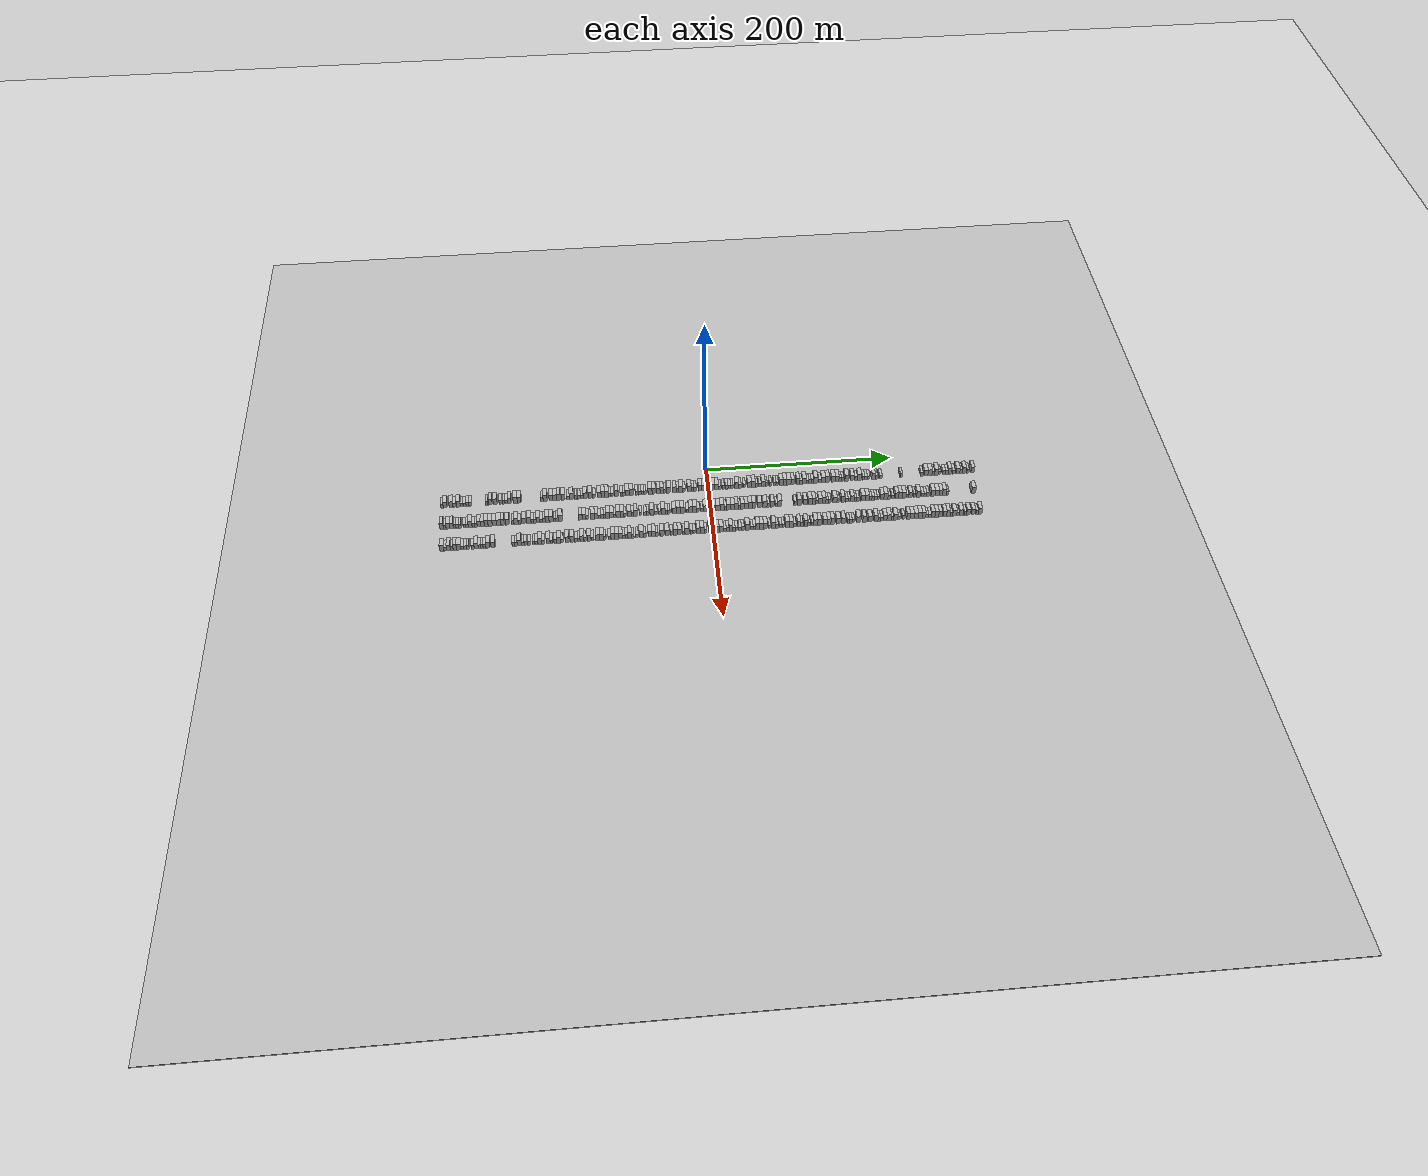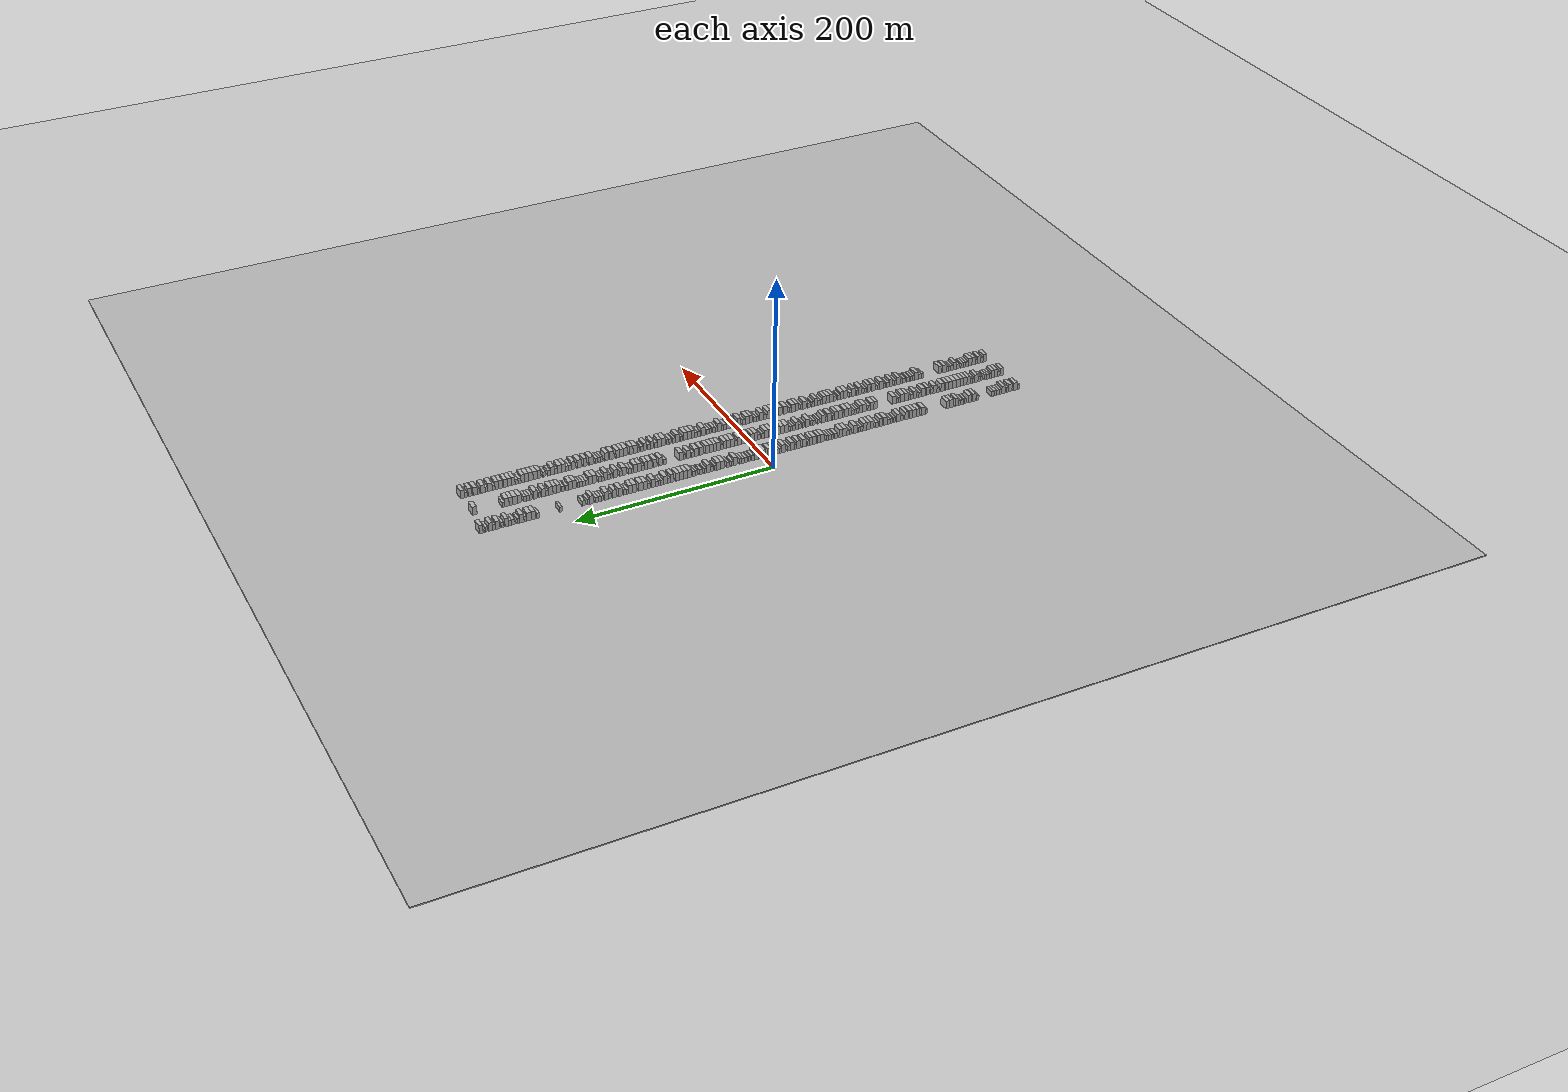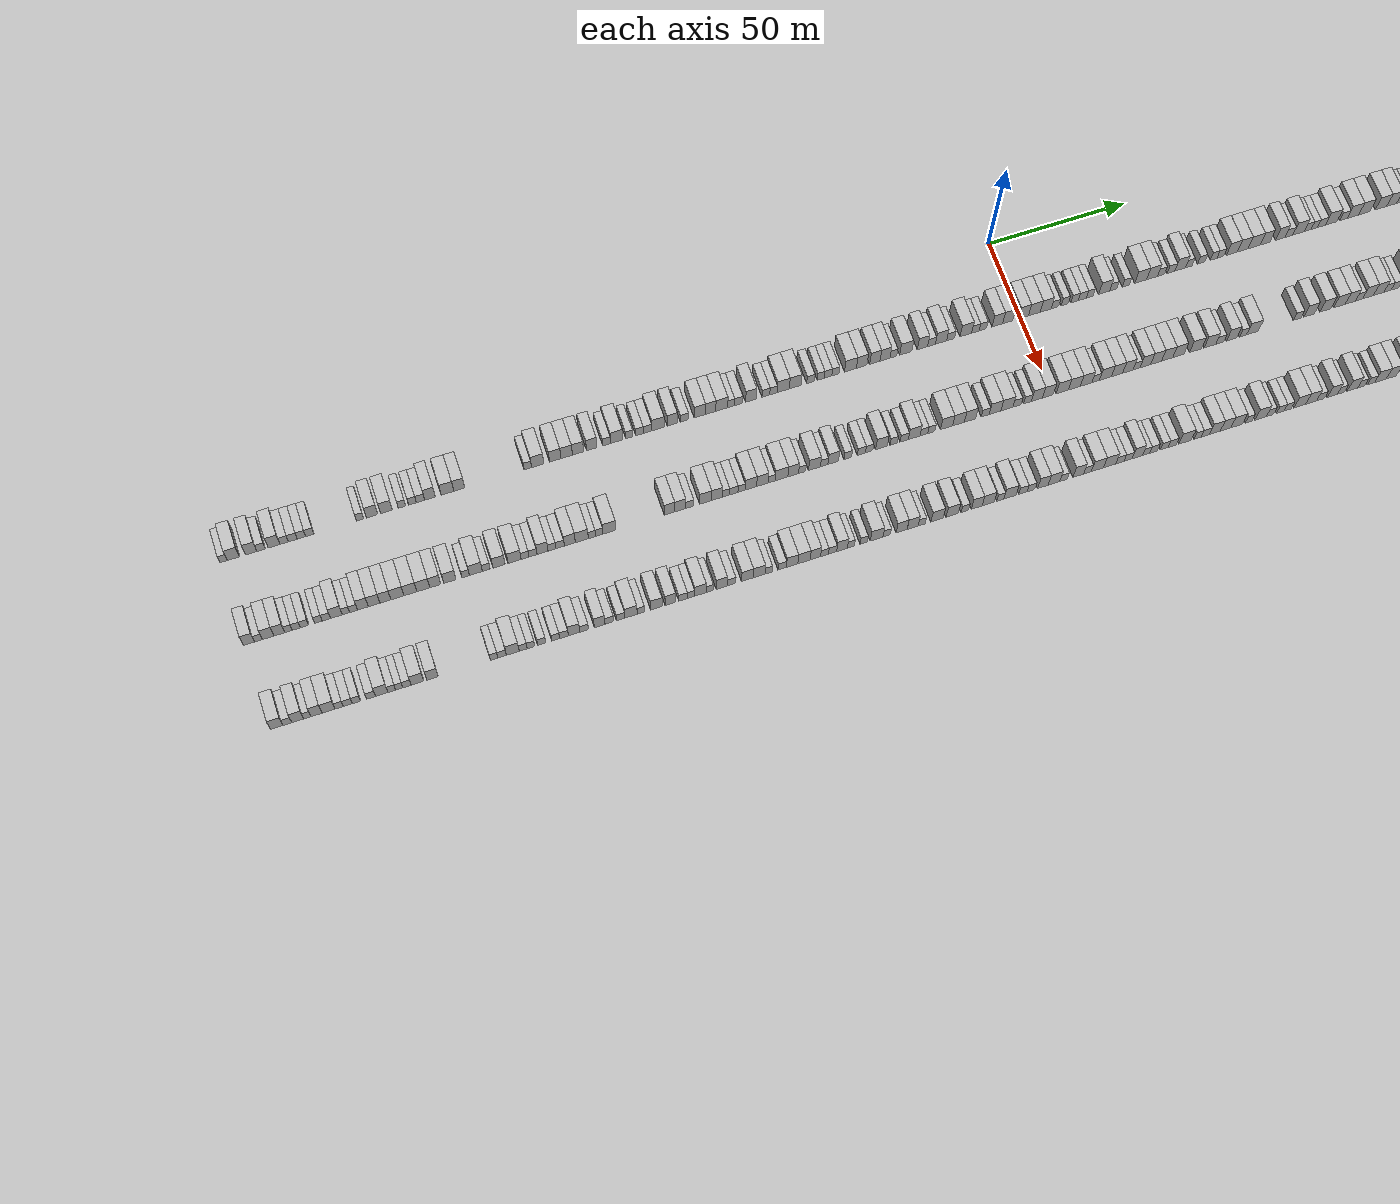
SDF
<?xml version="1.0" encoding="utf-8"?>

<sdf version="1.6">

   <world name="default">

      <gui fullscreen="0">

         <camera name="user_camera">

            <pose>-15 0 4.57585 0 0 0</pose>

            <view_controller>orbit</view_controller>

         </camera>

      </gui>

      <scene>

         <sky>

           <clouds>

             <speed>12</speed>

           </clouds>

         </sky>

         <ambient>0.4 0.4 0.4 1</ambient>

         <background>0.7 0.7 0.7 1</background>

         <shadows>1</shadows>

      </scene>

      <gravity>0 0 -9.8066</gravity>

      <magnetic_field>6e-06 2.3e-05 -4.2e-05</magnetic_field>

      <physics default="0" name="default_physics" type="ode">

         <ode>

            <solver>

               <type>quick</type>

               <iters>10</iters>

               <sor>1.0</sor>

               <use_dynamic_moi_rescaling>0</use_dynamic_moi_rescaling>

            </solver>

            <constraints>

               <cfm>0</cfm>

               <erp>0.2</erp>

               <contact_max_correcting_vel>100</contact_max_correcting_vel>

               <contact_surface_layer>0.001</contact_surface_layer>

            </constraints>

         </ode>

         <max_step_size>0.004</max_step_size>

         <real_time_factor>1</real_time_factor>

         <real_time_update_rate>250</real_time_update_rate>

      </physics>

      <light name="sun" type="directional">

         <cast_shadows>1</cast_shadows>

         <pose>0 0 10 0 0 0</pose>

         <diffuse>0.8 0.8 0.8 1</diffuse>

         <specular>0.2 0.2 0.2 1</specular>

         <attenuation>

            <range>1000</range>

            <constant>0.9</constant>

            <linear>0.01</linear>

            <quadratic>0.001</quadratic>

         </attenuation>

         <direction>-0.5 0.1 -0.9</direction>

      </light>

      <include>

         <name>ground_plane_1</name>

         <uri>model://HANNAS_ground_plane</uri>

         <pose>0 0 0  0 0 0</pose>

      </include>

      <include>

         <name>ground_plane_2</name>

         <uri>model://HANNAS_ground_plane</uri>

         <pose>100 0 0  0 0 0</pose>

      </include>

      <model name="building_1">

         <static>1</static>

         <pose frame="">25.0000 -278.7697 0 0.000000 0.000000 0.000000</pose>

         <link name="link">

            <pose frame="">0 0 3.00 0 0 0</pose>

            <collision name="collision">

               <geometry>

                  <box>

                     <size>10.0000 2.4606 6.0000</size>

                  </box>

               </geometry>

               <max_contacts>10</max_contacts>

               <surface>

                  <contact>

                     <ode/>

                  </contact>

                  <bounce/>

                  <friction>

                     <torsional>

                        <ode/>

                     </torsional>

                     <ode/>

                  </friction>

               </surface>

            </collision>

            <visual name="visual">

               <cast_shadows>0</cast_shadows>

               <geometry>

                  <box>

                     <size>10.0000 2.4606 6.0000</size>

                  </box>

               </geometry>

               <material>

                  <script>

                     <uri>model://HANNAS_wall/materials/scripts</uri>

                     <uri>model://HANNAS_wall/materials/textures</uri>

                     <name>vrc/HANNAS_wall</name>

                  </script>

               </material>

            </visual>

            <self_collide>0</self_collide>

            <enable_wind>0</enable_wind>

            <kinematic>0</kinematic>

         </link>

      </model>

      <model name="building_2">

         <static>1</static>

         <pose frame="">25.0000 -275.4560 0 0.000000 0.000000 0.000000</pose>

         <link name="link">

            <pose frame="">0 0 4.50 0 0 0</pose>

            <collision name="collision">

               <geometry>

                  <box>

                     <size>10.0000 4.1668 9.0000</size>

                  </box>

               </geometry>

               <max_contacts>10</max_contacts>

               <surface>

                  <contact>

                     <ode/>

                  </contact>

                  <bounce/>

                  <friction>

                     <torsional>

                        <ode/>

                     </torsional>

                     <ode/>

                  </friction>

               </surface>

            </collision>

            <visual name="visual">

               <cast_shadows>0</cast_shadows>

               <geometry>

                  <box>

                     <size>10.0000 4.1668 9.0000</size>

                  </box>

               </geometry>

               <material>

                  <script>

                     <uri>model://HANNAS_wall/materials/scripts</uri>

                     <uri>model://HANNAS_wall/materials/textures</uri>

                     <name>vrc/HANNAS_wall</name>

                  </script>

               </material>

            </visual>

            <self_collide>0</self_collide>

            <enable_wind>0</enable_wind>

            <kinematic>0</kinematic>

         </link>

      </model>

      <model name="building_3">

         <static>1</static>

         <pose frame="">25.0000 -269.4506 0 0.000000 0.000000 0.000000</pose>

         <link name="link">

            <pose frame="">0 0 4.50 0 0 0</pose>

            <collision name="collision">

               <geometry>

                  <box>

                     <size>10.0000 3.8440 9.0000</size>

                  </box>

               </geometry>

               <max_contacts>10</max_contacts>

               <surface>

                  <contact>

                     <ode/>

                  </contact>

                  <bounce/>

                  <friction>

                     <torsional>

                        <ode/>

                     </torsional>

                     <ode/>

                  </friction>

               </surface>

            </collision>

            <visual name="visual">

               <cast_shadows>0</cast_shadows>

               <geometry>

                  <box>

                     <size>10.0000 3.8440 9.0000</size>

                  </box>

               </geometry>

               <material>

                  <script>

                     <uri>model://HANNAS_wall/materials/scripts</uri>

                     <uri>model://HANNAS_wall/materials/textures</uri>

                     <name>vrc/HANNAS_wall</name>

                  </script>

               </material>

            </visual>

            <self_collide>0</self_collide>

            <enable_wind>0</enable_wind>

            <kinematic>0</kinematic>

         </link>

      </model>

      <model name="building_4">

         <static>1</static>

         <pose frame="">25.0000 -266.1226 0 0.000000 0.000000 0.000000</pose>

         <link name="link">

            <pose frame="">0 0 3.00 0 0 0</pose>

            <collision name="collision">

               <geometry>

                  <box>

                     <size>10.0000 2.8119 6.0000</size>

                  </box>

               </geometry>

               <max_contacts>10</max_contacts>

               <surface>

                  <contact>

                     <ode/>

                  </contact>

                  <bounce/>

                  <friction>

                     <torsional>

                        <ode/>

                     </torsional>

                     <ode/>

                  </friction>

               </surface>

            </collision>

            <visual name="visual">

               <cast_shadows>0</cast_shadows>

               <geometry>

                  <box>

                     <size>10.0000 2.8119 6.0000</size>

                  </box>

               </geometry>

               <material>

                  <script>

                     <uri>model://HANNAS_wall/materials/scripts</uri>

                     <uri>model://HANNAS_wall/materials/textures</uri>

                     <name>vrc/HANNAS_wall</name>

                  </script>

               </material>

            </visual>

            <self_collide>0</self_collide>

            <enable_wind>0</enable_wind>

            <kinematic>0</kinematic>

         </link>

      </model>

      <model name="building_5">

         <static>1</static>

         <pose frame="">25.0000 -261.7334 0 0.000000 0.000000 0.000000</pose>

         <link name="link">

            <pose frame="">0 0 4.50 0 0 0</pose>

            <collision name="collision">

               <geometry>

                  <box>

                     <size>10.0000 3.9664 9.0000</size>

                  </box>

               </geometry>

               <max_contacts>10</max_contacts>

               <surface>

                  <contact>

                     <ode/>

                  </contact>

                  <bounce/>

                  <friction>

                     <torsional>

                        <ode/>

                     </torsional>

                     <ode/>

                  </friction>

               </surface>

            </collision>

            <visual name="visual">

               <cast_shadows>0</cast_shadows>

               <geometry>

                  <box>

                     <size>10.0000 3.9664 9.0000</size>

                  </box>

               </geometry>

               <material>

                  <script>

                     <uri>model://HANNAS_wall/materials/scripts</uri>

                     <uri>model://HANNAS_wall/materials/textures</uri>

                     <name>vrc/HANNAS_wall</name>

                  </script>

               </material>

            </visual>

            <self_collide>0</self_collide>

            <enable_wind>0</enable_wind>

            <kinematic>0</kinematic>

         </link>

      </model>

      <model name="building_6">

         <static>1</static>

         <pose frame="">25.0000 -258.3203 0 0.000000 0.000000 0.000000</pose>

         <link name="link">

            <pose frame="">0 0 3.00 0 0 0</pose>

            <collision name="collision">

               <geometry>

                  <box>

                     <size>10.0000 2.8597 6.0000</size>

                  </box>

               </geometry>

               <max_contacts>10</max_contacts>

               <surface>

                  <contact>

                     <ode/>

                  </contact>

                  <bounce/>

                  <friction>

                     <torsional>

                        <ode/>

                     </torsional>

                     <ode/>

                  </friction>

               </surface>

            </collision>

            <visual name="visual">

               <cast_shadows>0</cast_shadows>

               <geometry>

                  <box>

                     <size>10.0000 2.8597 6.0000</size>

                  </box>

               </geometry>

               <material>

                  <script>

                     <uri>model://HANNAS_wall/materials/scripts</uri>

                     <uri>model://HANNAS_wall/materials/textures</uri>

                     <name>vrc/HANNAS_wall</name>

                  </script>

               </material>

            </visual>

            <self_collide>0</self_collide>

            <enable_wind>0</enable_wind>

            <kinematic>0</kinematic>

         </link>

      </model>

      <model name="building_7">

         <static>1</static>

         <pose frame="">25.0000 -255.3988 0 0.000000 0.000000 0.000000</pose>

         <link name="link">

            <pose frame="">0 0 3.00 0 0 0</pose>

            <collision name="collision">

               <geometry>

                  <box>

                     <size>10.0000 2.9834 6.0000</size>

                  </box>

               </geometry>

               <max_contacts>10</max_contacts>

               <surface>

                  <contact>

                     <ode/>

                  </contact>

                  <bounce/>

                  <friction>

                     <torsional>

                        <ode/>

                     </torsional>

                     <ode/>

                  </friction>

               </surface>

            </collision>

            <visual name="visual">

               <cast_shadows>0</cast_shadows>

               <geometry>

                  <box>

                     <size>10.0000 2.9834 6.0000</size>

                  </box>

               </geometry>

               <material>

                  <script>

                     <uri>model://HANNAS_wall/materials/scripts</uri>

                     <uri>model://HANNAS_wall/materials/textures</uri>

                     <name>vrc/HANNAS_wall</name>

                  </script>

               </material>

            </visual>

            <self_collide>0</self_collide>

            <enable_wind>0</enable_wind>

            <kinematic>0</kinematic>

         </link>

      </model>

      <model name="building_8">

         <static>1</static>

         <pose frame="">25.0000 -252.4673 0 0.000000 0.000000 0.000000</pose>

         <link name="link">

            <pose frame="">0 0 3.00 0 0 0</pose>

            <collision name="collision">

               <geometry>

                  <box>

                     <size>10.0000 2.8796 6.0000</size>

                  </box>

               </geometry>

               <max_contacts>10</max_contacts>

               <surface>

                  <contact>

                     <ode/>

                  </contact>

                  <bounce/>

                  <friction>

                     <torsional>

                        <ode/>

                     </torsional>

                     <ode/>

                  </friction>

               </surface>

            </collision>

            <visual name="visual">

               <cast_shadows>0</cast_shadows>

               <geometry>

                  <box>

                     <size>10.0000 2.8796 6.0000</size>

                  </box>

               </geometry>

               <material>

                  <script>

                     <uri>model://HANNAS_wall/materials/scripts</uri>

                     <uri>model://HANNAS_wall/materials/textures</uri>

                     <name>vrc/HANNAS_wall</name>

                  </script>

               </material>

            </visual>

            <self_collide>0</self_collide>

            <enable_wind>0</enable_wind>

            <kinematic>0</kinematic>

         </link>

      </model>

      <model name="building_9">

         <static>1</static>

         <pose frame="">25.0000 -249.6396 0 0.000000 0.000000 0.000000</pose>

         <link name="link">

            <pose frame="">0 0 3.00 0 0 0</pose>

            <collision name="collision">

               <geometry>

                  <box>

                     <size>10.0000 2.7757 6.0000</size>

                  </box>

               </geometry>

               <max_contacts>10</max_contacts>

               <surface>

                  <contact>

                     <ode/>

                  </contact>

                  <bounce/>

                  <friction>

                     <torsional>

                        <ode/>

                     </torsional>

                     <ode/>

                  </friction>

               </surface>

            </collision>

            <visual name="visual">

               <cast_shadows>0</cast_shadows>

               <geometry>

                  <box>

                     <size>10.0000 2.7757 6.0000</size>

                  </box>

               </geometry>

               <material>

                  <script>

                     <uri>model://HANNAS_wall/materials/scripts</uri>

                     <uri>model://HANNAS_wall/materials/textures</uri>

                     <name>vrc/HANNAS_wall</name>

                  </script>

               </material>

            </visual>

            <self_collide>0</self_collide>

            <enable_wind>0</enable_wind>

            <kinematic>0</kinematic>

         </link>

      </model>

      <model name="building_10">

         <static>1</static>

         <pose frame="">25.0000 -232.5697 0 0.000000 0.000000 0.000000</pose>

         <link name="link">

            <pose frame="">0 0 3.00 0 0 0</pose>

            <collision name="collision">

               <geometry>

                  <box>

                     <size>10.0000 2.4547 6.0000</size>

                  </box>

               </geometry>

               <max_contacts>10</max_contacts>

               <surface>

                  <contact>

                     <ode/>

                  </contact>

                  <bounce/>

                  <friction>

                     <torsional>

                        <ode/>

                     </torsional>

                     <ode/>

                  </friction>

               </surface>

            </collision>

            <visual name="visual">

               <cast_shadows>0</cast_shadows>

               <geometry>

                  <box>

                     <size>10.0000 2.4547 6.0000</size>

                  </box>

               </geometry>

               <material>

                  <script>

                     <uri>model://HANNAS_wall/materials/scripts</uri>

                     <uri>model://HANNAS_wall/materials/textures</uri>

                     <name>vrc/HANNAS_wall</name>

                  </script>

               </material>

            </visual>

            <self_collide>0</self_collide>

            <enable_wind>0</enable_wind>

            <kinematic>0</kinematic>

         </link>

      </model>

      <model name="building_11">

         <static>1</static>

         <pose frame="">25.0000 -228.4331 0 0.000000 0.000000 0.000000</pose>

         <link name="link">

            <pose frame="">0 0 4.50 0 0 0</pose>

            <collision name="collision">

               <geometry>

                  <box>

                     <size>10.0000 3.8186 9.0000</size>

                  </box>

               </geometry>

               <max_contacts>10</max_contacts>

               <surface>

                  <contact>

                     <ode/>

                  </contact>

                  <bounce/>

                  <friction>

                     <torsional>

                        <ode/>

                     </torsional>

                     <ode/>

                  </friction>

               </surface>

            </collision>

            <visual name="visual">

               <cast_shadows>0</cast_shadows>

               <geometry>

                  <box>

                     <size>10.0000 3.8186 9.0000</size>

                  </box>

               </geometry>

               <material>

                  <script>

                     <uri>model://HANNAS_wall/materials/scripts</uri>

                     <uri>model://HANNAS_wall/materials/textures</uri>

                     <name>vrc/HANNAS_wall</name>

                  </script>

               </material>

            </visual>

            <self_collide>0</self_collide>

            <enable_wind>0</enable_wind>

            <kinematic>0</kinematic>

         </link>

      </model>

      <model name="building_12">

         <static>1</static>

         <pose frame="">25.0000 -223.5195 0 0.000000 0.000000 0.000000</pose>

         <link name="link">

            <pose frame="">0 0 4.50 0 0 0</pose>

            <collision name="collision">

               <geometry>

                  <box>

                     <size>10.0000 4.0086 9.0000</size>

                  </box>

               </geometry>

               <max_contacts>10</max_contacts>

               <surface>

                  <contact>

                     <ode/>

                  </contact>

                  <bounce/>

                  <friction>

                     <torsional>

                        <ode/>

                     </torsional>

                     <ode/>

                  </friction>

               </surface>

            </collision>

            <visual name="visual">

               <cast_shadows>0</cast_shadows>

               <geometry>

                  <box>

                     <size>10.0000 4.0086 9.0000</size>

                  </box>

               </geometry>

               <material>

                  <script>

                     <uri>model://HANNAS_wall/materials/scripts</uri>

                     <uri>model://HANNAS_wall/materials/textures</uri>

                     <name>vrc/HANNAS_wall</name>

                  </script>

               </material>

            </visual>

            <self_collide>0</self_collide>

            <enable_wind>0</enable_wind>

            <kinematic>0</kinematic>

         </link>

      </model>

      <model name="building_13">

         <static>1</static>

         <pose frame="">25.0000 -218.2495 0 0.000000 0.000000 0.000000</pose>

         <link name="link">

            <pose frame="">0 0 3.00 0 0 0</pose>

            <collision name="collision">

               <geometry>

                  <box>

                     <size>10.0000 2.5314 6.0000</size>

                  </box>

               </geometry>

               <max_contacts>10</max_contacts>

               <surface>

                  <contact>

                     <ode/>

                  </contact>

                  <bounce/>

                  <friction>

                     <torsional>

                        <ode/>

                     </torsional>

                     <ode/>

                  </friction>

               </surface>

            </collision>

            <visual name="visual">

               <cast_shadows>0</cast_shadows>

               <geometry>

                  <box>

                     <size>10.0000 2.5314 6.0000</size>

                  </box>

               </geometry>

               <material>

                  <script>

                     <uri>model://HANNAS_wall/materials/scripts</uri>

                     <uri>model://HANNAS_wall/materials/textures</uri>

                     <name>vrc/HANNAS_wall</name>

                  </script>

               </material>

            </visual>

            <self_collide>0</self_collide>

            <enable_wind>0</enable_wind>

            <kinematic>0</kinematic>

         </link>

      </model>

      <model name="building_14">

         <static>1</static>

         <pose frame="">25.0000 -214.6577 0 0.000000 0.000000 0.000000</pose>

         <link name="link">

            <pose frame="">0 0 3.00 0 0 0</pose>

            <collision name="collision">

               <geometry>

                  <box>

                     <size>10.0000 2.6521 6.0000</size>

                  </box>

               </geometry>

               <max_contacts>10</max_contacts>

               <surface>

                  <contact>

                     <ode/>

                  </contact>

                  <bounce/>

                  <friction>

                     <torsional>

                        <ode/>

                     </torsional>

                     <ode/>

                  </friction>

               </surface>

            </collision>

            <visual name="visual">

               <cast_shadows>0</cast_shadows>

               <geometry>

                  <box>

                     <size>10.0000 2.6521 6.0000</size>

                  </box>

               </geometry>

               <material>

                  <script>

                     <uri>model://HANNAS_wall/materials/scripts</uri>

                     <uri>model://HANNAS_wall/materials/textures</uri>

                     <name>vrc/HANNAS_wall</name>

                  </script>

               </material>

            </visual>

            <self_collide>0</self_collide>

            <enable_wind>0</enable_wind>

            <kinematic>0</kinematic>

         </link>

      </model>

      <model name="building_15">

         <static>1</static>

         <pose frame="">25.0000 -211.8904 0 0.000000 0.000000 0.000000</pose>

         <link name="link">

            <pose frame="">0 0 3.00 0 0 0</pose>

            <collision name="collision">

               <geometry>

                  <box>

                     <size>10.0000 2.8824 6.0000</size>

                  </box>

               </geometry>

               <max_contacts>10</max_contacts>

               <surface>

                  <contact>

                     <ode/>

                  </contact>

                  <bounce/>

                  <friction>

                     <torsional>

                        <ode/>

                     </torsional>

                     <ode/>

                  </friction>

               </surface>

            </collision>

            <visual name="visual">

               <cast_shadows>0</cast_shadows>

               <geometry>

                  <box>

                     <size>10.0000 2.8824 6.0000</size>

                  </box>

               </geometry>

               <material>

                  <script>

                     <uri>model://HANNAS_wall/materials/scripts</uri>

                     <uri>model://HANNAS_wall/materials/textures</uri>

                     <name>vrc/HANNAS_wall</name>

                  </script>

               </material>

            </visual>

            <self_collide>0</self_collide>

            <enable_wind>0</enable_wind>

            <kinematic>0</kinematic>

         </link>

      </model>

      <model name="building_16">

         <static>1</static>

         <pose frame="">25.0000 -208.6323 0 0.000000 0.000000 0.000000</pose>

         <link name="link">

            <pose frame="">0 0 4.50 0 0 0</pose>

            <collision name="collision">

               <geometry>

                  <box>

                     <size>10.0000 3.6338 9.0000</size>

                  </box>

               </geometry>

               <max_contacts>10</max_contacts>

               <surface>

                  <contact>

                     <ode/>

                  </contact>

                  <bounce/>

                  <friction>

                     <torsional>

                        <ode/>

                     </torsional>

                     <ode/>

                  </friction>

               </surface>

            </collision>

            <visual name="visual">

               <cast_shadows>0</cast_shadows>

               <geometry>

                  <box>

                     <size>10.0000 3.6338 9.0000</size>

                  </box>

               </geometry>

               <material>

                  <script>

                     <uri>model://HANNAS_wall/materials/scripts</uri>

                     <uri>model://HANNAS_wall/materials/textures</uri>

                     <name>vrc/HANNAS_wall</name>

                  </script>

               </material>

            </visual>

            <self_collide>0</self_collide>

            <enable_wind>0</enable_wind>

            <kinematic>0</kinematic>

         </link>

      </model>

      <model name="building_17">

         <static>1</static>

         <pose frame="">25.0000 -202.6358 0 0.000000 0.000000 0.000000</pose>

         <link name="link">

            <pose frame="">0 0 4.50 0 0 0</pose>

            <collision name="collision">

               <geometry>

                  <box>

                     <size>10.0000 4.3593 9.0000</size>

                  </box>

               </geometry>

               <max_contacts>10</max_contacts>

               <surface>

                  <contact>

                     <ode/>

                  </contact>

                  <bounce/>

                  <friction>

                     <torsional>

                        <ode/>

                     </torsional>

                     <ode/>

                  </friction>

               </surface>

            </collision>

            <visual name="visual">

               <cast_shadows>0</cast_shadows>

               <geometry>

                  <box>

                     <size>10.0000 4.3593 9.0000</size>

                  </box>

               </geometry>

               <material>

                  <script>

                     <uri>model://HANNAS_wall/materials/scripts</uri>

                     <uri>model://HANNAS_wall/materials/textures</uri>

                     <name>vrc/HANNAS_wall</name>

                  </script>

               </material>

            </visual>

            <self_collide>0</self_collide>

            <enable_wind>0</enable_wind>

            <kinematic>0</kinematic>

         </link>

      </model>

      <model name="building_18">

         <static>1</static>

         <pose frame="">25.0000 -198.5777 0 0.000000 0.000000 0.000000</pose>

         <link name="link">

            <pose frame="">0 0 4.50 0 0 0</pose>

            <collision name="collision">

               <geometry>

                  <box>

                     <size>10.0000 3.7568 9.0000</size>

                  </box>

               </geometry>

               <max_contacts>10</max_contacts>

               <surface>

                  <contact>

                     <ode/>

                  </contact>

                  <bounce/>

                  <friction>

                     <torsional>

                        <ode/>

                     </torsional>

                     <ode/>

                  </friction>

               </surface>

            </collision>

            <visual name="visual">

               <cast_shadows>0</cast_shadows>

               <geometry>

                  <box>

                     <size>10.0000 3.7568 9.0000</size>

                  </box>

               </geometry>

               <material>

                  <script>

                     <uri>model://HANNAS_wall/materials/scripts</uri>

                     <uri>model://HANNAS_wall/materials/textures</uri>

                     <name>vrc/HANNAS_wall</name>

                  </script>

               </material>

            </visual>

            <self_collide>0</self_collide>

            <enable_wind>0</enable_wind>

            <kinematic>0</kinematic>

         </link>

      </model>

      <model name="building_19">

         <static>1</static>

         <pose frame="">25.0000 -174.8789 0 0.000000 0.000000 0.000000</pose>

         <link name="link">

            <pose frame="">0 0 3.00 0 0 0</pose>

            <collision name="collision">

               <geometry>

                  <box>

                     <size>10.0000 2.5469 6.0000</size>

                  </box>

               </geometry>

               <max_contacts>10</max_contacts>

               <surface>

                  <contact>

                     <ode/>

                  </contact>

                  <bounce/>

                  <friction>

                     <torsional>

                        <ode/>

                     </torsional>

                     <ode/>

                  </friction>

               </surface>

            </collision>

            <visual name="visual">

               <cast_shadows>0</cast_shadows>

               <geometry>

                  <box>

                     <size>10.0000 2.5469 6.0000</size>

                  </box>

               </geometry>

               <material>

                  <script>

                     <uri>model://HANNAS_wall/materials/scripts</uri>

                     <uri>model://HANNAS_wall/materials/textures</uri>

                     <name>vrc/HANNAS_wall</name>

                  </script>

               </material>

            </visual>

            <self_collide>0</self_collide>

            <enable_wind>0</enable_wind>

            <kinematic>0</kinematic>

         </link>

      </model>

      <model name="building_20">

         <static>1</static>

         <pose frame="">25.0000 -171.4664 0 0.000000 0.000000 0.000000</pose>

         <link name="link">

            <pose frame="">0 0 4.50 0 0 0</pose>

            <collision name="collision">

               <geometry>

                  <box>

                     <size>10.0000 4.2780 9.0000</size>

                  </box>

               </geometry>

               <max_contacts>10</max_contacts>

               <surface>

                  <contact>

                     <ode/>

                  </contact>

                  <bounce/>

                  <friction>

                     <torsional>

                        <ode/>

                     </torsional>

                     <ode/>

                  </friction>

               </surface>

            </collision>

            <visual name="visual">

               <cast_shadows>0</cast_shadows>

               <geometry>

                  <box>

                     <size>10.0000 4.2780 9.0000</size>

                  </box>

               </geometry>

               <material>

                  <script>

                     <uri>model://HANNAS_wall/materials/scripts</uri>

                     <uri>model://HANNAS_wall/materials/textures</uri>

                     <name>vrc/HANNAS_wall</name>

                  </script>

               </material>

            </visual>

            <self_collide>0</self_collide>

            <enable_wind>0</enable_wind>

            <kinematic>0</kinematic>

         </link>

      </model>

      <model name="building_21">

         <static>1</static>

         <pose frame="">25.0000 -165.3564 0 0.000000 0.000000 0.000000</pose>

         <link name="link">

            <pose frame="">0 0 4.50 0 0 0</pose>

            <collision name="collision">

               <geometry>

                  <box>

                     <size>10.0000 3.9420 9.0000</size>

                  </box>

               </geometry>

               <max_contacts>10</max_contacts>

               <surface>

                  <contact>

                     <ode/>

                  </contact>

                  <bounce/>

                  <friction>

                     <torsional>

                        <ode/>

                     </torsional>

                     <ode/>

                  </friction>

               </surface>

            </collision>

            <visual name="visual">

               <cast_shadows>0</cast_shadows>

               <geometry>

                  <box>

                     <size>10.0000 3.9420 9.0000</size>

                  </box>

               </geometry>

               <material>

                  <script>

                     <uri>model://HANNAS_wall/materials/scripts</uri>

                     <uri>model://HANNAS_wall/materials/textures</uri>

                     <name>vrc/HANNAS_wall</name>

                  </script>

               </material>

            </visual>

            <self_collide>0</self_collide>

            <enable_wind>0</enable_wind>

            <kinematic>0</kinematic>

         </link>

      </model>

      <model name="building_22">

         <static>1</static>

         <pose frame="">25.0000 -161.3830 0 0.000000 0.000000 0.000000</pose>

         <link name="link">

            <pose frame="">0 0 4.50 0 0 0</pose>

            <collision name="collision">

               <geometry>

                  <box>

                     <size>10.0000 4.0049 9.0000</size>

                  </box>

               </geometry>

               <max_contacts>10</max_contacts>

               <surface>

                  <contact>

                     <ode/>

                  </contact>

                  <bounce/>

                  <friction>

                     <torsional>

                        <ode/>

                     </torsional>

                     <ode/>

                  </friction>

               </surface>

            </collision>

            <visual name="visual">

               <cast_shadows>0</cast_shadows>

               <geometry>

                  <box>

                     <size>10.0000 4.0049 9.0000</size>

                  </box>

               </geometry>

               <material>

                  <script>

                     <uri>model://HANNAS_wall/materials/scripts</uri>

                     <uri>model://HANNAS_wall/materials/textures</uri>

                     <name>vrc/HANNAS_wall</name>

                  </script>

               </material>

            </visual>

            <self_collide>0</self_collide>

            <enable_wind>0</enable_wind>

            <kinematic>0</kinematic>

         </link>

      </model>

      <model name="building_23">

         <static>1</static>

         <pose frame="">25.0000 -157.4230 0 0.000000 0.000000 0.000000</pose>

         <link name="link">

            <pose frame="">0 0 4.50 0 0 0</pose>

            <collision name="collision">

               <geometry>

                  <box>

                     <size>10.0000 3.9150 9.0000</size>

                  </box>

               </geometry>

               <max_contacts>10</max_contacts>

               <surface>

                  <contact>

                     <ode/>

                  </contact>

                  <bounce/>

                  <friction>

                     <torsional>

                        <ode/>

                     </torsional>

                     <ode/>

                  </friction>

               </surface>

            </collision>

            <visual name="visual">

               <cast_shadows>0</cast_shadows>

               <geometry>

                  <box>

                     <size>10.0000 3.9150 9.0000</size>

                  </box>

               </geometry>

               <material>

                  <script>

                     <uri>model://HANNAS_wall/materials/scripts</uri>

                     <uri>model://HANNAS_wall/materials/textures</uri>

                     <name>vrc/HANNAS_wall</name>

                  </script>

               </material>

            </visual>

            <self_collide>0</self_collide>

            <enable_wind>0</enable_wind>

            <kinematic>0</kinematic>

         </link>

      </model>

      <model name="building_24">

         <static>1</static>

         <pose frame="">25.0000 -152.6581 0 0.000000 0.000000 0.000000</pose>

         <link name="link">

            <pose frame="">0 0 4.50 0 0 0</pose>

            <collision name="collision">

               <geometry>

                  <box>

                     <size>10.0000 3.6148 9.0000</size>

                  </box>

               </geometry>

               <max_contacts>10</max_contacts>

               <surface>

                  <contact>

                     <ode/>

                  </contact>

                  <bounce/>

                  <friction>

                     <torsional>

                        <ode/>

                     </torsional>

                     <ode/>

                  </friction>

               </surface>

            </collision>

            <visual name="visual">

               <cast_shadows>0</cast_shadows>

               <geometry>

                  <box>

                     <size>10.0000 3.6148 9.0000</size>

                  </box>

               </geometry>

               <material>

                  <script>

                     <uri>model://HANNAS_wall/materials/scripts</uri>

                     <uri>model://HANNAS_wall/materials/textures</uri>

                     <name>vrc/HANNAS_wall</name>

                  </script>

               </material>

            </visual>

            <self_collide>0</self_collide>

            <enable_wind>0</enable_wind>

            <kinematic>0</kinematic>

         </link>

      </model>

      <model name="building_25">

         <static>1</static>

         <pose frame="">25.0000 -147.4534 0 0.000000 0.000000 0.000000</pose>

         <link name="link">

            <pose frame="">0 0 3.00 0 0 0</pose>

            <collision name="collision">

               <geometry>

                  <box>

                     <size>10.0000 2.7946 6.0000</size>

                  </box>

               </geometry>

               <max_contacts>10</max_contacts>

               <surface>

                  <contact>

                     <ode/>

                  </contact>

                  <bounce/>

                  <friction>

                     <torsional>

                        <ode/>

                     </torsional>

                     <ode/>

                  </friction>

               </surface>

            </collision>

            <visual name="visual">

               <cast_shadows>0</cast_shadows>

               <geometry>

                  <box>

                     <size>10.0000 2.7946 6.0000</size>

                  </box>

               </geometry>

               <material>

                  <script>

                     <uri>model://HANNAS_wall/materials/scripts</uri>

                     <uri>model://HANNAS_wall/materials/textures</uri>

                     <name>vrc/HANNAS_wall</name>

                  </script>

               </material>

            </visual>

            <self_collide>0</self_collide>

            <enable_wind>0</enable_wind>

            <kinematic>0</kinematic>

         </link>

      </model>

      <model name="building_26">

         <static>1</static>

         <pose frame="">25.0000 -143.9272 0 0.000000 0.000000 0.000000</pose>

         <link name="link">

            <pose frame="">0 0 4.50 0 0 0</pose>

            <collision name="collision">

               <geometry>

                  <box>

                     <size>10.0000 4.2579 9.0000</size>

                  </box>

               </geometry>

               <max_contacts>10</max_contacts>

               <surface>

                  <contact>

                     <ode/>

                  </contact>

                  <bounce/>

                  <friction>

                     <torsional>

                        <ode/>

                     </torsional>

                     <ode/>

                  </friction>

               </surface>

            </collision>

            <visual name="visual">

               <cast_shadows>0</cast_shadows>

               <geometry>

                  <box>

                     <size>10.0000 4.2579 9.0000</size>

                  </box>

               </geometry>

               <material>

                  <script>

                     <uri>model://HANNAS_wall/materials/scripts</uri>

                     <uri>model://HANNAS_wall/materials/textures</uri>

                     <name>vrc/HANNAS_wall</name>

                  </script>

               </material>

            </visual>

            <self_collide>0</self_collide>

            <enable_wind>0</enable_wind>

            <kinematic>0</kinematic>

         </link>

      </model>

      <model name="building_27">

         <static>1</static>

         <pose frame="">25.0000 -139.5497 0 0.000000 0.000000 0.000000</pose>

         <link name="link">

            <pose frame="">0 0 3.00 0 0 0</pose>

            <collision name="collision">

               <geometry>

                  <box>

                     <size>10.0000 2.4971 6.0000</size>

                  </box>

               </geometry>

               <max_contacts>10</max_contacts>

               <surface>

                  <contact>

                     <ode/>

                  </contact>

                  <bounce/>

                  <friction>

                     <torsional>

                        <ode/>

                     </torsional>

                     <ode/>

                  </friction>

               </surface>

            </collision>

            <visual name="visual">

               <cast_shadows>0</cast_shadows>

               <geometry>

                  <box>

                     <size>10.0000 2.4971 6.0000</size>

                  </box>

               </geometry>

               <material>

                  <script>

                     <uri>model://HANNAS_wall/materials/scripts</uri>

                     <uri>model://HANNAS_wall/materials/textures</uri>

                     <name>vrc/HANNAS_wall</name>

                  </script>

               </material>

            </visual>

            <self_collide>0</self_collide>

            <enable_wind>0</enable_wind>

            <kinematic>0</kinematic>

         </link>

      </model>

      <model name="building_28">

         <static>1</static>

         <pose frame="">25.0000 -135.9501 0 0.000000 0.000000 0.000000</pose>

         <link name="link">

            <pose frame="">0 0 3.00 0 0 0</pose>

            <collision name="collision">

               <geometry>

                  <box>

                     <size>10.0000 2.7020 6.0000</size>

                  </box>

               </geometry>

               <max_contacts>10</max_contacts>

               <surface>

                  <contact>

                     <ode/>

                  </contact>

                  <bounce/>

                  <friction>

                     <torsional>

                        <ode/>

                     </torsional>

                     <ode/>

                  </friction>

               </surface>

            </collision>

            <visual name="visual">

               <cast_shadows>0</cast_shadows>

               <geometry>

                  <box>

                     <size>10.0000 2.7020 6.0000</size>

                  </box>

               </geometry>

               <material>

                  <script>

                     <uri>model://HANNAS_wall/materials/scripts</uri>

                     <uri>model://HANNAS_wall/materials/textures</uri>

                     <name>vrc/HANNAS_wall</name>

                  </script>

               </material>

            </visual>

            <self_collide>0</self_collide>

            <enable_wind>0</enable_wind>

            <kinematic>0</kinematic>

         </link>

      </model>

      <model name="building_29">

         <static>1</static>

         <pose frame="">25.0000 -133.1098 0 0.000000 0.000000 0.000000</pose>

         <link name="link">

            <pose frame="">0 0 3.00 0 0 0</pose>

            <collision name="collision">

               <geometry>

                  <box>

                     <size>10.0000 2.9786 6.0000</size>

                  </box>

               </geometry>

               <max_contacts>10</max_contacts>

               <surface>

                  <contact>

                     <ode/>

                  </contact>

                  <bounce/>

                  <friction>

                     <torsional>

                        <ode/>

                     </torsional>

                     <ode/>

                  </friction>

               </surface>

            </collision>

            <visual name="visual">

               <cast_shadows>0</cast_shadows>

               <geometry>

                  <box>

                     <size>10.0000 2.9786 6.0000</size>

                  </box>

               </geometry>

               <material>

                  <script>

                     <uri>model://HANNAS_wall/materials/scripts</uri>

                     <uri>model://HANNAS_wall/materials/textures</uri>

                     <name>vrc/HANNAS_wall</name>

                  </script>

               </material>

            </visual>

            <self_collide>0</self_collide>

            <enable_wind>0</enable_wind>

            <kinematic>0</kinematic>

         </link>

      </model>

      <model name="building_30">

         <static>1</static>

         <pose frame="">25.0000 -129.4488 0 0.000000 0.000000 0.000000</pose>

         <link name="link">

            <pose frame="">0 0 4.50 0 0 0</pose>

            <collision name="collision">

               <geometry>

                  <box>

                     <size>10.0000 4.3434 9.0000</size>

                  </box>

               </geometry>

               <max_contacts>10</max_contacts>

               <surface>

                  <contact>

                     <ode/>

                  </contact>

                  <bounce/>

                  <friction>

                     <torsional>

                        <ode/>

                     </torsional>

                     <ode/>

                  </friction>

               </surface>

            </collision>

            <visual name="visual">

               <cast_shadows>0</cast_shadows>

               <geometry>

                  <box>

                     <size>10.0000 4.3434 9.0000</size>

                  </box>

               </geometry>

               <material>

                  <script>

                     <uri>model://HANNAS_wall/materials/scripts</uri>

                     <uri>model://HANNAS_wall/materials/textures</uri>

                     <name>vrc/HANNAS_wall</name>

                  </script>

               </material>

            </visual>

            <self_collide>0</self_collide>

            <enable_wind>0</enable_wind>

            <kinematic>0</kinematic>

         </link>

      </model>

      <model name="building_31">

         <static>1</static>

         <pose frame="">25.0000 -124.4628 0 0.000000 0.000000 0.000000</pose>

         <link name="link">

            <pose frame="">0 0 4.50 0 0 0</pose>

            <collision name="collision">

               <geometry>

                  <box>

                     <size>10.0000 3.6286 9.0000</size>

                  </box>

               </geometry>

               <max_contacts>10</max_contacts>

               <surface>

                  <contact>

                     <ode/>

                  </contact>

                  <bounce/>

                  <friction>

                     <torsional>

                        <ode/>

                     </torsional>

                     <ode/>

                  </friction>

               </surface>

            </collision>

            <visual name="visual">

               <cast_shadows>0</cast_shadows>

               <geometry>

                  <box>

                     <size>10.0000 3.6286 9.0000</size>

                  </box>

               </geometry>

               <material>

                  <script>

                     <uri>model://HANNAS_wall/materials/scripts</uri>

                     <uri>model://HANNAS_wall/materials/textures</uri>

                     <name>vrc/HANNAS_wall</name>

                  </script>

               </material>

            </visual>

            <self_collide>0</self_collide>

            <enable_wind>0</enable_wind>

            <kinematic>0</kinematic>

         </link>

      </model>

      <model name="building_32">

         <static>1</static>

         <pose frame="">25.0000 -120.2204 0 0.000000 0.000000 0.000000</pose>

         <link name="link">

            <pose frame="">0 0 3.00 0 0 0</pose>

            <collision name="collision">

               <geometry>

                  <box>

                     <size>10.0000 2.8562 6.0000</size>

                  </box>

               </geometry>

               <max_contacts>10</max_contacts>

               <surface>

                  <contact>

                     <ode/>

                  </contact>

                  <bounce/>

                  <friction>

                     <torsional>

                        <ode/>

                     </torsional>

                     <ode/>

                  </friction>

               </surface>

            </collision>

            <visual name="visual">

               <cast_shadows>0</cast_shadows>

               <geometry>

                  <box>

                     <size>10.0000 2.8562 6.0000</size>

                  </box>

               </geometry>

               <material>

                  <script>

                     <uri>model://HANNAS_wall/materials/scripts</uri>

                     <uri>model://HANNAS_wall/materials/textures</uri>

                     <name>vrc/HANNAS_wall</name>

                  </script>

               </material>

            </visual>

            <self_collide>0</self_collide>

            <enable_wind>0</enable_wind>

            <kinematic>0</kinematic>

         </link>

      </model>

      <model name="building_33">

         <static>1</static>

         <pose frame="">25.0000 -114.7876 0 0.000000 0.000000 0.000000</pose>

         <link name="link">

            <pose frame="">0 0 4.50 0 0 0</pose>

            <collision name="collision">

               <geometry>

                  <box>

                     <size>10.0000 4.0094 9.0000</size>

                  </box>

               </geometry>

               <max_contacts>10</max_contacts>

               <surface>

                  <contact>

                     <ode/>

                  </contact>

                  <bounce/>

                  <friction>

                     <torsional>

                        <ode/>

                     </torsional>

                     <ode/>

                  </friction>

               </surface>

            </collision>

            <visual name="visual">

               <cast_shadows>0</cast_shadows>

               <geometry>

                  <box>

                     <size>10.0000 4.0094 9.0000</size>

                  </box>

               </geometry>

               <material>

                  <script>

                     <uri>model://HANNAS_wall/materials/scripts</uri>

                     <uri>model://HANNAS_wall/materials/textures</uri>

                     <name>vrc/HANNAS_wall</name>

                  </script>

               </material>

            </visual>

            <self_collide>0</self_collide>

            <enable_wind>0</enable_wind>

            <kinematic>0</kinematic>

         </link>

      </model>

      <model name="building_34">

         <static>1</static>

         <pose frame="">25.0000 -110.9722 0 0.000000 0.000000 0.000000</pose>

         <link name="link">

            <pose frame="">0 0 4.50 0 0 0</pose>

            <collision name="collision">

               <geometry>

                  <box>

                     <size>10.0000 3.6215 9.0000</size>

                  </box>

               </geometry>

               <max_contacts>10</max_contacts>

               <surface>

                  <contact>

                     <ode/>

                  </contact>

                  <bounce/>

                  <friction>

                     <torsional>

                        <ode/>

                     </torsional>

                     <ode/>

                  </friction>

               </surface>

            </collision>

            <visual name="visual">

               <cast_shadows>0</cast_shadows>

               <geometry>

                  <box>

                     <size>10.0000 3.6215 9.0000</size>

                  </box>

               </geometry>

               <material>

                  <script>

                     <uri>model://HANNAS_wall/materials/scripts</uri>

                     <uri>model://HANNAS_wall/materials/textures</uri>

                     <name>vrc/HANNAS_wall</name>

                  </script>

               </material>

            </visual>

            <self_collide>0</self_collide>

            <enable_wind>0</enable_wind>

            <kinematic>0</kinematic>

         </link>

      </model>

      <model name="building_35">

         <static>1</static>

         <pose frame="">25.0000 -107.0577 0 0.000000 0.000000 0.000000</pose>

         <link name="link">

            <pose frame="">0 0 4.50 0 0 0</pose>

            <collision name="collision">

               <geometry>

                  <box>

                     <size>10.0000 4.2074 9.0000</size>

                  </box>

               </geometry>

               <max_contacts>10</max_contacts>

               <surface>

                  <contact>

                     <ode/>

                  </contact>

                  <bounce/>

                  <friction>

                     <torsional>

                        <ode/>

                     </torsional>

                     <ode/>

                  </friction>

               </surface>

            </collision>

            <visual name="visual">

               <cast_shadows>0</cast_shadows>

               <geometry>

                  <box>

                     <size>10.0000 4.2074 9.0000</size>

                  </box>

               </geometry>

               <material>

                  <script>

                     <uri>model://HANNAS_wall/materials/scripts</uri>

                     <uri>model://HANNAS_wall/materials/textures</uri>

                     <name>vrc/HANNAS_wall</name>

                  </script>

               </material>

            </visual>

            <self_collide>0</self_collide>

            <enable_wind>0</enable_wind>

            <kinematic>0</kinematic>

         </link>

      </model>

      <model name="building_36">

         <static>1</static>

         <pose frame="">25.0000 -103.7360 0 0.000000 0.000000 0.000000</pose>

         <link name="link">

            <pose frame="">0 0 3.00 0 0 0</pose>

            <collision name="collision">

               <geometry>

                  <box>

                     <size>10.0000 2.4360 6.0000</size>

                  </box>

               </geometry>

               <max_contacts>10</max_contacts>

               <surface>

                  <contact>

                     <ode/>

                  </contact>

                  <bounce/>

                  <friction>

                     <torsional>

                        <ode/>

                     </torsional>

                     <ode/>

                  </friction>

               </surface>

            </collision>

            <visual name="visual">

               <cast_shadows>0</cast_shadows>

               <geometry>

                  <box>

                     <size>10.0000 2.4360 6.0000</size>

                  </box>

               </geometry>

               <material>

                  <script>

                     <uri>model://HANNAS_wall/materials/scripts</uri>

                     <uri>model://HANNAS_wall/materials/textures</uri>

                     <name>vrc/HANNAS_wall</name>

                  </script>

               </material>

            </visual>

            <self_collide>0</self_collide>

            <enable_wind>0</enable_wind>

            <kinematic>0</kinematic>

         </link>

      </model>

      <model name="building_37">

         <static>1</static>

         <pose frame="">25.0000 -101.0745 0 0.000000 0.000000 0.000000</pose>

         <link name="link">

            <pose frame="">0 0 3.00 0 0 0</pose>

            <collision name="collision">

               <geometry>

                  <box>

                     <size>10.0000 2.8871 6.0000</size>

                  </box>

               </geometry>

               <max_contacts>10</max_contacts>

               <surface>

                  <contact>

                     <ode/>

                  </contact>

                  <bounce/>

                  <friction>

                     <torsional>

                        <ode/>

                     </torsional>

                     <ode/>

                  </friction>

               </surface>

            </collision>

            <visual name="visual">

               <cast_shadows>0</cast_shadows>

               <geometry>

                  <box>

                     <size>10.0000 2.8871 6.0000</size>

                  </box>

               </geometry>

               <material>

                  <script>

                     <uri>model://HANNAS_wall/materials/scripts</uri>

                     <uri>model://HANNAS_wall/materials/textures</uri>

                     <name>vrc/HANNAS_wall</name>

                  </script>

               </material>

            </visual>

            <self_collide>0</self_collide>

            <enable_wind>0</enable_wind>

            <kinematic>0</kinematic>

         </link>

      </model>

      <model name="building_38">

         <static>1</static>

         <pose frame="">25.0000 -96.7345 0 0.000000 0.000000 0.000000</pose>

         <link name="link">

            <pose frame="">0 0 4.50 0 0 0</pose>

            <collision name="collision">

               <geometry>

                  <box>

                     <size>10.0000 3.7930 9.0000</size>

                  </box>

               </geometry>

               <max_contacts>10</max_contacts>

               <surface>

                  <contact>

                     <ode/>

                  </contact>

                  <bounce/>

                  <friction>

                     <torsional>

                        <ode/>

                     </torsional>

                     <ode/>

                  </friction>

               </surface>

            </collision>

            <visual name="visual">

               <cast_shadows>0</cast_shadows>

               <geometry>

                  <box>

                     <size>10.0000 3.7930 9.0000</size>

                  </box>

               </geometry>

               <material>

                  <script>

                     <uri>model://HANNAS_wall/materials/scripts</uri>

                     <uri>model://HANNAS_wall/materials/textures</uri>

                     <name>vrc/HANNAS_wall</name>

                  </script>

               </material>

            </visual>

            <self_collide>0</self_collide>

            <enable_wind>0</enable_wind>

            <kinematic>0</kinematic>

         </link>

      </model>

      <model name="building_39">

         <static>1</static>

         <pose frame="">25.0000 -91.4606 0 0.000000 0.000000 0.000000</pose>

         <link name="link">

            <pose frame="">0 0 3.00 0 0 0</pose>

            <collision name="collision">

               <geometry>

                  <box>

                     <size>10.0000 2.7547 6.0000</size>

                  </box>

               </geometry>

               <max_contacts>10</max_contacts>

               <surface>

                  <contact>

                     <ode/>

                  </contact>

                  <bounce/>

                  <friction>

                     <torsional>

                        <ode/>

                     </torsional>

                     <ode/>

                  </friction>

               </surface>

            </collision>

            <visual name="visual">

               <cast_shadows>0</cast_shadows>

               <geometry>

                  <box>

                     <size>10.0000 2.7547 6.0000</size>

                  </box>

               </geometry>

               <material>

                  <script>

                     <uri>model://HANNAS_wall/materials/scripts</uri>

                     <uri>model://HANNAS_wall/materials/textures</uri>

                     <name>vrc/HANNAS_wall</name>

                  </script>

               </material>

            </visual>

            <self_collide>0</self_collide>

            <enable_wind>0</enable_wind>

            <kinematic>0</kinematic>

         </link>

      </model>

      <model name="building_40">

         <static>1</static>

         <pose frame="">25.0000 -88.7960 0 0.000000 0.000000 0.000000</pose>

         <link name="link">

            <pose frame="">0 0 3.00 0 0 0</pose>

            <collision name="collision">

               <geometry>

                  <box>

                     <size>10.0000 2.5745 6.0000</size>

                  </box>

               </geometry>

               <max_contacts>10</max_contacts>

               <surface>

                  <contact>

                     <ode/>

                  </contact>

                  <bounce/>

                  <friction>

                     <torsional>

                        <ode/>

                     </torsional>

                     <ode/>

                  </friction>

               </surface>

            </collision>

            <visual name="visual">

               <cast_shadows>0</cast_shadows>

               <geometry>

                  <box>

                     <size>10.0000 2.5745 6.0000</size>

                  </box>

               </geometry>

               <material>

                  <script>

                     <uri>model://HANNAS_wall/materials/scripts</uri>

                     <uri>model://HANNAS_wall/materials/textures</uri>

                     <name>vrc/HANNAS_wall</name>

                  </script>

               </material>

            </visual>

            <self_collide>0</self_collide>

            <enable_wind>0</enable_wind>

            <kinematic>0</kinematic>

         </link>

      </model>

      <model name="building_41">

         <static>1</static>

         <pose frame="">25.0000 -85.3223 0 0.000000 0.000000 0.000000</pose>

         <link name="link">

            <pose frame="">0 0 4.50 0 0 0</pose>

            <collision name="collision">

               <geometry>

                  <box>

                     <size>10.0000 4.3730 9.0000</size>

                  </box>

               </geometry>

               <max_contacts>10</max_contacts>

               <surface>

                  <contact>

                     <ode/>

                  </contact>

                  <bounce/>

                  <friction>

                     <torsional>

                        <ode/>

                     </torsional>

                     <ode/>

                  </friction>

               </surface>

            </collision>

            <visual name="visual">

               <cast_shadows>0</cast_shadows>

               <geometry>

                  <box>

                     <size>10.0000 4.3730 9.0000</size>

                  </box>

               </geometry>

               <material>

                  <script>

                     <uri>model://HANNAS_wall/materials/scripts</uri>

                     <uri>model://HANNAS_wall/materials/textures</uri>

                     <name>vrc/HANNAS_wall</name>

                  </script>

               </material>

            </visual>

            <self_collide>0</self_collide>

            <enable_wind>0</enable_wind>

            <kinematic>0</kinematic>

         </link>

      </model>

      <model name="building_42">

         <static>1</static>

         <pose frame="">25.0000 -81.0367 0 0.000000 0.000000 0.000000</pose>

         <link name="link">

            <pose frame="">0 0 4.50 0 0 0</pose>

            <collision name="collision">

               <geometry>

                  <box>

                     <size>10.0000 4.1981 9.0000</size>

                  </box>

               </geometry>

               <max_contacts>10</max_contacts>

               <surface>

                  <contact>

                     <ode/>

                  </contact>

                  <bounce/>

                  <friction>

                     <torsional>

                        <ode/>

                     </torsional>

                     <ode/>

                  </friction>

               </surface>

            </collision>

            <visual name="visual">

               <cast_shadows>0</cast_shadows>

               <geometry>

                  <box>

                     <size>10.0000 4.1981 9.0000</size>

                  </box>

               </geometry>

               <material>

                  <script>

                     <uri>model://HANNAS_wall/materials/scripts</uri>

                     <uri>model://HANNAS_wall/materials/textures</uri>

                     <name>vrc/HANNAS_wall</name>

                  </script>

               </material>

            </visual>

            <self_collide>0</self_collide>

            <enable_wind>0</enable_wind>

            <kinematic>0</kinematic>

         </link>

      </model>

      <model name="building_43">

         <static>1</static>

         <pose frame="">25.0000 -75.5629 0 0.000000 0.000000 0.000000</pose>

         <link name="link">

            <pose frame="">0 0 3.00 0 0 0</pose>

            <collision name="collision">

               <geometry>

                  <box>

                     <size>10.0000 2.7496 6.0000</size>

                  </box>

               </geometry>

               <max_contacts>10</max_contacts>

               <surface>

                  <contact>

                     <ode/>

                  </contact>

                  <bounce/>

                  <friction>

                     <torsional>

                        <ode/>

                     </torsional>

                     <ode/>

                  </friction>

               </surface>

            </collision>

            <visual name="visual">

               <cast_shadows>0</cast_shadows>

               <geometry>

                  <box>

                     <size>10.0000 2.7496 6.0000</size>

                  </box>

               </geometry>

               <material>

                  <script>

                     <uri>model://HANNAS_wall/materials/scripts</uri>

                     <uri>model://HANNAS_wall/materials/textures</uri>

                     <name>vrc/HANNAS_wall</name>

                  </script>

               </material>

            </visual>

            <self_collide>0</self_collide>

            <enable_wind>0</enable_wind>

            <kinematic>0</kinematic>

         </link>

      </model>

      <model name="building_44">

         <static>1</static>

         <pose frame="">25.0000 -71.9367 0 0.000000 0.000000 0.000000</pose>

         <link name="link">

            <pose frame="">0 0 3.00 0 0 0</pose>

            <collision name="collision">

               <geometry>

                  <box>

                     <size>10.0000 2.5026 6.0000</size>

                  </box>

               </geometry>

               <max_contacts>10</max_contacts>

               <surface>

                  <contact>

                     <ode/>

                  </contact>

                  <bounce/>

                  <friction>

                     <torsional>

                        <ode/>

                     </torsional>

                     <ode/>

                  </friction>

               </surface>

            </collision>

            <visual name="visual">

               <cast_shadows>0</cast_shadows>

               <geometry>

                  <box>

                     <size>10.0000 2.5026 6.0000</size>

                  </box>

               </geometry>

               <material>

                  <script>

                     <uri>model://HANNAS_wall/materials/scripts</uri>

                     <uri>model://HANNAS_wall/materials/textures</uri>

                     <name>vrc/HANNAS_wall</name>

                  </script>

               </material>

            </visual>

            <self_collide>0</self_collide>

            <enable_wind>0</enable_wind>

            <kinematic>0</kinematic>

         </link>

      </model>

      <model name="building_45">

         <static>1</static>

         <pose frame="">25.0000 -69.3456 0 0.000000 0.000000 0.000000</pose>

         <link name="link">

            <pose frame="">0 0 3.00 0 0 0</pose>

            <collision name="collision">

               <geometry>

                  <box>

                     <size>10.0000 2.6796 6.0000</size>

                  </box>

               </geometry>

               <max_contacts>10</max_contacts>

               <surface>

                  <contact>

                     <ode/>

                  </contact>

                  <bounce/>

                  <friction>

                     <torsional>

                        <ode/>

                     </torsional>

                     <ode/>

                  </friction>

               </surface>

            </collision>

            <visual name="visual">

               <cast_shadows>0</cast_shadows>

               <geometry>

                  <box>

                     <size>10.0000 2.6796 6.0000</size>

                  </box>

               </geometry>

               <material>

                  <script>

                     <uri>model://HANNAS_wall/materials/scripts</uri>

                     <uri>model://HANNAS_wall/materials/textures</uri>

                     <name>vrc/HANNAS_wall</name>

                  </script>

               </material>

            </visual>

            <self_collide>0</self_collide>

            <enable_wind>0</enable_wind>

            <kinematic>0</kinematic>

         </link>

      </model>

      <model name="building_46">

         <static>1</static>

         <pose frame="">25.0000 -66.7231 0 0.000000 0.000000 0.000000</pose>

         <link name="link">

            <pose frame="">0 0 3.00 0 0 0</pose>

            <collision name="collision">

               <geometry>

                  <box>

                     <size>10.0000 2.5655 6.0000</size>

                  </box>

               </geometry>

               <max_contacts>10</max_contacts>

               <surface>

                  <contact>

                     <ode/>

                  </contact>

                  <bounce/>

                  <friction>

                     <torsional>

                        <ode/>

                     </torsional>

                     <ode/>

                  </friction>

               </surface>

            </collision>

            <visual name="visual">

               <cast_shadows>0</cast_shadows>

               <geometry>

                  <box>

                     <size>10.0000 2.5655 6.0000</size>

                  </box>

               </geometry>

               <material>

                  <script>

                     <uri>model://HANNAS_wall/materials/scripts</uri>

                     <uri>model://HANNAS_wall/materials/textures</uri>

                     <name>vrc/HANNAS_wall</name>

                  </script>

               </material>

            </visual>

            <self_collide>0</self_collide>

            <enable_wind>0</enable_wind>

            <kinematic>0</kinematic>

         </link>

      </model>

      <model name="building_47">

         <static>1</static>

         <pose frame="">25.0000 -61.3182 0 0.000000 0.000000 0.000000</pose>

         <link name="link">

            <pose frame="">0 0 4.50 0 0 0</pose>

            <collision name="collision">

               <geometry>

                  <box>

                     <size>10.0000 4.2443 9.0000</size>

                  </box>

               </geometry>

               <max_contacts>10</max_contacts>

               <surface>

                  <contact>

                     <ode/>

                  </contact>

                  <bounce/>

                  <friction>

                     <torsional>

                        <ode/>

                     </torsional>

                     <ode/>

                  </friction>

               </surface>

            </collision>

            <visual name="visual">

               <cast_shadows>0</cast_shadows>

               <geometry>

                  <box>

                     <size>10.0000 4.2443 9.0000</size>

                  </box>

               </geometry>

               <material>

                  <script>

                     <uri>model://HANNAS_wall/materials/scripts</uri>

                     <uri>model://HANNAS_wall/materials/textures</uri>

                     <name>vrc/HANNAS_wall</name>

                  </script>

               </material>

            </visual>

            <self_collide>0</self_collide>

            <enable_wind>0</enable_wind>

            <kinematic>0</kinematic>

         </link>

      </model>

      <model name="building_48">

         <static>1</static>

         <pose frame="">25.0000 -57.3320 0 0.000000 0.000000 0.000000</pose>

         <link name="link">

            <pose frame="">0 0 4.50 0 0 0</pose>

            <collision name="collision">

               <geometry>

                  <box>

                     <size>10.0000 3.7281 9.0000</size>

                  </box>

               </geometry>

               <max_contacts>10</max_contacts>

               <surface>

                  <contact>

                     <ode/>

                  </contact>

                  <bounce/>

                  <friction>

                     <torsional>

                        <ode/>

                     </torsional>

                     <ode/>

                  </friction>

               </surface>

            </collision>

            <visual name="visual">

               <cast_shadows>0</cast_shadows>

               <geometry>

                  <box>

                     <size>10.0000 3.7281 9.0000</size>

                  </box>

               </geometry>

               <material>

                  <script>

                     <uri>model://HANNAS_wall/materials/scripts</uri>

                     <uri>model://HANNAS_wall/materials/textures</uri>

                     <name>vrc/HANNAS_wall</name>

                  </script>

               </material>

            </visual>

            <self_collide>0</self_collide>

            <enable_wind>0</enable_wind>

            <kinematic>0</kinematic>

         </link>

      </model>

      <model name="building_49">

         <static>1</static>

         <pose frame="">25.0000 -52.6227 0 0.000000 0.000000 0.000000</pose>

         <link name="link">

            <pose frame="">0 0 4.50 0 0 0</pose>

            <collision name="collision">

               <geometry>

                  <box>

                     <size>10.0000 3.6904 9.0000</size>

                  </box>

               </geometry>

               <max_contacts>10</max_contacts>

               <surface>

                  <contact>

                     <ode/>

                  </contact>

                  <bounce/>

                  <friction>

                     <torsional>

                        <ode/>

                     </torsional>

                     <ode/>

                  </friction>

               </surface>

            </collision>

            <visual name="visual">

               <cast_shadows>0</cast_shadows>

               <geometry>

                  <box>

                     <size>10.0000 3.6904 9.0000</size>

                  </box>

               </geometry>

               <material>

                  <script>

                     <uri>model://HANNAS_wall/materials/scripts</uri>

                     <uri>model://HANNAS_wall/materials/textures</uri>

                     <name>vrc/HANNAS_wall</name>

                  </script>

               </material>

            </visual>

            <self_collide>0</self_collide>

            <enable_wind>0</enable_wind>

            <kinematic>0</kinematic>

         </link>

      </model>

      <model name="building_50">

         <static>1</static>

         <pose frame="">25.0000 -48.9638 0 0.000000 0.000000 0.000000</pose>

         <link name="link">

            <pose frame="">0 0 4.50 0 0 0</pose>

            <collision name="collision">

               <geometry>

                  <box>

                     <size>10.0000 3.6275 9.0000</size>

                  </box>

               </geometry>

               <max_contacts>10</max_contacts>

               <surface>

                  <contact>

                     <ode/>

                  </contact>

                  <bounce/>

                  <friction>

                     <torsional>

                        <ode/>

                     </torsional>

                     <ode/>

                  </friction>

               </surface>

            </collision>

            <visual name="visual">

               <cast_shadows>0</cast_shadows>

               <geometry>

                  <box>

                     <size>10.0000 3.6275 9.0000</size>

                  </box>

               </geometry>

               <material>

                  <script>

                     <uri>model://HANNAS_wall/materials/scripts</uri>

                     <uri>model://HANNAS_wall/materials/textures</uri>

                     <name>vrc/HANNAS_wall</name>

                  </script>

               </material>

            </visual>

            <self_collide>0</self_collide>

            <enable_wind>0</enable_wind>

            <kinematic>0</kinematic>

         </link>

      </model>

      <model name="building_51">

         <static>1</static>

         <pose frame="">25.0000 -45.9309 0 0.000000 0.000000 0.000000</pose>

         <link name="link">

            <pose frame="">0 0 3.00 0 0 0</pose>

            <collision name="collision">

               <geometry>

                  <box>

                     <size>10.0000 2.4381 6.0000</size>

                  </box>

               </geometry>

               <max_contacts>10</max_contacts>

               <surface>

                  <contact>

                     <ode/>

                  </contact>

                  <bounce/>

                  <friction>

                     <torsional>

                        <ode/>

                     </torsional>

                     <ode/>

                  </friction>

               </surface>

            </collision>

            <visual name="visual">

               <cast_shadows>0</cast_shadows>

               <geometry>

                  <box>

                     <size>10.0000 2.4381 6.0000</size>

                  </box>

               </geometry>

               <material>

                  <script>

                     <uri>model://HANNAS_wall/materials/scripts</uri>

                     <uri>model://HANNAS_wall/materials/textures</uri>

                     <name>vrc/HANNAS_wall</name>

                  </script>

               </material>

            </visual>

            <self_collide>0</self_collide>

            <enable_wind>0</enable_wind>

            <kinematic>0</kinematic>

         </link>

      </model>

      <model name="building_52">

         <static>1</static>

         <pose frame="">25.0000 -41.5327 0 0.000000 0.000000 0.000000</pose>

         <link name="link">

            <pose frame="">0 0 4.50 0 0 0</pose>

            <collision name="collision">

               <geometry>

                  <box>

                     <size>10.0000 4.3584 9.0000</size>

                  </box>

               </geometry>

               <max_contacts>10</max_contacts>

               <surface>

                  <contact>

                     <ode/>

                  </contact>

                  <bounce/>

                  <friction>

                     <torsional>

                        <ode/>

                     </torsional>

                     <ode/>

                  </friction>

               </surface>

            </collision>

            <visual name="visual">

               <cast_shadows>0</cast_shadows>

               <geometry>

                  <box>

                     <size>10.0000 4.3584 9.0000</size>

                  </box>

               </geometry>

               <material>

                  <script>

                     <uri>model://HANNAS_wall/materials/scripts</uri>

                     <uri>model://HANNAS_wall/materials/textures</uri>

                     <name>vrc/HANNAS_wall</name>

                  </script>

               </material>

            </visual>

            <self_collide>0</self_collide>

            <enable_wind>0</enable_wind>

            <kinematic>0</kinematic>

         </link>

      </model>

      <model name="building_53">

         <static>1</static>

         <pose frame="">25.0000 -35.4895 0 0.000000 0.000000 0.000000</pose>

         <link name="link">

            <pose frame="">0 0 4.50 0 0 0</pose>

            <collision name="collision">

               <geometry>

                  <box>

                     <size>10.0000 3.7280 9.0000</size>

                  </box>

               </geometry>

               <max_contacts>10</max_contacts>

               <surface>

                  <contact>

                     <ode/>

                  </contact>

                  <bounce/>

                  <friction>

                     <torsional>

                        <ode/>

                     </torsional>

                     <ode/>

                  </friction>

               </surface>

            </collision>

            <visual name="visual">

               <cast_shadows>0</cast_shadows>

               <geometry>

                  <box>

                     <size>10.0000 3.7280 9.0000</size>

                  </box>

               </geometry>

               <material>

                  <script>

                     <uri>model://HANNAS_wall/materials/scripts</uri>

                     <uri>model://HANNAS_wall/materials/textures</uri>

                     <name>vrc/HANNAS_wall</name>

                  </script>

               </material>

            </visual>

            <self_collide>0</self_collide>

            <enable_wind>0</enable_wind>

            <kinematic>0</kinematic>

         </link>

      </model>

      <model name="building_54">

         <static>1</static>

         <pose frame="">25.0000 -32.2355 0 0.000000 0.000000 0.000000</pose>

         <link name="link">

            <pose frame="">0 0 3.00 0 0 0</pose>

            <collision name="collision">

               <geometry>

                  <box>

                     <size>10.0000 2.7799 6.0000</size>

                  </box>

               </geometry>

               <max_contacts>10</max_contacts>

               <surface>

                  <contact>

                     <ode/>

                  </contact>

                  <bounce/>

                  <friction>

                     <torsional>

                        <ode/>

                     </torsional>

                     <ode/>

                  </friction>

               </surface>

            </collision>

            <visual name="visual">

               <cast_shadows>0</cast_shadows>

               <geometry>

                  <box>

                     <size>10.0000 2.7799 6.0000</size>

                  </box>

               </geometry>

               <material>

                  <script>

                     <uri>model://HANNAS_wall/materials/scripts</uri>

                     <uri>model://HANNAS_wall/materials/textures</uri>

                     <name>vrc/HANNAS_wall</name>

                  </script>

               </material>

            </visual>

            <self_collide>0</self_collide>

            <enable_wind>0</enable_wind>

            <kinematic>0</kinematic>

         </link>

      </model>

      <model name="building_55">

         <static>1</static>

         <pose frame="">25.0000 -28.8138 0 0.000000 0.000000 0.000000</pose>

         <link name="link">

            <pose frame="">0 0 4.50 0 0 0</pose>

            <collision name="collision">

               <geometry>

                  <box>

                     <size>10.0000 4.0635 9.0000</size>

                  </box>

               </geometry>

               <max_contacts>10</max_contacts>

               <surface>

                  <contact>

                     <ode/>

                  </contact>

                  <bounce/>

                  <friction>

                     <torsional>

                        <ode/>

                     </torsional>

                     <ode/>

                  </friction>

               </surface>

            </collision>

            <visual name="visual">

               <cast_shadows>0</cast_shadows>

               <geometry>

                  <box>

                     <size>10.0000 4.0635 9.0000</size>

                  </box>

               </geometry>

               <material>

                  <script>

                     <uri>model://HANNAS_wall/materials/scripts</uri>

                     <uri>model://HANNAS_wall/materials/textures</uri>

                     <name>vrc/HANNAS_wall</name>

                  </script>

               </material>

            </visual>

            <self_collide>0</self_collide>

            <enable_wind>0</enable_wind>

            <kinematic>0</kinematic>

         </link>

      </model>

      <model name="building_56">

         <static>1</static>

         <pose frame="">25.0000 -25.3644 0 0.000000 0.000000 0.000000</pose>

         <link name="link">

            <pose frame="">0 0 3.00 0 0 0</pose>

            <collision name="collision">

               <geometry>

                  <box>

                     <size>10.0000 2.8352 6.0000</size>

                  </box>

               </geometry>

               <max_contacts>10</max_contacts>

               <surface>

                  <contact>

                     <ode/>

                  </contact>

                  <bounce/>

                  <friction>

                     <torsional>

                        <ode/>

                     </torsional>

                     <ode/>

                  </friction>

               </surface>

            </collision>

            <visual name="visual">

               <cast_shadows>0</cast_shadows>

               <geometry>

                  <box>

                     <size>10.0000 2.8352 6.0000</size>

                  </box>

               </geometry>

               <material>

                  <script>

                     <uri>model://HANNAS_wall/materials/scripts</uri>

                     <uri>model://HANNAS_wall/materials/textures</uri>

                     <name>vrc/HANNAS_wall</name>

                  </script>

               </material>

            </visual>

            <self_collide>0</self_collide>

            <enable_wind>0</enable_wind>

            <kinematic>0</kinematic>

         </link>

      </model>

      <model name="building_57">

         <static>1</static>

         <pose frame="">25.0000 -19.8324 0 0.000000 0.000000 0.000000</pose>

         <link name="link">

            <pose frame="">0 0 4.50 0 0 0</pose>

            <collision name="collision">

               <geometry>

                  <box>

                     <size>10.0000 4.2289 9.0000</size>

                  </box>

               </geometry>

               <max_contacts>10</max_contacts>

               <surface>

                  <contact>

                     <ode/>

                  </contact>

                  <bounce/>

                  <friction>

                     <torsional>

                        <ode/>

                     </torsional>

                     <ode/>

                  </friction>

               </surface>

            </collision>

            <visual name="visual">

               <cast_shadows>0</cast_shadows>

               <geometry>

                  <box>

                     <size>10.0000 4.2289 9.0000</size>

                  </box>

               </geometry>

               <material>

                  <script>

                     <uri>model://HANNAS_wall/materials/scripts</uri>

                     <uri>model://HANNAS_wall/materials/textures</uri>

                     <name>vrc/HANNAS_wall</name>

                  </script>

               </material>

            </visual>

            <self_collide>0</self_collide>

            <enable_wind>0</enable_wind>

            <kinematic>0</kinematic>

         </link>

      </model>

      <model name="building_58">

         <static>1</static>

         <pose frame="">25.0000 -16.3738 0 0.000000 0.000000 0.000000</pose>

         <link name="link">

            <pose frame="">0 0 3.00 0 0 0</pose>

            <collision name="collision">

               <geometry>

                  <box>

                     <size>10.0000 2.6883 6.0000</size>

                  </box>

               </geometry>

               <max_contacts>10</max_contacts>

               <surface>

                  <contact>

                     <ode/>

                  </contact>

                  <bounce/>

                  <friction>

                     <torsional>

                        <ode/>

                     </torsional>

                     <ode/>

                  </friction>

               </surface>

            </collision>

            <visual name="visual">

               <cast_shadows>0</cast_shadows>

               <geometry>

                  <box>

                     <size>10.0000 2.6883 6.0000</size>

                  </box>

               </geometry>

               <material>

                  <script>

                     <uri>model://HANNAS_wall/materials/scripts</uri>

                     <uri>model://HANNAS_wall/materials/textures</uri>

                     <name>vrc/HANNAS_wall</name>

                  </script>

               </material>

            </visual>

            <self_collide>0</self_collide>

            <enable_wind>0</enable_wind>

            <kinematic>0</kinematic>

         </link>

      </model>

      <model name="building_59">

         <static>1</static>

         <pose frame="">25.0000 -13.6800 0 0.000000 0.000000 0.000000</pose>

         <link name="link">

            <pose frame="">0 0 3.00 0 0 0</pose>

            <collision name="collision">

               <geometry>

                  <box>

                     <size>10.0000 2.6993 6.0000</size>

                  </box>

               </geometry>

               <max_contacts>10</max_contacts>

               <surface>

                  <contact>

                     <ode/>

                  </contact>

                  <bounce/>

                  <friction>

                     <torsional>

                        <ode/>

                     </torsional>

                     <ode/>

                  </friction>

               </surface>

            </collision>

            <visual name="visual">

               <cast_shadows>0</cast_shadows>

               <geometry>

                  <box>

                     <size>10.0000 2.6993 6.0000</size>

                  </box>

               </geometry>

               <material>

                  <script>

                     <uri>model://HANNAS_wall/materials/scripts</uri>

                     <uri>model://HANNAS_wall/materials/textures</uri>

                     <name>vrc/HANNAS_wall</name>

                  </script>

               </material>

            </visual>

            <self_collide>0</self_collide>

            <enable_wind>0</enable_wind>

            <kinematic>0</kinematic>

         </link>

      </model>

      <model name="building_60">

         <static>1</static>

         <pose frame="">25.0000 -8.4190 0 0.000000 0.000000 0.000000</pose>

         <link name="link">

            <pose frame="">0 0 4.50 0 0 0</pose>

            <collision name="collision">

               <geometry>

                  <box>

                     <size>10.0000 3.8228 9.0000</size>

                  </box>

               </geometry>

               <max_contacts>10</max_contacts>

               <surface>

                  <contact>

                     <ode/>

                  </contact>

                  <bounce/>

                  <friction>

                     <torsional>

                        <ode/>

                     </torsional>

                     <ode/>

                  </friction>

               </surface>

            </collision>

            <visual name="visual">

               <cast_shadows>0</cast_shadows>

               <geometry>

                  <box>

                     <size>10.0000 3.8228 9.0000</size>

                  </box>

               </geometry>

               <material>

                  <script>

                     <uri>model://HANNAS_wall/materials/scripts</uri>

                     <uri>model://HANNAS_wall/materials/textures</uri>

                     <name>vrc/HANNAS_wall</name>

                  </script>

               </material>

            </visual>

            <self_collide>0</self_collide>

            <enable_wind>0</enable_wind>

            <kinematic>0</kinematic>

         </link>

      </model>

      <model name="building_61">

         <static>1</static>

         <pose frame="">25.0000 -4.6636 0 0.000000 0.000000 0.000000</pose>

         <link name="link">

            <pose frame="">0 0 4.50 0 0 0</pose>

            <collision name="collision">

               <geometry>

                  <box>

                     <size>10.0000 3.6881 9.0000</size>

                  </box>

               </geometry>

               <max_contacts>10</max_contacts>

               <surface>

                  <contact>

                     <ode/>

                  </contact>

                  <bounce/>

                  <friction>

                     <torsional>

                        <ode/>

                     </torsional>

                     <ode/>

                  </friction>

               </surface>

            </collision>

            <visual name="visual">

               <cast_shadows>0</cast_shadows>

               <geometry>

                  <box>

                     <size>10.0000 3.6881 9.0000</size>

                  </box>

               </geometry>

               <material>

                  <script>

                     <uri>model://HANNAS_wall/materials/scripts</uri>

                     <uri>model://HANNAS_wall/materials/textures</uri>

                     <name>vrc/HANNAS_wall</name>

                  </script>

               </material>

            </visual>

            <self_collide>0</self_collide>

            <enable_wind>0</enable_wind>

            <kinematic>0</kinematic>

         </link>

      </model>

      <model name="building_62">

         <static>1</static>

         <pose frame="">25.0000 1.0413 0 0.000000 0.000000 0.000000</pose>

         <link name="link">

            <pose frame="">0 0 4.50 0 0 0</pose>

            <collision name="collision">

               <geometry>

                  <box>

                     <size>10.0000 3.7216 9.0000</size>

                  </box>

               </geometry>

               <max_contacts>10</max_contacts>

               <surface>

                  <contact>

                     <ode/>

                  </contact>

                  <bounce/>

                  <friction>

                     <torsional>

                        <ode/>

                     </torsional>

                     <ode/>

                  </friction>

               </surface>

            </collision>

            <visual name="visual">

               <cast_shadows>0</cast_shadows>

               <geometry>

                  <box>

                     <size>10.0000 3.7216 9.0000</size>

                  </box>

               </geometry>

               <material>

                  <script>

                     <uri>model://HANNAS_wall/materials/scripts</uri>

                     <uri>model://HANNAS_wall/materials/textures</uri>

                     <name>vrc/HANNAS_wall</name>

                  </script>

               </material>

            </visual>

            <self_collide>0</self_collide>

            <enable_wind>0</enable_wind>

            <kinematic>0</kinematic>

         </link>

      </model>

      <model name="building_63">

         <static>1</static>

         <pose frame="">25.0000 5.0200 0 0.000000 0.000000 0.000000</pose>

         <link name="link">

            <pose frame="">0 0 4.50 0 0 0</pose>

            <collision name="collision">

               <geometry>

                  <box>

                     <size>10.0000 4.2359 9.0000</size>

                  </box>

               </geometry>

               <max_contacts>10</max_contacts>

               <surface>

                  <contact>

                     <ode/>

                  </contact>

                  <bounce/>

                  <friction>

                     <torsional>

                        <ode/>

                     </torsional>

                     <ode/>

                  </friction>

               </surface>

            </collision>

            <visual name="visual">

               <cast_shadows>0</cast_shadows>

               <geometry>

                  <box>

                     <size>10.0000 4.2359 9.0000</size>

                  </box>

               </geometry>

               <material>

                  <script>

                     <uri>model://HANNAS_wall/materials/scripts</uri>

                     <uri>model://HANNAS_wall/materials/textures</uri>

                     <name>vrc/HANNAS_wall</name>

                  </script>

               </material>

            </visual>

            <self_collide>0</self_collide>

            <enable_wind>0</enable_wind>

            <kinematic>0</kinematic>

         </link>

      </model>

      <model name="building_64">

         <static>1</static>

         <pose frame="">25.0000 9.1388 0 0.000000 0.000000 0.000000</pose>

         <link name="link">

            <pose frame="">0 0 4.50 0 0 0</pose>

            <collision name="collision">

               <geometry>

                  <box>

                     <size>10.0000 4.0017 9.0000</size>

                  </box>

               </geometry>

               <max_contacts>10</max_contacts>

               <surface>

                  <contact>

                     <ode/>

                  </contact>

                  <bounce/>

                  <friction>

                     <torsional>

                        <ode/>

                     </torsional>

                     <ode/>

                  </friction>

               </surface>

            </collision>

            <visual name="visual">

               <cast_shadows>0</cast_shadows>

               <geometry>

                  <box>

                     <size>10.0000 4.0017 9.0000</size>

                  </box>

               </geometry>

               <material>

                  <script>

                     <uri>model://HANNAS_wall/materials/scripts</uri>

                     <uri>model://HANNAS_wall/materials/textures</uri>

                     <name>vrc/HANNAS_wall</name>

                  </script>

               </material>

            </visual>

            <self_collide>0</self_collide>

            <enable_wind>0</enable_wind>

            <kinematic>0</kinematic>

         </link>

      </model>

      <model name="building_65">

         <static>1</static>

         <pose frame="">25.0000 12.4869 0 0.000000 0.000000 0.000000</pose>

         <link name="link">

            <pose frame="">0 0 3.00 0 0 0</pose>

            <collision name="collision">

               <geometry>

                  <box>

                     <size>10.0000 2.6944 6.0000</size>

                  </box>

               </geometry>

               <max_contacts>10</max_contacts>

               <surface>

                  <contact>

                     <ode/>

                  </contact>

                  <bounce/>

                  <friction>

                     <torsional>

                        <ode/>

                     </torsional>

                     <ode/>

                  </friction>

               </surface>

            </collision>

            <visual name="visual">

               <cast_shadows>0</cast_shadows>

               <geometry>

                  <box>

                     <size>10.0000 2.6944 6.0000</size>

                  </box>

               </geometry>

               <material>

                  <script>

                     <uri>model://HANNAS_wall/materials/scripts</uri>

                     <uri>model://HANNAS_wall/materials/textures</uri>

                     <name>vrc/HANNAS_wall</name>

                  </script>

               </material>

            </visual>

            <self_collide>0</self_collide>

            <enable_wind>0</enable_wind>

            <kinematic>0</kinematic>

         </link>

      </model>

      <model name="building_66">

         <static>1</static>

         <pose frame="">25.0000 16.1002 0 0.000000 0.000000 0.000000</pose>

         <link name="link">

            <pose frame="">0 0 3.00 0 0 0</pose>

            <collision name="collision">

               <geometry>

                  <box>

                     <size>10.0000 2.5323 6.0000</size>

                  </box>

               </geometry>

               <max_contacts>10</max_contacts>

               <surface>

                  <contact>

                     <ode/>

                  </contact>

                  <bounce/>

                  <friction>

                     <torsional>

                        <ode/>

                     </torsional>

                     <ode/>

                  </friction>

               </surface>

            </collision>

            <visual name="visual">

               <cast_shadows>0</cast_shadows>

               <geometry>

                  <box>

                     <size>10.0000 2.5323 6.0000</size>

                  </box>

               </geometry>

               <material>

                  <script>

                     <uri>model://HANNAS_wall/materials/scripts</uri>

                     <uri>model://HANNAS_wall/materials/textures</uri>

                     <name>vrc/HANNAS_wall</name>

                  </script>

               </material>

            </visual>

            <self_collide>0</self_collide>

            <enable_wind>0</enable_wind>

            <kinematic>0</kinematic>

         </link>

      </model>

      <model name="building_67">

         <static>1</static>

         <pose frame="">25.0000 19.7381 0 0.000000 0.000000 0.000000</pose>

         <link name="link">

            <pose frame="">0 0 3.00 0 0 0</pose>

            <collision name="collision">

               <geometry>

                  <box>

                     <size>10.0000 2.7435 6.0000</size>

                  </box>

               </geometry>

               <max_contacts>10</max_contacts>

               <surface>

                  <contact>

                     <ode/>

                  </contact>

                  <bounce/>

                  <friction>

                     <torsional>

                        <ode/>

                     </torsional>

                     <ode/>

                  </friction>

               </surface>

            </collision>

            <visual name="visual">

               <cast_shadows>0</cast_shadows>

               <geometry>

                  <box>

                     <size>10.0000 2.7435 6.0000</size>

                  </box>

               </geometry>

               <material>

                  <script>

                     <uri>model://HANNAS_wall/materials/scripts</uri>

                     <uri>model://HANNAS_wall/materials/textures</uri>

                     <name>vrc/HANNAS_wall</name>

                  </script>

               </material>

            </visual>

            <self_collide>0</self_collide>

            <enable_wind>0</enable_wind>

            <kinematic>0</kinematic>

         </link>

      </model>

      <model name="building_68">

         <static>1</static>

         <pose frame="">25.0000 22.5911 0 0.000000 0.000000 0.000000</pose>

         <link name="link">

            <pose frame="">0 0 3.00 0 0 0</pose>

            <collision name="collision">

               <geometry>

                  <box>

                     <size>10.0000 2.9625 6.0000</size>

                  </box>

               </geometry>

               <max_contacts>10</max_contacts>

               <surface>

                  <contact>

                     <ode/>

                  </contact>

                  <bounce/>

                  <friction>

                     <torsional>

                        <ode/>

                     </torsional>

                     <ode/>

                  </friction>

               </surface>

            </collision>

            <visual name="visual">

               <cast_shadows>0</cast_shadows>

               <geometry>

                  <box>

                     <size>10.0000 2.9625 6.0000</size>

                  </box>

               </geometry>

               <material>

                  <script>

                     <uri>model://HANNAS_wall/materials/scripts</uri>

                     <uri>model://HANNAS_wall/materials/textures</uri>

                     <name>vrc/HANNAS_wall</name>

                  </script>

               </material>

            </visual>

            <self_collide>0</self_collide>

            <enable_wind>0</enable_wind>

            <kinematic>0</kinematic>

         </link>

      </model>

      <model name="building_69">

         <static>1</static>

         <pose frame="">25.0000 25.2950 0 0.000000 0.000000 0.000000</pose>

         <link name="link">

            <pose frame="">0 0 3.00 0 0 0</pose>

            <collision name="collision">

               <geometry>

                  <box>

                     <size>10.0000 2.4454 6.0000</size>

                  </box>

               </geometry>

               <max_contacts>10</max_contacts>

               <surface>

                  <contact>

                     <ode/>

                  </contact>

                  <bounce/>

                  <friction>

                     <torsional>

                        <ode/>

                     </torsional>

                     <ode/>

                  </friction>

               </surface>

            </collision>

            <visual name="visual">

               <cast_shadows>0</cast_shadows>

               <geometry>

                  <box>

                     <size>10.0000 2.4454 6.0000</size>

                  </box>

               </geometry>

               <material>

                  <script>

                     <uri>model://HANNAS_wall/materials/scripts</uri>

                     <uri>model://HANNAS_wall/materials/textures</uri>

                     <name>vrc/HANNAS_wall</name>

                  </script>

               </material>

            </visual>

            <self_collide>0</self_collide>

            <enable_wind>0</enable_wind>

            <kinematic>0</kinematic>

         </link>

      </model>

      <model name="building_70">

         <static>1</static>

         <pose frame="">25.0000 30.5503 0 0.000000 0.000000 0.000000</pose>

         <link name="link">

            <pose frame="">0 0 4.50 0 0 0</pose>

            <collision name="collision">

               <geometry>

                  <box>

                     <size>10.0000 4.0652 9.0000</size>

                  </box>

               </geometry>

               <max_contacts>10</max_contacts>

               <surface>

                  <contact>

                     <ode/>

                  </contact>

                  <bounce/>

                  <friction>

                     <torsional>

                        <ode/>

                     </torsional>

                     <ode/>

                  </friction>

               </surface>

            </collision>

            <visual name="visual">

               <cast_shadows>0</cast_shadows>

               <geometry>

                  <box>

                     <size>10.0000 4.0652 9.0000</size>

                  </box>

               </geometry>

               <material>

                  <script>

                     <uri>model://HANNAS_wall/materials/scripts</uri>

                     <uri>model://HANNAS_wall/materials/textures</uri>

                     <name>vrc/HANNAS_wall</name>

                  </script>

               </material>

            </visual>

            <self_collide>0</self_collide>

            <enable_wind>0</enable_wind>

            <kinematic>0</kinematic>

         </link>

      </model>

      <model name="building_71">

         <static>1</static>

         <pose frame="">25.0000 33.8915 0 0.000000 0.000000 0.000000</pose>

         <link name="link">

            <pose frame="">0 0 3.00 0 0 0</pose>

            <collision name="collision">

               <geometry>

                  <box>

                     <size>10.0000 2.6170 6.0000</size>

                  </box>

               </geometry>

               <max_contacts>10</max_contacts>

               <surface>

                  <contact>

                     <ode/>

                  </contact>

                  <bounce/>

                  <friction>

                     <torsional>

                        <ode/>

                     </torsional>

                     <ode/>

                  </friction>

               </surface>

            </collision>

            <visual name="visual">

               <cast_shadows>0</cast_shadows>

               <geometry>

                  <box>

                     <size>10.0000 2.6170 6.0000</size>

                  </box>

               </geometry>

               <material>

                  <script>

                     <uri>model://HANNAS_wall/materials/scripts</uri>

                     <uri>model://HANNAS_wall/materials/textures</uri>

                     <name>vrc/HANNAS_wall</name>

                  </script>

               </material>

            </visual>

            <self_collide>0</self_collide>

            <enable_wind>0</enable_wind>

            <kinematic>0</kinematic>

         </link>

      </model>

      <model name="building_72">

         <static>1</static>

         <pose frame="">25.0000 38.4858 0 0.000000 0.000000 0.000000</pose>

         <link name="link">

            <pose frame="">0 0 3.00 0 0 0</pose>

            <collision name="collision">

               <geometry>

                  <box>

                     <size>10.0000 2.5717 6.0000</size>

                  </box>

               </geometry>

               <max_contacts>10</max_contacts>

               <surface>

                  <contact>

                     <ode/>

                  </contact>

                  <bounce/>

                  <friction>

                     <torsional>

                        <ode/>

                     </torsional>

                     <ode/>

                  </friction>

               </surface>

            </collision>

            <visual name="visual">

               <cast_shadows>0</cast_shadows>

               <geometry>

                  <box>

                     <size>10.0000 2.5717 6.0000</size>

                  </box>

               </geometry>

               <material>

                  <script>

                     <uri>model://HANNAS_wall/materials/scripts</uri>

                     <uri>model://HANNAS_wall/materials/textures</uri>

                     <name>vrc/HANNAS_wall</name>

                  </script>

               </material>

            </visual>

            <self_collide>0</self_collide>

            <enable_wind>0</enable_wind>

            <kinematic>0</kinematic>

         </link>

      </model>

      <model name="building_73">

         <static>1</static>

         <pose frame="">25.0000 43.9503 0 0.000000 0.000000 0.000000</pose>

         <link name="link">

            <pose frame="">0 0 4.50 0 0 0</pose>

            <collision name="collision">

               <geometry>

                  <box>

                     <size>10.0000 4.3572 9.0000</size>

                  </box>

               </geometry>

               <max_contacts>10</max_contacts>

               <surface>

                  <contact>

                     <ode/>

                  </contact>

                  <bounce/>

                  <friction>

                     <torsional>

                        <ode/>

                     </torsional>

                     <ode/>

                  </friction>

               </surface>

            </collision>

            <visual name="visual">

               <cast_shadows>0</cast_shadows>

               <geometry>

                  <box>

                     <size>10.0000 4.3572 9.0000</size>

                  </box>

               </geometry>

               <material>

                  <script>

                     <uri>model://HANNAS_wall/materials/scripts</uri>

                     <uri>model://HANNAS_wall/materials/textures</uri>

                     <name>vrc/HANNAS_wall</name>

                  </script>

               </material>

            </visual>

            <self_collide>0</self_collide>

            <enable_wind>0</enable_wind>

            <kinematic>0</kinematic>

         </link>

      </model>

      <model name="building_74">

         <static>1</static>

         <pose frame="">25.0000 48.1517 0 0.000000 0.000000 0.000000</pose>

         <link name="link">

            <pose frame="">0 0 4.50 0 0 0</pose>

            <collision name="collision">

               <geometry>

                  <box>

                     <size>10.0000 4.0455 9.0000</size>

                  </box>

               </geometry>

               <max_contacts>10</max_contacts>

               <surface>

                  <contact>

                     <ode/>

                  </contact>

                  <bounce/>

                  <friction>

                     <torsional>

                        <ode/>

                     </torsional>

                     <ode/>

                  </friction>

               </surface>

            </collision>

            <visual name="visual">

               <cast_shadows>0</cast_shadows>

               <geometry>

                  <box>

                     <size>10.0000 4.0455 9.0000</size>

                  </box>

               </geometry>

               <material>

                  <script>

                     <uri>model://HANNAS_wall/materials/scripts</uri>

                     <uri>model://HANNAS_wall/materials/textures</uri>

                     <name>vrc/HANNAS_wall</name>

                  </script>

               </material>

            </visual>

            <self_collide>0</self_collide>

            <enable_wind>0</enable_wind>

            <kinematic>0</kinematic>

         </link>

      </model>

      <model name="building_75">

         <static>1</static>

         <pose frame="">25.0000 51.4539 0 0.000000 0.000000 0.000000</pose>

         <link name="link">

            <pose frame="">0 0 3.00 0 0 0</pose>

            <collision name="collision">

               <geometry>

                  <box>

                     <size>10.0000 2.5588 6.0000</size>

                  </box>

               </geometry>

               <max_contacts>10</max_contacts>

               <surface>

                  <contact>

                     <ode/>

                  </contact>

                  <bounce/>

                  <friction>

                     <torsional>

                        <ode/>

                     </torsional>

                     <ode/>

                  </friction>

               </surface>

            </collision>

            <visual name="visual">

               <cast_shadows>0</cast_shadows>

               <geometry>

                  <box>

                     <size>10.0000 2.5588 6.0000</size>

                  </box>

               </geometry>

               <material>

                  <script>

                     <uri>model://HANNAS_wall/materials/scripts</uri>

                     <uri>model://HANNAS_wall/materials/textures</uri>

                     <name>vrc/HANNAS_wall</name>

                  </script>

               </material>

            </visual>

            <self_collide>0</self_collide>

            <enable_wind>0</enable_wind>

            <kinematic>0</kinematic>

         </link>

      </model>

      <model name="building_76">

         <static>1</static>

         <pose frame="">25.0000 55.1612 0 0.000000 0.000000 0.000000</pose>

         <link name="link">

            <pose frame="">0 0 3.00 0 0 0</pose>

            <collision name="collision">

               <geometry>

                  <box>

                     <size>10.0000 2.8559 6.0000</size>

                  </box>

               </geometry>

               <max_contacts>10</max_contacts>

               <surface>

                  <contact>

                     <ode/>

                  </contact>

                  <bounce/>

                  <friction>

                     <torsional>

                        <ode/>

                     </torsional>

                     <ode/>

                  </friction>

               </surface>

            </collision>

            <visual name="visual">

               <cast_shadows>0</cast_shadows>

               <geometry>

                  <box>

                     <size>10.0000 2.8559 6.0000</size>

                  </box>

               </geometry>

               <material>

                  <script>

                     <uri>model://HANNAS_wall/materials/scripts</uri>

                     <uri>model://HANNAS_wall/materials/textures</uri>

                     <name>vrc/HANNAS_wall</name>

                  </script>

               </material>

            </visual>

            <self_collide>0</self_collide>

            <enable_wind>0</enable_wind>

            <kinematic>0</kinematic>

         </link>

      </model>

      <model name="building_77">

         <static>1</static>

         <pose frame="">25.0000 58.5485 0 0.000000 0.000000 0.000000</pose>

         <link name="link">

            <pose frame="">0 0 4.50 0 0 0</pose>

            <collision name="collision">

               <geometry>

                  <box>

                     <size>10.0000 3.9186 9.0000</size>

                  </box>

               </geometry>

               <max_contacts>10</max_contacts>

               <surface>

                  <contact>

                     <ode/>

                  </contact>

                  <bounce/>

                  <friction>

                     <torsional>

                        <ode/>

                     </torsional>

                     <ode/>

                  </friction>

               </surface>

            </collision>

            <visual name="visual">

               <cast_shadows>0</cast_shadows>

               <geometry>

                  <box>

                     <size>10.0000 3.9186 9.0000</size>

                  </box>

               </geometry>

               <material>

                  <script>

                     <uri>model://HANNAS_wall/materials/scripts</uri>

                     <uri>model://HANNAS_wall/materials/textures</uri>

                     <name>vrc/HANNAS_wall</name>

                  </script>

               </material>

            </visual>

            <self_collide>0</self_collide>

            <enable_wind>0</enable_wind>

            <kinematic>0</kinematic>

         </link>

      </model>

      <model name="building_78">

         <static>1</static>

         <pose frame="">25.0000 61.7384 0 0.000000 0.000000 0.000000</pose>

         <link name="link">

            <pose frame="">0 0 3.00 0 0 0</pose>

            <collision name="collision">

               <geometry>

                  <box>

                     <size>10.0000 2.4612 6.0000</size>

                  </box>

               </geometry>

               <max_contacts>10</max_contacts>

               <surface>

                  <contact>

                     <ode/>

                  </contact>

                  <bounce/>

                  <friction>

                     <torsional>

                        <ode/>

                     </torsional>

                     <ode/>

                  </friction>

               </surface>

            </collision>

            <visual name="visual">

               <cast_shadows>0</cast_shadows>

               <geometry>

                  <box>

                     <size>10.0000 2.4612 6.0000</size>

                  </box>

               </geometry>

               <material>

                  <script>

                     <uri>model://HANNAS_wall/materials/scripts</uri>

                     <uri>model://HANNAS_wall/materials/textures</uri>

                     <name>vrc/HANNAS_wall</name>

                  </script>

               </material>

            </visual>

            <self_collide>0</self_collide>

            <enable_wind>0</enable_wind>

            <kinematic>0</kinematic>

         </link>

      </model>

      <model name="building_79">

         <static>1</static>

         <pose frame="">25.0000 66.3176 0 0.000000 0.000000 0.000000</pose>

         <link name="link">

            <pose frame="">0 0 3.00 0 0 0</pose>

            <collision name="collision">

               <geometry>

                  <box>

                     <size>10.0000 2.6974 6.0000</size>

                  </box>

               </geometry>

               <max_contacts>10</max_contacts>

               <surface>

                  <contact>

                     <ode/>

                  </contact>

                  <bounce/>

                  <friction>

                     <torsional>

                        <ode/>

                     </torsional>

                     <ode/>

                  </friction>

               </surface>

            </collision>

            <visual name="visual">

               <cast_shadows>0</cast_shadows>

               <geometry>

                  <box>

                     <size>10.0000 2.6974 6.0000</size>

                  </box>

               </geometry>

               <material>

                  <script>

                     <uri>model://HANNAS_wall/materials/scripts</uri>

                     <uri>model://HANNAS_wall/materials/textures</uri>

                     <name>vrc/HANNAS_wall</name>

                  </script>

               </material>

            </visual>

            <self_collide>0</self_collide>

            <enable_wind>0</enable_wind>

            <kinematic>0</kinematic>

         </link>

      </model>

      <model name="building_80">

         <static>1</static>

         <pose frame="">25.0000 70.9090 0 0.000000 0.000000 0.000000</pose>

         <link name="link">

            <pose frame="">0 0 3.00 0 0 0</pose>

            <collision name="collision">

               <geometry>

                  <box>

                     <size>10.0000 2.4852 6.0000</size>

                  </box>

               </geometry>

               <max_contacts>10</max_contacts>

               <surface>

                  <contact>

                     <ode/>

                  </contact>

                  <bounce/>

                  <friction>

                     <torsional>

                        <ode/>

                     </torsional>

                     <ode/>

                  </friction>

               </surface>

            </collision>

            <visual name="visual">

               <cast_shadows>0</cast_shadows>

               <geometry>

                  <box>

                     <size>10.0000 2.4852 6.0000</size>

                  </box>

               </geometry>

               <material>

                  <script>

                     <uri>model://HANNAS_wall/materials/scripts</uri>

                     <uri>model://HANNAS_wall/materials/textures</uri>

                     <name>vrc/HANNAS_wall</name>

                  </script>

               </material>

            </visual>

            <self_collide>0</self_collide>

            <enable_wind>0</enable_wind>

            <kinematic>0</kinematic>

         </link>

      </model>

      <model name="building_81">

         <static>1</static>

         <pose frame="">25.0000 73.4244 0 0.000000 0.000000 0.000000</pose>

         <link name="link">

            <pose frame="">0 0 3.00 0 0 0</pose>

            <collision name="collision">

               <geometry>

                  <box>

                     <size>10.0000 2.5457 6.0000</size>

                  </box>

               </geometry>

               <max_contacts>10</max_contacts>

               <surface>

                  <contact>

                     <ode/>

                  </contact>

                  <bounce/>

                  <friction>

                     <torsional>

                        <ode/>

                     </torsional>

                     <ode/>

                  </friction>

               </surface>

            </collision>

            <visual name="visual">

               <cast_shadows>0</cast_shadows>

               <geometry>

                  <box>

                     <size>10.0000 2.5457 6.0000</size>

                  </box>

               </geometry>

               <material>

                  <script>

                     <uri>model://HANNAS_wall/materials/scripts</uri>

                     <uri>model://HANNAS_wall/materials/textures</uri>

                     <name>vrc/HANNAS_wall</name>

                  </script>

               </material>

            </visual>

            <self_collide>0</self_collide>

            <enable_wind>0</enable_wind>

            <kinematic>0</kinematic>

         </link>

      </model>

      <model name="building_82">

         <static>1</static>

         <pose frame="">25.0000 77.7283 0 0.000000 0.000000 0.000000</pose>

         <link name="link">

            <pose frame="">0 0 4.50 0 0 0</pose>

            <collision name="collision">

               <geometry>

                  <box>

                     <size>10.0000 4.0621 9.0000</size>

                  </box>

               </geometry>

               <max_contacts>10</max_contacts>

               <surface>

                  <contact>

                     <ode/>

                  </contact>

                  <bounce/>

                  <friction>

                     <torsional>

                        <ode/>

                     </torsional>

                     <ode/>

                  </friction>

               </surface>

            </collision>

            <visual name="visual">

               <cast_shadows>0</cast_shadows>

               <geometry>

                  <box>

                     <size>10.0000 4.0621 9.0000</size>

                  </box>

               </geometry>

               <material>

                  <script>

                     <uri>model://HANNAS_wall/materials/scripts</uri>

                     <uri>model://HANNAS_wall/materials/textures</uri>

                     <name>vrc/HANNAS_wall</name>

                  </script>

               </material>

            </visual>

            <self_collide>0</self_collide>

            <enable_wind>0</enable_wind>

            <kinematic>0</kinematic>

         </link>

      </model>

      <model name="building_83">

         <static>1</static>

         <pose frame="">25.0000 81.7372 0 0.000000 0.000000 0.000000</pose>

         <link name="link">

            <pose frame="">0 0 4.50 0 0 0</pose>

            <collision name="collision">

               <geometry>

                  <box>

                     <size>10.0000 3.9558 9.0000</size>

                  </box>

               </geometry>

               <max_contacts>10</max_contacts>

               <surface>

                  <contact>

                     <ode/>

                  </contact>

                  <bounce/>

                  <friction>

                     <torsional>

                        <ode/>

                     </torsional>

                     <ode/>

                  </friction>

               </surface>

            </collision>

            <visual name="visual">

               <cast_shadows>0</cast_shadows>

               <geometry>

                  <box>

                     <size>10.0000 3.9558 9.0000</size>

                  </box>

               </geometry>

               <material>

                  <script>

                     <uri>model://HANNAS_wall/materials/scripts</uri>

                     <uri>model://HANNAS_wall/materials/textures</uri>

                     <name>vrc/HANNAS_wall</name>

                  </script>

               </material>

            </visual>

            <self_collide>0</self_collide>

            <enable_wind>0</enable_wind>

            <kinematic>0</kinematic>

         </link>

      </model>

      <model name="building_84">

         <static>1</static>

         <pose frame="">25.0000 85.9543 0 0.000000 0.000000 0.000000</pose>

         <link name="link">

            <pose frame="">0 0 4.50 0 0 0</pose>

            <collision name="collision">

               <geometry>

                  <box>

                     <size>10.0000 4.4783 9.0000</size>

                  </box>

               </geometry>

               <max_contacts>10</max_contacts>

               <surface>

                  <contact>

                     <ode/>

                  </contact>

                  <bounce/>

                  <friction>

                     <torsional>

                        <ode/>

                     </torsional>

                     <ode/>

                  </friction>

               </surface>

            </collision>

            <visual name="visual">

               <cast_shadows>0</cast_shadows>

               <geometry>

                  <box>

                     <size>10.0000 4.4783 9.0000</size>

                  </box>

               </geometry>

               <material>

                  <script>

                     <uri>model://HANNAS_wall/materials/scripts</uri>

                     <uri>model://HANNAS_wall/materials/textures</uri>

                     <name>vrc/HANNAS_wall</name>

                  </script>

               </material>

            </visual>

            <self_collide>0</self_collide>

            <enable_wind>0</enable_wind>

            <kinematic>0</kinematic>

         </link>

      </model>

      <model name="building_85">

         <static>1</static>

         <pose frame="">25.0000 90.0258 0 0.000000 0.000000 0.000000</pose>

         <link name="link">

            <pose frame="">0 0 4.50 0 0 0</pose>

            <collision name="collision">

               <geometry>

                  <box>

                     <size>10.0000 3.6648 9.0000</size>

                  </box>

               </geometry>

               <max_contacts>10</max_contacts>

               <surface>

                  <contact>

                     <ode/>

                  </contact>

                  <bounce/>

                  <friction>

                     <torsional>

                        <ode/>

                     </torsional>

                     <ode/>

                  </friction>

               </surface>

            </collision>

            <visual name="visual">

               <cast_shadows>0</cast_shadows>

               <geometry>

                  <box>

                     <size>10.0000 3.6648 9.0000</size>

                  </box>

               </geometry>

               <material>

                  <script>

                     <uri>model://HANNAS_wall/materials/scripts</uri>

                     <uri>model://HANNAS_wall/materials/textures</uri>

                     <name>vrc/HANNAS_wall</name>

                  </script>

               </material>

            </visual>

            <self_collide>0</self_collide>

            <enable_wind>0</enable_wind>

            <kinematic>0</kinematic>

         </link>

      </model>

      <model name="building_86">

         <static>1</static>

         <pose frame="">25.0000 95.6949 0 0.000000 0.000000 0.000000</pose>

         <link name="link">

            <pose frame="">0 0 4.50 0 0 0</pose>

            <collision name="collision">

               <geometry>

                  <box>

                     <size>10.0000 3.6733 9.0000</size>

                  </box>

               </geometry>

               <max_contacts>10</max_contacts>

               <surface>

                  <contact>

                     <ode/>

                  </contact>

                  <bounce/>

                  <friction>

                     <torsional>

                        <ode/>

                     </torsional>

                     <ode/>

                  </friction>

               </surface>

            </collision>

            <visual name="visual">

               <cast_shadows>0</cast_shadows>

               <geometry>

                  <box>

                     <size>10.0000 3.6733 9.0000</size>

                  </box>

               </geometry>

               <material>

                  <script>

                     <uri>model://HANNAS_wall/materials/scripts</uri>

                     <uri>model://HANNAS_wall/materials/textures</uri>

                     <name>vrc/HANNAS_wall</name>

                  </script>

               </material>

            </visual>

            <self_collide>0</self_collide>

            <enable_wind>0</enable_wind>

            <kinematic>0</kinematic>

         </link>

      </model>

      <model name="building_87">

         <static>1</static>

         <pose frame="">25.0000 98.9749 0 0.000000 0.000000 0.000000</pose>

         <link name="link">

            <pose frame="">0 0 3.00 0 0 0</pose>

            <collision name="collision">

               <geometry>

                  <box>

                     <size>10.0000 2.8868 6.0000</size>

                  </box>

               </geometry>

               <max_contacts>10</max_contacts>

               <surface>

                  <contact>

                     <ode/>

                  </contact>

                  <bounce/>

                  <friction>

                     <torsional>

                        <ode/>

                     </torsional>

                     <ode/>

                  </friction>

               </surface>

            </collision>

            <visual name="visual">

               <cast_shadows>0</cast_shadows>

               <geometry>

                  <box>

                     <size>10.0000 2.8868 6.0000</size>

                  </box>

               </geometry>

               <material>

                  <script>

                     <uri>model://HANNAS_wall/materials/scripts</uri>

                     <uri>model://HANNAS_wall/materials/textures</uri>

                     <name>vrc/HANNAS_wall</name>

                  </script>

               </material>

            </visual>

            <self_collide>0</self_collide>

            <enable_wind>0</enable_wind>

            <kinematic>0</kinematic>

         </link>

      </model>

      <model name="building_88">

         <static>1</static>

         <pose frame="">25.0000 102.5680 0 0.000000 0.000000 0.000000</pose>

         <link name="link">

            <pose frame="">0 0 4.50 0 0 0</pose>

            <collision name="collision">

               <geometry>

                  <box>

                     <size>10.0000 4.2992 9.0000</size>

                  </box>

               </geometry>

               <max_contacts>10</max_contacts>

               <surface>

                  <contact>

                     <ode/>

                  </contact>

                  <bounce/>

                  <friction>

                     <torsional>

                        <ode/>

                     </torsional>

                     <ode/>

                  </friction>

               </surface>

            </collision>

            <visual name="visual">

               <cast_shadows>0</cast_shadows>

               <geometry>

                  <box>

                     <size>10.0000 4.2992 9.0000</size>

                  </box>

               </geometry>

               <material>

                  <script>

                     <uri>model://HANNAS_wall/materials/scripts</uri>

                     <uri>model://HANNAS_wall/materials/textures</uri>

                     <name>vrc/HANNAS_wall</name>

                  </script>

               </material>

            </visual>

            <self_collide>0</self_collide>

            <enable_wind>0</enable_wind>

            <kinematic>0</kinematic>

         </link>

      </model>

      <model name="building_89">

         <static>1</static>

         <pose frame="">25.0000 105.9793 0 0.000000 0.000000 0.000000</pose>

         <link name="link">

            <pose frame="">0 0 3.00 0 0 0</pose>

            <collision name="collision">

               <geometry>

                  <box>

                     <size>10.0000 2.5235 6.0000</size>

                  </box>

               </geometry>

               <max_contacts>10</max_contacts>

               <surface>

                  <contact>

                     <ode/>

                  </contact>

                  <bounce/>

                  <friction>

                     <torsional>

                        <ode/>

                     </torsional>

                     <ode/>

                  </friction>

               </surface>

            </collision>

            <visual name="visual">

               <cast_shadows>0</cast_shadows>

               <geometry>

                  <box>

                     <size>10.0000 2.5235 6.0000</size>

                  </box>

               </geometry>

               <material>

                  <script>

                     <uri>model://HANNAS_wall/materials/scripts</uri>

                     <uri>model://HANNAS_wall/materials/textures</uri>

                     <name>vrc/HANNAS_wall</name>

                  </script>

               </material>

            </visual>

            <self_collide>0</self_collide>

            <enable_wind>0</enable_wind>

            <kinematic>0</kinematic>

         </link>

      </model>

      <model name="building_90">

         <static>1</static>

         <pose frame="">25.0000 108.4489 0 0.000000 0.000000 0.000000</pose>

         <link name="link">

            <pose frame="">0 0 3.00 0 0 0</pose>

            <collision name="collision">

               <geometry>

                  <box>

                     <size>10.0000 2.4157 6.0000</size>

                  </box>

               </geometry>

               <max_contacts>10</max_contacts>

               <surface>

                  <contact>

                     <ode/>

                  </contact>

                  <bounce/>

                  <friction>

                     <torsional>

                        <ode/>

                     </torsional>

                     <ode/>

                  </friction>

               </surface>

            </collision>

            <visual name="visual">

               <cast_shadows>0</cast_shadows>

               <geometry>

                  <box>

                     <size>10.0000 2.4157 6.0000</size>

                  </box>

               </geometry>

               <material>

                  <script>

                     <uri>model://HANNAS_wall/materials/scripts</uri>

                     <uri>model://HANNAS_wall/materials/textures</uri>

                     <name>vrc/HANNAS_wall</name>

                  </script>

               </material>

            </visual>

            <self_collide>0</self_collide>

            <enable_wind>0</enable_wind>

            <kinematic>0</kinematic>

         </link>

      </model>

      <model name="building_91">

         <static>1</static>

         <pose frame="">25.0000 111.1196 0 0.000000 0.000000 0.000000</pose>

         <link name="link">

            <pose frame="">0 0 3.00 0 0 0</pose>

            <collision name="collision">

               <geometry>

                  <box>

                     <size>10.0000 2.9256 6.0000</size>

                  </box>

               </geometry>

               <max_contacts>10</max_contacts>

               <surface>

                  <contact>

                     <ode/>

                  </contact>

                  <bounce/>

                  <friction>

                     <torsional>

                        <ode/>

                     </torsional>

                     <ode/>

                  </friction>

               </surface>

            </collision>

            <visual name="visual">

               <cast_shadows>0</cast_shadows>

               <geometry>

                  <box>

                     <size>10.0000 2.9256 6.0000</size>

                  </box>

               </geometry>

               <material>

                  <script>

                     <uri>model://HANNAS_wall/materials/scripts</uri>

                     <uri>model://HANNAS_wall/materials/textures</uri>

                     <name>vrc/HANNAS_wall</name>

                  </script>

               </material>

            </visual>

            <self_collide>0</self_collide>

            <enable_wind>0</enable_wind>

            <kinematic>0</kinematic>

         </link>

      </model>

      <model name="building_92">

         <static>1</static>

         <pose frame="">25.0000 114.7528 0 0.000000 0.000000 0.000000</pose>

         <link name="link">

            <pose frame="">0 0 4.50 0 0 0</pose>

            <collision name="collision">

               <geometry>

                  <box>

                     <size>10.0000 4.3410 9.0000</size>

                  </box>

               </geometry>

               <max_contacts>10</max_contacts>

               <surface>

                  <contact>

                     <ode/>

                  </contact>

                  <bounce/>

                  <friction>

                     <torsional>

                        <ode/>

                     </torsional>

                     <ode/>

                  </friction>

               </surface>

            </collision>

            <visual name="visual">

               <cast_shadows>0</cast_shadows>

               <geometry>

                  <box>

                     <size>10.0000 4.3410 9.0000</size>

                  </box>

               </geometry>

               <material>

                  <script>

                     <uri>model://HANNAS_wall/materials/scripts</uri>

                     <uri>model://HANNAS_wall/materials/textures</uri>

                     <name>vrc/HANNAS_wall</name>

                  </script>

               </material>

            </visual>

            <self_collide>0</self_collide>

            <enable_wind>0</enable_wind>

            <kinematic>0</kinematic>

         </link>

      </model>

      <model name="building_93">

         <static>1</static>

         <pose frame="">25.0000 119.3407 0 0.000000 0.000000 0.000000</pose>

         <link name="link">

            <pose frame="">0 0 3.00 0 0 0</pose>

            <collision name="collision">

               <geometry>

                  <box>

                     <size>10.0000 2.8348 6.0000</size>

                  </box>

               </geometry>

               <max_contacts>10</max_contacts>

               <surface>

                  <contact>

                     <ode/>

                  </contact>

                  <bounce/>

                  <friction>

                     <torsional>

                        <ode/>

                     </torsional>

                     <ode/>

                  </friction>

               </surface>

            </collision>

            <visual name="visual">

               <cast_shadows>0</cast_shadows>

               <geometry>

                  <box>

                     <size>10.0000 2.8348 6.0000</size>

                  </box>

               </geometry>

               <material>

                  <script>

                     <uri>model://HANNAS_wall/materials/scripts</uri>

                     <uri>model://HANNAS_wall/materials/textures</uri>

                     <name>vrc/HANNAS_wall</name>

                  </script>

               </material>

            </visual>

            <self_collide>0</self_collide>

            <enable_wind>0</enable_wind>

            <kinematic>0</kinematic>

         </link>

      </model>

      <model name="building_94">

         <static>1</static>

         <pose frame="">25.0000 122.9132 0 0.000000 0.000000 0.000000</pose>

         <link name="link">

            <pose frame="">0 0 4.50 0 0 0</pose>

            <collision name="collision">

               <geometry>

                  <box>

                     <size>10.0000 4.3102 9.0000</size>

                  </box>

               </geometry>

               <max_contacts>10</max_contacts>

               <surface>

                  <contact>

                     <ode/>

                  </contact>

                  <bounce/>

                  <friction>

                     <torsional>

                        <ode/>

                     </torsional>

                     <ode/>

                  </friction>

               </surface>

            </collision>

            <visual name="visual">

               <cast_shadows>0</cast_shadows>

               <geometry>

                  <box>

                     <size>10.0000 4.3102 9.0000</size>

                  </box>

               </geometry>

               <material>

                  <script>

                     <uri>model://HANNAS_wall/materials/scripts</uri>

                     <uri>model://HANNAS_wall/materials/textures</uri>

                     <name>vrc/HANNAS_wall</name>

                  </script>

               </material>

            </visual>

            <self_collide>0</self_collide>

            <enable_wind>0</enable_wind>

            <kinematic>0</kinematic>

         </link>

      </model>

      <model name="building_95">

         <static>1</static>

         <pose frame="">25.0000 127.1952 0 0.000000 0.000000 0.000000</pose>

         <link name="link">

            <pose frame="">0 0 4.50 0 0 0</pose>

            <collision name="collision">

               <geometry>

                  <box>

                     <size>10.0000 4.2538 9.0000</size>

                  </box>

               </geometry>

               <max_contacts>10</max_contacts>

               <surface>

                  <contact>

                     <ode/>

                  </contact>

                  <bounce/>

                  <friction>

                     <torsional>

                        <ode/>

                     </torsional>

                     <ode/>

                  </friction>

               </surface>

            </collision>

            <visual name="visual">

               <cast_shadows>0</cast_shadows>

               <geometry>

                  <box>

                     <size>10.0000 4.2538 9.0000</size>

                  </box>

               </geometry>

               <material>

                  <script>

                     <uri>model://HANNAS_wall/materials/scripts</uri>

                     <uri>model://HANNAS_wall/materials/textures</uri>

                     <name>vrc/HANNAS_wall</name>

                  </script>

               </material>

            </visual>

            <self_collide>0</self_collide>

            <enable_wind>0</enable_wind>

            <kinematic>0</kinematic>

         </link>

      </model>

      <model name="building_96">

         <static>1</static>

         <pose frame="">25.0000 133.4731 0 0.000000 0.000000 0.000000</pose>

         <link name="link">

            <pose frame="">0 0 4.50 0 0 0</pose>

            <collision name="collision">

               <geometry>

                  <box>

                     <size>10.0000 4.3020 9.0000</size>

                  </box>

               </geometry>

               <max_contacts>10</max_contacts>

               <surface>

                  <contact>

                     <ode/>

                  </contact>

                  <bounce/>

                  <friction>

                     <torsional>

                        <ode/>

                     </torsional>

                     <ode/>

                  </friction>

               </surface>

            </collision>

            <visual name="visual">

               <cast_shadows>0</cast_shadows>

               <geometry>

                  <box>

                     <size>10.0000 4.3020 9.0000</size>

                  </box>

               </geometry>

               <material>

                  <script>

                     <uri>model://HANNAS_wall/materials/scripts</uri>

                     <uri>model://HANNAS_wall/materials/textures</uri>

                     <name>vrc/HANNAS_wall</name>

                  </script>

               </material>

            </visual>

            <self_collide>0</self_collide>

            <enable_wind>0</enable_wind>

            <kinematic>0</kinematic>

         </link>

      </model>

      <model name="building_97">

         <static>1</static>

         <pose frame="">25.0000 137.5110 0 0.000000 0.000000 0.000000</pose>

         <link name="link">

            <pose frame="">0 0 4.50 0 0 0</pose>

            <collision name="collision">

               <geometry>

                  <box>

                     <size>10.0000 3.7738 9.0000</size>

                  </box>

               </geometry>

               <max_contacts>10</max_contacts>

               <surface>

                  <contact>

                     <ode/>

                  </contact>

                  <bounce/>

                  <friction>

                     <torsional>

                        <ode/>

                     </torsional>

                     <ode/>

                  </friction>

               </surface>

            </collision>

            <visual name="visual">

               <cast_shadows>0</cast_shadows>

               <geometry>

                  <box>

                     <size>10.0000 3.7738 9.0000</size>

                  </box>

               </geometry>

               <material>

                  <script>

                     <uri>model://HANNAS_wall/materials/scripts</uri>

                     <uri>model://HANNAS_wall/materials/textures</uri>

                     <name>vrc/HANNAS_wall</name>

                  </script>

               </material>

            </visual>

            <self_collide>0</self_collide>

            <enable_wind>0</enable_wind>

            <kinematic>0</kinematic>

         </link>

      </model>

      <model name="building_98">

         <static>1</static>

         <pose frame="">25.0000 140.8031 0 0.000000 0.000000 0.000000</pose>

         <link name="link">

            <pose frame="">0 0 3.00 0 0 0</pose>

            <collision name="collision">

               <geometry>

                  <box>

                     <size>10.0000 2.8104 6.0000</size>

                  </box>

               </geometry>

               <max_contacts>10</max_contacts>

               <surface>

                  <contact>

                     <ode/>

                  </contact>

                  <bounce/>

                  <friction>

                     <torsional>

                        <ode/>

                     </torsional>

                     <ode/>

                  </friction>

               </surface>

            </collision>

            <visual name="visual">

               <cast_shadows>0</cast_shadows>

               <geometry>

                  <box>

                     <size>10.0000 2.8104 6.0000</size>

                  </box>

               </geometry>

               <material>

                  <script>

                     <uri>model://HANNAS_wall/materials/scripts</uri>

                     <uri>model://HANNAS_wall/materials/textures</uri>

                     <name>vrc/HANNAS_wall</name>

                  </script>

               </material>

            </visual>

            <self_collide>0</self_collide>

            <enable_wind>0</enable_wind>

            <kinematic>0</kinematic>

         </link>

      </model>

      <model name="building_99">

         <static>1</static>

         <pose frame="">25.0000 143.5317 0 0.000000 0.000000 0.000000</pose>

         <link name="link">

            <pose frame="">0 0 3.00 0 0 0</pose>

            <collision name="collision">

               <geometry>

                  <box>

                     <size>10.0000 2.6467 6.0000</size>

                  </box>

               </geometry>

               <max_contacts>10</max_contacts>

               <surface>

                  <contact>

                     <ode/>

                  </contact>

                  <bounce/>

                  <friction>

                     <torsional>

                        <ode/>

                     </torsional>

                     <ode/>

                  </friction>

               </surface>

            </collision>

            <visual name="visual">

               <cast_shadows>0</cast_shadows>

               <geometry>

                  <box>

                     <size>10.0000 2.6467 6.0000</size>

                  </box>

               </geometry>

               <material>

                  <script>

                     <uri>model://HANNAS_wall/materials/scripts</uri>

                     <uri>model://HANNAS_wall/materials/textures</uri>

                     <name>vrc/HANNAS_wall</name>

                  </script>

               </material>

            </visual>

            <self_collide>0</self_collide>

            <enable_wind>0</enable_wind>

            <kinematic>0</kinematic>

         </link>

      </model>

      <model name="building_100">

         <static>1</static>

         <pose frame="">25.0000 147.9162 0 0.000000 0.000000 0.000000</pose>

         <link name="link">

            <pose frame="">0 0 4.50 0 0 0</pose>

            <collision name="collision">

               <geometry>

                  <box>

                     <size>10.0000 4.1223 9.0000</size>

                  </box>

               </geometry>

               <max_contacts>10</max_contacts>

               <surface>

                  <contact>

                     <ode/>

                  </contact>

                  <bounce/>

                  <friction>

                     <torsional>

                        <ode/>

                     </torsional>

                     <ode/>

                  </friction>

               </surface>

            </collision>

            <visual name="visual">

               <cast_shadows>0</cast_shadows>

               <geometry>

                  <box>

                     <size>10.0000 4.1223 9.0000</size>

                  </box>

               </geometry>

               <material>

                  <script>

                     <uri>model://HANNAS_wall/materials/scripts</uri>

                     <uri>model://HANNAS_wall/materials/textures</uri>

                     <name>vrc/HANNAS_wall</name>

                  </script>

               </material>

            </visual>

            <self_collide>0</self_collide>

            <enable_wind>0</enable_wind>

            <kinematic>0</kinematic>

         </link>

      </model>

      <model name="building_101">

         <static>1</static>

         <pose frame="">25.0000 153.8089 0 0.000000 0.000000 0.000000</pose>

         <link name="link">

            <pose frame="">0 0 4.50 0 0 0</pose>

            <collision name="collision">

               <geometry>

                  <box>

                     <size>10.0000 3.6632 9.0000</size>

                  </box>

               </geometry>

               <max_contacts>10</max_contacts>

               <surface>

                  <contact>

                     <ode/>

                  </contact>

                  <bounce/>

                  <friction>

                     <torsional>

                        <ode/>

                     </torsional>

                     <ode/>

                  </friction>

               </surface>

            </collision>

            <visual name="visual">

               <cast_shadows>0</cast_shadows>

               <geometry>

                  <box>

                     <size>10.0000 3.6632 9.0000</size>

                  </box>

               </geometry>

               <material>

                  <script>

                     <uri>model://HANNAS_wall/materials/scripts</uri>

                     <uri>model://HANNAS_wall/materials/textures</uri>

                     <name>vrc/HANNAS_wall</name>

                  </script>

               </material>

            </visual>

            <self_collide>0</self_collide>

            <enable_wind>0</enable_wind>

            <kinematic>0</kinematic>

         </link>

      </model>

      <model name="building_102">

         <static>1</static>

         <pose frame="">25.0000 157.9631 0 0.000000 0.000000 0.000000</pose>

         <link name="link">

            <pose frame="">0 0 3.00 0 0 0</pose>

            <collision name="collision">

               <geometry>

                  <box>

                     <size>10.0000 2.6453 6.0000</size>

                  </box>

               </geometry>

               <max_contacts>10</max_contacts>

               <surface>

                  <contact>

                     <ode/>

                  </contact>

                  <bounce/>

                  <friction>

                     <torsional>

                        <ode/>

                     </torsional>

                     <ode/>

                  </friction>

               </surface>

            </collision>

            <visual name="visual">

               <cast_shadows>0</cast_shadows>

               <geometry>

                  <box>

                     <size>10.0000 2.6453 6.0000</size>

                  </box>

               </geometry>

               <material>

                  <script>

                     <uri>model://HANNAS_wall/materials/scripts</uri>

                     <uri>model://HANNAS_wall/materials/textures</uri>

                     <name>vrc/HANNAS_wall</name>

                  </script>

               </material>

            </visual>

            <self_collide>0</self_collide>

            <enable_wind>0</enable_wind>

            <kinematic>0</kinematic>

         </link>

      </model>

      <model name="building_103">

         <static>1</static>

         <pose frame="">25.0000 161.4970 0 0.000000 0.000000 0.000000</pose>

         <link name="link">

            <pose frame="">0 0 4.50 0 0 0</pose>

            <collision name="collision">

               <geometry>

                  <box>

                     <size>10.0000 4.4225 9.0000</size>

                  </box>

               </geometry>

               <max_contacts>10</max_contacts>

               <surface>

                  <contact>

                     <ode/>

                  </contact>

                  <bounce/>

                  <friction>

                     <torsional>

                        <ode/>

                     </torsional>

                     <ode/>

                  </friction>

               </surface>

            </collision>

            <visual name="visual">

               <cast_shadows>0</cast_shadows>

               <geometry>

                  <box>

                     <size>10.0000 4.4225 9.0000</size>

                  </box>

               </geometry>

               <material>

                  <script>

                     <uri>model://HANNAS_wall/materials/scripts</uri>

                     <uri>model://HANNAS_wall/materials/textures</uri>

                     <name>vrc/HANNAS_wall</name>

                  </script>

               </material>

            </visual>

            <self_collide>0</self_collide>

            <enable_wind>0</enable_wind>

            <kinematic>0</kinematic>

         </link>

      </model>

      <model name="building_104">

         <static>1</static>

         <pose frame="">25.0000 165.9094 0 0.000000 0.000000 0.000000</pose>

         <link name="link">

            <pose frame="">0 0 3.00 0 0 0</pose>

            <collision name="collision">

               <geometry>

                  <box>

                     <size>10.0000 2.4022 6.0000</size>

                  </box>

               </geometry>

               <max_contacts>10</max_contacts>

               <surface>

                  <contact>

                     <ode/>

                  </contact>

                  <bounce/>

                  <friction>

                     <torsional>

                        <ode/>

                     </torsional>

                     <ode/>

                  </friction>

               </surface>

            </collision>

            <visual name="visual">

               <cast_shadows>0</cast_shadows>

               <geometry>

                  <box>

                     <size>10.0000 2.4022 6.0000</size>

                  </box>

               </geometry>

               <material>

                  <script>

                     <uri>model://HANNAS_wall/materials/scripts</uri>

                     <uri>model://HANNAS_wall/materials/textures</uri>

                     <name>vrc/HANNAS_wall</name>

                  </script>

               </material>

            </visual>

            <self_collide>0</self_collide>

            <enable_wind>0</enable_wind>

            <kinematic>0</kinematic>

         </link>

      </model>

      <model name="building_105">

         <static>1</static>

         <pose frame="">25.0000 168.5546 0 0.000000 0.000000 0.000000</pose>

         <link name="link">

            <pose frame="">0 0 3.00 0 0 0</pose>

            <collision name="collision">

               <geometry>

                  <box>

                     <size>10.0000 2.8883 6.0000</size>

                  </box>

               </geometry>

               <max_contacts>10</max_contacts>

               <surface>

                  <contact>

                     <ode/>

                  </contact>

                  <bounce/>

                  <friction>

                     <torsional>

                        <ode/>

                     </torsional>

                     <ode/>

                  </friction>

               </surface>

            </collision>

            <visual name="visual">

               <cast_shadows>0</cast_shadows>

               <geometry>

                  <box>

                     <size>10.0000 2.8883 6.0000</size>

                  </box>

               </geometry>

               <material>

                  <script>

                     <uri>model://HANNAS_wall/materials/scripts</uri>

                     <uri>model://HANNAS_wall/materials/textures</uri>

                     <name>vrc/HANNAS_wall</name>

                  </script>

               </material>

            </visual>

            <self_collide>0</self_collide>

            <enable_wind>0</enable_wind>

            <kinematic>0</kinematic>

         </link>

      </model>

      <model name="building_106">

         <static>1</static>

         <pose frame="">25.0000 171.3427 0 0.000000 0.000000 0.000000</pose>

         <link name="link">

            <pose frame="">0 0 3.00 0 0 0</pose>

            <collision name="collision">

               <geometry>

                  <box>

                     <size>10.0000 2.6878 6.0000</size>

                  </box>

               </geometry>

               <max_contacts>10</max_contacts>

               <surface>

                  <contact>

                     <ode/>

                  </contact>

                  <bounce/>

                  <friction>

                     <torsional>

                        <ode/>

                     </torsional>

                     <ode/>

                  </friction>

               </surface>

            </collision>

            <visual name="visual">

               <cast_shadows>0</cast_shadows>

               <geometry>

                  <box>

                     <size>10.0000 2.6878 6.0000</size>

                  </box>

               </geometry>

               <material>

                  <script>

                     <uri>model://HANNAS_wall/materials/scripts</uri>

                     <uri>model://HANNAS_wall/materials/textures</uri>

                     <name>vrc/HANNAS_wall</name>

                  </script>

               </material>

            </visual>

            <self_collide>0</self_collide>

            <enable_wind>0</enable_wind>

            <kinematic>0</kinematic>

         </link>

      </model>

      <model name="building_107">

         <static>1</static>

         <pose frame="">25.0000 176.4953 0 0.000000 0.000000 0.000000</pose>

         <link name="link">

            <pose frame="">0 0 4.50 0 0 0</pose>

            <collision name="collision">

               <geometry>

                  <box>

                     <size>10.0000 3.6173 9.0000</size>

                  </box>

               </geometry>

               <max_contacts>10</max_contacts>

               <surface>

                  <contact>

                     <ode/>

                  </contact>

                  <bounce/>

                  <friction>

                     <torsional>

                        <ode/>

                     </torsional>

                     <ode/>

                  </friction>

               </surface>

            </collision>

            <visual name="visual">

               <cast_shadows>0</cast_shadows>

               <geometry>

                  <box>

                     <size>10.0000 3.6173 9.0000</size>

                  </box>

               </geometry>

               <material>

                  <script>

                     <uri>model://HANNAS_wall/materials/scripts</uri>

                     <uri>model://HANNAS_wall/materials/textures</uri>

                     <name>vrc/HANNAS_wall</name>

                  </script>

               </material>

            </visual>

            <self_collide>0</self_collide>

            <enable_wind>0</enable_wind>

            <kinematic>0</kinematic>

         </link>

      </model>

      <model name="building_108">

         <static>1</static>

         <pose frame="">25.0000 179.5839 0 0.000000 0.000000 0.000000</pose>

         <link name="link">

            <pose frame="">0 0 3.00 0 0 0</pose>

            <collision name="collision">

               <geometry>

                  <box>

                     <size>10.0000 2.5598 6.0000</size>

                  </box>

               </geometry>

               <max_contacts>10</max_contacts>

               <surface>

                  <contact>

                     <ode/>

                  </contact>

                  <bounce/>

                  <friction>

                     <torsional>

                        <ode/>

                     </torsional>

                     <ode/>

                  </friction>

               </surface>

            </collision>

            <visual name="visual">

               <cast_shadows>0</cast_shadows>

               <geometry>

                  <box>

                     <size>10.0000 2.5598 6.0000</size>

                  </box>

               </geometry>

               <material>

                  <script>

                     <uri>model://HANNAS_wall/materials/scripts</uri>

                     <uri>model://HANNAS_wall/materials/textures</uri>

                     <name>vrc/HANNAS_wall</name>

                  </script>

               </material>

            </visual>

            <self_collide>0</self_collide>

            <enable_wind>0</enable_wind>

            <kinematic>0</kinematic>

         </link>

      </model>

      <model name="building_109">

         <static>1</static>

         <pose frame="">25.0000 184.3221 0 0.000000 0.000000 0.000000</pose>

         <link name="link">

            <pose frame="">0 0 3.00 0 0 0</pose>

            <collision name="collision">

               <geometry>

                  <box>

                     <size>10.0000 2.9167 6.0000</size>

                  </box>

               </geometry>

               <max_contacts>10</max_contacts>

               <surface>

                  <contact>

                     <ode/>

                  </contact>

                  <bounce/>

                  <friction>

                     <torsional>

                        <ode/>

                     </torsional>

                     <ode/>

                  </friction>

               </surface>

            </collision>

            <visual name="visual">

               <cast_shadows>0</cast_shadows>

               <geometry>

                  <box>

                     <size>10.0000 2.9167 6.0000</size>

                  </box>

               </geometry>

               <material>

                  <script>

                     <uri>model://HANNAS_wall/materials/scripts</uri>

                     <uri>model://HANNAS_wall/materials/textures</uri>

                     <name>vrc/HANNAS_wall</name>

                  </script>

               </material>

            </visual>

            <self_collide>0</self_collide>

            <enable_wind>0</enable_wind>

            <kinematic>0</kinematic>

         </link>

      </model>

      <model name="building_110">

         <static>1</static>

         <pose frame="">25.0000 206.5322 0 0.000000 0.000000 0.000000</pose>

         <link name="link">

            <pose frame="">0 0 3.00 0 0 0</pose>

            <collision name="collision">

               <geometry>

                  <box>

                     <size>10.0000 2.5012 6.0000</size>

                  </box>

               </geometry>

               <max_contacts>10</max_contacts>

               <surface>

                  <contact>

                     <ode/>

                  </contact>

                  <bounce/>

                  <friction>

                     <torsional>

                        <ode/>

                     </torsional>

                     <ode/>

                  </friction>

               </surface>

            </collision>

            <visual name="visual">

               <cast_shadows>0</cast_shadows>

               <geometry>

                  <box>

                     <size>10.0000 2.5012 6.0000</size>

                  </box>

               </geometry>

               <material>

                  <script>

                     <uri>model://HANNAS_wall/materials/scripts</uri>

                     <uri>model://HANNAS_wall/materials/textures</uri>

                     <name>vrc/HANNAS_wall</name>

                  </script>

               </material>

            </visual>

            <self_collide>0</self_collide>

            <enable_wind>0</enable_wind>

            <kinematic>0</kinematic>

         </link>

      </model>

      <model name="building_111">

         <static>1</static>

         <pose frame="">25.0000 228.8211 0 0.000000 0.000000 0.000000</pose>

         <link name="link">

            <pose frame="">0 0 3.00 0 0 0</pose>

            <collision name="collision">

               <geometry>

                  <box>

                     <size>10.0000 2.6922 6.0000</size>

                  </box>

               </geometry>

               <max_contacts>10</max_contacts>

               <surface>

                  <contact>

                     <ode/>

                  </contact>

                  <bounce/>

                  <friction>

                     <torsional>

                        <ode/>

                     </torsional>

                     <ode/>

                  </friction>

               </surface>

            </collision>

            <visual name="visual">

               <cast_shadows>0</cast_shadows>

               <geometry>

                  <box>

                     <size>10.0000 2.6922 6.0000</size>

                  </box>

               </geometry>

               <material>

                  <script>

                     <uri>model://HANNAS_wall/materials/scripts</uri>

                     <uri>model://HANNAS_wall/materials/textures</uri>

                     <name>vrc/HANNAS_wall</name>

                  </script>

               </material>

            </visual>

            <self_collide>0</self_collide>

            <enable_wind>0</enable_wind>

            <kinematic>0</kinematic>

         </link>

      </model>

      <model name="building_112">

         <static>1</static>

         <pose frame="">25.0000 233.2193 0 0.000000 0.000000 0.000000</pose>

         <link name="link">

            <pose frame="">0 0 4.50 0 0 0</pose>

            <collision name="collision">

               <geometry>

                  <box>

                     <size>10.0000 4.1043 9.0000</size>

                  </box>

               </geometry>

               <max_contacts>10</max_contacts>

               <surface>

                  <contact>

                     <ode/>

                  </contact>

                  <bounce/>

                  <friction>

                     <torsional>

                        <ode/>

                     </torsional>

                     <ode/>

                  </friction>

               </surface>

            </collision>

            <visual name="visual">

               <cast_shadows>0</cast_shadows>

               <geometry>

                  <box>

                     <size>10.0000 4.1043 9.0000</size>

                  </box>

               </geometry>

               <material>

                  <script>

                     <uri>model://HANNAS_wall/materials/scripts</uri>

                     <uri>model://HANNAS_wall/materials/textures</uri>

                     <name>vrc/HANNAS_wall</name>

                  </script>

               </material>

            </visual>

            <self_collide>0</self_collide>

            <enable_wind>0</enable_wind>

            <kinematic>0</kinematic>

         </link>

      </model>

      <model name="building_113">

         <static>1</static>

         <pose frame="">25.0000 237.5086 0 0.000000 0.000000 0.000000</pose>

         <link name="link">

            <pose frame="">0 0 4.50 0 0 0</pose>

            <collision name="collision">

               <geometry>

                  <box>

                     <size>10.0000 4.4744 9.0000</size>

                  </box>

               </geometry>

               <max_contacts>10</max_contacts>

               <surface>

                  <contact>

                     <ode/>

                  </contact>

                  <bounce/>

                  <friction>

                     <torsional>

                        <ode/>

                     </torsional>

                     <ode/>

                  </friction>

               </surface>

            </collision>

            <visual name="visual">

               <cast_shadows>0</cast_shadows>

               <geometry>

                  <box>

                     <size>10.0000 4.4744 9.0000</size>

                  </box>

               </geometry>

               <material>

                  <script>

                     <uri>model://HANNAS_wall/materials/scripts</uri>

                     <uri>model://HANNAS_wall/materials/textures</uri>

                     <name>vrc/HANNAS_wall</name>

                  </script>

               </material>

            </visual>

            <self_collide>0</self_collide>

            <enable_wind>0</enable_wind>

            <kinematic>0</kinematic>

         </link>

      </model>

      <model name="building_114">

         <static>1</static>

         <pose frame="">25.0000 241.1492 0 0.000000 0.000000 0.000000</pose>

         <link name="link">

            <pose frame="">0 0 3.00 0 0 0</pose>

            <collision name="collision">

               <geometry>

                  <box>

                     <size>10.0000 2.8068 6.0000</size>

                  </box>

               </geometry>

               <max_contacts>10</max_contacts>

               <surface>

                  <contact>

                     <ode/>

                  </contact>

                  <bounce/>

                  <friction>

                     <torsional>

                        <ode/>

                     </torsional>

                     <ode/>

                  </friction>

               </surface>

            </collision>

            <visual name="visual">

               <cast_shadows>0</cast_shadows>

               <geometry>

                  <box>

                     <size>10.0000 2.8068 6.0000</size>

                  </box>

               </geometry>

               <material>

                  <script>

                     <uri>model://HANNAS_wall/materials/scripts</uri>

                     <uri>model://HANNAS_wall/materials/textures</uri>

                     <name>vrc/HANNAS_wall</name>

                  </script>

               </material>

            </visual>

            <self_collide>0</self_collide>

            <enable_wind>0</enable_wind>

            <kinematic>0</kinematic>

         </link>

      </model>

      <model name="building_115">

         <static>1</static>

         <pose frame="">25.0000 244.5881 0 0.000000 0.000000 0.000000</pose>

         <link name="link">

            <pose frame="">0 0 4.50 0 0 0</pose>

            <collision name="collision">

               <geometry>

                  <box>

                     <size>10.0000 4.0709 9.0000</size>

                  </box>

               </geometry>

               <max_contacts>10</max_contacts>

               <surface>

                  <contact>

                     <ode/>

                  </contact>

                  <bounce/>

                  <friction>

                     <torsional>

                        <ode/>

                     </torsional>

                     <ode/>

                  </friction>

               </surface>

            </collision>

            <visual name="visual">

               <cast_shadows>0</cast_shadows>

               <geometry>

                  <box>

                     <size>10.0000 4.0709 9.0000</size>

                  </box>

               </geometry>

               <material>

                  <script>

                     <uri>model://HANNAS_wall/materials/scripts</uri>

                     <uri>model://HANNAS_wall/materials/textures</uri>

                     <name>vrc/HANNAS_wall</name>

                  </script>

               </material>

            </visual>

            <self_collide>0</self_collide>

            <enable_wind>0</enable_wind>

            <kinematic>0</kinematic>

         </link>

      </model>

      <model name="building_116">

         <static>1</static>

         <pose frame="">25.0000 247.9055 0 0.000000 0.000000 0.000000</pose>

         <link name="link">

            <pose frame="">0 0 3.00 0 0 0</pose>

            <collision name="collision">

               <geometry>

                  <box>

                     <size>10.0000 2.5639 6.0000</size>

                  </box>

               </geometry>

               <max_contacts>10</max_contacts>

               <surface>

                  <contact>

                     <ode/>

                  </contact>

                  <bounce/>

                  <friction>

                     <torsional>

                        <ode/>

                     </torsional>

                     <ode/>

                  </friction>

               </surface>

            </collision>

            <visual name="visual">

               <cast_shadows>0</cast_shadows>

               <geometry>

                  <box>

                     <size>10.0000 2.5639 6.0000</size>

                  </box>

               </geometry>

               <material>

                  <script>

                     <uri>model://HANNAS_wall/materials/scripts</uri>

                     <uri>model://HANNAS_wall/materials/textures</uri>

                     <name>vrc/HANNAS_wall</name>

                  </script>

               </material>

            </visual>

            <self_collide>0</self_collide>

            <enable_wind>0</enable_wind>

            <kinematic>0</kinematic>

         </link>

      </model>

      <model name="building_117">

         <static>1</static>

         <pose frame="">25.0000 252.6793 0 0.000000 0.000000 0.000000</pose>

         <link name="link">

            <pose frame="">0 0 3.00 0 0 0</pose>

            <collision name="collision">

               <geometry>

                  <box>

                     <size>10.0000 2.9838 6.0000</size>

                  </box>

               </geometry>

               <max_contacts>10</max_contacts>

               <surface>

                  <contact>

                     <ode/>

                  </contact>

                  <bounce/>

                  <friction>

                     <torsional>

                        <ode/>

                     </torsional>

                     <ode/>

                  </friction>

               </surface>

            </collision>

            <visual name="visual">

               <cast_shadows>0</cast_shadows>

               <geometry>

                  <box>

                     <size>10.0000 2.9838 6.0000</size>

                  </box>

               </geometry>

               <material>

                  <script>

                     <uri>model://HANNAS_wall/materials/scripts</uri>

                     <uri>model://HANNAS_wall/materials/textures</uri>

                     <name>vrc/HANNAS_wall</name>

                  </script>

               </material>

            </visual>

            <self_collide>0</self_collide>

            <enable_wind>0</enable_wind>

            <kinematic>0</kinematic>

         </link>

      </model>

      <model name="building_118">

         <static>1</static>

         <pose frame="">25.0000 255.6579 0 0.000000 0.000000 0.000000</pose>

         <link name="link">

            <pose frame="">0 0 3.00 0 0 0</pose>

            <collision name="collision">

               <geometry>

                  <box>

                     <size>10.0000 2.9733 6.0000</size>

                  </box>

               </geometry>

               <max_contacts>10</max_contacts>

               <surface>

                  <contact>

                     <ode/>

                  </contact>

                  <bounce/>

                  <friction>

                     <torsional>

                        <ode/>

                     </torsional>

                     <ode/>

                  </friction>

               </surface>

            </collision>

            <visual name="visual">

               <cast_shadows>0</cast_shadows>

               <geometry>

                  <box>

                     <size>10.0000 2.9733 6.0000</size>

                  </box>

               </geometry>

               <material>

                  <script>

                     <uri>model://HANNAS_wall/materials/scripts</uri>

                     <uri>model://HANNAS_wall/materials/textures</uri>

                     <name>vrc/HANNAS_wall</name>

                  </script>

               </material>

            </visual>

            <self_collide>0</self_collide>

            <enable_wind>0</enable_wind>

            <kinematic>0</kinematic>

         </link>

      </model>

      <model name="building_119">

         <static>1</static>

         <pose frame="">25.0000 258.9880 0 0.000000 0.000000 0.000000</pose>

         <link name="link">

            <pose frame="">0 0 4.50 0 0 0</pose>

            <collision name="collision">

               <geometry>

                  <box>

                     <size>10.0000 3.6871 9.0000</size>

                  </box>

               </geometry>

               <max_contacts>10</max_contacts>

               <surface>

                  <contact>

                     <ode/>

                  </contact>

                  <bounce/>

                  <friction>

                     <torsional>

                        <ode/>

                     </torsional>

                     <ode/>

                  </friction>

               </surface>

            </collision>

            <visual name="visual">

               <cast_shadows>0</cast_shadows>

               <geometry>

                  <box>

                     <size>10.0000 3.6871 9.0000</size>

                  </box>

               </geometry>

               <material>

                  <script>

                     <uri>model://HANNAS_wall/materials/scripts</uri>

                     <uri>model://HANNAS_wall/materials/textures</uri>

                     <name>vrc/HANNAS_wall</name>

                  </script>

               </material>

            </visual>

            <self_collide>0</self_collide>

            <enable_wind>0</enable_wind>

            <kinematic>0</kinematic>

         </link>

      </model>

      <model name="building_120">

         <static>1</static>

         <pose frame="">25.0000 263.2433 0 0.000000 0.000000 0.000000</pose>

         <link name="link">

            <pose frame="">0 0 3.00 0 0 0</pose>

            <collision name="collision">

               <geometry>

                  <box>

                     <size>10.0000 2.8235 6.0000</size>

                  </box>

               </geometry>

               <max_contacts>10</max_contacts>

               <surface>

                  <contact>

                     <ode/>

                  </contact>

                  <bounce/>

                  <friction>

                     <torsional>

                        <ode/>

                     </torsional>

                     <ode/>

                  </friction>

               </surface>

            </collision>

            <visual name="visual">

               <cast_shadows>0</cast_shadows>

               <geometry>

                  <box>

                     <size>10.0000 2.8235 6.0000</size>

                  </box>

               </geometry>

               <material>

                  <script>

                     <uri>model://HANNAS_wall/materials/scripts</uri>

                     <uri>model://HANNAS_wall/materials/textures</uri>

                     <name>vrc/HANNAS_wall</name>

                  </script>

               </material>

            </visual>

            <self_collide>0</self_collide>

            <enable_wind>0</enable_wind>

            <kinematic>0</kinematic>

         </link>

      </model>

      <model name="building_121">

         <static>1</static>

         <pose frame="">25.0000 267.6798 0 0.000000 0.000000 0.000000</pose>

         <link name="link">

            <pose frame="">0 0 4.50 0 0 0</pose>

            <collision name="collision">

               <geometry>

                  <box>

                     <size>10.0000 4.0494 9.0000</size>

                  </box>

               </geometry>

               <max_contacts>10</max_contacts>

               <surface>

                  <contact>

                     <ode/>

                  </contact>

                  <bounce/>

                  <friction>

                     <torsional>

                        <ode/>

                     </torsional>

                     <ode/>

                  </friction>

               </surface>

            </collision>

            <visual name="visual">

               <cast_shadows>0</cast_shadows>

               <geometry>

                  <box>

                     <size>10.0000 4.0494 9.0000</size>

                  </box>

               </geometry>

               <material>

                  <script>

                     <uri>model://HANNAS_wall/materials/scripts</uri>

                     <uri>model://HANNAS_wall/materials/textures</uri>

                     <name>vrc/HANNAS_wall</name>

                  </script>

               </material>

            </visual>

            <self_collide>0</self_collide>

            <enable_wind>0</enable_wind>

            <kinematic>0</kinematic>

         </link>

      </model>

      <model name="building_122">

         <static>1</static>

         <pose frame="">25.0000 271.1233 0 0.000000 0.000000 0.000000</pose>

         <link name="link">

            <pose frame="">0 0 3.00 0 0 0</pose>

            <collision name="collision">

               <geometry>

                  <box>

                     <size>10.0000 2.8376 6.0000</size>

                  </box>

               </geometry>

               <max_contacts>10</max_contacts>

               <surface>

                  <contact>

                     <ode/>

                  </contact>

                  <bounce/>

                  <friction>

                     <torsional>

                        <ode/>

                     </torsional>

                     <ode/>

                  </friction>

               </surface>

            </collision>

            <visual name="visual">

               <cast_shadows>0</cast_shadows>

               <geometry>

                  <box>

                     <size>10.0000 2.8376 6.0000</size>

                  </box>

               </geometry>

               <material>

                  <script>

                     <uri>model://HANNAS_wall/materials/scripts</uri>

                     <uri>model://HANNAS_wall/materials/textures</uri>

                     <name>vrc/HANNAS_wall</name>

                  </script>

               </material>

            </visual>

            <self_collide>0</self_collide>

            <enable_wind>0</enable_wind>

            <kinematic>0</kinematic>

         </link>

      </model>

      <model name="building_123">

         <static>1</static>

         <pose frame="">25.0000 274.4433 0 0.000000 0.000000 0.000000</pose>

         <link name="link">

            <pose frame="">0 0 4.50 0 0 0</pose>

            <collision name="collision">

               <geometry>

                  <box>

                     <size>10.0000 3.8024 9.0000</size>

                  </box>

               </geometry>

               <max_contacts>10</max_contacts>

               <surface>

                  <contact>

                     <ode/>

                  </contact>

                  <bounce/>

                  <friction>

                     <torsional>

                        <ode/>

                     </torsional>

                     <ode/>

                  </friction>

               </surface>

            </collision>

            <visual name="visual">

               <cast_shadows>0</cast_shadows>

               <geometry>

                  <box>

                     <size>10.0000 3.8024 9.0000</size>

                  </box>

               </geometry>

               <material>

                  <script>

                     <uri>model://HANNAS_wall/materials/scripts</uri>

                     <uri>model://HANNAS_wall/materials/textures</uri>

                     <name>vrc/HANNAS_wall</name>

                  </script>

               </material>

            </visual>

            <self_collide>0</self_collide>

            <enable_wind>0</enable_wind>

            <kinematic>0</kinematic>

         </link>

      </model>

      <model name="building_124">

         <static>1</static>

         <pose frame="">25.0000 278.5895 0 0.000000 0.000000 0.000000</pose>

         <link name="link">

            <pose frame="">0 0 3.00 0 0 0</pose>

            <collision name="collision">

               <geometry>

                  <box>

                     <size>10.0000 2.4900 6.0000</size>

                  </box>

               </geometry>

               <max_contacts>10</max_contacts>

               <surface>

                  <contact>

                     <ode/>

                  </contact>

                  <bounce/>

                  <friction>

                     <torsional>

                        <ode/>

                     </torsional>

                     <ode/>

                  </friction>

               </surface>

            </collision>

            <visual name="visual">

               <cast_shadows>0</cast_shadows>

               <geometry>

                  <box>

                     <size>10.0000 2.4900 6.0000</size>

                  </box>

               </geometry>

               <material>

                  <script>

                     <uri>model://HANNAS_wall/materials/scripts</uri>

                     <uri>model://HANNAS_wall/materials/textures</uri>

                     <name>vrc/HANNAS_wall</name>

                  </script>

               </material>

            </visual>

            <self_collide>0</self_collide>

            <enable_wind>0</enable_wind>

            <kinematic>0</kinematic>

         </link>

      </model>

      <model name="building_125">

         <static>1</static>

         <pose frame="">25.0000 283.6399 0 0.000000 0.000000 0.000000</pose>

         <link name="link">

            <pose frame="">0 0 4.50 0 0 0</pose>

            <collision name="collision">

               <geometry>

                  <box>

                     <size>10.0000 3.6109 9.0000</size>

                  </box>

               </geometry>

               <max_contacts>10</max_contacts>

               <surface>

                  <contact>

                     <ode/>

                  </contact>

                  <bounce/>

                  <friction>

                     <torsional>

                        <ode/>

                     </torsional>

                     <ode/>

                  </friction>

               </surface>

            </collision>

            <visual name="visual">

               <cast_shadows>0</cast_shadows>

               <geometry>

                  <box>

                     <size>10.0000 3.6109 9.0000</size>

                  </box>

               </geometry>

               <material>

                  <script>

                     <uri>model://HANNAS_wall/materials/scripts</uri>

                     <uri>model://HANNAS_wall/materials/textures</uri>

                     <name>vrc/HANNAS_wall</name>

                  </script>

               </material>

            </visual>

            <self_collide>0</self_collide>

            <enable_wind>0</enable_wind>

            <kinematic>0</kinematic>

         </link>

      </model>

      <model name="building_126">

         <static>1</static>

         <pose frame="">55.0000 -278.1333 0 0.000000 0.000000 0.000000</pose>

         <link name="link">

            <pose frame="">0 0 4.50 0 0 0</pose>

            <collision name="collision">

               <geometry>

                  <box>

                     <size>10.0000 3.7335 9.0000</size>

                  </box>

               </geometry>

               <max_contacts>10</max_contacts>

               <surface>

                  <contact>

                     <ode/>

                  </contact>

                  <bounce/>

                  <friction>

                     <torsional>

                        <ode/>

                     </torsional>

                     <ode/>

                  </friction>

               </surface>

            </collision>

            <visual name="visual">

               <cast_shadows>0</cast_shadows>

               <geometry>

                  <box>

                     <size>10.0000 3.7335 9.0000</size>

                  </box>

               </geometry>

               <material>

                  <script>

                     <uri>model://HANNAS_wall/materials/scripts</uri>

                     <uri>model://HANNAS_wall/materials/textures</uri>

                     <name>vrc/HANNAS_wall</name>

                  </script>

               </material>

            </visual>

            <self_collide>0</self_collide>

            <enable_wind>0</enable_wind>

            <kinematic>0</kinematic>

         </link>

      </model>

      <model name="building_127">

         <static>1</static>

         <pose frame="">55.0000 -274.9632 0 0.000000 0.000000 0.000000</pose>

         <link name="link">

            <pose frame="">0 0 3.00 0 0 0</pose>

            <collision name="collision">

               <geometry>

                  <box>

                     <size>10.0000 2.6067 6.0000</size>

                  </box>

               </geometry>

               <max_contacts>10</max_contacts>

               <surface>

                  <contact>

                     <ode/>

                  </contact>

                  <bounce/>

                  <friction>

                     <torsional>

                        <ode/>

                     </torsional>

                     <ode/>

                  </friction>

               </surface>

            </collision>

            <visual name="visual">

               <cast_shadows>0</cast_shadows>

               <geometry>

                  <box>

                     <size>10.0000 2.6067 6.0000</size>

                  </box>

               </geometry>

               <material>

                  <script>

                     <uri>model://HANNAS_wall/materials/scripts</uri>

                     <uri>model://HANNAS_wall/materials/textures</uri>

                     <name>vrc/HANNAS_wall</name>

                  </script>

               </material>

            </visual>

            <self_collide>0</self_collide>

            <enable_wind>0</enable_wind>

            <kinematic>0</kinematic>

         </link>

      </model>

      <model name="building_128">

         <static>1</static>

         <pose frame="">55.0000 -271.7289 0 0.000000 0.000000 0.000000</pose>

         <link name="link">

            <pose frame="">0 0 4.50 0 0 0</pose>

            <collision name="collision">

               <geometry>

                  <box>

                     <size>10.0000 3.8618 9.0000</size>

                  </box>

               </geometry>

               <max_contacts>10</max_contacts>

               <surface>

                  <contact>

                     <ode/>

                  </contact>

                  <bounce/>

                  <friction>

                     <torsional>

                        <ode/>

                     </torsional>

                     <ode/>

                  </friction>

               </surface>

            </collision>

            <visual name="visual">

               <cast_shadows>0</cast_shadows>

               <geometry>

                  <box>

                     <size>10.0000 3.8618 9.0000</size>

                  </box>

               </geometry>

               <material>

                  <script>

                     <uri>model://HANNAS_wall/materials/scripts</uri>

                     <uri>model://HANNAS_wall/materials/textures</uri>

                     <name>vrc/HANNAS_wall</name>

                  </script>

               </material>

            </visual>

            <self_collide>0</self_collide>

            <enable_wind>0</enable_wind>

            <kinematic>0</kinematic>

         </link>

      </model>

      <model name="building_129">

         <static>1</static>

         <pose frame="">55.0000 -267.9640 0 0.000000 0.000000 0.000000</pose>

         <link name="link">

            <pose frame="">0 0 4.50 0 0 0</pose>

            <collision name="collision">

               <geometry>

                  <box>

                     <size>10.0000 3.6680 9.0000</size>

                  </box>

               </geometry>

               <max_contacts>10</max_contacts>

               <surface>

                  <contact>

                     <ode/>

                  </contact>

                  <bounce/>

                  <friction>

                     <torsional>

                        <ode/>

                     </torsional>

                     <ode/>

                  </friction>

               </surface>

            </collision>

            <visual name="visual">

               <cast_shadows>0</cast_shadows>

               <geometry>

                  <box>

                     <size>10.0000 3.6680 9.0000</size>

                  </box>

               </geometry>

               <material>

                  <script>

                     <uri>model://HANNAS_wall/materials/scripts</uri>

                     <uri>model://HANNAS_wall/materials/textures</uri>

                     <name>vrc/HANNAS_wall</name>

                  </script>

               </material>

            </visual>

            <self_collide>0</self_collide>

            <enable_wind>0</enable_wind>

            <kinematic>0</kinematic>

         </link>

      </model>

      <model name="building_130">

         <static>1</static>

         <pose frame="">55.0000 -264.9039 0 0.000000 0.000000 0.000000</pose>

         <link name="link">

            <pose frame="">0 0 3.00 0 0 0</pose>

            <collision name="collision">

               <geometry>

                  <box>

                     <size>10.0000 2.4523 6.0000</size>

                  </box>

               </geometry>

               <max_contacts>10</max_contacts>

               <surface>

                  <contact>

                     <ode/>

                  </contact>

                  <bounce/>

                  <friction>

                     <torsional>

                        <ode/>

                     </torsional>

                     <ode/>

                  </friction>

               </surface>

            </collision>

            <visual name="visual">

               <cast_shadows>0</cast_shadows>

               <geometry>

                  <box>

                     <size>10.0000 2.4523 6.0000</size>

                  </box>

               </geometry>

               <material>

                  <script>

                     <uri>model://HANNAS_wall/materials/scripts</uri>

                     <uri>model://HANNAS_wall/materials/textures</uri>

                     <name>vrc/HANNAS_wall</name>

                  </script>

               </material>

            </visual>

            <self_collide>0</self_collide>

            <enable_wind>0</enable_wind>

            <kinematic>0</kinematic>

         </link>

      </model>

      <model name="building_131">

         <static>1</static>

         <pose frame="">55.0000 -262.3255 0 0.000000 0.000000 0.000000</pose>

         <link name="link">

            <pose frame="">0 0 3.00 0 0 0</pose>

            <collision name="collision">

               <geometry>

                  <box>

                     <size>10.0000 2.7044 6.0000</size>

                  </box>

               </geometry>

               <max_contacts>10</max_contacts>

               <surface>

                  <contact>

                     <ode/>

                  </contact>

                  <bounce/>

                  <friction>

                     <torsional>

                        <ode/>

                     </torsional>

                     <ode/>

                  </friction>

               </surface>

            </collision>

            <visual name="visual">

               <cast_shadows>0</cast_shadows>

               <geometry>

                  <box>

                     <size>10.0000 2.7044 6.0000</size>

                  </box>

               </geometry>

               <material>

                  <script>

                     <uri>model://HANNAS_wall/materials/scripts</uri>

                     <uri>model://HANNAS_wall/materials/textures</uri>

                     <name>vrc/HANNAS_wall</name>

                  </script>

               </material>

            </visual>

            <self_collide>0</self_collide>

            <enable_wind>0</enable_wind>

            <kinematic>0</kinematic>

         </link>

      </model>

      <model name="building_132">

         <static>1</static>

         <pose frame="">55.0000 -259.5845 0 0.000000 0.000000 0.000000</pose>

         <link name="link">

            <pose frame="">0 0 3.00 0 0 0</pose>

            <collision name="collision">

               <geometry>

                  <box>

                     <size>10.0000 2.7777 6.0000</size>

                  </box>

               </geometry>

               <max_contacts>10</max_contacts>

               <surface>

                  <contact>

                     <ode/>

                  </contact>

                  <bounce/>

                  <friction>

                     <torsional>

                        <ode/>

                     </torsional>

                     <ode/>

                  </friction>

               </surface>

            </collision>

            <visual name="visual">

               <cast_shadows>0</cast_shadows>

               <geometry>

                  <box>

                     <size>10.0000 2.7777 6.0000</size>

                  </box>

               </geometry>

               <material>

                  <script>

                     <uri>model://HANNAS_wall/materials/scripts</uri>

                     <uri>model://HANNAS_wall/materials/textures</uri>

                     <name>vrc/HANNAS_wall</name>

                  </script>

               </material>

            </visual>

            <self_collide>0</self_collide>

            <enable_wind>0</enable_wind>

            <kinematic>0</kinematic>

         </link>

      </model>

      <model name="building_133">

         <static>1</static>

         <pose frame="">55.0000 -254.9487 0 0.000000 0.000000 0.000000</pose>

         <link name="link">

            <pose frame="">0 0 3.00 0 0 0</pose>

            <collision name="collision">

               <geometry>

                  <box>

                     <size>10.0000 2.4940 6.0000</size>

                  </box>

               </geometry>

               <max_contacts>10</max_contacts>

               <surface>

                  <contact>

                     <ode/>

                  </contact>

                  <bounce/>

                  <friction>

                     <torsional>

                        <ode/>

                     </torsional>

                     <ode/>

                  </friction>

               </surface>

            </collision>

            <visual name="visual">

               <cast_shadows>0</cast_shadows>

               <geometry>

                  <box>

                     <size>10.0000 2.4940 6.0000</size>

                  </box>

               </geometry>

               <material>

                  <script>

                     <uri>model://HANNAS_wall/materials/scripts</uri>

                     <uri>model://HANNAS_wall/materials/textures</uri>

                     <name>vrc/HANNAS_wall</name>

                  </script>

               </material>

            </visual>

            <self_collide>0</self_collide>

            <enable_wind>0</enable_wind>

            <kinematic>0</kinematic>

         </link>

      </model>

      <model name="building_134">

         <static>1</static>

         <pose frame="">55.0000 -252.2892 0 0.000000 0.000000 0.000000</pose>

         <link name="link">

            <pose frame="">0 0 3.00 0 0 0</pose>

            <collision name="collision">

               <geometry>

                  <box>

                     <size>10.0000 2.8250 6.0000</size>

                  </box>

               </geometry>

               <max_contacts>10</max_contacts>

               <surface>

                  <contact>

                     <ode/>

                  </contact>

                  <bounce/>

                  <friction>

                     <torsional>

                        <ode/>

                     </torsional>

                     <ode/>

                  </friction>

               </surface>

            </collision>

            <visual name="visual">

               <cast_shadows>0</cast_shadows>

               <geometry>

                  <box>

                     <size>10.0000 2.8250 6.0000</size>

                  </box>

               </geometry>

               <material>

                  <script>

                     <uri>model://HANNAS_wall/materials/scripts</uri>

                     <uri>model://HANNAS_wall/materials/textures</uri>

                     <name>vrc/HANNAS_wall</name>

                  </script>

               </material>

            </visual>

            <self_collide>0</self_collide>

            <enable_wind>0</enable_wind>

            <kinematic>0</kinematic>

         </link>

      </model>

      <model name="building_135">

         <static>1</static>

         <pose frame="">55.0000 -248.9125 0 0.000000 0.000000 0.000000</pose>

         <link name="link">

            <pose frame="">0 0 4.50 0 0 0</pose>

            <collision name="collision">

               <geometry>

                  <box>

                     <size>10.0000 3.9284 9.0000</size>

                  </box>

               </geometry>

               <max_contacts>10</max_contacts>

               <surface>

                  <contact>

                     <ode/>

                  </contact>

                  <bounce/>

                  <friction>

                     <torsional>

                        <ode/>

                     </torsional>

                     <ode/>

                  </friction>

               </surface>

            </collision>

            <visual name="visual">

               <cast_shadows>0</cast_shadows>

               <geometry>

                  <box>

                     <size>10.0000 3.9284 9.0000</size>

                  </box>

               </geometry>

               <material>

                  <script>

                     <uri>model://HANNAS_wall/materials/scripts</uri>

                     <uri>model://HANNAS_wall/materials/textures</uri>

                     <name>vrc/HANNAS_wall</name>

                  </script>

               </material>

            </visual>

            <self_collide>0</self_collide>

            <enable_wind>0</enable_wind>

            <kinematic>0</kinematic>

         </link>

      </model>

      <model name="building_136">

         <static>1</static>

         <pose frame="">55.0000 -245.7226 0 0.000000 0.000000 0.000000</pose>

         <link name="link">

            <pose frame="">0 0 3.00 0 0 0</pose>

            <collision name="collision">

               <geometry>

                  <box>

                     <size>10.0000 2.4514 6.0000</size>

                  </box>

               </geometry>

               <max_contacts>10</max_contacts>

               <surface>

                  <contact>

                     <ode/>

                  </contact>

                  <bounce/>

                  <friction>

                     <torsional>

                        <ode/>

                     </torsional>

                     <ode/>

                  </friction>

               </surface>

            </collision>

            <visual name="visual">

               <cast_shadows>0</cast_shadows>

               <geometry>

                  <box>

                     <size>10.0000 2.4514 6.0000</size>

                  </box>

               </geometry>

               <material>

                  <script>

                     <uri>model://HANNAS_wall/materials/scripts</uri>

                     <uri>model://HANNAS_wall/materials/textures</uri>

                     <name>vrc/HANNAS_wall</name>

                  </script>

               </material>

            </visual>

            <self_collide>0</self_collide>

            <enable_wind>0</enable_wind>

            <kinematic>0</kinematic>

         </link>

      </model>

      <model name="building_137">

         <static>1</static>

         <pose frame="">55.0000 -243.1699 0 0.000000 0.000000 0.000000</pose>

         <link name="link">

            <pose frame="">0 0 3.00 0 0 0</pose>

            <collision name="collision">

               <geometry>

                  <box>

                     <size>10.0000 2.6542 6.0000</size>

                  </box>

               </geometry>

               <max_contacts>10</max_contacts>

               <surface>

                  <contact>

                     <ode/>

                  </contact>

                  <bounce/>

                  <friction>

                     <torsional>

                        <ode/>

                     </torsional>

                     <ode/>

                  </friction>

               </surface>

            </collision>

            <visual name="visual">

               <cast_shadows>0</cast_shadows>

               <geometry>

                  <box>

                     <size>10.0000 2.6542 6.0000</size>

                  </box>

               </geometry>

               <material>

                  <script>

                     <uri>model://HANNAS_wall/materials/scripts</uri>

                     <uri>model://HANNAS_wall/materials/textures</uri>

                     <name>vrc/HANNAS_wall</name>

                  </script>

               </material>

            </visual>

            <self_collide>0</self_collide>

            <enable_wind>0</enable_wind>

            <kinematic>0</kinematic>

         </link>

      </model>

      <model name="building_138">

         <static>1</static>

         <pose frame="">55.0000 -240.0265 0 0.000000 0.000000 0.000000</pose>

         <link name="link">

            <pose frame="">0 0 4.50 0 0 0</pose>

            <collision name="collision">

               <geometry>

                  <box>

                     <size>10.0000 3.6325 9.0000</size>

                  </box>

               </geometry>

               <max_contacts>10</max_contacts>

               <surface>

                  <contact>

                     <ode/>

                  </contact>

                  <bounce/>

                  <friction>

                     <torsional>

                        <ode/>

                     </torsional>

                     <ode/>

                  </friction>

               </surface>

            </collision>

            <visual name="visual">

               <cast_shadows>0</cast_shadows>

               <geometry>

                  <box>

                     <size>10.0000 3.6325 9.0000</size>

                  </box>

               </geometry>

               <material>

                  <script>

                     <uri>model://HANNAS_wall/materials/scripts</uri>

                     <uri>model://HANNAS_wall/materials/textures</uri>

                     <name>vrc/HANNAS_wall</name>

                  </script>

               </material>

            </visual>

            <self_collide>0</self_collide>

            <enable_wind>0</enable_wind>

            <kinematic>0</kinematic>

         </link>

      </model>

      <model name="building_139">

         <static>1</static>

         <pose frame="">55.0000 -236.2486 0 0.000000 0.000000 0.000000</pose>

         <link name="link">

            <pose frame="">0 0 4.50 0 0 0</pose>

            <collision name="collision">

               <geometry>

                  <box>

                     <size>10.0000 3.9233 9.0000</size>

                  </box>

               </geometry>

               <max_contacts>10</max_contacts>

               <surface>

                  <contact>

                     <ode/>

                  </contact>

                  <bounce/>

                  <friction>

                     <torsional>

                        <ode/>

                     </torsional>

                     <ode/>

                  </friction>

               </surface>

            </collision>

            <visual name="visual">

               <cast_shadows>0</cast_shadows>

               <geometry>

                  <box>

                     <size>10.0000 3.9233 9.0000</size>

                  </box>

               </geometry>

               <material>

                  <script>

                     <uri>model://HANNAS_wall/materials/scripts</uri>

                     <uri>model://HANNAS_wall/materials/textures</uri>

                     <name>vrc/HANNAS_wall</name>

                  </script>

               </material>

            </visual>

            <self_collide>0</self_collide>

            <enable_wind>0</enable_wind>

            <kinematic>0</kinematic>

         </link>

      </model>

      <model name="building_140">

         <static>1</static>

         <pose frame="">55.0000 -232.4511 0 0.000000 0.000000 0.000000</pose>

         <link name="link">

            <pose frame="">0 0 4.50 0 0 0</pose>

            <collision name="collision">

               <geometry>

                  <box>

                     <size>10.0000 3.6718 9.0000</size>

                  </box>

               </geometry>

               <max_contacts>10</max_contacts>

               <surface>

                  <contact>

                     <ode/>

                  </contact>

                  <bounce/>

                  <friction>

                     <torsional>

                        <ode/>

                     </torsional>

                     <ode/>

                  </friction>

               </surface>

            </collision>

            <visual name="visual">

               <cast_shadows>0</cast_shadows>

               <geometry>

                  <box>

                     <size>10.0000 3.6718 9.0000</size>

                  </box>

               </geometry>

               <material>

                  <script>

                     <uri>model://HANNAS_wall/materials/scripts</uri>

                     <uri>model://HANNAS_wall/materials/textures</uri>

                     <name>vrc/HANNAS_wall</name>

                  </script>

               </material>

            </visual>

            <self_collide>0</self_collide>

            <enable_wind>0</enable_wind>

            <kinematic>0</kinematic>

         </link>

      </model>

      <model name="building_141">

         <static>1</static>

         <pose frame="">55.0000 -228.3855 0 0.000000 0.000000 0.000000</pose>

         <link name="link">

            <pose frame="">0 0 4.50 0 0 0</pose>

            <collision name="collision">

               <geometry>

                  <box>

                     <size>10.0000 4.4593 9.0000</size>

                  </box>

               </geometry>

               <max_contacts>10</max_contacts>

               <surface>

                  <contact>

                     <ode/>

                  </contact>

                  <bounce/>

                  <friction>

                     <torsional>

                        <ode/>

                     </torsional>

                     <ode/>

                  </friction>

               </surface>

            </collision>

            <visual name="visual">

               <cast_shadows>0</cast_shadows>

               <geometry>

                  <box>

                     <size>10.0000 4.4593 9.0000</size>

                  </box>

               </geometry>

               <material>

                  <script>

                     <uri>model://HANNAS_wall/materials/scripts</uri>

                     <uri>model://HANNAS_wall/materials/textures</uri>

                     <name>vrc/HANNAS_wall</name>

                  </script>

               </material>

            </visual>

            <self_collide>0</self_collide>

            <enable_wind>0</enable_wind>

            <kinematic>0</kinematic>

         </link>

      </model>

      <model name="building_142">

         <static>1</static>

         <pose frame="">55.0000 -224.0040 0 0.000000 0.000000 0.000000</pose>

         <link name="link">

            <pose frame="">0 0 4.50 0 0 0</pose>

            <collision name="collision">

               <geometry>

                  <box>

                     <size>10.0000 4.3038 9.0000</size>

                  </box>

               </geometry>

               <max_contacts>10</max_contacts>

               <surface>

                  <contact>

                     <ode/>

                  </contact>

                  <bounce/>

                  <friction>

                     <torsional>

                        <ode/>

                     </torsional>

                     <ode/>

                  </friction>

               </surface>

            </collision>

            <visual name="visual">

               <cast_shadows>0</cast_shadows>

               <geometry>

                  <box>

                     <size>10.0000 4.3038 9.0000</size>

                  </box>

               </geometry>

               <material>

                  <script>

                     <uri>model://HANNAS_wall/materials/scripts</uri>

                     <uri>model://HANNAS_wall/materials/textures</uri>

                     <name>vrc/HANNAS_wall</name>

                  </script>

               </material>

            </visual>

            <self_collide>0</self_collide>

            <enable_wind>0</enable_wind>

            <kinematic>0</kinematic>

         </link>

      </model>

      <model name="building_143">

         <static>1</static>

         <pose frame="">55.0000 -219.6552 0 0.000000 0.000000 0.000000</pose>

         <link name="link">

            <pose frame="">0 0 4.50 0 0 0</pose>

            <collision name="collision">

               <geometry>

                  <box>

                     <size>10.0000 4.3937 9.0000</size>

                  </box>

               </geometry>

               <max_contacts>10</max_contacts>

               <surface>

                  <contact>

                     <ode/>

                  </contact>

                  <bounce/>

                  <friction>

                     <torsional>

                        <ode/>

                     </torsional>

                     <ode/>

                  </friction>

               </surface>

            </collision>

            <visual name="visual">

               <cast_shadows>0</cast_shadows>

               <geometry>

                  <box>

                     <size>10.0000 4.3937 9.0000</size>

                  </box>

               </geometry>

               <material>

                  <script>

                     <uri>model://HANNAS_wall/materials/scripts</uri>

                     <uri>model://HANNAS_wall/materials/textures</uri>

                     <name>vrc/HANNAS_wall</name>

                  </script>

               </material>

            </visual>

            <self_collide>0</self_collide>

            <enable_wind>0</enable_wind>

            <kinematic>0</kinematic>

         </link>

      </model>

      <model name="building_144">

         <static>1</static>

         <pose frame="">55.0000 -215.5925 0 0.000000 0.000000 0.000000</pose>

         <link name="link">

            <pose frame="">0 0 4.50 0 0 0</pose>

            <collision name="collision">

               <geometry>

                  <box>

                     <size>10.0000 3.7318 9.0000</size>

                  </box>

               </geometry>

               <max_contacts>10</max_contacts>

               <surface>

                  <contact>

                     <ode/>

                  </contact>

                  <bounce/>

                  <friction>

                     <torsional>

                        <ode/>

                     </torsional>

                     <ode/>

                  </friction>

               </surface>

            </collision>

            <visual name="visual">

               <cast_shadows>0</cast_shadows>

               <geometry>

                  <box>

                     <size>10.0000 3.7318 9.0000</size>

                  </box>

               </geometry>

               <material>

                  <script>

                     <uri>model://HANNAS_wall/materials/scripts</uri>

                     <uri>model://HANNAS_wall/materials/textures</uri>

                     <name>vrc/HANNAS_wall</name>

                  </script>

               </material>

            </visual>

            <self_collide>0</self_collide>

            <enable_wind>0</enable_wind>

            <kinematic>0</kinematic>

         </link>

      </model>

      <model name="building_145">

         <static>1</static>

         <pose frame="">55.0000 -210.6459 0 0.000000 0.000000 0.000000</pose>

         <link name="link">

            <pose frame="">0 0 4.50 0 0 0</pose>

            <collision name="collision">

               <geometry>

                  <box>

                     <size>10.0000 4.1614 9.0000</size>

                  </box>

               </geometry>

               <max_contacts>10</max_contacts>

               <surface>

                  <contact>

                     <ode/>

                  </contact>

                  <bounce/>

                  <friction>

                     <torsional>

                        <ode/>

                     </torsional>

                     <ode/>

                  </friction>

               </surface>

            </collision>

            <visual name="visual">

               <cast_shadows>0</cast_shadows>

               <geometry>

                  <box>

                     <size>10.0000 4.1614 9.0000</size>

                  </box>

               </geometry>

               <material>

                  <script>

                     <uri>model://HANNAS_wall/materials/scripts</uri>

                     <uri>model://HANNAS_wall/materials/textures</uri>

                     <name>vrc/HANNAS_wall</name>

                  </script>

               </material>

            </visual>

            <self_collide>0</self_collide>

            <enable_wind>0</enable_wind>

            <kinematic>0</kinematic>

         </link>

      </model>

      <model name="building_146">

         <static>1</static>

         <pose frame="">55.0000 -205.2983 0 0.000000 0.000000 0.000000</pose>

         <link name="link">

            <pose frame="">0 0 3.00 0 0 0</pose>

            <collision name="collision">

               <geometry>

                  <box>

                     <size>10.0000 2.5337 6.0000</size>

                  </box>

               </geometry>

               <max_contacts>10</max_contacts>

               <surface>

                  <contact>

                     <ode/>

                  </contact>

                  <bounce/>

                  <friction>

                     <torsional>

                        <ode/>

                     </torsional>

                     <ode/>

                  </friction>

               </surface>

            </collision>

            <visual name="visual">

               <cast_shadows>0</cast_shadows>

               <geometry>

                  <box>

                     <size>10.0000 2.5337 6.0000</size>

                  </box>

               </geometry>

               <material>

                  <script>

                     <uri>model://HANNAS_wall/materials/scripts</uri>

                     <uri>model://HANNAS_wall/materials/textures</uri>

                     <name>vrc/HANNAS_wall</name>

                  </script>

               </material>

            </visual>

            <self_collide>0</self_collide>

            <enable_wind>0</enable_wind>

            <kinematic>0</kinematic>

         </link>

      </model>

      <model name="building_147">

         <static>1</static>

         <pose frame="">55.0000 -201.8170 0 0.000000 0.000000 0.000000</pose>

         <link name="link">

            <pose frame="">0 0 4.50 0 0 0</pose>

            <collision name="collision">

               <geometry>

                  <box>

                     <size>10.0000 4.4290 9.0000</size>

                  </box>

               </geometry>

               <max_contacts>10</max_contacts>

               <surface>

                  <contact>

                     <ode/>

                  </contact>

                  <bounce/>

                  <friction>

                     <torsional>

                        <ode/>

                     </torsional>

                     <ode/>

                  </friction>

               </surface>

            </collision>

            <visual name="visual">

               <cast_shadows>0</cast_shadows>

               <geometry>

                  <box>

                     <size>10.0000 4.4290 9.0000</size>

                  </box>

               </geometry>

               <material>

                  <script>

                     <uri>model://HANNAS_wall/materials/scripts</uri>

                     <uri>model://HANNAS_wall/materials/textures</uri>

                     <name>vrc/HANNAS_wall</name>

                  </script>

               </material>

            </visual>

            <self_collide>0</self_collide>

            <enable_wind>0</enable_wind>

            <kinematic>0</kinematic>

         </link>

      </model>

      <model name="building_148">

         <static>1</static>

         <pose frame="">55.0000 -198.3040 0 0.000000 0.000000 0.000000</pose>

         <link name="link">

            <pose frame="">0 0 3.00 0 0 0</pose>

            <collision name="collision">

               <geometry>

                  <box>

                     <size>10.0000 2.5970 6.0000</size>

                  </box>

               </geometry>

               <max_contacts>10</max_contacts>

               <surface>

                  <contact>

                     <ode/>

                  </contact>

                  <bounce/>

                  <friction>

                     <torsional>

                        <ode/>

                     </torsional>

                     <ode/>

                  </friction>

               </surface>

            </collision>

            <visual name="visual">

               <cast_shadows>0</cast_shadows>

               <geometry>

                  <box>

                     <size>10.0000 2.5970 6.0000</size>

                  </box>

               </geometry>

               <material>

                  <script>

                     <uri>model://HANNAS_wall/materials/scripts</uri>

                     <uri>model://HANNAS_wall/materials/textures</uri>

                     <name>vrc/HANNAS_wall</name>

                  </script>

               </material>

            </visual>

            <self_collide>0</self_collide>

            <enable_wind>0</enable_wind>

            <kinematic>0</kinematic>

         </link>

      </model>

      <model name="building_149">

         <static>1</static>

         <pose frame="">55.0000 -193.9404 0 0.000000 0.000000 0.000000</pose>

         <link name="link">

            <pose frame="">0 0 4.50 0 0 0</pose>

            <collision name="collision">

               <geometry>

                  <box>

                     <size>10.0000 4.1302 9.0000</size>

                  </box>

               </geometry>

               <max_contacts>10</max_contacts>

               <surface>

                  <contact>

                     <ode/>

                  </contact>

                  <bounce/>

                  <friction>

                     <torsional>

                        <ode/>

                     </torsional>

                     <ode/>

                  </friction>

               </surface>

            </collision>

            <visual name="visual">

               <cast_shadows>0</cast_shadows>

               <geometry>

                  <box>

                     <size>10.0000 4.1302 9.0000</size>

                  </box>

               </geometry>

               <material>

                  <script>

                     <uri>model://HANNAS_wall/materials/scripts</uri>

                     <uri>model://HANNAS_wall/materials/textures</uri>

                     <name>vrc/HANNAS_wall</name>

                  </script>

               </material>

            </visual>

            <self_collide>0</self_collide>

            <enable_wind>0</enable_wind>

            <kinematic>0</kinematic>

         </link>

      </model>

      <model name="building_150">

         <static>1</static>

         <pose frame="">55.0000 -188.6347 0 0.000000 0.000000 0.000000</pose>

         <link name="link">

            <pose frame="">0 0 4.50 0 0 0</pose>

            <collision name="collision">

               <geometry>

                  <box>

                     <size>10.0000 4.4811 9.0000</size>

                  </box>

               </geometry>

               <max_contacts>10</max_contacts>

               <surface>

                  <contact>

                     <ode/>

                  </contact>

                  <bounce/>

                  <friction>

                     <torsional>

                        <ode/>

                     </torsional>

                     <ode/>

                  </friction>

               </surface>

            </collision>

            <visual name="visual">

               <cast_shadows>0</cast_shadows>

               <geometry>

                  <box>

                     <size>10.0000 4.4811 9.0000</size>

                  </box>

               </geometry>

               <material>

                  <script>

                     <uri>model://HANNAS_wall/materials/scripts</uri>

                     <uri>model://HANNAS_wall/materials/textures</uri>

                     <name>vrc/HANNAS_wall</name>

                  </script>

               </material>

            </visual>

            <self_collide>0</self_collide>

            <enable_wind>0</enable_wind>

            <kinematic>0</kinematic>

         </link>

      </model>

      <model name="building_151">

         <static>1</static>

         <pose frame="">55.0000 -185.0538 0 0.000000 0.000000 0.000000</pose>

         <link name="link">

            <pose frame="">0 0 3.00 0 0 0</pose>

            <collision name="collision">

               <geometry>

                  <box>

                     <size>10.0000 2.6808 6.0000</size>

                  </box>

               </geometry>

               <max_contacts>10</max_contacts>

               <surface>

                  <contact>

                     <ode/>

                  </contact>

                  <bounce/>

                  <friction>

                     <torsional>

                        <ode/>

                     </torsional>

                     <ode/>

                  </friction>

               </surface>

            </collision>

            <visual name="visual">

               <cast_shadows>0</cast_shadows>

               <geometry>

                  <box>

                     <size>10.0000 2.6808 6.0000</size>

                  </box>

               </geometry>

               <material>

                  <script>

                     <uri>model://HANNAS_wall/materials/scripts</uri>

                     <uri>model://HANNAS_wall/materials/textures</uri>

                     <name>vrc/HANNAS_wall</name>

                  </script>

               </material>

            </visual>

            <self_collide>0</self_collide>

            <enable_wind>0</enable_wind>

            <kinematic>0</kinematic>

         </link>

      </model>

      <model name="building_152">

         <static>1</static>

         <pose frame="">55.0000 -182.3307 0 0.000000 0.000000 0.000000</pose>

         <link name="link">

            <pose frame="">0 0 3.00 0 0 0</pose>

            <collision name="collision">

               <geometry>

                  <box>

                     <size>10.0000 2.7655 6.0000</size>

                  </box>

               </geometry>

               <max_contacts>10</max_contacts>

               <surface>

                  <contact>

                     <ode/>

                  </contact>

                  <bounce/>

                  <friction>

                     <torsional>

                        <ode/>

                     </torsional>

                     <ode/>

                  </friction>

               </surface>

            </collision>

            <visual name="visual">

               <cast_shadows>0</cast_shadows>

               <geometry>

                  <box>

                     <size>10.0000 2.7655 6.0000</size>

                  </box>

               </geometry>

               <material>

                  <script>

                     <uri>model://HANNAS_wall/materials/scripts</uri>

                     <uri>model://HANNAS_wall/materials/textures</uri>

                     <name>vrc/HANNAS_wall</name>

                  </script>

               </material>

            </visual>

            <self_collide>0</self_collide>

            <enable_wind>0</enable_wind>

            <kinematic>0</kinematic>

         </link>

      </model>

      <model name="building_153">

         <static>1</static>

         <pose frame="">55.0000 -179.0733 0 0.000000 0.000000 0.000000</pose>

         <link name="link">

            <pose frame="">0 0 4.50 0 0 0</pose>

            <collision name="collision">

               <geometry>

                  <box>

                     <size>10.0000 3.7493 9.0000</size>

                  </box>

               </geometry>

               <max_contacts>10</max_contacts>

               <surface>

                  <contact>

                     <ode/>

                  </contact>

                  <bounce/>

                  <friction>

                     <torsional>

                        <ode/>

                     </torsional>

                     <ode/>

                  </friction>

               </surface>

            </collision>

            <visual name="visual">

               <cast_shadows>0</cast_shadows>

               <geometry>

                  <box>

                     <size>10.0000 3.7493 9.0000</size>

                  </box>

               </geometry>

               <material>

                  <script>

                     <uri>model://HANNAS_wall/materials/scripts</uri>

                     <uri>model://HANNAS_wall/materials/textures</uri>

                     <name>vrc/HANNAS_wall</name>

                  </script>

               </material>

            </visual>

            <self_collide>0</self_collide>

            <enable_wind>0</enable_wind>

            <kinematic>0</kinematic>

         </link>

      </model>

      <model name="building_154">

         <static>1</static>

         <pose frame="">55.0000 -175.8776 0 0.000000 0.000000 0.000000</pose>

         <link name="link">

            <pose frame="">0 0 3.00 0 0 0</pose>

            <collision name="collision">

               <geometry>

                  <box>

                     <size>10.0000 2.6421 6.0000</size>

                  </box>

               </geometry>

               <max_contacts>10</max_contacts>

               <surface>

                  <contact>

                     <ode/>

                  </contact>

                  <bounce/>

                  <friction>

                     <torsional>

                        <ode/>

                     </torsional>

                     <ode/>

                  </friction>

               </surface>

            </collision>

            <visual name="visual">

               <cast_shadows>0</cast_shadows>

               <geometry>

                  <box>

                     <size>10.0000 2.6421 6.0000</size>

                  </box>

               </geometry>

               <material>

                  <script>

                     <uri>model://HANNAS_wall/materials/scripts</uri>

                     <uri>model://HANNAS_wall/materials/textures</uri>

                     <name>vrc/HANNAS_wall</name>

                  </script>

               </material>

            </visual>

            <self_collide>0</self_collide>

            <enable_wind>0</enable_wind>

            <kinematic>0</kinematic>

         </link>

      </model>

      <model name="building_155">

         <static>1</static>

         <pose frame="">55.0000 -173.0666 0 0.000000 0.000000 0.000000</pose>

         <link name="link">

            <pose frame="">0 0 3.00 0 0 0</pose>

            <collision name="collision">

               <geometry>

                  <box>

                     <size>10.0000 2.9797 6.0000</size>

                  </box>

               </geometry>

               <max_contacts>10</max_contacts>

               <surface>

                  <contact>

                     <ode/>

                  </contact>

                  <bounce/>

                  <friction>

                     <torsional>

                        <ode/>

                     </torsional>

                     <ode/>

                  </friction>

               </surface>

            </collision>

            <visual name="visual">

               <cast_shadows>0</cast_shadows>

               <geometry>

                  <box>

                     <size>10.0000 2.9797 6.0000</size>

                  </box>

               </geometry>

               <material>

                  <script>

                     <uri>model://HANNAS_wall/materials/scripts</uri>

                     <uri>model://HANNAS_wall/materials/textures</uri>

                     <name>vrc/HANNAS_wall</name>

                  </script>

               </material>

            </visual>

            <self_collide>0</self_collide>

            <enable_wind>0</enable_wind>

            <kinematic>0</kinematic>

         </link>

      </model>

      <model name="building_156">

         <static>1</static>

         <pose frame="">55.0000 -169.7122 0 0.000000 0.000000 0.000000</pose>

         <link name="link">

            <pose frame="">0 0 4.50 0 0 0</pose>

            <collision name="collision">

               <geometry>

                  <box>

                     <size>10.0000 3.7293 9.0000</size>

                  </box>

               </geometry>

               <max_contacts>10</max_contacts>

               <surface>

                  <contact>

                     <ode/>

                  </contact>

                  <bounce/>

                  <friction>

                     <torsional>

                        <ode/>

                     </torsional>

                     <ode/>

                  </friction>

               </surface>

            </collision>

            <visual name="visual">

               <cast_shadows>0</cast_shadows>

               <geometry>

                  <box>

                     <size>10.0000 3.7293 9.0000</size>

                  </box>

               </geometry>

               <material>

                  <script>

                     <uri>model://HANNAS_wall/materials/scripts</uri>

                     <uri>model://HANNAS_wall/materials/textures</uri>

                     <name>vrc/HANNAS_wall</name>

                  </script>

               </material>

            </visual>

            <self_collide>0</self_collide>

            <enable_wind>0</enable_wind>

            <kinematic>0</kinematic>

         </link>

      </model>

      <model name="building_157">

         <static>1</static>

         <pose frame="">55.0000 -165.6059 0 0.000000 0.000000 0.000000</pose>

         <link name="link">

            <pose frame="">0 0 4.50 0 0 0</pose>

            <collision name="collision">

               <geometry>

                  <box>

                     <size>10.0000 4.4833 9.0000</size>

                  </box>

               </geometry>

               <max_contacts>10</max_contacts>

               <surface>

                  <contact>

                     <ode/>

                  </contact>

                  <bounce/>

                  <friction>

                     <torsional>

                        <ode/>

                     </torsional>

                     <ode/>

                  </friction>

               </surface>

            </collision>

            <visual name="visual">

               <cast_shadows>0</cast_shadows>

               <geometry>

                  <box>

                     <size>10.0000 4.4833 9.0000</size>

                  </box>

               </geometry>

               <material>

                  <script>

                     <uri>model://HANNAS_wall/materials/scripts</uri>

                     <uri>model://HANNAS_wall/materials/textures</uri>

                     <name>vrc/HANNAS_wall</name>

                  </script>

               </material>

            </visual>

            <self_collide>0</self_collide>

            <enable_wind>0</enable_wind>

            <kinematic>0</kinematic>

         </link>

      </model>

      <model name="building_158">

         <static>1</static>

         <pose frame="">55.0000 -162.1095 0 0.000000 0.000000 0.000000</pose>

         <link name="link">

            <pose frame="">0 0 3.00 0 0 0</pose>

            <collision name="collision">

               <geometry>

                  <box>

                     <size>10.0000 2.5094 6.0000</size>

                  </box>

               </geometry>

               <max_contacts>10</max_contacts>

               <surface>

                  <contact>

                     <ode/>

                  </contact>

                  <bounce/>

                  <friction>

                     <torsional>

                        <ode/>

                     </torsional>

                     <ode/>

                  </friction>

               </surface>

            </collision>

            <visual name="visual">

               <cast_shadows>0</cast_shadows>

               <geometry>

                  <box>

                     <size>10.0000 2.5094 6.0000</size>

                  </box>

               </geometry>

               <material>

                  <script>

                     <uri>model://HANNAS_wall/materials/scripts</uri>

                     <uri>model://HANNAS_wall/materials/textures</uri>

                     <name>vrc/HANNAS_wall</name>

                  </script>

               </material>

            </visual>

            <self_collide>0</self_collide>

            <enable_wind>0</enable_wind>

            <kinematic>0</kinematic>

         </link>

      </model>

      <model name="building_159">

         <static>1</static>

         <pose frame="">55.0000 -159.5993 0 0.000000 0.000000 0.000000</pose>

         <link name="link">

            <pose frame="">0 0 3.00 0 0 0</pose>

            <collision name="collision">

               <geometry>

                  <box>

                     <size>10.0000 2.5111 6.0000</size>

                  </box>

               </geometry>

               <max_contacts>10</max_contacts>

               <surface>

                  <contact>

                     <ode/>

                  </contact>

                  <bounce/>

                  <friction>

                     <torsional>

                        <ode/>

                     </torsional>

                     <ode/>

                  </friction>

               </surface>

            </collision>

            <visual name="visual">

               <cast_shadows>0</cast_shadows>

               <geometry>

                  <box>

                     <size>10.0000 2.5111 6.0000</size>

                  </box>

               </geometry>

               <material>

                  <script>

                     <uri>model://HANNAS_wall/materials/scripts</uri>

                     <uri>model://HANNAS_wall/materials/textures</uri>

                     <name>vrc/HANNAS_wall</name>

                  </script>

               </material>

            </visual>

            <self_collide>0</self_collide>

            <enable_wind>0</enable_wind>

            <kinematic>0</kinematic>

         </link>

      </model>

      <model name="building_160">

         <static>1</static>

         <pose frame="">55.0000 -156.1346 0 0.000000 0.000000 0.000000</pose>

         <link name="link">

            <pose frame="">0 0 4.50 0 0 0</pose>

            <collision name="collision">

               <geometry>

                  <box>

                     <size>10.0000 4.4182 9.0000</size>

                  </box>

               </geometry>

               <max_contacts>10</max_contacts>

               <surface>

                  <contact>

                     <ode/>

                  </contact>

                  <bounce/>

                  <friction>

                     <torsional>

                        <ode/>

                     </torsional>

                     <ode/>

                  </friction>

               </surface>

            </collision>

            <visual name="visual">

               <cast_shadows>0</cast_shadows>

               <geometry>

                  <box>

                     <size>10.0000 4.4182 9.0000</size>

                  </box>

               </geometry>

               <material>

                  <script>

                     <uri>model://HANNAS_wall/materials/scripts</uri>

                     <uri>model://HANNAS_wall/materials/textures</uri>

                     <name>vrc/HANNAS_wall</name>

                  </script>

               </material>

            </visual>

            <self_collide>0</self_collide>

            <enable_wind>0</enable_wind>

            <kinematic>0</kinematic>

         </link>

      </model>

      <model name="building_161">

         <static>1</static>

         <pose frame="">55.0000 -135.3387 0 0.000000 0.000000 0.000000</pose>

         <link name="link">

            <pose frame="">0 0 4.50 0 0 0</pose>

            <collision name="collision">

               <geometry>

                  <box>

                     <size>10.0000 3.7246 9.0000</size>

                  </box>

               </geometry>

               <max_contacts>10</max_contacts>

               <surface>

                  <contact>

                     <ode/>

                  </contact>

                  <bounce/>

                  <friction>

                     <torsional>

                        <ode/>

                     </torsional>

                     <ode/>

                  </friction>

               </surface>

            </collision>

            <visual name="visual">

               <cast_shadows>0</cast_shadows>

               <geometry>

                  <box>

                     <size>10.0000 3.7246 9.0000</size>

                  </box>

               </geometry>

               <material>

                  <script>

                     <uri>model://HANNAS_wall/materials/scripts</uri>

                     <uri>model://HANNAS_wall/materials/textures</uri>

                     <name>vrc/HANNAS_wall</name>

                  </script>

               </material>

            </visual>

            <self_collide>0</self_collide>

            <enable_wind>0</enable_wind>

            <kinematic>0</kinematic>

         </link>

      </model>

      <model name="building_162">

         <static>1</static>

         <pose frame="">55.0000 -131.5824 0 0.000000 0.000000 0.000000</pose>

         <link name="link">

            <pose frame="">0 0 4.50 0 0 0</pose>

            <collision name="collision">

               <geometry>

                  <box>

                     <size>10.0000 3.7881 9.0000</size>

                  </box>

               </geometry>

               <max_contacts>10</max_contacts>

               <surface>

                  <contact>

                     <ode/>

                  </contact>

                  <bounce/>

                  <friction>

                     <torsional>

                        <ode/>

                     </torsional>

                     <ode/>

                  </friction>

               </surface>

            </collision>

            <visual name="visual">

               <cast_shadows>0</cast_shadows>

               <geometry>

                  <box>

                     <size>10.0000 3.7881 9.0000</size>

                  </box>

               </geometry>

               <material>

                  <script>

                     <uri>model://HANNAS_wall/materials/scripts</uri>

                     <uri>model://HANNAS_wall/materials/textures</uri>

                     <name>vrc/HANNAS_wall</name>

                  </script>

               </material>

            </visual>

            <self_collide>0</self_collide>

            <enable_wind>0</enable_wind>

            <kinematic>0</kinematic>

         </link>

      </model>

      <model name="building_163">

         <static>1</static>

         <pose frame="">55.0000 -128.3082 0 0.000000 0.000000 0.000000</pose>

         <link name="link">

            <pose frame="">0 0 3.00 0 0 0</pose>

            <collision name="collision">

               <geometry>

                  <box>

                     <size>10.0000 2.7602 6.0000</size>

                  </box>

               </geometry>

               <max_contacts>10</max_contacts>

               <surface>

                  <contact>

                     <ode/>

                  </contact>

                  <bounce/>

                  <friction>

                     <torsional>

                        <ode/>

                     </torsional>

                     <ode/>

                  </friction>

               </surface>

            </collision>

            <visual name="visual">

               <cast_shadows>0</cast_shadows>

               <geometry>

                  <box>

                     <size>10.0000 2.7602 6.0000</size>

                  </box>

               </geometry>

               <material>

                  <script>

                     <uri>model://HANNAS_wall/materials/scripts</uri>

                     <uri>model://HANNAS_wall/materials/textures</uri>

                     <name>vrc/HANNAS_wall</name>

                  </script>

               </material>

            </visual>

            <self_collide>0</self_collide>

            <enable_wind>0</enable_wind>

            <kinematic>0</kinematic>

         </link>

      </model>

      <model name="building_164">

         <static>1</static>

         <pose frame="">55.0000 -122.8424 0 0.000000 0.000000 0.000000</pose>

         <link name="link">

            <pose frame="">0 0 4.50 0 0 0</pose>

            <collision name="collision">

               <geometry>

                  <box>

                     <size>10.0000 4.1714 9.0000</size>

                  </box>

               </geometry>

               <max_contacts>10</max_contacts>

               <surface>

                  <contact>

                     <ode/>

                  </contact>

                  <bounce/>

                  <friction>

                     <torsional>

                        <ode/>

                     </torsional>

                     <ode/>

                  </friction>

               </surface>

            </collision>

            <visual name="visual">

               <cast_shadows>0</cast_shadows>

               <geometry>

                  <box>

                     <size>10.0000 4.1714 9.0000</size>

                  </box>

               </geometry>

               <material>

                  <script>

                     <uri>model://HANNAS_wall/materials/scripts</uri>

                     <uri>model://HANNAS_wall/materials/textures</uri>

                     <name>vrc/HANNAS_wall</name>

                  </script>

               </material>

            </visual>

            <self_collide>0</self_collide>

            <enable_wind>0</enable_wind>

            <kinematic>0</kinematic>

         </link>

      </model>

      <model name="building_165">

         <static>1</static>

         <pose frame="">55.0000 -118.9112 0 0.000000 0.000000 0.000000</pose>

         <link name="link">

            <pose frame="">0 0 4.50 0 0 0</pose>

            <collision name="collision">

               <geometry>

                  <box>

                     <size>10.0000 3.6910 9.0000</size>

                  </box>

               </geometry>

               <max_contacts>10</max_contacts>

               <surface>

                  <contact>

                     <ode/>

                  </contact>

                  <bounce/>

                  <friction>

                     <torsional>

                        <ode/>

                     </torsional>

                     <ode/>

                  </friction>

               </surface>

            </collision>

            <visual name="visual">

               <cast_shadows>0</cast_shadows>

               <geometry>

                  <box>

                     <size>10.0000 3.6910 9.0000</size>

                  </box>

               </geometry>

               <material>

                  <script>

                     <uri>model://HANNAS_wall/materials/scripts</uri>

                     <uri>model://HANNAS_wall/materials/textures</uri>

                     <name>vrc/HANNAS_wall</name>

                  </script>

               </material>

            </visual>

            <self_collide>0</self_collide>

            <enable_wind>0</enable_wind>

            <kinematic>0</kinematic>

         </link>

      </model>

      <model name="building_166">

         <static>1</static>

         <pose frame="">55.0000 -115.7811 0 0.000000 0.000000 0.000000</pose>

         <link name="link">

            <pose frame="">0 0 3.00 0 0 0</pose>

            <collision name="collision">

               <geometry>

                  <box>

                     <size>10.0000 2.5693 6.0000</size>

                  </box>

               </geometry>

               <max_contacts>10</max_contacts>

               <surface>

                  <contact>

                     <ode/>

                  </contact>

                  <bounce/>

                  <friction>

                     <torsional>

                        <ode/>

                     </torsional>

                     <ode/>

                  </friction>

               </surface>

            </collision>

            <visual name="visual">

               <cast_shadows>0</cast_shadows>

               <geometry>

                  <box>

                     <size>10.0000 2.5693 6.0000</size>

                  </box>

               </geometry>

               <material>

                  <script>

                     <uri>model://HANNAS_wall/materials/scripts</uri>

                     <uri>model://HANNAS_wall/materials/textures</uri>

                     <name>vrc/HANNAS_wall</name>

                  </script>

               </material>

            </visual>

            <self_collide>0</self_collide>

            <enable_wind>0</enable_wind>

            <kinematic>0</kinematic>

         </link>

      </model>

      <model name="building_167">

         <static>1</static>

         <pose frame="">55.0000 -113.0417 0 0.000000 0.000000 0.000000</pose>

         <link name="link">

            <pose frame="">0 0 3.00 0 0 0</pose>

            <collision name="collision">

               <geometry>

                  <box>

                     <size>10.0000 2.9095 6.0000</size>

                  </box>

               </geometry>

               <max_contacts>10</max_contacts>

               <surface>

                  <contact>

                     <ode/>

                  </contact>

                  <bounce/>

                  <friction>

                     <torsional>

                        <ode/>

                     </torsional>

                     <ode/>

                  </friction>

               </surface>

            </collision>

            <visual name="visual">

               <cast_shadows>0</cast_shadows>

               <geometry>

                  <box>

                     <size>10.0000 2.9095 6.0000</size>

                  </box>

               </geometry>

               <material>

                  <script>

                     <uri>model://HANNAS_wall/materials/scripts</uri>

                     <uri>model://HANNAS_wall/materials/textures</uri>

                     <name>vrc/HANNAS_wall</name>

                  </script>

               </material>

            </visual>

            <self_collide>0</self_collide>

            <enable_wind>0</enable_wind>

            <kinematic>0</kinematic>

         </link>

      </model>

      <model name="building_168">

         <static>1</static>

         <pose frame="">55.0000 -110.3480 0 0.000000 0.000000 0.000000</pose>

         <link name="link">

            <pose frame="">0 0 3.00 0 0 0</pose>

            <collision name="collision">

               <geometry>

                  <box>

                     <size>10.0000 2.4779 6.0000</size>

                  </box>

               </geometry>

               <max_contacts>10</max_contacts>

               <surface>

                  <contact>

                     <ode/>

                  </contact>

                  <bounce/>

                  <friction>

                     <torsional>

                        <ode/>

                     </torsional>

                     <ode/>

                  </friction>

               </surface>

            </collision>

            <visual name="visual">

               <cast_shadows>0</cast_shadows>

               <geometry>

                  <box>

                     <size>10.0000 2.4779 6.0000</size>

                  </box>

               </geometry>

               <material>

                  <script>

                     <uri>model://HANNAS_wall/materials/scripts</uri>

                     <uri>model://HANNAS_wall/materials/textures</uri>

                     <name>vrc/HANNAS_wall</name>

                  </script>

               </material>

            </visual>

            <self_collide>0</self_collide>

            <enable_wind>0</enable_wind>

            <kinematic>0</kinematic>

         </link>

      </model>

      <model name="building_169">

         <static>1</static>

         <pose frame="">55.0000 -107.0829 0 0.000000 0.000000 0.000000</pose>

         <link name="link">

            <pose frame="">0 0 4.50 0 0 0</pose>

            <collision name="collision">

               <geometry>

                  <box>

                     <size>10.0000 4.0522 9.0000</size>

                  </box>

               </geometry>

               <max_contacts>10</max_contacts>

               <surface>

                  <contact>

                     <ode/>

                  </contact>

                  <bounce/>

                  <friction>

                     <torsional>

                        <ode/>

                     </torsional>

                     <ode/>

                  </friction>

               </surface>

            </collision>

            <visual name="visual">

               <cast_shadows>0</cast_shadows>

               <geometry>

                  <box>

                     <size>10.0000 4.0522 9.0000</size>

                  </box>

               </geometry>

               <material>

                  <script>

                     <uri>model://HANNAS_wall/materials/scripts</uri>

                     <uri>model://HANNAS_wall/materials/textures</uri>

                     <name>vrc/HANNAS_wall</name>

                  </script>

               </material>

            </visual>

            <self_collide>0</self_collide>

            <enable_wind>0</enable_wind>

            <kinematic>0</kinematic>

         </link>

      </model>

      <model name="building_170">

         <static>1</static>

         <pose frame="">55.0000 -103.0414 0 0.000000 0.000000 0.000000</pose>

         <link name="link">

            <pose frame="">0 0 4.50 0 0 0</pose>

            <collision name="collision">

               <geometry>

                  <box>

                     <size>10.0000 4.0308 9.0000</size>

                  </box>

               </geometry>

               <max_contacts>10</max_contacts>

               <surface>

                  <contact>

                     <ode/>

                  </contact>

                  <bounce/>

                  <friction>

                     <torsional>

                        <ode/>

                     </torsional>

                     <ode/>

                  </friction>

               </surface>

            </collision>

            <visual name="visual">

               <cast_shadows>0</cast_shadows>

               <geometry>

                  <box>

                     <size>10.0000 4.0308 9.0000</size>

                  </box>

               </geometry>

               <material>

                  <script>

                     <uri>model://HANNAS_wall/materials/scripts</uri>

                     <uri>model://HANNAS_wall/materials/textures</uri>

                     <name>vrc/HANNAS_wall</name>

                  </script>

               </material>

            </visual>

            <self_collide>0</self_collide>

            <enable_wind>0</enable_wind>

            <kinematic>0</kinematic>

         </link>

      </model>

      <model name="building_171">

         <static>1</static>

         <pose frame="">55.0000 -99.8076 0 0.000000 0.000000 0.000000</pose>

         <link name="link">

            <pose frame="">0 0 3.00 0 0 0</pose>

            <collision name="collision">

               <geometry>

                  <box>

                     <size>10.0000 2.4369 6.0000</size>

                  </box>

               </geometry>

               <max_contacts>10</max_contacts>

               <surface>

                  <contact>

                     <ode/>

                  </contact>

                  <bounce/>

                  <friction>

                     <torsional>

                        <ode/>

                     </torsional>

                     <ode/>

                  </friction>

               </surface>

            </collision>

            <visual name="visual">

               <cast_shadows>0</cast_shadows>

               <geometry>

                  <box>

                     <size>10.0000 2.4369 6.0000</size>

                  </box>

               </geometry>

               <material>

                  <script>

                     <uri>model://HANNAS_wall/materials/scripts</uri>

                     <uri>model://HANNAS_wall/materials/textures</uri>

                     <name>vrc/HANNAS_wall</name>

                  </script>

               </material>

            </visual>

            <self_collide>0</self_collide>

            <enable_wind>0</enable_wind>

            <kinematic>0</kinematic>

         </link>

      </model>

      <model name="building_172">

         <static>1</static>

         <pose frame="">55.0000 -96.3652 0 0.000000 0.000000 0.000000</pose>

         <link name="link">

            <pose frame="">0 0 4.50 0 0 0</pose>

            <collision name="collision">

               <geometry>

                  <box>

                     <size>10.0000 4.4479 9.0000</size>

                  </box>

               </geometry>

               <max_contacts>10</max_contacts>

               <surface>

                  <contact>

                     <ode/>

                  </contact>

                  <bounce/>

                  <friction>

                     <torsional>

                        <ode/>

                     </torsional>

                     <ode/>

                  </friction>

               </surface>

            </collision>

            <visual name="visual">

               <cast_shadows>0</cast_shadows>

               <geometry>

                  <box>

                     <size>10.0000 4.4479 9.0000</size>

                  </box>

               </geometry>

               <material>

                  <script>

                     <uri>model://HANNAS_wall/materials/scripts</uri>

                     <uri>model://HANNAS_wall/materials/textures</uri>

                     <name>vrc/HANNAS_wall</name>

                  </script>

               </material>

            </visual>

            <self_collide>0</self_collide>

            <enable_wind>0</enable_wind>

            <kinematic>0</kinematic>

         </link>

      </model>

      <model name="building_173">

         <static>1</static>

         <pose frame="">55.0000 -92.2759 0 0.000000 0.000000 0.000000</pose>

         <link name="link">

            <pose frame="">0 0 4.50 0 0 0</pose>

            <collision name="collision">

               <geometry>

                  <box>

                     <size>10.0000 3.7306 9.0000</size>

                  </box>

               </geometry>

               <max_contacts>10</max_contacts>

               <surface>

                  <contact>

                     <ode/>

                  </contact>

                  <bounce/>

                  <friction>

                     <torsional>

                        <ode/>

                     </torsional>

                     <ode/>

                  </friction>

               </surface>

            </collision>

            <visual name="visual">

               <cast_shadows>0</cast_shadows>

               <geometry>

                  <box>

                     <size>10.0000 3.7306 9.0000</size>

                  </box>

               </geometry>

               <material>

                  <script>

                     <uri>model://HANNAS_wall/materials/scripts</uri>

                     <uri>model://HANNAS_wall/materials/textures</uri>

                     <name>vrc/HANNAS_wall</name>

                  </script>

               </material>

            </visual>

            <self_collide>0</self_collide>

            <enable_wind>0</enable_wind>

            <kinematic>0</kinematic>

         </link>

      </model>

      <model name="building_174">

         <static>1</static>

         <pose frame="">55.0000 -89.1404 0 0.000000 0.000000 0.000000</pose>

         <link name="link">

            <pose frame="">0 0 3.00 0 0 0</pose>

            <collision name="collision">

               <geometry>

                  <box>

                     <size>10.0000 2.5405 6.0000</size>

                  </box>

               </geometry>

               <max_contacts>10</max_contacts>

               <surface>

                  <contact>

                     <ode/>

                  </contact>

                  <bounce/>

                  <friction>

                     <torsional>

                        <ode/>

                     </torsional>

                     <ode/>

                  </friction>

               </surface>

            </collision>

            <visual name="visual">

               <cast_shadows>0</cast_shadows>

               <geometry>

                  <box>

                     <size>10.0000 2.5405 6.0000</size>

                  </box>

               </geometry>

               <material>

                  <script>

                     <uri>model://HANNAS_wall/materials/scripts</uri>

                     <uri>model://HANNAS_wall/materials/textures</uri>

                     <name>vrc/HANNAS_wall</name>

                  </script>

               </material>

            </visual>

            <self_collide>0</self_collide>

            <enable_wind>0</enable_wind>

            <kinematic>0</kinematic>

         </link>

      </model>

      <model name="building_175">

         <static>1</static>

         <pose frame="">55.0000 -84.7976 0 0.000000 0.000000 0.000000</pose>

         <link name="link">

            <pose frame="">0 0 4.50 0 0 0</pose>

            <collision name="collision">

               <geometry>

                  <box>

                     <size>10.0000 4.1451 9.0000</size>

                  </box>

               </geometry>

               <max_contacts>10</max_contacts>

               <surface>

                  <contact>

                     <ode/>

                  </contact>

                  <bounce/>

                  <friction>

                     <torsional>

                        <ode/>

                     </torsional>

                     <ode/>

                  </friction>

               </surface>

            </collision>

            <visual name="visual">

               <cast_shadows>0</cast_shadows>

               <geometry>

                  <box>

                     <size>10.0000 4.1451 9.0000</size>

                  </box>

               </geometry>

               <material>

                  <script>

                     <uri>model://HANNAS_wall/materials/scripts</uri>

                     <uri>model://HANNAS_wall/materials/textures</uri>

                     <name>vrc/HANNAS_wall</name>

                  </script>

               </material>

            </visual>

            <self_collide>0</self_collide>

            <enable_wind>0</enable_wind>

            <kinematic>0</kinematic>

         </link>

      </model>

      <model name="building_176">

         <static>1</static>

         <pose frame="">55.0000 -81.3994 0 0.000000 0.000000 0.000000</pose>

         <link name="link">

            <pose frame="">0 0 3.00 0 0 0</pose>

            <collision name="collision">

               <geometry>

                  <box>

                     <size>10.0000 2.6512 6.0000</size>

                  </box>

               </geometry>

               <max_contacts>10</max_contacts>

               <surface>

                  <contact>

                     <ode/>

                  </contact>

                  <bounce/>

                  <friction>

                     <torsional>

                        <ode/>

                     </torsional>

                     <ode/>

                  </friction>

               </surface>

            </collision>

            <visual name="visual">

               <cast_shadows>0</cast_shadows>

               <geometry>

                  <box>

                     <size>10.0000 2.6512 6.0000</size>

                  </box>

               </geometry>

               <material>

                  <script>

                     <uri>model://HANNAS_wall/materials/scripts</uri>

                     <uri>model://HANNAS_wall/materials/textures</uri>

                     <name>vrc/HANNAS_wall</name>

                  </script>

               </material>

            </visual>

            <self_collide>0</self_collide>

            <enable_wind>0</enable_wind>

            <kinematic>0</kinematic>

         </link>

      </model>

      <model name="building_177">

         <static>1</static>

         <pose frame="">55.0000 -78.2285 0 0.000000 0.000000 0.000000</pose>

         <link name="link">

            <pose frame="">0 0 4.50 0 0 0</pose>

            <collision name="collision">

               <geometry>

                  <box>

                     <size>10.0000 3.6905 9.0000</size>

                  </box>

               </geometry>

               <max_contacts>10</max_contacts>

               <surface>

                  <contact>

                     <ode/>

                  </contact>

                  <bounce/>

                  <friction>

                     <torsional>

                        <ode/>

                     </torsional>

                     <ode/>

                  </friction>

               </surface>

            </collision>

            <visual name="visual">

               <cast_shadows>0</cast_shadows>

               <geometry>

                  <box>

                     <size>10.0000 3.6905 9.0000</size>

                  </box>

               </geometry>

               <material>

                  <script>

                     <uri>model://HANNAS_wall/materials/scripts</uri>

                     <uri>model://HANNAS_wall/materials/textures</uri>

                     <name>vrc/HANNAS_wall</name>

                  </script>

               </material>

            </visual>

            <self_collide>0</self_collide>

            <enable_wind>0</enable_wind>

            <kinematic>0</kinematic>

         </link>

      </model>

      <model name="building_178">

         <static>1</static>

         <pose frame="">55.0000 -73.0543 0 0.000000 0.000000 0.000000</pose>

         <link name="link">

            <pose frame="">0 0 3.00 0 0 0</pose>

            <collision name="collision">

               <geometry>

                  <box>

                     <size>10.0000 2.6578 6.0000</size>

                  </box>

               </geometry>

               <max_contacts>10</max_contacts>

               <surface>

                  <contact>

                     <ode/>

                  </contact>

                  <bounce/>

                  <friction>

                     <torsional>

                        <ode/>

                     </torsional>

                     <ode/>

                  </friction>

               </surface>

            </collision>

            <visual name="visual">

               <cast_shadows>0</cast_shadows>

               <geometry>

                  <box>

                     <size>10.0000 2.6578 6.0000</size>

                  </box>

               </geometry>

               <material>

                  <script>

                     <uri>model://HANNAS_wall/materials/scripts</uri>

                     <uri>model://HANNAS_wall/materials/textures</uri>

                     <name>vrc/HANNAS_wall</name>

                  </script>

               </material>

            </visual>

            <self_collide>0</self_collide>

            <enable_wind>0</enable_wind>

            <kinematic>0</kinematic>

         </link>

      </model>

      <model name="building_179">

         <static>1</static>

         <pose frame="">55.0000 -68.2735 0 0.000000 0.000000 0.000000</pose>

         <link name="link">

            <pose frame="">0 0 3.00 0 0 0</pose>

            <collision name="collision">

               <geometry>

                  <box>

                     <size>10.0000 2.9038 6.0000</size>

                  </box>

               </geometry>

               <max_contacts>10</max_contacts>

               <surface>

                  <contact>

                     <ode/>

                  </contact>

                  <bounce/>

                  <friction>

                     <torsional>

                        <ode/>

                     </torsional>

                     <ode/>

                  </friction>

               </surface>

            </collision>

            <visual name="visual">

               <cast_shadows>0</cast_shadows>

               <geometry>

                  <box>

                     <size>10.0000 2.9038 6.0000</size>

                  </box>

               </geometry>

               <material>

                  <script>

                     <uri>model://HANNAS_wall/materials/scripts</uri>

                     <uri>model://HANNAS_wall/materials/textures</uri>

                     <name>vrc/HANNAS_wall</name>

                  </script>

               </material>

            </visual>

            <self_collide>0</self_collide>

            <enable_wind>0</enable_wind>

            <kinematic>0</kinematic>

         </link>

      </model>

      <model name="building_180">

         <static>1</static>

         <pose frame="">55.0000 -65.5359 0 0.000000 0.000000 0.000000</pose>

         <link name="link">

            <pose frame="">0 0 3.00 0 0 0</pose>

            <collision name="collision">

               <geometry>

                  <box>

                     <size>10.0000 2.5714 6.0000</size>

                  </box>

               </geometry>

               <max_contacts>10</max_contacts>

               <surface>

                  <contact>

                     <ode/>

                  </contact>

                  <bounce/>

                  <friction>

                     <torsional>

                        <ode/>

                     </torsional>

                     <ode/>

                  </friction>

               </surface>

            </collision>

            <visual name="visual">

               <cast_shadows>0</cast_shadows>

               <geometry>

                  <box>

                     <size>10.0000 2.5714 6.0000</size>

                  </box>

               </geometry>

               <material>

                  <script>

                     <uri>model://HANNAS_wall/materials/scripts</uri>

                     <uri>model://HANNAS_wall/materials/textures</uri>

                     <name>vrc/HANNAS_wall</name>

                  </script>

               </material>

            </visual>

            <self_collide>0</self_collide>

            <enable_wind>0</enable_wind>

            <kinematic>0</kinematic>

         </link>

      </model>

      <model name="building_181">

         <static>1</static>

         <pose frame="">55.0000 -61.1989 0 0.000000 0.000000 0.000000</pose>

         <link name="link">

            <pose frame="">0 0 4.50 0 0 0</pose>

            <collision name="collision">

               <geometry>

                  <box>

                     <size>10.0000 4.1026 9.0000</size>

                  </box>

               </geometry>

               <max_contacts>10</max_contacts>

               <surface>

                  <contact>

                     <ode/>

                  </contact>

                  <bounce/>

                  <friction>

                     <torsional>

                        <ode/>

                     </torsional>

                     <ode/>

                  </friction>

               </surface>

            </collision>

            <visual name="visual">

               <cast_shadows>0</cast_shadows>

               <geometry>

                  <box>

                     <size>10.0000 4.1026 9.0000</size>

                  </box>

               </geometry>

               <material>

                  <script>

                     <uri>model://HANNAS_wall/materials/scripts</uri>

                     <uri>model://HANNAS_wall/materials/textures</uri>

                     <name>vrc/HANNAS_wall</name>

                  </script>

               </material>

            </visual>

            <self_collide>0</self_collide>

            <enable_wind>0</enable_wind>

            <kinematic>0</kinematic>

         </link>

      </model>

      <model name="building_182">

         <static>1</static>

         <pose frame="">55.0000 -56.8801 0 0.000000 0.000000 0.000000</pose>

         <link name="link">

            <pose frame="">0 0 3.00 0 0 0</pose>

            <collision name="collision">

               <geometry>

                  <box>

                     <size>10.0000 2.5350 6.0000</size>

                  </box>

               </geometry>

               <max_contacts>10</max_contacts>

               <surface>

                  <contact>

                     <ode/>

                  </contact>

                  <bounce/>

                  <friction>

                     <torsional>

                        <ode/>

                     </torsional>

                     <ode/>

                  </friction>

               </surface>

            </collision>

            <visual name="visual">

               <cast_shadows>0</cast_shadows>

               <geometry>

                  <box>

                     <size>10.0000 2.5350 6.0000</size>

                  </box>

               </geometry>

               <material>

                  <script>

                     <uri>model://HANNAS_wall/materials/scripts</uri>

                     <uri>model://HANNAS_wall/materials/textures</uri>

                     <name>vrc/HANNAS_wall</name>

                  </script>

               </material>

            </visual>

            <self_collide>0</self_collide>

            <enable_wind>0</enable_wind>

            <kinematic>0</kinematic>

         </link>

      </model>

      <model name="building_183">

         <static>1</static>

         <pose frame="">55.0000 -53.1420 0 0.000000 0.000000 0.000000</pose>

         <link name="link">

            <pose frame="">0 0 3.00 0 0 0</pose>

            <collision name="collision">

               <geometry>

                  <box>

                     <size>10.0000 2.9413 6.0000</size>

                  </box>

               </geometry>

               <max_contacts>10</max_contacts>

               <surface>

                  <contact>

                     <ode/>

                  </contact>

                  <bounce/>

                  <friction>

                     <torsional>

                        <ode/>

                     </torsional>

                     <ode/>

                  </friction>

               </surface>

            </collision>

            <visual name="visual">

               <cast_shadows>0</cast_shadows>

               <geometry>

                  <box>

                     <size>10.0000 2.9413 6.0000</size>

                  </box>

               </geometry>

               <material>

                  <script>

                     <uri>model://HANNAS_wall/materials/scripts</uri>

                     <uri>model://HANNAS_wall/materials/textures</uri>

                     <name>vrc/HANNAS_wall</name>

                  </script>

               </material>

            </visual>

            <self_collide>0</self_collide>

            <enable_wind>0</enable_wind>

            <kinematic>0</kinematic>

         </link>

      </model>

      <model name="building_184">

         <static>1</static>

         <pose frame="">55.0000 -49.5816 0 0.000000 0.000000 0.000000</pose>

         <link name="link">

            <pose frame="">0 0 4.50 0 0 0</pose>

            <collision name="collision">

               <geometry>

                  <box>

                     <size>10.0000 4.1795 9.0000</size>

                  </box>

               </geometry>

               <max_contacts>10</max_contacts>

               <surface>

                  <contact>

                     <ode/>

                  </contact>

                  <bounce/>

                  <friction>

                     <torsional>

                        <ode/>

                     </torsional>

                     <ode/>

                  </friction>

               </surface>

            </collision>

            <visual name="visual">

               <cast_shadows>0</cast_shadows>

               <geometry>

                  <box>

                     <size>10.0000 4.1795 9.0000</size>

                  </box>

               </geometry>

               <material>

                  <script>

                     <uri>model://HANNAS_wall/materials/scripts</uri>

                     <uri>model://HANNAS_wall/materials/textures</uri>

                     <name>vrc/HANNAS_wall</name>

                  </script>

               </material>

            </visual>

            <self_collide>0</self_collide>

            <enable_wind>0</enable_wind>

            <kinematic>0</kinematic>

         </link>

      </model>

      <model name="building_185">

         <static>1</static>

         <pose frame="">55.0000 -46.1320 0 0.000000 0.000000 0.000000</pose>

         <link name="link">

            <pose frame="">0 0 3.00 0 0 0</pose>

            <collision name="collision">

               <geometry>

                  <box>

                     <size>10.0000 2.7198 6.0000</size>

                  </box>

               </geometry>

               <max_contacts>10</max_contacts>

               <surface>

                  <contact>

                     <ode/>

                  </contact>

                  <bounce/>

                  <friction>

                     <torsional>

                        <ode/>

                     </torsional>

                     <ode/>

                  </friction>

               </surface>

            </collision>

            <visual name="visual">

               <cast_shadows>0</cast_shadows>

               <geometry>

                  <box>

                     <size>10.0000 2.7198 6.0000</size>

                  </box>

               </geometry>

               <material>

                  <script>

                     <uri>model://HANNAS_wall/materials/scripts</uri>

                     <uri>model://HANNAS_wall/materials/textures</uri>

                     <name>vrc/HANNAS_wall</name>

                  </script>

               </material>

            </visual>

            <self_collide>0</self_collide>

            <enable_wind>0</enable_wind>

            <kinematic>0</kinematic>

         </link>

      </model>

      <model name="building_186">

         <static>1</static>

         <pose frame="">55.0000 -43.5175 0 0.000000 0.000000 0.000000</pose>

         <link name="link">

            <pose frame="">0 0 3.00 0 0 0</pose>

            <collision name="collision">

               <geometry>

                  <box>

                     <size>10.0000 2.5092 6.0000</size>

                  </box>

               </geometry>

               <max_contacts>10</max_contacts>

               <surface>

                  <contact>

                     <ode/>

                  </contact>

                  <bounce/>

                  <friction>

                     <torsional>

                        <ode/>

                     </torsional>

                     <ode/>

                  </friction>

               </surface>

            </collision>

            <visual name="visual">

               <cast_shadows>0</cast_shadows>

               <geometry>

                  <box>

                     <size>10.0000 2.5092 6.0000</size>

                  </box>

               </geometry>

               <material>

                  <script>

                     <uri>model://HANNAS_wall/materials/scripts</uri>

                     <uri>model://HANNAS_wall/materials/textures</uri>

                     <name>vrc/HANNAS_wall</name>

                  </script>

               </material>

            </visual>

            <self_collide>0</self_collide>

            <enable_wind>0</enable_wind>

            <kinematic>0</kinematic>

         </link>

      </model>

      <model name="building_187">

         <static>1</static>

         <pose frame="">55.0000 -38.0969 0 0.000000 0.000000 0.000000</pose>

         <link name="link">

            <pose frame="">0 0 4.50 0 0 0</pose>

            <collision name="collision">

               <geometry>

                  <box>

                     <size>10.0000 4.3320 9.0000</size>

                  </box>

               </geometry>

               <max_contacts>10</max_contacts>

               <surface>

                  <contact>

                     <ode/>

                  </contact>

                  <bounce/>

                  <friction>

                     <torsional>

                        <ode/>

                     </torsional>

                     <ode/>

                  </friction>

               </surface>

            </collision>

            <visual name="visual">

               <cast_shadows>0</cast_shadows>

               <geometry>

                  <box>

                     <size>10.0000 4.3320 9.0000</size>

                  </box>

               </geometry>

               <material>

                  <script>

                     <uri>model://HANNAS_wall/materials/scripts</uri>

                     <uri>model://HANNAS_wall/materials/textures</uri>

                     <name>vrc/HANNAS_wall</name>

                  </script>

               </material>

            </visual>

            <self_collide>0</self_collide>

            <enable_wind>0</enable_wind>

            <kinematic>0</kinematic>

         </link>

      </model>

      <model name="building_188">

         <static>1</static>

         <pose frame="">55.0000 -33.8358 0 0.000000 0.000000 0.000000</pose>

         <link name="link">

            <pose frame="">0 0 4.50 0 0 0</pose>

            <collision name="collision">

               <geometry>

                  <box>

                     <size>10.0000 4.1904 9.0000</size>

                  </box>

               </geometry>

               <max_contacts>10</max_contacts>

               <surface>

                  <contact>

                     <ode/>

                  </contact>

                  <bounce/>

                  <friction>

                     <torsional>

                        <ode/>

                     </torsional>

                     <ode/>

                  </friction>

               </surface>

            </collision>

            <visual name="visual">

               <cast_shadows>0</cast_shadows>

               <geometry>

                  <box>

                     <size>10.0000 4.1904 9.0000</size>

                  </box>

               </geometry>

               <material>

                  <script>

                     <uri>model://HANNAS_wall/materials/scripts</uri>

                     <uri>model://HANNAS_wall/materials/textures</uri>

                     <name>vrc/HANNAS_wall</name>

                  </script>

               </material>

            </visual>

            <self_collide>0</self_collide>

            <enable_wind>0</enable_wind>

            <kinematic>0</kinematic>

         </link>

      </model>

      <model name="building_189">

         <static>1</static>

         <pose frame="">55.0000 -29.7267 0 0.000000 0.000000 0.000000</pose>

         <link name="link">

            <pose frame="">0 0 4.50 0 0 0</pose>

            <collision name="collision">

               <geometry>

                  <box>

                     <size>10.0000 4.0277 9.0000</size>

                  </box>

               </geometry>

               <max_contacts>10</max_contacts>

               <surface>

                  <contact>

                     <ode/>

                  </contact>

                  <bounce/>

                  <friction>

                     <torsional>

                        <ode/>

                     </torsional>

                     <ode/>

                  </friction>

               </surface>

            </collision>

            <visual name="visual">

               <cast_shadows>0</cast_shadows>

               <geometry>

                  <box>

                     <size>10.0000 4.0277 9.0000</size>

                  </box>

               </geometry>

               <material>

                  <script>

                     <uri>model://HANNAS_wall/materials/scripts</uri>

                     <uri>model://HANNAS_wall/materials/textures</uri>

                     <name>vrc/HANNAS_wall</name>

                  </script>

               </material>

            </visual>

            <self_collide>0</self_collide>

            <enable_wind>0</enable_wind>

            <kinematic>0</kinematic>

         </link>

      </model>

      <model name="building_190">

         <static>1</static>

         <pose frame="">55.0000 -24.3051 0 0.000000 0.000000 0.000000</pose>

         <link name="link">

            <pose frame="">0 0 3.00 0 0 0</pose>

            <collision name="collision">

               <geometry>

                  <box>

                     <size>10.0000 2.8154 6.0000</size>

                  </box>

               </geometry>

               <max_contacts>10</max_contacts>

               <surface>

                  <contact>

                     <ode/>

                  </contact>

                  <bounce/>

                  <friction>

                     <torsional>

                        <ode/>

                     </torsional>

                     <ode/>

                  </friction>

               </surface>

            </collision>

            <visual name="visual">

               <cast_shadows>0</cast_shadows>

               <geometry>

                  <box>

                     <size>10.0000 2.8154 6.0000</size>

                  </box>

               </geometry>

               <material>

                  <script>

                     <uri>model://HANNAS_wall/materials/scripts</uri>

                     <uri>model://HANNAS_wall/materials/textures</uri>

                     <name>vrc/HANNAS_wall</name>

                  </script>

               </material>

            </visual>

            <self_collide>0</self_collide>

            <enable_wind>0</enable_wind>

            <kinematic>0</kinematic>

         </link>

      </model>

      <model name="building_191">

         <static>1</static>

         <pose frame="">55.0000 -20.7871 0 0.000000 0.000000 0.000000</pose>

         <link name="link">

            <pose frame="">0 0 4.50 0 0 0</pose>

            <collision name="collision">

               <geometry>

                  <box>

                     <size>10.0000 4.2207 9.0000</size>

                  </box>

               </geometry>

               <max_contacts>10</max_contacts>

               <surface>

                  <contact>

                     <ode/>

                  </contact>

                  <bounce/>

                  <friction>

                     <torsional>

                        <ode/>

                     </torsional>

                     <ode/>

                  </friction>

               </surface>

            </collision>

            <visual name="visual">

               <cast_shadows>0</cast_shadows>

               <geometry>

                  <box>

                     <size>10.0000 4.2207 9.0000</size>

                  </box>

               </geometry>

               <material>

                  <script>

                     <uri>model://HANNAS_wall/materials/scripts</uri>

                     <uri>model://HANNAS_wall/materials/textures</uri>

                     <name>vrc/HANNAS_wall</name>

                  </script>

               </material>

            </visual>

            <self_collide>0</self_collide>

            <enable_wind>0</enable_wind>

            <kinematic>0</kinematic>

         </link>

      </model>

      <model name="building_192">

         <static>1</static>

         <pose frame="">55.0000 -16.5079 0 0.000000 0.000000 0.000000</pose>

         <link name="link">

            <pose frame="">0 0 4.50 0 0 0</pose>

            <collision name="collision">

               <geometry>

                  <box>

                     <size>10.0000 4.3378 9.0000</size>

                  </box>

               </geometry>

               <max_contacts>10</max_contacts>

               <surface>

                  <contact>

                     <ode/>

                  </contact>

                  <bounce/>

                  <friction>

                     <torsional>

                        <ode/>

                     </torsional>

                     <ode/>

                  </friction>

               </surface>

            </collision>

            <visual name="visual">

               <cast_shadows>0</cast_shadows>

               <geometry>

                  <box>

                     <size>10.0000 4.3378 9.0000</size>

                  </box>

               </geometry>

               <material>

                  <script>

                     <uri>model://HANNAS_wall/materials/scripts</uri>

                     <uri>model://HANNAS_wall/materials/textures</uri>

                     <name>vrc/HANNAS_wall</name>

                  </script>

               </material>

            </visual>

            <self_collide>0</self_collide>

            <enable_wind>0</enable_wind>

            <kinematic>0</kinematic>

         </link>

      </model>

      <model name="building_193">

         <static>1</static>

         <pose frame="">55.0000 -12.9216 0 0.000000 0.000000 0.000000</pose>

         <link name="link">

            <pose frame="">0 0 3.00 0 0 0</pose>

            <collision name="collision">

               <geometry>

                  <box>

                     <size>10.0000 2.8348 6.0000</size>

                  </box>

               </geometry>

               <max_contacts>10</max_contacts>

               <surface>

                  <contact>

                     <ode/>

                  </contact>

                  <bounce/>

                  <friction>

                     <torsional>

                        <ode/>

                     </torsional>

                     <ode/>

                  </friction>

               </surface>

            </collision>

            <visual name="visual">

               <cast_shadows>0</cast_shadows>

               <geometry>

                  <box>

                     <size>10.0000 2.8348 6.0000</size>

                  </box>

               </geometry>

               <material>

                  <script>

                     <uri>model://HANNAS_wall/materials/scripts</uri>

                     <uri>model://HANNAS_wall/materials/textures</uri>

                     <name>vrc/HANNAS_wall</name>

                  </script>

               </material>

            </visual>

            <self_collide>0</self_collide>

            <enable_wind>0</enable_wind>

            <kinematic>0</kinematic>

         </link>

      </model>

      <model name="building_194">

         <static>1</static>

         <pose frame="">55.0000 -9.1570 0 0.000000 0.000000 0.000000</pose>

         <link name="link">

            <pose frame="">0 0 3.00 0 0 0</pose>

            <collision name="collision">

               <geometry>

                  <box>

                     <size>10.0000 2.6945 6.0000</size>

                  </box>

               </geometry>

               <max_contacts>10</max_contacts>

               <surface>

                  <contact>

                     <ode/>

                  </contact>

                  <bounce/>

                  <friction>

                     <torsional>

                        <ode/>

                     </torsional>

                     <ode/>

                  </friction>

               </surface>

            </collision>

            <visual name="visual">

               <cast_shadows>0</cast_shadows>

               <geometry>

                  <box>

                     <size>10.0000 2.6945 6.0000</size>

                  </box>

               </geometry>

               <material>

                  <script>

                     <uri>model://HANNAS_wall/materials/scripts</uri>

                     <uri>model://HANNAS_wall/materials/textures</uri>

                     <name>vrc/HANNAS_wall</name>

                  </script>

               </material>

            </visual>

            <self_collide>0</self_collide>

            <enable_wind>0</enable_wind>

            <kinematic>0</kinematic>

         </link>

      </model>

      <model name="building_195">

         <static>1</static>

         <pose frame="">55.0000 -5.7617 0 0.000000 0.000000 0.000000</pose>

         <link name="link">

            <pose frame="">0 0 4.50 0 0 0</pose>

            <collision name="collision">

               <geometry>

                  <box>

                     <size>10.0000 4.0960 9.0000</size>

                  </box>

               </geometry>

               <max_contacts>10</max_contacts>

               <surface>

                  <contact>

                     <ode/>

                  </contact>

                  <bounce/>

                  <friction>

                     <torsional>

                        <ode/>

                     </torsional>

                     <ode/>

                  </friction>

               </surface>

            </collision>

            <visual name="visual">

               <cast_shadows>0</cast_shadows>

               <geometry>

                  <box>

                     <size>10.0000 4.0960 9.0000</size>

                  </box>

               </geometry>

               <material>

                  <script>

                     <uri>model://HANNAS_wall/materials/scripts</uri>

                     <uri>model://HANNAS_wall/materials/textures</uri>

                     <name>vrc/HANNAS_wall</name>

                  </script>

               </material>

            </visual>

            <self_collide>0</self_collide>

            <enable_wind>0</enable_wind>

            <kinematic>0</kinematic>

         </link>

      </model>

      <model name="building_196">

         <static>1</static>

         <pose frame="">55.0000 -1.7819 0 0.000000 0.000000 0.000000</pose>

         <link name="link">

            <pose frame="">0 0 4.50 0 0 0</pose>

            <collision name="collision">

               <geometry>

                  <box>

                     <size>10.0000 3.8635 9.0000</size>

                  </box>

               </geometry>

               <max_contacts>10</max_contacts>

               <surface>

                  <contact>

                     <ode/>

                  </contact>

                  <bounce/>

                  <friction>

                     <torsional>

                        <ode/>

                     </torsional>

                     <ode/>

                  </friction>

               </surface>

            </collision>

            <visual name="visual">

               <cast_shadows>0</cast_shadows>

               <geometry>

                  <box>

                     <size>10.0000 3.8635 9.0000</size>

                  </box>

               </geometry>

               <material>

                  <script>

                     <uri>model://HANNAS_wall/materials/scripts</uri>

                     <uri>model://HANNAS_wall/materials/textures</uri>

                     <name>vrc/HANNAS_wall</name>

                  </script>

               </material>

            </visual>

            <self_collide>0</self_collide>

            <enable_wind>0</enable_wind>

            <kinematic>0</kinematic>

         </link>

      </model>

      <model name="building_197">

         <static>1</static>

         <pose frame="">55.0000 3.3501 0 0.000000 0.000000 0.000000</pose>

         <link name="link">

            <pose frame="">0 0 4.50 0 0 0</pose>

            <collision name="collision">

               <geometry>

                  <box>

                     <size>10.0000 4.4006 9.0000</size>

                  </box>

               </geometry>

               <max_contacts>10</max_contacts>

               <surface>

                  <contact>

                     <ode/>

                  </contact>

                  <bounce/>

                  <friction>

                     <torsional>

                        <ode/>

                     </torsional>

                     <ode/>

                  </friction>

               </surface>

            </collision>

            <visual name="visual">

               <cast_shadows>0</cast_shadows>

               <geometry>

                  <box>

                     <size>10.0000 4.4006 9.0000</size>

                  </box>

               </geometry>

               <material>

                  <script>

                     <uri>model://HANNAS_wall/materials/scripts</uri>

                     <uri>model://HANNAS_wall/materials/textures</uri>

                     <name>vrc/HANNAS_wall</name>

                  </script>

               </material>

            </visual>

            <self_collide>0</self_collide>

            <enable_wind>0</enable_wind>

            <kinematic>0</kinematic>

         </link>

      </model>

      <model name="building_198">

         <static>1</static>

         <pose frame="">55.0000 7.7019 0 0.000000 0.000000 0.000000</pose>

         <link name="link">

            <pose frame="">0 0 4.50 0 0 0</pose>

            <collision name="collision">

               <geometry>

                  <box>

                     <size>10.0000 4.3029 9.0000</size>

                  </box>

               </geometry>

               <max_contacts>10</max_contacts>

               <surface>

                  <contact>

                     <ode/>

                  </contact>

                  <bounce/>

                  <friction>

                     <torsional>

                        <ode/>

                     </torsional>

                     <ode/>

                  </friction>

               </surface>

            </collision>

            <visual name="visual">

               <cast_shadows>0</cast_shadows>

               <geometry>

                  <box>

                     <size>10.0000 4.3029 9.0000</size>

                  </box>

               </geometry>

               <material>

                  <script>

                     <uri>model://HANNAS_wall/materials/scripts</uri>

                     <uri>model://HANNAS_wall/materials/textures</uri>

                     <name>vrc/HANNAS_wall</name>

                  </script>

               </material>

            </visual>

            <self_collide>0</self_collide>

            <enable_wind>0</enable_wind>

            <kinematic>0</kinematic>

         </link>

      </model>

      <model name="building_199">

         <static>1</static>

         <pose frame="">55.0000 11.9376 0 0.000000 0.000000 0.000000</pose>

         <link name="link">

            <pose frame="">0 0 4.50 0 0 0</pose>

            <collision name="collision">

               <geometry>

                  <box>

                     <size>10.0000 4.1685 9.0000</size>

                  </box>

               </geometry>

               <max_contacts>10</max_contacts>

               <surface>

                  <contact>

                     <ode/>

                  </contact>

                  <bounce/>

                  <friction>

                     <torsional>

                        <ode/>

                     </torsional>

                     <ode/>

                  </friction>

               </surface>

            </collision>

            <visual name="visual">

               <cast_shadows>0</cast_shadows>

               <geometry>

                  <box>

                     <size>10.0000 4.1685 9.0000</size>

                  </box>

               </geometry>

               <material>

                  <script>

                     <uri>model://HANNAS_wall/materials/scripts</uri>

                     <uri>model://HANNAS_wall/materials/textures</uri>

                     <name>vrc/HANNAS_wall</name>

                  </script>

               </material>

            </visual>

            <self_collide>0</self_collide>

            <enable_wind>0</enable_wind>

            <kinematic>0</kinematic>

         </link>

      </model>

      <model name="building_200">

         <static>1</static>

         <pose frame="">55.0000 15.4024 0 0.000000 0.000000 0.000000</pose>

         <link name="link">

            <pose frame="">0 0 3.00 0 0 0</pose>

            <collision name="collision">

               <geometry>

                  <box>

                     <size>10.0000 2.7611 6.0000</size>

                  </box>

               </geometry>

               <max_contacts>10</max_contacts>

               <surface>

                  <contact>

                     <ode/>

                  </contact>

                  <bounce/>

                  <friction>

                     <torsional>

                        <ode/>

                     </torsional>

                     <ode/>

                  </friction>

               </surface>

            </collision>

            <visual name="visual">

               <cast_shadows>0</cast_shadows>

               <geometry>

                  <box>

                     <size>10.0000 2.7611 6.0000</size>

                  </box>

               </geometry>

               <material>

                  <script>

                     <uri>model://HANNAS_wall/materials/scripts</uri>

                     <uri>model://HANNAS_wall/materials/textures</uri>

                     <name>vrc/HANNAS_wall</name>

                  </script>

               </material>

            </visual>

            <self_collide>0</self_collide>

            <enable_wind>0</enable_wind>

            <kinematic>0</kinematic>

         </link>

      </model>

      <model name="building_201">

         <static>1</static>

         <pose frame="">55.0000 18.9640 0 0.000000 0.000000 0.000000</pose>

         <link name="link">

            <pose frame="">0 0 4.50 0 0 0</pose>

            <collision name="collision">

               <geometry>

                  <box>

                     <size>10.0000 4.3622 9.0000</size>

                  </box>

               </geometry>

               <max_contacts>10</max_contacts>

               <surface>

                  <contact>

                     <ode/>

                  </contact>

                  <bounce/>

                  <friction>

                     <torsional>

                        <ode/>

                     </torsional>

                     <ode/>

                  </friction>

               </surface>

            </collision>

            <visual name="visual">

               <cast_shadows>0</cast_shadows>

               <geometry>

                  <box>

                     <size>10.0000 4.3622 9.0000</size>

                  </box>

               </geometry>

               <material>

                  <script>

                     <uri>model://HANNAS_wall/materials/scripts</uri>

                     <uri>model://HANNAS_wall/materials/textures</uri>

                     <name>vrc/HANNAS_wall</name>

                  </script>

               </material>

            </visual>

            <self_collide>0</self_collide>

            <enable_wind>0</enable_wind>

            <kinematic>0</kinematic>

         </link>

      </model>

      <model name="building_202">

         <static>1</static>

         <pose frame="">55.0000 23.1577 0 0.000000 0.000000 0.000000</pose>

         <link name="link">

            <pose frame="">0 0 4.50 0 0 0</pose>

            <collision name="collision">

               <geometry>

                  <box>

                     <size>10.0000 4.0252 9.0000</size>

                  </box>

               </geometry>

               <max_contacts>10</max_contacts>

               <surface>

                  <contact>

                     <ode/>

                  </contact>

                  <bounce/>

                  <friction>

                     <torsional>

                        <ode/>

                     </torsional>

                     <ode/>

                  </friction>

               </surface>

            </collision>

            <visual name="visual">

               <cast_shadows>0</cast_shadows>

               <geometry>

                  <box>

                     <size>10.0000 4.0252 9.0000</size>

                  </box>

               </geometry>

               <material>

                  <script>

                     <uri>model://HANNAS_wall/materials/scripts</uri>

                     <uri>model://HANNAS_wall/materials/textures</uri>

                     <name>vrc/HANNAS_wall</name>

                  </script>

               </material>

            </visual>

            <self_collide>0</self_collide>

            <enable_wind>0</enable_wind>

            <kinematic>0</kinematic>

         </link>

      </model>

      <model name="building_203">

         <static>1</static>

         <pose frame="">55.0000 27.0591 0 0.000000 0.000000 0.000000</pose>

         <link name="link">

            <pose frame="">0 0 4.50 0 0 0</pose>

            <collision name="collision">

               <geometry>

                  <box>

                     <size>10.0000 3.7776 9.0000</size>

                  </box>

               </geometry>

               <max_contacts>10</max_contacts>

               <surface>

                  <contact>

                     <ode/>

                  </contact>

                  <bounce/>

                  <friction>

                     <torsional>

                        <ode/>

                     </torsional>

                     <ode/>

                  </friction>

               </surface>

            </collision>

            <visual name="visual">

               <cast_shadows>0</cast_shadows>

               <geometry>

                  <box>

                     <size>10.0000 3.7776 9.0000</size>

                  </box>

               </geometry>

               <material>

                  <script>

                     <uri>model://HANNAS_wall/materials/scripts</uri>

                     <uri>model://HANNAS_wall/materials/textures</uri>

                     <name>vrc/HANNAS_wall</name>

                  </script>

               </material>

            </visual>

            <self_collide>0</self_collide>

            <enable_wind>0</enable_wind>

            <kinematic>0</kinematic>

         </link>

      </model>

      <model name="building_204">

         <static>1</static>

         <pose frame="">55.0000 30.2005 0 0.000000 0.000000 0.000000</pose>

         <link name="link">

            <pose frame="">0 0 3.00 0 0 0</pose>

            <collision name="collision">

               <geometry>

                  <box>

                     <size>10.0000 2.5053 6.0000</size>

                  </box>

               </geometry>

               <max_contacts>10</max_contacts>

               <surface>

                  <contact>

                     <ode/>

                  </contact>

                  <bounce/>

                  <friction>

                     <torsional>

                        <ode/>

                     </torsional>

                     <ode/>

                  </friction>

               </surface>

            </collision>

            <visual name="visual">

               <cast_shadows>0</cast_shadows>

               <geometry>

                  <box>

                     <size>10.0000 2.5053 6.0000</size>

                  </box>

               </geometry>

               <material>

                  <script>

                     <uri>model://HANNAS_wall/materials/scripts</uri>

                     <uri>model://HANNAS_wall/materials/textures</uri>

                     <name>vrc/HANNAS_wall</name>

                  </script>

               </material>

            </visual>

            <self_collide>0</self_collide>

            <enable_wind>0</enable_wind>

            <kinematic>0</kinematic>

         </link>

      </model>

      <model name="building_205">

         <static>1</static>

         <pose frame="">55.0000 33.4042 0 0.000000 0.000000 0.000000</pose>

         <link name="link">

            <pose frame="">0 0 4.50 0 0 0</pose>

            <collision name="collision">

               <geometry>

                  <box>

                     <size>10.0000 3.9020 9.0000</size>

                  </box>

               </geometry>

               <max_contacts>10</max_contacts>

               <surface>

                  <contact>

                     <ode/>

                  </contact>

                  <bounce/>

                  <friction>

                     <torsional>

                        <ode/>

                     </torsional>

                     <ode/>

                  </friction>

               </surface>

            </collision>

            <visual name="visual">

               <cast_shadows>0</cast_shadows>

               <geometry>

                  <box>

                     <size>10.0000 3.9020 9.0000</size>

                  </box>

               </geometry>

               <material>

                  <script>

                     <uri>model://HANNAS_wall/materials/scripts</uri>

                     <uri>model://HANNAS_wall/materials/textures</uri>

                     <name>vrc/HANNAS_wall</name>

                  </script>

               </material>

            </visual>

            <self_collide>0</self_collide>

            <enable_wind>0</enable_wind>

            <kinematic>0</kinematic>

         </link>

      </model>

      <model name="building_206">

         <static>1</static>

         <pose frame="">55.0000 37.3267 0 0.000000 0.000000 0.000000</pose>

         <link name="link">

            <pose frame="">0 0 4.50 0 0 0</pose>

            <collision name="collision">

               <geometry>

                  <box>

                     <size>10.0000 3.9429 9.0000</size>

                  </box>

               </geometry>

               <max_contacts>10</max_contacts>

               <surface>

                  <contact>

                     <ode/>

                  </contact>

                  <bounce/>

                  <friction>

                     <torsional>

                        <ode/>

                     </torsional>

                     <ode/>

                  </friction>

               </surface>

            </collision>

            <visual name="visual">

               <cast_shadows>0</cast_shadows>

               <geometry>

                  <box>

                     <size>10.0000 3.9429 9.0000</size>

                  </box>

               </geometry>

               <material>

                  <script>

                     <uri>model://HANNAS_wall/materials/scripts</uri>

                     <uri>model://HANNAS_wall/materials/textures</uri>

                     <name>vrc/HANNAS_wall</name>

                  </script>

               </material>

            </visual>

            <self_collide>0</self_collide>

            <enable_wind>0</enable_wind>

            <kinematic>0</kinematic>

         </link>

      </model>

      <model name="building_207">

         <static>1</static>

         <pose frame="">55.0000 41.3250 0 0.000000 0.000000 0.000000</pose>

         <link name="link">

            <pose frame="">0 0 4.50 0 0 0</pose>

            <collision name="collision">

               <geometry>

                  <box>

                     <size>10.0000 4.0538 9.0000</size>

                  </box>

               </geometry>

               <max_contacts>10</max_contacts>

               <surface>

                  <contact>

                     <ode/>

                  </contact>

                  <bounce/>

                  <friction>

                     <torsional>

                        <ode/>

                     </torsional>

                     <ode/>

                  </friction>

               </surface>

            </collision>

            <visual name="visual">

               <cast_shadows>0</cast_shadows>

               <geometry>

                  <box>

                     <size>10.0000 4.0538 9.0000</size>

                  </box>

               </geometry>

               <material>

                  <script>

                     <uri>model://HANNAS_wall/materials/scripts</uri>

                     <uri>model://HANNAS_wall/materials/textures</uri>

                     <name>vrc/HANNAS_wall</name>

                  </script>

               </material>

            </visual>

            <self_collide>0</self_collide>

            <enable_wind>0</enable_wind>

            <kinematic>0</kinematic>

         </link>

      </model>

      <model name="building_208">

         <static>1</static>

         <pose frame="">55.0000 45.4141 0 0.000000 0.000000 0.000000</pose>

         <link name="link">

            <pose frame="">0 0 4.50 0 0 0</pose>

            <collision name="collision">

               <geometry>

                  <box>

                     <size>10.0000 4.1245 9.0000</size>

                  </box>

               </geometry>

               <max_contacts>10</max_contacts>

               <surface>

                  <contact>

                     <ode/>

                  </contact>

                  <bounce/>

                  <friction>

                     <torsional>

                        <ode/>

                     </torsional>

                     <ode/>

                  </friction>

               </surface>

            </collision>

            <visual name="visual">

               <cast_shadows>0</cast_shadows>

               <geometry>

                  <box>

                     <size>10.0000 4.1245 9.0000</size>

                  </box>

               </geometry>

               <material>

                  <script>

                     <uri>model://HANNAS_wall/materials/scripts</uri>

                     <uri>model://HANNAS_wall/materials/textures</uri>

                     <name>vrc/HANNAS_wall</name>

                  </script>

               </material>

            </visual>

            <self_collide>0</self_collide>

            <enable_wind>0</enable_wind>

            <kinematic>0</kinematic>

         </link>

      </model>

      <model name="building_209">

         <static>1</static>

         <pose frame="">55.0000 51.6454 0 0.000000 0.000000 0.000000</pose>

         <link name="link">

            <pose frame="">0 0 4.50 0 0 0</pose>

            <collision name="collision">

               <geometry>

                  <box>

                     <size>10.0000 4.3380 9.0000</size>

                  </box>

               </geometry>

               <max_contacts>10</max_contacts>

               <surface>

                  <contact>

                     <ode/>

                  </contact>

                  <bounce/>

                  <friction>

                     <torsional>

                        <ode/>

                     </torsional>

                     <ode/>

                  </friction>

               </surface>

            </collision>

            <visual name="visual">

               <cast_shadows>0</cast_shadows>

               <geometry>

                  <box>

                     <size>10.0000 4.3380 9.0000</size>

                  </box>

               </geometry>

               <material>

                  <script>

                     <uri>model://HANNAS_wall/materials/scripts</uri>

                     <uri>model://HANNAS_wall/materials/textures</uri>

                     <name>vrc/HANNAS_wall</name>

                  </script>

               </material>

            </visual>

            <self_collide>0</self_collide>

            <enable_wind>0</enable_wind>

            <kinematic>0</kinematic>

         </link>

      </model>

      <model name="building_210">

         <static>1</static>

         <pose frame="">55.0000 56.9521 0 0.000000 0.000000 0.000000</pose>

         <link name="link">

            <pose frame="">0 0 4.50 0 0 0</pose>

            <collision name="collision">

               <geometry>

                  <box>

                     <size>10.0000 4.2754 9.0000</size>

                  </box>

               </geometry>

               <max_contacts>10</max_contacts>

               <surface>

                  <contact>

                     <ode/>

                  </contact>

                  <bounce/>

                  <friction>

                     <torsional>

                        <ode/>

                     </torsional>

                     <ode/>

                  </friction>

               </surface>

            </collision>

            <visual name="visual">

               <cast_shadows>0</cast_shadows>

               <geometry>

                  <box>

                     <size>10.0000 4.2754 9.0000</size>

                  </box>

               </geometry>

               <material>

                  <script>

                     <uri>model://HANNAS_wall/materials/scripts</uri>

                     <uri>model://HANNAS_wall/materials/textures</uri>

                     <name>vrc/HANNAS_wall</name>

                  </script>

               </material>

            </visual>

            <self_collide>0</self_collide>

            <enable_wind>0</enable_wind>

            <kinematic>0</kinematic>

         </link>

      </model>

      <model name="building_211">

         <static>1</static>

         <pose frame="">55.0000 60.5461 0 0.000000 0.000000 0.000000</pose>

         <link name="link">

            <pose frame="">0 0 3.00 0 0 0</pose>

            <collision name="collision">

               <geometry>

                  <box>

                     <size>10.0000 2.9125 6.0000</size>

                  </box>

               </geometry>

               <max_contacts>10</max_contacts>

               <surface>

                  <contact>

                     <ode/>

                  </contact>

                  <bounce/>

                  <friction>

                     <torsional>

                        <ode/>

                     </torsional>

                     <ode/>

                  </friction>

               </surface>

            </collision>

            <visual name="visual">

               <cast_shadows>0</cast_shadows>

               <geometry>

                  <box>

                     <size>10.0000 2.9125 6.0000</size>

                  </box>

               </geometry>

               <material>

                  <script>

                     <uri>model://HANNAS_wall/materials/scripts</uri>

                     <uri>model://HANNAS_wall/materials/textures</uri>

                     <name>vrc/HANNAS_wall</name>

                  </script>

               </material>

            </visual>

            <self_collide>0</self_collide>

            <enable_wind>0</enable_wind>

            <kinematic>0</kinematic>

         </link>

      </model>

      <model name="building_212">

         <static>1</static>

         <pose frame="">55.0000 64.8943 0 0.000000 0.000000 0.000000</pose>

         <link name="link">

            <pose frame="">0 0 4.50 0 0 0</pose>

            <collision name="collision">

               <geometry>

                  <box>

                     <size>10.0000 3.7839 9.0000</size>

                  </box>

               </geometry>

               <max_contacts>10</max_contacts>

               <surface>

                  <contact>

                     <ode/>

                  </contact>

                  <bounce/>

                  <friction>

                     <torsional>

                        <ode/>

                     </torsional>

                     <ode/>

                  </friction>

               </surface>

            </collision>

            <visual name="visual">

               <cast_shadows>0</cast_shadows>

               <geometry>

                  <box>

                     <size>10.0000 3.7839 9.0000</size>

                  </box>

               </geometry>

               <material>

                  <script>

                     <uri>model://HANNAS_wall/materials/scripts</uri>

                     <uri>model://HANNAS_wall/materials/textures</uri>

                     <name>vrc/HANNAS_wall</name>

                  </script>

               </material>

            </visual>

            <self_collide>0</self_collide>

            <enable_wind>0</enable_wind>

            <kinematic>0</kinematic>

         </link>

      </model>

      <model name="building_213">

         <static>1</static>

         <pose frame="">55.0000 69.0647 0 0.000000 0.000000 0.000000</pose>

         <link name="link">

            <pose frame="">0 0 3.00 0 0 0</pose>

            <collision name="collision">

               <geometry>

                  <box>

                     <size>10.0000 2.5570 6.0000</size>

                  </box>

               </geometry>

               <max_contacts>10</max_contacts>

               <surface>

                  <contact>

                     <ode/>

                  </contact>

                  <bounce/>

                  <friction>

                     <torsional>

                        <ode/>

                     </torsional>

                     <ode/>

                  </friction>

               </surface>

            </collision>

            <visual name="visual">

               <cast_shadows>0</cast_shadows>

               <geometry>

                  <box>

                     <size>10.0000 2.5570 6.0000</size>

                  </box>

               </geometry>

               <material>

                  <script>

                     <uri>model://HANNAS_wall/materials/scripts</uri>

                     <uri>model://HANNAS_wall/materials/textures</uri>

                     <name>vrc/HANNAS_wall</name>

                  </script>

               </material>

            </visual>

            <self_collide>0</self_collide>

            <enable_wind>0</enable_wind>

            <kinematic>0</kinematic>

         </link>

      </model>

      <model name="building_214">

         <static>1</static>

         <pose frame="">55.0000 72.4928 0 0.000000 0.000000 0.000000</pose>

         <link name="link">

            <pose frame="">0 0 4.50 0 0 0</pose>

            <collision name="collision">

               <geometry>

                  <box>

                     <size>10.0000 4.2993 9.0000</size>

                  </box>

               </geometry>

               <max_contacts>10</max_contacts>

               <surface>

                  <contact>

                     <ode/>

                  </contact>

                  <bounce/>

                  <friction>

                     <torsional>

                        <ode/>

                     </torsional>

                     <ode/>

                  </friction>

               </surface>

            </collision>

            <visual name="visual">

               <cast_shadows>0</cast_shadows>

               <geometry>

                  <box>

                     <size>10.0000 4.2993 9.0000</size>

                  </box>

               </geometry>

               <material>

                  <script>

                     <uri>model://HANNAS_wall/materials/scripts</uri>

                     <uri>model://HANNAS_wall/materials/textures</uri>

                     <name>vrc/HANNAS_wall</name>

                  </script>

               </material>

            </visual>

            <self_collide>0</self_collide>

            <enable_wind>0</enable_wind>

            <kinematic>0</kinematic>

         </link>

      </model>

      <model name="building_215">

         <static>1</static>

         <pose frame="">55.0000 88.9819 0 0.000000 0.000000 0.000000</pose>

         <link name="link">

            <pose frame="">0 0 3.00 0 0 0</pose>

            <collision name="collision">

               <geometry>

                  <box>

                     <size>10.0000 2.8930 6.0000</size>

                  </box>

               </geometry>

               <max_contacts>10</max_contacts>

               <surface>

                  <contact>

                     <ode/>

                  </contact>

                  <bounce/>

                  <friction>

                     <torsional>

                        <ode/>

                     </torsional>

                     <ode/>

                  </friction>

               </surface>

            </collision>

            <visual name="visual">

               <cast_shadows>0</cast_shadows>

               <geometry>

                  <box>

                     <size>10.0000 2.8930 6.0000</size>

                  </box>

               </geometry>

               <material>

                  <script>

                     <uri>model://HANNAS_wall/materials/scripts</uri>

                     <uri>model://HANNAS_wall/materials/textures</uri>

                     <name>vrc/HANNAS_wall</name>

                  </script>

               </material>

            </visual>

            <self_collide>0</self_collide>

            <enable_wind>0</enable_wind>

            <kinematic>0</kinematic>

         </link>

      </model>

      <model name="building_216">

         <static>1</static>

         <pose frame="">55.0000 93.3899 0 0.000000 0.000000 0.000000</pose>

         <link name="link">

            <pose frame="">0 0 4.50 0 0 0</pose>

            <collision name="collision">

               <geometry>

                  <box>

                     <size>10.0000 3.9229 9.0000</size>

                  </box>

               </geometry>

               <max_contacts>10</max_contacts>

               <surface>

                  <contact>

                     <ode/>

                  </contact>

                  <bounce/>

                  <friction>

                     <torsional>

                        <ode/>

                     </torsional>

                     <ode/>

                  </friction>

               </surface>

            </collision>

            <visual name="visual">

               <cast_shadows>0</cast_shadows>

               <geometry>

                  <box>

                     <size>10.0000 3.9229 9.0000</size>

                  </box>

               </geometry>

               <material>

                  <script>

                     <uri>model://HANNAS_wall/materials/scripts</uri>

                     <uri>model://HANNAS_wall/materials/textures</uri>

                     <name>vrc/HANNAS_wall</name>

                  </script>

               </material>

            </visual>

            <self_collide>0</self_collide>

            <enable_wind>0</enable_wind>

            <kinematic>0</kinematic>

         </link>

      </model>

      <model name="building_217">

         <static>1</static>

         <pose frame="">55.0000 99.3786 0 0.000000 0.000000 0.000000</pose>

         <link name="link">

            <pose frame="">0 0 4.50 0 0 0</pose>

            <collision name="collision">

               <geometry>

                  <box>

                     <size>10.0000 4.0545 9.0000</size>

                  </box>

               </geometry>

               <max_contacts>10</max_contacts>

               <surface>

                  <contact>

                     <ode/>

                  </contact>

                  <bounce/>

                  <friction>

                     <torsional>

                        <ode/>

                     </torsional>

                     <ode/>

                  </friction>

               </surface>

            </collision>

            <visual name="visual">

               <cast_shadows>0</cast_shadows>

               <geometry>

                  <box>

                     <size>10.0000 4.0545 9.0000</size>

                  </box>

               </geometry>

               <material>

                  <script>

                     <uri>model://HANNAS_wall/materials/scripts</uri>

                     <uri>model://HANNAS_wall/materials/textures</uri>

                     <name>vrc/HANNAS_wall</name>

                  </script>

               </material>

            </visual>

            <self_collide>0</self_collide>

            <enable_wind>0</enable_wind>

            <kinematic>0</kinematic>

         </link>

      </model>

      <model name="building_218">

         <static>1</static>

         <pose frame="">55.0000 104.5512 0 0.000000 0.000000 0.000000</pose>

         <link name="link">

            <pose frame="">0 0 4.50 0 0 0</pose>

            <collision name="collision">

               <geometry>

                  <box>

                     <size>10.0000 4.2907 9.0000</size>

                  </box>

               </geometry>

               <max_contacts>10</max_contacts>

               <surface>

                  <contact>

                     <ode/>

                  </contact>

                  <bounce/>

                  <friction>

                     <torsional>

                        <ode/>

                     </torsional>

                     <ode/>

                  </friction>

               </surface>

            </collision>

            <visual name="visual">

               <cast_shadows>0</cast_shadows>

               <geometry>

                  <box>

                     <size>10.0000 4.2907 9.0000</size>

                  </box>

               </geometry>

               <material>

                  <script>

                     <uri>model://HANNAS_wall/materials/scripts</uri>

                     <uri>model://HANNAS_wall/materials/textures</uri>

                     <name>vrc/HANNAS_wall</name>

                  </script>

               </material>

            </visual>

            <self_collide>0</self_collide>

            <enable_wind>0</enable_wind>

            <kinematic>0</kinematic>

         </link>

      </model>

      <model name="building_219">

         <static>1</static>

         <pose frame="">55.0000 108.5921 0 0.000000 0.000000 0.000000</pose>

         <link name="link">

            <pose frame="">0 0 4.50 0 0 0</pose>

            <collision name="collision">

               <geometry>

                  <box>

                     <size>10.0000 3.7910 9.0000</size>

                  </box>

               </geometry>

               <max_contacts>10</max_contacts>

               <surface>

                  <contact>

                     <ode/>

                  </contact>

                  <bounce/>

                  <friction>

                     <torsional>

                        <ode/>

                     </torsional>

                     <ode/>

                  </friction>

               </surface>

            </collision>

            <visual name="visual">

               <cast_shadows>0</cast_shadows>

               <geometry>

                  <box>

                     <size>10.0000 3.7910 9.0000</size>

                  </box>

               </geometry>

               <material>

                  <script>

                     <uri>model://HANNAS_wall/materials/scripts</uri>

                     <uri>model://HANNAS_wall/materials/textures</uri>

                     <name>vrc/HANNAS_wall</name>

                  </script>

               </material>

            </visual>

            <self_collide>0</self_collide>

            <enable_wind>0</enable_wind>

            <kinematic>0</kinematic>

         </link>

      </model>

      <model name="building_220">

         <static>1</static>

         <pose frame="">55.0000 111.8188 0 0.000000 0.000000 0.000000</pose>

         <link name="link">

            <pose frame="">0 0 3.00 0 0 0</pose>

            <collision name="collision">

               <geometry>

                  <box>

                     <size>10.0000 2.6624 6.0000</size>

                  </box>

               </geometry>

               <max_contacts>10</max_contacts>

               <surface>

                  <contact>

                     <ode/>

                  </contact>

                  <bounce/>

                  <friction>

                     <torsional>

                        <ode/>

                     </torsional>

                     <ode/>

                  </friction>

               </surface>

            </collision>

            <visual name="visual">

               <cast_shadows>0</cast_shadows>

               <geometry>

                  <box>

                     <size>10.0000 2.6624 6.0000</size>

                  </box>

               </geometry>

               <material>

                  <script>

                     <uri>model://HANNAS_wall/materials/scripts</uri>

                     <uri>model://HANNAS_wall/materials/textures</uri>

                     <name>vrc/HANNAS_wall</name>

                  </script>

               </material>

            </visual>

            <self_collide>0</self_collide>

            <enable_wind>0</enable_wind>

            <kinematic>0</kinematic>

         </link>

      </model>

      <model name="building_221">

         <static>1</static>

         <pose frame="">55.0000 115.1222 0 0.000000 0.000000 0.000000</pose>

         <link name="link">

            <pose frame="">0 0 4.50 0 0 0</pose>

            <collision name="collision">

               <geometry>

                  <box>

                     <size>10.0000 3.9444 9.0000</size>

                  </box>

               </geometry>

               <max_contacts>10</max_contacts>

               <surface>

                  <contact>

                     <ode/>

                  </contact>

                  <bounce/>

                  <friction>

                     <torsional>

                        <ode/>

                     </torsional>

                     <ode/>

                  </friction>

               </surface>

            </collision>

            <visual name="visual">

               <cast_shadows>0</cast_shadows>

               <geometry>

                  <box>

                     <size>10.0000 3.9444 9.0000</size>

                  </box>

               </geometry>

               <material>

                  <script>

                     <uri>model://HANNAS_wall/materials/scripts</uri>

                     <uri>model://HANNAS_wall/materials/textures</uri>

                     <name>vrc/HANNAS_wall</name>

                  </script>

               </material>

            </visual>

            <self_collide>0</self_collide>

            <enable_wind>0</enable_wind>

            <kinematic>0</kinematic>

         </link>

      </model>

      <model name="building_222">

         <static>1</static>

         <pose frame="">55.0000 119.0857 0 0.000000 0.000000 0.000000</pose>

         <link name="link">

            <pose frame="">0 0 4.50 0 0 0</pose>

            <collision name="collision">

               <geometry>

                  <box>

                     <size>10.0000 3.9826 9.0000</size>

                  </box>

               </geometry>

               <max_contacts>10</max_contacts>

               <surface>

                  <contact>

                     <ode/>

                  </contact>

                  <bounce/>

                  <friction>

                     <torsional>

                        <ode/>

                     </torsional>

                     <ode/>

                  </friction>

               </surface>

            </collision>

            <visual name="visual">

               <cast_shadows>0</cast_shadows>

               <geometry>

                  <box>

                     <size>10.0000 3.9826 9.0000</size>

                  </box>

               </geometry>

               <material>

                  <script>

                     <uri>model://HANNAS_wall/materials/scripts</uri>

                     <uri>model://HANNAS_wall/materials/textures</uri>

                     <name>vrc/HANNAS_wall</name>

                  </script>

               </material>

            </visual>

            <self_collide>0</self_collide>

            <enable_wind>0</enable_wind>

            <kinematic>0</kinematic>

         </link>

      </model>

      <model name="building_223">

         <static>1</static>

         <pose frame="">55.0000 122.4368 0 0.000000 0.000000 0.000000</pose>

         <link name="link">

            <pose frame="">0 0 3.00 0 0 0</pose>

            <collision name="collision">

               <geometry>

                  <box>

                     <size>10.0000 2.7196 6.0000</size>

                  </box>

               </geometry>

               <max_contacts>10</max_contacts>

               <surface>

                  <contact>

                     <ode/>

                  </contact>

                  <bounce/>

                  <friction>

                     <torsional>

                        <ode/>

                     </torsional>

                     <ode/>

                  </friction>

               </surface>

            </collision>

            <visual name="visual">

               <cast_shadows>0</cast_shadows>

               <geometry>

                  <box>

                     <size>10.0000 2.7196 6.0000</size>

                  </box>

               </geometry>

               <material>

                  <script>

                     <uri>model://HANNAS_wall/materials/scripts</uri>

                     <uri>model://HANNAS_wall/materials/textures</uri>

                     <name>vrc/HANNAS_wall</name>

                  </script>

               </material>

            </visual>

            <self_collide>0</self_collide>

            <enable_wind>0</enable_wind>

            <kinematic>0</kinematic>

         </link>

      </model>

      <model name="building_224">

         <static>1</static>

         <pose frame="">55.0000 125.1880 0 0.000000 0.000000 0.000000</pose>

         <link name="link">

            <pose frame="">0 0 3.00 0 0 0</pose>

            <collision name="collision">

               <geometry>

                  <box>

                     <size>10.0000 2.7828 6.0000</size>

                  </box>

               </geometry>

               <max_contacts>10</max_contacts>

               <surface>

                  <contact>

                     <ode/>

                  </contact>

                  <bounce/>

                  <friction>

                     <torsional>

                        <ode/>

                     </torsional>

                     <ode/>

                  </friction>

               </surface>

            </collision>

            <visual name="visual">

               <cast_shadows>0</cast_shadows>

               <geometry>

                  <box>

                     <size>10.0000 2.7828 6.0000</size>

                  </box>

               </geometry>

               <material>

                  <script>

                     <uri>model://HANNAS_wall/materials/scripts</uri>

                     <uri>model://HANNAS_wall/materials/textures</uri>

                     <name>vrc/HANNAS_wall</name>

                  </script>

               </material>

            </visual>

            <self_collide>0</self_collide>

            <enable_wind>0</enable_wind>

            <kinematic>0</kinematic>

         </link>

      </model>

      <model name="building_225">

         <static>1</static>

         <pose frame="">55.0000 130.7543 0 0.000000 0.000000 0.000000</pose>

         <link name="link">

            <pose frame="">0 0 4.50 0 0 0</pose>

            <collision name="collision">

               <geometry>

                  <box>

                     <size>10.0000 4.3499 9.0000</size>

                  </box>

               </geometry>

               <max_contacts>10</max_contacts>

               <surface>

                  <contact>

                     <ode/>

                  </contact>

                  <bounce/>

                  <friction>

                     <torsional>

                        <ode/>

                     </torsional>

                     <ode/>

                  </friction>

               </surface>

            </collision>

            <visual name="visual">

               <cast_shadows>0</cast_shadows>

               <geometry>

                  <box>

                     <size>10.0000 4.3499 9.0000</size>

                  </box>

               </geometry>

               <material>

                  <script>

                     <uri>model://HANNAS_wall/materials/scripts</uri>

                     <uri>model://HANNAS_wall/materials/textures</uri>

                     <name>vrc/HANNAS_wall</name>

                  </script>

               </material>

            </visual>

            <self_collide>0</self_collide>

            <enable_wind>0</enable_wind>

            <kinematic>0</kinematic>

         </link>

      </model>

      <model name="building_226">

         <static>1</static>

         <pose frame="">55.0000 134.1799 0 0.000000 0.000000 0.000000</pose>

         <link name="link">

            <pose frame="">0 0 3.00 0 0 0</pose>

            <collision name="collision">

               <geometry>

                  <box>

                     <size>10.0000 2.5012 6.0000</size>

                  </box>

               </geometry>

               <max_contacts>10</max_contacts>

               <surface>

                  <contact>

                     <ode/>

                  </contact>

                  <bounce/>

                  <friction>

                     <torsional>

                        <ode/>

                     </torsional>

                     <ode/>

                  </friction>

               </surface>

            </collision>

            <visual name="visual">

               <cast_shadows>0</cast_shadows>

               <geometry>

                  <box>

                     <size>10.0000 2.5012 6.0000</size>

                  </box>

               </geometry>

               <material>

                  <script>

                     <uri>model://HANNAS_wall/materials/scripts</uri>

                     <uri>model://HANNAS_wall/materials/textures</uri>

                     <name>vrc/HANNAS_wall</name>

                  </script>

               </material>

            </visual>

            <self_collide>0</self_collide>

            <enable_wind>0</enable_wind>

            <kinematic>0</kinematic>

         </link>

      </model>

      <model name="building_227">

         <static>1</static>

         <pose frame="">55.0000 139.2982 0 0.000000 0.000000 0.000000</pose>

         <link name="link">

            <pose frame="">0 0 4.50 0 0 0</pose>

            <collision name="collision">

               <geometry>

                  <box>

                     <size>10.0000 3.7355 9.0000</size>

                  </box>

               </geometry>

               <max_contacts>10</max_contacts>

               <surface>

                  <contact>

                     <ode/>

                  </contact>

                  <bounce/>

                  <friction>

                     <torsional>

                        <ode/>

                     </torsional>

                     <ode/>

                  </friction>

               </surface>

            </collision>

            <visual name="visual">

               <cast_shadows>0</cast_shadows>

               <geometry>

                  <box>

                     <size>10.0000 3.7355 9.0000</size>

                  </box>

               </geometry>

               <material>

                  <script>

                     <uri>model://HANNAS_wall/materials/scripts</uri>

                     <uri>model://HANNAS_wall/materials/textures</uri>

                     <name>vrc/HANNAS_wall</name>

                  </script>

               </material>

            </visual>

            <self_collide>0</self_collide>

            <enable_wind>0</enable_wind>

            <kinematic>0</kinematic>

         </link>

      </model>

      <model name="building_228">

         <static>1</static>

         <pose frame="">55.0000 143.3671 0 0.000000 0.000000 0.000000</pose>

         <link name="link">

            <pose frame="">0 0 3.00 0 0 0</pose>

            <collision name="collision">

               <geometry>

                  <box>

                     <size>10.0000 2.4022 6.0000</size>

                  </box>

               </geometry>

               <max_contacts>10</max_contacts>

               <surface>

                  <contact>

                     <ode/>

                  </contact>

                  <bounce/>

                  <friction>

                     <torsional>

                        <ode/>

                     </torsional>

                     <ode/>

                  </friction>

               </surface>

            </collision>

            <visual name="visual">

               <cast_shadows>0</cast_shadows>

               <geometry>

                  <box>

                     <size>10.0000 2.4022 6.0000</size>

                  </box>

               </geometry>

               <material>

                  <script>

                     <uri>model://HANNAS_wall/materials/scripts</uri>

                     <uri>model://HANNAS_wall/materials/textures</uri>

                     <name>vrc/HANNAS_wall</name>

                  </script>

               </material>

            </visual>

            <self_collide>0</self_collide>

            <enable_wind>0</enable_wind>

            <kinematic>0</kinematic>

         </link>

      </model>

      <model name="building_229">

         <static>1</static>

         <pose frame="">55.0000 145.9364 0 0.000000 0.000000 0.000000</pose>

         <link name="link">

            <pose frame="">0 0 3.00 0 0 0</pose>

            <collision name="collision">

               <geometry>

                  <box>

                     <size>10.0000 2.7363 6.0000</size>

                  </box>

               </geometry>

               <max_contacts>10</max_contacts>

               <surface>

                  <contact>

                     <ode/>

                  </contact>

                  <bounce/>

                  <friction>

                     <torsional>

                        <ode/>

                     </torsional>

                     <ode/>

                  </friction>

               </surface>

            </collision>

            <visual name="visual">

               <cast_shadows>0</cast_shadows>

               <geometry>

                  <box>

                     <size>10.0000 2.7363 6.0000</size>

                  </box>

               </geometry>

               <material>

                  <script>

                     <uri>model://HANNAS_wall/materials/scripts</uri>

                     <uri>model://HANNAS_wall/materials/textures</uri>

                     <name>vrc/HANNAS_wall</name>

                  </script>

               </material>

            </visual>

            <self_collide>0</self_collide>

            <enable_wind>0</enable_wind>

            <kinematic>0</kinematic>

         </link>

      </model>

      <model name="building_230">

         <static>1</static>

         <pose frame="">55.0000 149.2261 0 0.000000 0.000000 0.000000</pose>

         <link name="link">

            <pose frame="">0 0 4.50 0 0 0</pose>

            <collision name="collision">

               <geometry>

                  <box>

                     <size>10.0000 3.8432 9.0000</size>

                  </box>

               </geometry>

               <max_contacts>10</max_contacts>

               <surface>

                  <contact>

                     <ode/>

                  </contact>

                  <bounce/>

                  <friction>

                     <torsional>

                        <ode/>

                     </torsional>

                     <ode/>

                  </friction>

               </surface>

            </collision>

            <visual name="visual">

               <cast_shadows>0</cast_shadows>

               <geometry>

                  <box>

                     <size>10.0000 3.8432 9.0000</size>

                  </box>

               </geometry>

               <material>

                  <script>

                     <uri>model://HANNAS_wall/materials/scripts</uri>

                     <uri>model://HANNAS_wall/materials/textures</uri>

                     <name>vrc/HANNAS_wall</name>

                  </script>

               </material>

            </visual>

            <self_collide>0</self_collide>

            <enable_wind>0</enable_wind>

            <kinematic>0</kinematic>

         </link>

      </model>

      <model name="building_231">

         <static>1</static>

         <pose frame="">55.0000 152.4035 0 0.000000 0.000000 0.000000</pose>

         <link name="link">

            <pose frame="">0 0 3.00 0 0 0</pose>

            <collision name="collision">

               <geometry>

                  <box>

                     <size>10.0000 2.5116 6.0000</size>

                  </box>

               </geometry>

               <max_contacts>10</max_contacts>

               <surface>

                  <contact>

                     <ode/>

                  </contact>

                  <bounce/>

                  <friction>

                     <torsional>

                        <ode/>

                     </torsional>

                     <ode/>

                  </friction>

               </surface>

            </collision>

            <visual name="visual">

               <cast_shadows>0</cast_shadows>

               <geometry>

                  <box>

                     <size>10.0000 2.5116 6.0000</size>

                  </box>

               </geometry>

               <material>

                  <script>

                     <uri>model://HANNAS_wall/materials/scripts</uri>

                     <uri>model://HANNAS_wall/materials/textures</uri>

                     <name>vrc/HANNAS_wall</name>

                  </script>

               </material>

            </visual>

            <self_collide>0</self_collide>

            <enable_wind>0</enable_wind>

            <kinematic>0</kinematic>

         </link>

      </model>

      <model name="building_232">

         <static>1</static>

         <pose frame="">55.0000 155.0477 0 0.000000 0.000000 0.000000</pose>

         <link name="link">

            <pose frame="">0 0 3.00 0 0 0</pose>

            <collision name="collision">

               <geometry>

                  <box>

                     <size>10.0000 2.7768 6.0000</size>

                  </box>

               </geometry>

               <max_contacts>10</max_contacts>

               <surface>

                  <contact>

                     <ode/>

                  </contact>

                  <bounce/>

                  <friction>

                     <torsional>

                        <ode/>

                     </torsional>

                     <ode/>

                  </friction>

               </surface>

            </collision>

            <visual name="visual">

               <cast_shadows>0</cast_shadows>

               <geometry>

                  <box>

                     <size>10.0000 2.7768 6.0000</size>

                  </box>

               </geometry>

               <material>

                  <script>

                     <uri>model://HANNAS_wall/materials/scripts</uri>

                     <uri>model://HANNAS_wall/materials/textures</uri>

                     <name>vrc/HANNAS_wall</name>

                  </script>

               </material>

            </visual>

            <self_collide>0</self_collide>

            <enable_wind>0</enable_wind>

            <kinematic>0</kinematic>

         </link>

      </model>

      <model name="building_233">

         <static>1</static>

         <pose frame="">55.0000 160.6033 0 0.000000 0.000000 0.000000</pose>

         <link name="link">

            <pose frame="">0 0 4.50 0 0 0</pose>

            <collision name="collision">

               <geometry>

                  <box>

                     <size>10.0000 4.3342 9.0000</size>

                  </box>

               </geometry>

               <max_contacts>10</max_contacts>

               <surface>

                  <contact>

                     <ode/>

                  </contact>

                  <bounce/>

                  <friction>

                     <torsional>

                        <ode/>

                     </torsional>

                     <ode/>

                  </friction>

               </surface>

            </collision>

            <visual name="visual">

               <cast_shadows>0</cast_shadows>

               <geometry>

                  <box>

                     <size>10.0000 4.3342 9.0000</size>

                  </box>

               </geometry>

               <material>

                  <script>

                     <uri>model://HANNAS_wall/materials/scripts</uri>

                     <uri>model://HANNAS_wall/materials/textures</uri>

                     <name>vrc/HANNAS_wall</name>

                  </script>

               </material>

            </visual>

            <self_collide>0</self_collide>

            <enable_wind>0</enable_wind>

            <kinematic>0</kinematic>

         </link>

      </model>

      <model name="building_234">

         <static>1</static>

         <pose frame="">55.0000 164.8494 0 0.000000 0.000000 0.000000</pose>

         <link name="link">

            <pose frame="">0 0 4.50 0 0 0</pose>

            <collision name="collision">

               <geometry>

                  <box>

                     <size>10.0000 4.1580 9.0000</size>

                  </box>

               </geometry>

               <max_contacts>10</max_contacts>

               <surface>

                  <contact>

                     <ode/>

                  </contact>

                  <bounce/>

                  <friction>

                     <torsional>

                        <ode/>

                     </torsional>

                     <ode/>

                  </friction>

               </surface>

            </collision>

            <visual name="visual">

               <cast_shadows>0</cast_shadows>

               <geometry>

                  <box>

                     <size>10.0000 4.1580 9.0000</size>

                  </box>

               </geometry>

               <material>

                  <script>

                     <uri>model://HANNAS_wall/materials/scripts</uri>

                     <uri>model://HANNAS_wall/materials/textures</uri>

                     <name>vrc/HANNAS_wall</name>

                  </script>

               </material>

            </visual>

            <self_collide>0</self_collide>

            <enable_wind>0</enable_wind>

            <kinematic>0</kinematic>

         </link>

      </model>

      <model name="building_235">

         <static>1</static>

         <pose frame="">55.0000 168.4128 0 0.000000 0.000000 0.000000</pose>

         <link name="link">

            <pose frame="">0 0 3.00 0 0 0</pose>

            <collision name="collision">

               <geometry>

                  <box>

                     <size>10.0000 2.9688 6.0000</size>

                  </box>

               </geometry>

               <max_contacts>10</max_contacts>

               <surface>

                  <contact>

                     <ode/>

                  </contact>

                  <bounce/>

                  <friction>

                     <torsional>

                        <ode/>

                     </torsional>

                     <ode/>

                  </friction>

               </surface>

            </collision>

            <visual name="visual">

               <cast_shadows>0</cast_shadows>

               <geometry>

                  <box>

                     <size>10.0000 2.9688 6.0000</size>

                  </box>

               </geometry>

               <material>

                  <script>

                     <uri>model://HANNAS_wall/materials/scripts</uri>

                     <uri>model://HANNAS_wall/materials/textures</uri>

                     <name>vrc/HANNAS_wall</name>

                  </script>

               </material>

            </visual>

            <self_collide>0</self_collide>

            <enable_wind>0</enable_wind>

            <kinematic>0</kinematic>

         </link>

      </model>

      <model name="building_236">

         <static>1</static>

         <pose frame="">55.0000 171.3590 0 0.000000 0.000000 0.000000</pose>

         <link name="link">

            <pose frame="">0 0 3.00 0 0 0</pose>

            <collision name="collision">

               <geometry>

                  <box>

                     <size>10.0000 2.9236 6.0000</size>

                  </box>

               </geometry>

               <max_contacts>10</max_contacts>

               <surface>

                  <contact>

                     <ode/>

                  </contact>

                  <bounce/>

                  <friction>

                     <torsional>

                        <ode/>

                     </torsional>

                     <ode/>

                  </friction>

               </surface>

            </collision>

            <visual name="visual">

               <cast_shadows>0</cast_shadows>

               <geometry>

                  <box>

                     <size>10.0000 2.9236 6.0000</size>

                  </box>

               </geometry>

               <material>

                  <script>

                     <uri>model://HANNAS_wall/materials/scripts</uri>

                     <uri>model://HANNAS_wall/materials/textures</uri>

                     <name>vrc/HANNAS_wall</name>

                  </script>

               </material>

            </visual>

            <self_collide>0</self_collide>

            <enable_wind>0</enable_wind>

            <kinematic>0</kinematic>

         </link>

      </model>

      <model name="building_237">

         <static>1</static>

         <pose frame="">55.0000 174.1014 0 0.000000 0.000000 0.000000</pose>

         <link name="link">

            <pose frame="">0 0 3.00 0 0 0</pose>

            <collision name="collision">

               <geometry>

                  <box>

                     <size>10.0000 2.5612 6.0000</size>

                  </box>

               </geometry>

               <max_contacts>10</max_contacts>

               <surface>

                  <contact>

                     <ode/>

                  </contact>

                  <bounce/>

                  <friction>

                     <torsional>

                        <ode/>

                     </torsional>

                     <ode/>

                  </friction>

               </surface>

            </collision>

            <visual name="visual">

               <cast_shadows>0</cast_shadows>

               <geometry>

                  <box>

                     <size>10.0000 2.5612 6.0000</size>

                  </box>

               </geometry>

               <material>

                  <script>

                     <uri>model://HANNAS_wall/materials/scripts</uri>

                     <uri>model://HANNAS_wall/materials/textures</uri>

                     <name>vrc/HANNAS_wall</name>

                  </script>

               </material>

            </visual>

            <self_collide>0</self_collide>

            <enable_wind>0</enable_wind>

            <kinematic>0</kinematic>

         </link>

      </model>

      <model name="building_238">

         <static>1</static>

         <pose frame="">55.0000 176.6505 0 0.000000 0.000000 0.000000</pose>

         <link name="link">

            <pose frame="">0 0 3.00 0 0 0</pose>

            <collision name="collision">

               <geometry>

                  <box>

                     <size>10.0000 2.5370 6.0000</size>

                  </box>

               </geometry>

               <max_contacts>10</max_contacts>

               <surface>

                  <contact>

                     <ode/>

                  </contact>

                  <bounce/>

                  <friction>

                     <torsional>

                        <ode/>

                     </torsional>

                     <ode/>

                  </friction>

               </surface>

            </collision>

            <visual name="visual">

               <cast_shadows>0</cast_shadows>

               <geometry>

                  <box>

                     <size>10.0000 2.5370 6.0000</size>

                  </box>

               </geometry>

               <material>

                  <script>

                     <uri>model://HANNAS_wall/materials/scripts</uri>

                     <uri>model://HANNAS_wall/materials/textures</uri>

                     <name>vrc/HANNAS_wall</name>

                  </script>

               </material>

            </visual>

            <self_collide>0</self_collide>

            <enable_wind>0</enable_wind>

            <kinematic>0</kinematic>

         </link>

      </model>

      <model name="building_239">

         <static>1</static>

         <pose frame="">55.0000 180.7821 0 0.000000 0.000000 0.000000</pose>

         <link name="link">

            <pose frame="">0 0 4.50 0 0 0</pose>

            <collision name="collision">

               <geometry>

                  <box>

                     <size>10.0000 3.7262 9.0000</size>

                  </box>

               </geometry>

               <max_contacts>10</max_contacts>

               <surface>

                  <contact>

                     <ode/>

                  </contact>

                  <bounce/>

                  <friction>

                     <torsional>

                        <ode/>

                     </torsional>

                     <ode/>

                  </friction>

               </surface>

            </collision>

            <visual name="visual">

               <cast_shadows>0</cast_shadows>

               <geometry>

                  <box>

                     <size>10.0000 3.7262 9.0000</size>

                  </box>

               </geometry>

               <material>

                  <script>

                     <uri>model://HANNAS_wall/materials/scripts</uri>

                     <uri>model://HANNAS_wall/materials/textures</uri>

                     <name>vrc/HANNAS_wall</name>

                  </script>

               </material>

            </visual>

            <self_collide>0</self_collide>

            <enable_wind>0</enable_wind>

            <kinematic>0</kinematic>

         </link>

      </model>

      <model name="building_240">

         <static>1</static>

         <pose frame="">55.0000 184.7415 0 0.000000 0.000000 0.000000</pose>

         <link name="link">

            <pose frame="">0 0 4.50 0 0 0</pose>

            <collision name="collision">

               <geometry>

                  <box>

                     <size>10.0000 4.1928 9.0000</size>

                  </box>

               </geometry>

               <max_contacts>10</max_contacts>

               <surface>

                  <contact>

                     <ode/>

                  </contact>

                  <bounce/>

                  <friction>

                     <torsional>

                        <ode/>

                     </torsional>

                     <ode/>

                  </friction>

               </surface>

            </collision>

            <visual name="visual">

               <cast_shadows>0</cast_shadows>

               <geometry>

                  <box>

                     <size>10.0000 4.1928 9.0000</size>

                  </box>

               </geometry>

               <material>

                  <script>

                     <uri>model://HANNAS_wall/materials/scripts</uri>

                     <uri>model://HANNAS_wall/materials/textures</uri>

                     <name>vrc/HANNAS_wall</name>

                  </script>

               </material>

            </visual>

            <self_collide>0</self_collide>

            <enable_wind>0</enable_wind>

            <kinematic>0</kinematic>

         </link>

      </model>

      <model name="building_241">

         <static>1</static>

         <pose frame="">55.0000 188.2786 0 0.000000 0.000000 0.000000</pose>

         <link name="link">

            <pose frame="">0 0 3.00 0 0 0</pose>

            <collision name="collision">

               <geometry>

                  <box>

                     <size>10.0000 2.8814 6.0000</size>

                  </box>

               </geometry>

               <max_contacts>10</max_contacts>

               <surface>

                  <contact>

                     <ode/>

                  </contact>

                  <bounce/>

                  <friction>

                     <torsional>

                        <ode/>

                     </torsional>

                     <ode/>

                  </friction>

               </surface>

            </collision>

            <visual name="visual">

               <cast_shadows>0</cast_shadows>

               <geometry>

                  <box>

                     <size>10.0000 2.8814 6.0000</size>

                  </box>

               </geometry>

               <material>

                  <script>

                     <uri>model://HANNAS_wall/materials/scripts</uri>

                     <uri>model://HANNAS_wall/materials/textures</uri>

                     <name>vrc/HANNAS_wall</name>

                  </script>

               </material>

            </visual>

            <self_collide>0</self_collide>

            <enable_wind>0</enable_wind>

            <kinematic>0</kinematic>

         </link>

      </model>

      <model name="building_242">

         <static>1</static>

         <pose frame="">55.0000 192.0998 0 0.000000 0.000000 0.000000</pose>

         <link name="link">

            <pose frame="">0 0 3.00 0 0 0</pose>

            <collision name="collision">

               <geometry>

                  <box>

                     <size>10.0000 2.7609 6.0000</size>

                  </box>

               </geometry>

               <max_contacts>10</max_contacts>

               <surface>

                  <contact>

                     <ode/>

                  </contact>

                  <bounce/>

                  <friction>

                     <torsional>

                        <ode/>

                     </torsional>

                     <ode/>

                  </friction>

               </surface>

            </collision>

            <visual name="visual">

               <cast_shadows>0</cast_shadows>

               <geometry>

                  <box>

                     <size>10.0000 2.7609 6.0000</size>

                  </box>

               </geometry>

               <material>

                  <script>

                     <uri>model://HANNAS_wall/materials/scripts</uri>

                     <uri>model://HANNAS_wall/materials/textures</uri>

                     <name>vrc/HANNAS_wall</name>

                  </script>

               </material>

            </visual>

            <self_collide>0</self_collide>

            <enable_wind>0</enable_wind>

            <kinematic>0</kinematic>

         </link>

      </model>

      <model name="building_243">

         <static>1</static>

         <pose frame="">55.0000 196.3557 0 0.000000 0.000000 0.000000</pose>

         <link name="link">

            <pose frame="">0 0 4.50 0 0 0</pose>

            <collision name="collision">

               <geometry>

                  <box>

                     <size>10.0000 3.7509 9.0000</size>

                  </box>

               </geometry>

               <max_contacts>10</max_contacts>

               <surface>

                  <contact>

                     <ode/>

                  </contact>

                  <bounce/>

                  <friction>

                     <torsional>

                        <ode/>

                     </torsional>

                     <ode/>

                  </friction>

               </surface>

            </collision>

            <visual name="visual">

               <cast_shadows>0</cast_shadows>

               <geometry>

                  <box>

                     <size>10.0000 3.7509 9.0000</size>

                  </box>

               </geometry>

               <material>

                  <script>

                     <uri>model://HANNAS_wall/materials/scripts</uri>

                     <uri>model://HANNAS_wall/materials/textures</uri>

                     <name>vrc/HANNAS_wall</name>

                  </script>

               </material>

            </visual>

            <self_collide>0</self_collide>

            <enable_wind>0</enable_wind>

            <kinematic>0</kinematic>

         </link>

      </model>

      <model name="building_244">

         <static>1</static>

         <pose frame="">55.0000 200.1061 0 0.000000 0.000000 0.000000</pose>

         <link name="link">

            <pose frame="">0 0 4.50 0 0 0</pose>

            <collision name="collision">

               <geometry>

                  <box>

                     <size>10.0000 3.7500 9.0000</size>

                  </box>

               </geometry>

               <max_contacts>10</max_contacts>

               <surface>

                  <contact>

                     <ode/>

                  </contact>

                  <bounce/>

                  <friction>

                     <torsional>

                        <ode/>

                     </torsional>

                     <ode/>

                  </friction>

               </surface>

            </collision>

            <visual name="visual">

               <cast_shadows>0</cast_shadows>

               <geometry>

                  <box>

                     <size>10.0000 3.7500 9.0000</size>

                  </box>

               </geometry>

               <material>

                  <script>

                     <uri>model://HANNAS_wall/materials/scripts</uri>

                     <uri>model://HANNAS_wall/materials/textures</uri>

                     <name>vrc/HANNAS_wall</name>

                  </script>

               </material>

            </visual>

            <self_collide>0</self_collide>

            <enable_wind>0</enable_wind>

            <kinematic>0</kinematic>

         </link>

      </model>

      <model name="building_245">

         <static>1</static>

         <pose frame="">55.0000 204.0801 0 0.000000 0.000000 0.000000</pose>

         <link name="link">

            <pose frame="">0 0 4.50 0 0 0</pose>

            <collision name="collision">

               <geometry>

                  <box>

                     <size>10.0000 4.1981 9.0000</size>

                  </box>

               </geometry>

               <max_contacts>10</max_contacts>

               <surface>

                  <contact>

                     <ode/>

                  </contact>

                  <bounce/>

                  <friction>

                     <torsional>

                        <ode/>

                     </torsional>

                     <ode/>

                  </friction>

               </surface>

            </collision>

            <visual name="visual">

               <cast_shadows>0</cast_shadows>

               <geometry>

                  <box>

                     <size>10.0000 4.1981 9.0000</size>

                  </box>

               </geometry>

               <material>

                  <script>

                     <uri>model://HANNAS_wall/materials/scripts</uri>

                     <uri>model://HANNAS_wall/materials/textures</uri>

                     <name>vrc/HANNAS_wall</name>

                  </script>

               </material>

            </visual>

            <self_collide>0</self_collide>

            <enable_wind>0</enable_wind>

            <kinematic>0</kinematic>

         </link>

      </model>

      <model name="building_246">

         <static>1</static>

         <pose frame="">55.0000 207.6534 0 0.000000 0.000000 0.000000</pose>

         <link name="link">

            <pose frame="">0 0 3.00 0 0 0</pose>

            <collision name="collision">

               <geometry>

                  <box>

                     <size>10.0000 2.9484 6.0000</size>

                  </box>

               </geometry>

               <max_contacts>10</max_contacts>

               <surface>

                  <contact>

                     <ode/>

                  </contact>

                  <bounce/>

                  <friction>

                     <torsional>

                        <ode/>

                     </torsional>

                     <ode/>

                  </friction>

               </surface>

            </collision>

            <visual name="visual">

               <cast_shadows>0</cast_shadows>

               <geometry>

                  <box>

                     <size>10.0000 2.9484 6.0000</size>

                  </box>

               </geometry>

               <material>

                  <script>

                     <uri>model://HANNAS_wall/materials/scripts</uri>

                     <uri>model://HANNAS_wall/materials/textures</uri>

                     <name>vrc/HANNAS_wall</name>

                  </script>

               </material>

            </visual>

            <self_collide>0</self_collide>

            <enable_wind>0</enable_wind>

            <kinematic>0</kinematic>

         </link>

      </model>

      <model name="building_247">

         <static>1</static>

         <pose frame="">55.0000 211.0890 0 0.000000 0.000000 0.000000</pose>

         <link name="link">

            <pose frame="">0 0 4.50 0 0 0</pose>

            <collision name="collision">

               <geometry>

                  <box>

                     <size>10.0000 3.9227 9.0000</size>

                  </box>

               </geometry>

               <max_contacts>10</max_contacts>

               <surface>

                  <contact>

                     <ode/>

                  </contact>

                  <bounce/>

                  <friction>

                     <torsional>

                        <ode/>

                     </torsional>

                     <ode/>

                  </friction>

               </surface>

            </collision>

            <visual name="visual">

               <cast_shadows>0</cast_shadows>

               <geometry>

                  <box>

                     <size>10.0000 3.9227 9.0000</size>

                  </box>

               </geometry>

               <material>

                  <script>

                     <uri>model://HANNAS_wall/materials/scripts</uri>

                     <uri>model://HANNAS_wall/materials/textures</uri>

                     <name>vrc/HANNAS_wall</name>

                  </script>

               </material>

            </visual>

            <self_collide>0</self_collide>

            <enable_wind>0</enable_wind>

            <kinematic>0</kinematic>

         </link>

      </model>

      <model name="building_248">

         <static>1</static>

         <pose frame="">55.0000 215.2648 0 0.000000 0.000000 0.000000</pose>

         <link name="link">

            <pose frame="">0 0 3.00 0 0 0</pose>

            <collision name="collision">

               <geometry>

                  <box>

                     <size>10.0000 2.4289 6.0000</size>

                  </box>

               </geometry>

               <max_contacts>10</max_contacts>

               <surface>

                  <contact>

                     <ode/>

                  </contact>

                  <bounce/>

                  <friction>

                     <torsional>

                        <ode/>

                     </torsional>

                     <ode/>

                  </friction>

               </surface>

            </collision>

            <visual name="visual">

               <cast_shadows>0</cast_shadows>

               <geometry>

                  <box>

                     <size>10.0000 2.4289 6.0000</size>

                  </box>

               </geometry>

               <material>

                  <script>

                     <uri>model://HANNAS_wall/materials/scripts</uri>

                     <uri>model://HANNAS_wall/materials/textures</uri>

                     <name>vrc/HANNAS_wall</name>

                  </script>

               </material>

            </visual>

            <self_collide>0</self_collide>

            <enable_wind>0</enable_wind>

            <kinematic>0</kinematic>

         </link>

      </model>

      <model name="building_249">

         <static>1</static>

         <pose frame="">55.0000 219.4747 0 0.000000 0.000000 0.000000</pose>

         <link name="link">

            <pose frame="">0 0 4.50 0 0 0</pose>

            <collision name="collision">

               <geometry>

                  <box>

                     <size>10.0000 3.9911 9.0000</size>

                  </box>

               </geometry>

               <max_contacts>10</max_contacts>

               <surface>

                  <contact>

                     <ode/>

                  </contact>

                  <bounce/>

                  <friction>

                     <torsional>

                        <ode/>

                     </torsional>

                     <ode/>

                  </friction>

               </surface>

            </collision>

            <visual name="visual">

               <cast_shadows>0</cast_shadows>

               <geometry>

                  <box>

                     <size>10.0000 3.9911 9.0000</size>

                  </box>

               </geometry>

               <material>

                  <script>

                     <uri>model://HANNAS_wall/materials/scripts</uri>

                     <uri>model://HANNAS_wall/materials/textures</uri>

                     <name>vrc/HANNAS_wall</name>

                  </script>

               </material>

            </visual>

            <self_collide>0</self_collide>

            <enable_wind>0</enable_wind>

            <kinematic>0</kinematic>

         </link>

      </model>

      <model name="building_250">

         <static>1</static>

         <pose frame="">55.0000 223.8853 0 0.000000 0.000000 0.000000</pose>

         <link name="link">

            <pose frame="">0 0 3.00 0 0 0</pose>

            <collision name="collision">

               <geometry>

                  <box>

                     <size>10.0000 2.8301 6.0000</size>

                  </box>

               </geometry>

               <max_contacts>10</max_contacts>

               <surface>

                  <contact>

                     <ode/>

                  </contact>

                  <bounce/>

                  <friction>

                     <torsional>

                        <ode/>

                     </torsional>

                     <ode/>

                  </friction>

               </surface>

            </collision>

            <visual name="visual">

               <cast_shadows>0</cast_shadows>

               <geometry>

                  <box>

                     <size>10.0000 2.8301 6.0000</size>

                  </box>

               </geometry>

               <material>

                  <script>

                     <uri>model://HANNAS_wall/materials/scripts</uri>

                     <uri>model://HANNAS_wall/materials/textures</uri>

                     <name>vrc/HANNAS_wall</name>

                  </script>

               </material>

            </visual>

            <self_collide>0</self_collide>

            <enable_wind>0</enable_wind>

            <kinematic>0</kinematic>

         </link>

      </model>

      <model name="building_251">

         <static>1</static>

         <pose frame="">55.0000 226.6952 0 0.000000 0.000000 0.000000</pose>

         <link name="link">

            <pose frame="">0 0 3.00 0 0 0</pose>

            <collision name="collision">

               <geometry>

                  <box>

                     <size>10.0000 2.7897 6.0000</size>

                  </box>

               </geometry>

               <max_contacts>10</max_contacts>

               <surface>

                  <contact>

                     <ode/>

                  </contact>

                  <bounce/>

                  <friction>

                     <torsional>

                        <ode/>

                     </torsional>

                     <ode/>

                  </friction>

               </surface>

            </collision>

            <visual name="visual">

               <cast_shadows>0</cast_shadows>

               <geometry>

                  <box>

                     <size>10.0000 2.7897 6.0000</size>

                  </box>

               </geometry>

               <material>

                  <script>

                     <uri>model://HANNAS_wall/materials/scripts</uri>

                     <uri>model://HANNAS_wall/materials/textures</uri>

                     <name>vrc/HANNAS_wall</name>

                  </script>

               </material>

            </visual>

            <self_collide>0</self_collide>

            <enable_wind>0</enable_wind>

            <kinematic>0</kinematic>

         </link>

      </model>

      <model name="building_252">

         <static>1</static>

         <pose frame="">55.0000 229.4652 0 0.000000 0.000000 0.000000</pose>

         <link name="link">

            <pose frame="">0 0 3.00 0 0 0</pose>

            <collision name="collision">

               <geometry>

                  <box>

                     <size>10.0000 2.7503 6.0000</size>

                  </box>

               </geometry>

               <max_contacts>10</max_contacts>

               <surface>

                  <contact>

                     <ode/>

                  </contact>

                  <bounce/>

                  <friction>

                     <torsional>

                        <ode/>

                     </torsional>

                     <ode/>

                  </friction>

               </surface>

            </collision>

            <visual name="visual">

               <cast_shadows>0</cast_shadows>

               <geometry>

                  <box>

                     <size>10.0000 2.7503 6.0000</size>

                  </box>

               </geometry>

               <material>

                  <script>

                     <uri>model://HANNAS_wall/materials/scripts</uri>

                     <uri>model://HANNAS_wall/materials/textures</uri>

                     <name>vrc/HANNAS_wall</name>

                  </script>

               </material>

            </visual>

            <self_collide>0</self_collide>

            <enable_wind>0</enable_wind>

            <kinematic>0</kinematic>

         </link>

      </model>

      <model name="building_253">

         <static>1</static>

         <pose frame="">55.0000 234.9416 0 0.000000 0.000000 0.000000</pose>

         <link name="link">

            <pose frame="">0 0 4.50 0 0 0</pose>

            <collision name="collision">

               <geometry>

                  <box>

                     <size>10.0000 4.2026 9.0000</size>

                  </box>

               </geometry>

               <max_contacts>10</max_contacts>

               <surface>

                  <contact>

                     <ode/>

                  </contact>

                  <bounce/>

                  <friction>

                     <torsional>

                        <ode/>

                     </torsional>

                     <ode/>

                  </friction>

               </surface>

            </collision>

            <visual name="visual">

               <cast_shadows>0</cast_shadows>

               <geometry>

                  <box>

                     <size>10.0000 4.2026 9.0000</size>

                  </box>

               </geometry>

               <material>

                  <script>

                     <uri>model://HANNAS_wall/materials/scripts</uri>

                     <uri>model://HANNAS_wall/materials/textures</uri>

                     <name>vrc/HANNAS_wall</name>

                  </script>

               </material>

            </visual>

            <self_collide>0</self_collide>

            <enable_wind>0</enable_wind>

            <kinematic>0</kinematic>

         </link>

      </model>

      <model name="building_254">

         <static>1</static>

         <pose frame="">55.0000 239.2502 0 0.000000 0.000000 0.000000</pose>

         <link name="link">

            <pose frame="">0 0 4.50 0 0 0</pose>

            <collision name="collision">

               <geometry>

                  <box>

                     <size>10.0000 4.4145 9.0000</size>

                  </box>

               </geometry>

               <max_contacts>10</max_contacts>

               <surface>

                  <contact>

                     <ode/>

                  </contact>

                  <bounce/>

                  <friction>

                     <torsional>

                        <ode/>

                     </torsional>

                     <ode/>

                  </friction>

               </surface>

            </collision>

            <visual name="visual">

               <cast_shadows>0</cast_shadows>

               <geometry>

                  <box>

                     <size>10.0000 4.4145 9.0000</size>

                  </box>

               </geometry>

               <material>

                  <script>

                     <uri>model://HANNAS_wall/materials/scripts</uri>

                     <uri>model://HANNAS_wall/materials/textures</uri>

                     <name>vrc/HANNAS_wall</name>

                  </script>

               </material>

            </visual>

            <self_collide>0</self_collide>

            <enable_wind>0</enable_wind>

            <kinematic>0</kinematic>

         </link>

      </model>

      <model name="building_255">

         <static>1</static>

         <pose frame="">55.0000 243.2577 0 0.000000 0.000000 0.000000</pose>

         <link name="link">

            <pose frame="">0 0 4.50 0 0 0</pose>

            <collision name="collision">

               <geometry>

                  <box>

                     <size>10.0000 3.6005 9.0000</size>

                  </box>

               </geometry>

               <max_contacts>10</max_contacts>

               <surface>

                  <contact>

                     <ode/>

                  </contact>

                  <bounce/>

                  <friction>

                     <torsional>

                        <ode/>

                     </torsional>

                     <ode/>

                  </friction>

               </surface>

            </collision>

            <visual name="visual">

               <cast_shadows>0</cast_shadows>

               <geometry>

                  <box>

                     <size>10.0000 3.6005 9.0000</size>

                  </box>

               </geometry>

               <material>

                  <script>

                     <uri>model://HANNAS_wall/materials/scripts</uri>

                     <uri>model://HANNAS_wall/materials/textures</uri>

                     <name>vrc/HANNAS_wall</name>

                  </script>

               </material>

            </visual>

            <self_collide>0</self_collide>

            <enable_wind>0</enable_wind>

            <kinematic>0</kinematic>

         </link>

      </model>

      <model name="building_256">

         <static>1</static>

         <pose frame="">55.0000 247.1183 0 0.000000 0.000000 0.000000</pose>

         <link name="link">

            <pose frame="">0 0 4.50 0 0 0</pose>

            <collision name="collision">

               <geometry>

                  <box>

                     <size>10.0000 4.1207 9.0000</size>

                  </box>

               </geometry>

               <max_contacts>10</max_contacts>

               <surface>

                  <contact>

                     <ode/>

                  </contact>

                  <bounce/>

                  <friction>

                     <torsional>

                        <ode/>

                     </torsional>

                     <ode/>

                  </friction>

               </surface>

            </collision>

            <visual name="visual">

               <cast_shadows>0</cast_shadows>

               <geometry>

                  <box>

                     <size>10.0000 4.1207 9.0000</size>

                  </box>

               </geometry>

               <material>

                  <script>

                     <uri>model://HANNAS_wall/materials/scripts</uri>

                     <uri>model://HANNAS_wall/materials/textures</uri>

                     <name>vrc/HANNAS_wall</name>

                  </script>

               </material>

            </visual>

            <self_collide>0</self_collide>

            <enable_wind>0</enable_wind>

            <kinematic>0</kinematic>

         </link>

      </model>

      <model name="building_257">

         <static>1</static>

         <pose frame="">55.0000 250.4453 0 0.000000 0.000000 0.000000</pose>

         <link name="link">

            <pose frame="">0 0 3.00 0 0 0</pose>

            <collision name="collision">

               <geometry>

                  <box>

                     <size>10.0000 2.5334 6.0000</size>

                  </box>

               </geometry>

               <max_contacts>10</max_contacts>

               <surface>

                  <contact>

                     <ode/>

                  </contact>

                  <bounce/>

                  <friction>

                     <torsional>

                        <ode/>

                     </torsional>

                     <ode/>

                  </friction>

               </surface>

            </collision>

            <visual name="visual">

               <cast_shadows>0</cast_shadows>

               <geometry>

                  <box>

                     <size>10.0000 2.5334 6.0000</size>

                  </box>

               </geometry>

               <material>

                  <script>

                     <uri>model://HANNAS_wall/materials/scripts</uri>

                     <uri>model://HANNAS_wall/materials/textures</uri>

                     <name>vrc/HANNAS_wall</name>

                  </script>

               </material>

            </visual>

            <self_collide>0</self_collide>

            <enable_wind>0</enable_wind>

            <kinematic>0</kinematic>

         </link>

      </model>

      <model name="building_258">

         <static>1</static>

         <pose frame="">55.0000 278.3183 0 0.000000 0.000000 0.000000</pose>

         <link name="link">

            <pose frame="">0 0 4.50 0 0 0</pose>

            <collision name="collision">

               <geometry>

                  <box>

                     <size>10.0000 4.4042 9.0000</size>

                  </box>

               </geometry>

               <max_contacts>10</max_contacts>

               <surface>

                  <contact>

                     <ode/>

                  </contact>

                  <bounce/>

                  <friction>

                     <torsional>

                        <ode/>

                     </torsional>

                     <ode/>

                  </friction>

               </surface>

            </collision>

            <visual name="visual">

               <cast_shadows>0</cast_shadows>

               <geometry>

                  <box>

                     <size>10.0000 4.4042 9.0000</size>

                  </box>

               </geometry>

               <material>

                  <script>

                     <uri>model://HANNAS_wall/materials/scripts</uri>

                     <uri>model://HANNAS_wall/materials/textures</uri>

                     <name>vrc/HANNAS_wall</name>

                  </script>

               </material>

            </visual>

            <self_collide>0</self_collide>

            <enable_wind>0</enable_wind>

            <kinematic>0</kinematic>

         </link>

      </model>

      <model name="building_259">

         <static>1</static>

         <pose frame="">85.0000 -276.9433 0 0.000000 0.000000 0.000000</pose>

         <link name="link">

            <pose frame="">0 0 4.50 0 0 0</pose>

            <collision name="collision">

               <geometry>

                  <box>

                     <size>10.0000 4.1133 9.0000</size>

                  </box>

               </geometry>

               <max_contacts>10</max_contacts>

               <surface>

                  <contact>

                     <ode/>

                  </contact>

                  <bounce/>

                  <friction>

                     <torsional>

                        <ode/>

                     </torsional>

                     <ode/>

                  </friction>

               </surface>

            </collision>

            <visual name="visual">

               <cast_shadows>0</cast_shadows>

               <geometry>

                  <box>

                     <size>10.0000 4.1133 9.0000</size>

                  </box>

               </geometry>

               <material>

                  <script>

                     <uri>model://HANNAS_wall/materials/scripts</uri>

                     <uri>model://HANNAS_wall/materials/textures</uri>

                     <name>vrc/HANNAS_wall</name>

                  </script>

               </material>

            </visual>

            <self_collide>0</self_collide>

            <enable_wind>0</enable_wind>

            <kinematic>0</kinematic>

         </link>

      </model>

      <model name="building_260">

         <static>1</static>

         <pose frame="">85.0000 -273.4326 0 0.000000 0.000000 0.000000</pose>

         <link name="link">

            <pose frame="">0 0 3.00 0 0 0</pose>

            <collision name="collision">

               <geometry>

                  <box>

                     <size>10.0000 2.9081 6.0000</size>

                  </box>

               </geometry>

               <max_contacts>10</max_contacts>

               <surface>

                  <contact>

                     <ode/>

                  </contact>

                  <bounce/>

                  <friction>

                     <torsional>

                        <ode/>

                     </torsional>

                     <ode/>

                  </friction>

               </surface>

            </collision>

            <visual name="visual">

               <cast_shadows>0</cast_shadows>

               <geometry>

                  <box>

                     <size>10.0000 2.9081 6.0000</size>

                  </box>

               </geometry>

               <material>

                  <script>

                     <uri>model://HANNAS_wall/materials/scripts</uri>

                     <uri>model://HANNAS_wall/materials/textures</uri>

                     <name>vrc/HANNAS_wall</name>

                  </script>

               </material>

            </visual>

            <self_collide>0</self_collide>

            <enable_wind>0</enable_wind>

            <kinematic>0</kinematic>

         </link>

      </model>

      <model name="building_261">

         <static>1</static>

         <pose frame="">85.0000 -270.0202 0 0.000000 0.000000 0.000000</pose>

         <link name="link">

            <pose frame="">0 0 4.50 0 0 0</pose>

            <collision name="collision">

               <geometry>

                  <box>

                     <size>10.0000 3.9167 9.0000</size>

                  </box>

               </geometry>

               <max_contacts>10</max_contacts>

               <surface>

                  <contact>

                     <ode/>

                  </contact>

                  <bounce/>

                  <friction>

                     <torsional>

                        <ode/>

                     </torsional>

                     <ode/>

                  </friction>

               </surface>

            </collision>

            <visual name="visual">

               <cast_shadows>0</cast_shadows>

               <geometry>

                  <box>

                     <size>10.0000 3.9167 9.0000</size>

                  </box>

               </geometry>

               <material>

                  <script>

                     <uri>model://HANNAS_wall/materials/scripts</uri>

                     <uri>model://HANNAS_wall/materials/textures</uri>

                     <name>vrc/HANNAS_wall</name>

                  </script>

               </material>

            </visual>

            <self_collide>0</self_collide>

            <enable_wind>0</enable_wind>

            <kinematic>0</kinematic>

         </link>

      </model>

      <model name="building_262">

         <static>1</static>

         <pose frame="">85.0000 -266.8613 0 0.000000 0.000000 0.000000</pose>

         <link name="link">

            <pose frame="">0 0 3.00 0 0 0</pose>

            <collision name="collision">

               <geometry>

                  <box>

                     <size>10.0000 2.4011 6.0000</size>

                  </box>

               </geometry>

               <max_contacts>10</max_contacts>

               <surface>

                  <contact>

                     <ode/>

                  </contact>

                  <bounce/>

                  <friction>

                     <torsional>

                        <ode/>

                     </torsional>

                     <ode/>

                  </friction>

               </surface>

            </collision>

            <visual name="visual">

               <cast_shadows>0</cast_shadows>

               <geometry>

                  <box>

                     <size>10.0000 2.4011 6.0000</size>

                  </box>

               </geometry>

               <material>

                  <script>

                     <uri>model://HANNAS_wall/materials/scripts</uri>

                     <uri>model://HANNAS_wall/materials/textures</uri>

                     <name>vrc/HANNAS_wall</name>

                  </script>

               </material>

            </visual>

            <self_collide>0</self_collide>

            <enable_wind>0</enable_wind>

            <kinematic>0</kinematic>

         </link>

      </model>

      <model name="building_263">

         <static>1</static>

         <pose frame="">85.0000 -263.8290 0 0.000000 0.000000 0.000000</pose>

         <link name="link">

            <pose frame="">0 0 4.50 0 0 0</pose>

            <collision name="collision">

               <geometry>

                  <box>

                     <size>10.0000 3.6634 9.0000</size>

                  </box>

               </geometry>

               <max_contacts>10</max_contacts>

               <surface>

                  <contact>

                     <ode/>

                  </contact>

                  <bounce/>

                  <friction>

                     <torsional>

                        <ode/>

                     </torsional>

                     <ode/>

                  </friction>

               </surface>

            </collision>

            <visual name="visual">

               <cast_shadows>0</cast_shadows>

               <geometry>

                  <box>

                     <size>10.0000 3.6634 9.0000</size>

                  </box>

               </geometry>

               <material>

                  <script>

                     <uri>model://HANNAS_wall/materials/scripts</uri>

                     <uri>model://HANNAS_wall/materials/textures</uri>

                     <name>vrc/HANNAS_wall</name>

                  </script>

               </material>

            </visual>

            <self_collide>0</self_collide>

            <enable_wind>0</enable_wind>

            <kinematic>0</kinematic>

         </link>

      </model>

      <model name="building_264">

         <static>1</static>

         <pose frame="">85.0000 -259.8376 0 0.000000 0.000000 0.000000</pose>

         <link name="link">

            <pose frame="">0 0 4.50 0 0 0</pose>

            <collision name="collision">

               <geometry>

                  <box>

                     <size>10.0000 4.3194 9.0000</size>

                  </box>

               </geometry>

               <max_contacts>10</max_contacts>

               <surface>

                  <contact>

                     <ode/>

                  </contact>

                  <bounce/>

                  <friction>

                     <torsional>

                        <ode/>

                     </torsional>

                     <ode/>

                  </friction>

               </surface>

            </collision>

            <visual name="visual">

               <cast_shadows>0</cast_shadows>

               <geometry>

                  <box>

                     <size>10.0000 4.3194 9.0000</size>

                  </box>

               </geometry>

               <material>

                  <script>

                     <uri>model://HANNAS_wall/materials/scripts</uri>

                     <uri>model://HANNAS_wall/materials/textures</uri>

                     <name>vrc/HANNAS_wall</name>

                  </script>

               </material>

            </visual>

            <self_collide>0</self_collide>

            <enable_wind>0</enable_wind>

            <kinematic>0</kinematic>

         </link>

      </model>

      <model name="building_265">

         <static>1</static>

         <pose frame="">85.0000 -256.3311 0 0.000000 0.000000 0.000000</pose>

         <link name="link">

            <pose frame="">0 0 3.00 0 0 0</pose>

            <collision name="collision">

               <geometry>

                  <box>

                     <size>10.0000 2.6938 6.0000</size>

                  </box>

               </geometry>

               <max_contacts>10</max_contacts>

               <surface>

                  <contact>

                     <ode/>

                  </contact>

                  <bounce/>

                  <friction>

                     <torsional>

                        <ode/>

                     </torsional>

                     <ode/>

                  </friction>

               </surface>

            </collision>

            <visual name="visual">

               <cast_shadows>0</cast_shadows>

               <geometry>

                  <box>

                     <size>10.0000 2.6938 6.0000</size>

                  </box>

               </geometry>

               <material>

                  <script>

                     <uri>model://HANNAS_wall/materials/scripts</uri>

                     <uri>model://HANNAS_wall/materials/textures</uri>

                     <name>vrc/HANNAS_wall</name>

                  </script>

               </material>

            </visual>

            <self_collide>0</self_collide>

            <enable_wind>0</enable_wind>

            <kinematic>0</kinematic>

         </link>

      </model>

      <model name="building_266">

         <static>1</static>

         <pose frame="">85.0000 -253.4872 0 0.000000 0.000000 0.000000</pose>

         <link name="link">

            <pose frame="">0 0 3.00 0 0 0</pose>

            <collision name="collision">

               <geometry>

                  <box>

                     <size>10.0000 2.9940 6.0000</size>

                  </box>

               </geometry>

               <max_contacts>10</max_contacts>

               <surface>

                  <contact>

                     <ode/>

                  </contact>

                  <bounce/>

                  <friction>

                     <torsional>

                        <ode/>

                     </torsional>

                     <ode/>

                  </friction>

               </surface>

            </collision>

            <visual name="visual">

               <cast_shadows>0</cast_shadows>

               <geometry>

                  <box>

                     <size>10.0000 2.9940 6.0000</size>

                  </box>

               </geometry>

               <material>

                  <script>

                     <uri>model://HANNAS_wall/materials/scripts</uri>

                     <uri>model://HANNAS_wall/materials/textures</uri>

                     <name>vrc/HANNAS_wall</name>

                  </script>

               </material>

            </visual>

            <self_collide>0</self_collide>

            <enable_wind>0</enable_wind>

            <kinematic>0</kinematic>

         </link>

      </model>

      <model name="building_267">

         <static>1</static>

         <pose frame="">85.0000 -250.6385 0 0.000000 0.000000 0.000000</pose>

         <link name="link">

            <pose frame="">0 0 3.00 0 0 0</pose>

            <collision name="collision">

               <geometry>

                  <box>

                     <size>10.0000 2.7033 6.0000</size>

                  </box>

               </geometry>

               <max_contacts>10</max_contacts>

               <surface>

                  <contact>

                     <ode/>

                  </contact>

                  <bounce/>

                  <friction>

                     <torsional>

                        <ode/>

                     </torsional>

                     <ode/>

                  </friction>

               </surface>

            </collision>

            <visual name="visual">

               <cast_shadows>0</cast_shadows>

               <geometry>

                  <box>

                     <size>10.0000 2.7033 6.0000</size>

                  </box>

               </geometry>

               <material>

                  <script>

                     <uri>model://HANNAS_wall/materials/scripts</uri>

                     <uri>model://HANNAS_wall/materials/textures</uri>

                     <name>vrc/HANNAS_wall</name>

                  </script>

               </material>

            </visual>

            <self_collide>0</self_collide>

            <enable_wind>0</enable_wind>

            <kinematic>0</kinematic>

         </link>

      </model>

      <model name="building_268">

         <static>1</static>

         <pose frame="">85.0000 -245.7953 0 0.000000 0.000000 0.000000</pose>

         <link name="link">

            <pose frame="">0 0 3.00 0 0 0</pose>

            <collision name="collision">

               <geometry>

                  <box>

                     <size>10.0000 2.9832 6.0000</size>

                  </box>

               </geometry>

               <max_contacts>10</max_contacts>

               <surface>

                  <contact>

                     <ode/>

                  </contact>

                  <bounce/>

                  <friction>

                     <torsional>

                        <ode/>

                     </torsional>

                     <ode/>

                  </friction>

               </surface>

            </collision>

            <visual name="visual">

               <cast_shadows>0</cast_shadows>

               <geometry>

                  <box>

                     <size>10.0000 2.9832 6.0000</size>

                  </box>

               </geometry>

               <material>

                  <script>

                     <uri>model://HANNAS_wall/materials/scripts</uri>

                     <uri>model://HANNAS_wall/materials/textures</uri>

                     <name>vrc/HANNAS_wall</name>

                  </script>

               </material>

            </visual>

            <self_collide>0</self_collide>

            <enable_wind>0</enable_wind>

            <kinematic>0</kinematic>

         </link>

      </model>

      <model name="building_269">

         <static>1</static>

         <pose frame="">85.0000 -242.2432 0 0.000000 0.000000 0.000000</pose>

         <link name="link">

            <pose frame="">0 0 4.50 0 0 0</pose>

            <collision name="collision">

               <geometry>

                  <box>

                     <size>10.0000 4.1210 9.0000</size>

                  </box>

               </geometry>

               <max_contacts>10</max_contacts>

               <surface>

                  <contact>

                     <ode/>

                  </contact>

                  <bounce/>

                  <friction>

                     <torsional>

                        <ode/>

                     </torsional>

                     <ode/>

                  </friction>

               </surface>

            </collision>

            <visual name="visual">

               <cast_shadows>0</cast_shadows>

               <geometry>

                  <box>

                     <size>10.0000 4.1210 9.0000</size>

                  </box>

               </geometry>

               <material>

                  <script>

                     <uri>model://HANNAS_wall/materials/scripts</uri>

                     <uri>model://HANNAS_wall/materials/textures</uri>

                     <name>vrc/HANNAS_wall</name>

                  </script>

               </material>

            </visual>

            <self_collide>0</self_collide>

            <enable_wind>0</enable_wind>

            <kinematic>0</kinematic>

         </link>

      </model>

      <model name="building_270">

         <static>1</static>

         <pose frame="">85.0000 -238.8952 0 0.000000 0.000000 0.000000</pose>

         <link name="link">

            <pose frame="">0 0 3.00 0 0 0</pose>

            <collision name="collision">

               <geometry>

                  <box>

                     <size>10.0000 2.5749 6.0000</size>

                  </box>

               </geometry>

               <max_contacts>10</max_contacts>

               <surface>

                  <contact>

                     <ode/>

                  </contact>

                  <bounce/>

                  <friction>

                     <torsional>

                        <ode/>

                     </torsional>

                     <ode/>

                  </friction>

               </surface>

            </collision>

            <visual name="visual">

               <cast_shadows>0</cast_shadows>

               <geometry>

                  <box>

                     <size>10.0000 2.5749 6.0000</size>

                  </box>

               </geometry>

               <material>

                  <script>

                     <uri>model://HANNAS_wall/materials/scripts</uri>

                     <uri>model://HANNAS_wall/materials/textures</uri>

                     <name>vrc/HANNAS_wall</name>

                  </script>

               </material>

            </visual>

            <self_collide>0</self_collide>

            <enable_wind>0</enable_wind>

            <kinematic>0</kinematic>

         </link>

      </model>

      <model name="building_271">

         <static>1</static>

         <pose frame="">85.0000 -236.4056 0 0.000000 0.000000 0.000000</pose>

         <link name="link">

            <pose frame="">0 0 3.00 0 0 0</pose>

            <collision name="collision">

               <geometry>

                  <box>

                     <size>10.0000 2.4044 6.0000</size>

                  </box>

               </geometry>

               <max_contacts>10</max_contacts>

               <surface>

                  <contact>

                     <ode/>

                  </contact>

                  <bounce/>

                  <friction>

                     <torsional>

                        <ode/>

                     </torsional>

                     <ode/>

                  </friction>

               </surface>

            </collision>

            <visual name="visual">

               <cast_shadows>0</cast_shadows>

               <geometry>

                  <box>

                     <size>10.0000 2.4044 6.0000</size>

                  </box>

               </geometry>

               <material>

                  <script>

                     <uri>model://HANNAS_wall/materials/scripts</uri>

                     <uri>model://HANNAS_wall/materials/textures</uri>

                     <name>vrc/HANNAS_wall</name>

                  </script>

               </material>

            </visual>

            <self_collide>0</self_collide>

            <enable_wind>0</enable_wind>

            <kinematic>0</kinematic>

         </link>

      </model>

      <model name="building_272">

         <static>1</static>

         <pose frame="">85.0000 -233.8384 0 0.000000 0.000000 0.000000</pose>

         <link name="link">

            <pose frame="">0 0 3.00 0 0 0</pose>

            <collision name="collision">

               <geometry>

                  <box>

                     <size>10.0000 2.7300 6.0000</size>

                  </box>

               </geometry>

               <max_contacts>10</max_contacts>

               <surface>

                  <contact>

                     <ode/>

                  </contact>

                  <bounce/>

                  <friction>

                     <torsional>

                        <ode/>

                     </torsional>

                     <ode/>

                  </friction>

               </surface>

            </collision>

            <visual name="visual">

               <cast_shadows>0</cast_shadows>

               <geometry>

                  <box>

                     <size>10.0000 2.7300 6.0000</size>

                  </box>

               </geometry>

               <material>

                  <script>

                     <uri>model://HANNAS_wall/materials/scripts</uri>

                     <uri>model://HANNAS_wall/materials/textures</uri>

                     <name>vrc/HANNAS_wall</name>

                  </script>

               </material>

            </visual>

            <self_collide>0</self_collide>

            <enable_wind>0</enable_wind>

            <kinematic>0</kinematic>

         </link>

      </model>

      <model name="building_273">

         <static>1</static>

         <pose frame="">85.0000 -230.3410 0 0.000000 0.000000 0.000000</pose>

         <link name="link">

            <pose frame="">0 0 4.50 0 0 0</pose>

            <collision name="collision">

               <geometry>

                  <box>

                     <size>10.0000 4.2647 9.0000</size>

                  </box>

               </geometry>

               <max_contacts>10</max_contacts>

               <surface>

                  <contact>

                     <ode/>

                  </contact>

                  <bounce/>

                  <friction>

                     <torsional>

                        <ode/>

                     </torsional>

                     <ode/>

                  </friction>

               </surface>

            </collision>

            <visual name="visual">

               <cast_shadows>0</cast_shadows>

               <geometry>

                  <box>

                     <size>10.0000 4.2647 9.0000</size>

                  </box>

               </geometry>

               <material>

                  <script>

                     <uri>model://HANNAS_wall/materials/scripts</uri>

                     <uri>model://HANNAS_wall/materials/textures</uri>

                     <name>vrc/HANNAS_wall</name>

                  </script>

               </material>

            </visual>

            <self_collide>0</self_collide>

            <enable_wind>0</enable_wind>

            <kinematic>0</kinematic>

         </link>

      </model>

      <model name="building_274">

         <static>1</static>

         <pose frame="">85.0000 -225.3095 0 0.000000 0.000000 0.000000</pose>

         <link name="link">

            <pose frame="">0 0 4.50 0 0 0</pose>

            <collision name="collision">

               <geometry>

                  <box>

                     <size>10.0000 3.7984 9.0000</size>

                  </box>

               </geometry>

               <max_contacts>10</max_contacts>

               <surface>

                  <contact>

                     <ode/>

                  </contact>

                  <bounce/>

                  <friction>

                     <torsional>

                        <ode/>

                     </torsional>

                     <ode/>

                  </friction>

               </surface>

            </collision>

            <visual name="visual">

               <cast_shadows>0</cast_shadows>

               <geometry>

                  <box>

                     <size>10.0000 3.7984 9.0000</size>

                  </box>

               </geometry>

               <material>

                  <script>

                     <uri>model://HANNAS_wall/materials/scripts</uri>

                     <uri>model://HANNAS_wall/materials/textures</uri>

                     <name>vrc/HANNAS_wall</name>

                  </script>

               </material>

            </visual>

            <self_collide>0</self_collide>

            <enable_wind>0</enable_wind>

            <kinematic>0</kinematic>

         </link>

      </model>

      <model name="building_275">

         <static>1</static>

         <pose frame="">85.0000 -204.7002 0 0.000000 0.000000 0.000000</pose>

         <link name="link">

            <pose frame="">0 0 3.00 0 0 0</pose>

            <collision name="collision">

               <geometry>

                  <box>

                     <size>10.0000 2.4734 6.0000</size>

                  </box>

               </geometry>

               <max_contacts>10</max_contacts>

               <surface>

                  <contact>

                     <ode/>

                  </contact>

                  <bounce/>

                  <friction>

                     <torsional>

                        <ode/>

                     </torsional>

                     <ode/>

                  </friction>

               </surface>

            </collision>

            <visual name="visual">

               <cast_shadows>0</cast_shadows>

               <geometry>

                  <box>

                     <size>10.0000 2.4734 6.0000</size>

                  </box>

               </geometry>

               <material>

                  <script>

                     <uri>model://HANNAS_wall/materials/scripts</uri>

                     <uri>model://HANNAS_wall/materials/textures</uri>

                     <name>vrc/HANNAS_wall</name>

                  </script>

               </material>

            </visual>

            <self_collide>0</self_collide>

            <enable_wind>0</enable_wind>

            <kinematic>0</kinematic>

         </link>

      </model>

      <model name="building_276">

         <static>1</static>

         <pose frame="">85.0000 -202.0136 0 0.000000 0.000000 0.000000</pose>

         <link name="link">

            <pose frame="">0 0 3.00 0 0 0</pose>

            <collision name="collision">

               <geometry>

                  <box>

                     <size>10.0000 2.8999 6.0000</size>

                  </box>

               </geometry>

               <max_contacts>10</max_contacts>

               <surface>

                  <contact>

                     <ode/>

                  </contact>

                  <bounce/>

                  <friction>

                     <torsional>

                        <ode/>

                     </torsional>

                     <ode/>

                  </friction>

               </surface>

            </collision>

            <visual name="visual">

               <cast_shadows>0</cast_shadows>

               <geometry>

                  <box>

                     <size>10.0000 2.8999 6.0000</size>

                  </box>

               </geometry>

               <material>

                  <script>

                     <uri>model://HANNAS_wall/materials/scripts</uri>

                     <uri>model://HANNAS_wall/materials/textures</uri>

                     <name>vrc/HANNAS_wall</name>

                  </script>

               </material>

            </visual>

            <self_collide>0</self_collide>

            <enable_wind>0</enable_wind>

            <kinematic>0</kinematic>

         </link>

      </model>

      <model name="building_277">

         <static>1</static>

         <pose frame="">85.0000 -198.4139 0 0.000000 0.000000 0.000000</pose>

         <link name="link">

            <pose frame="">0 0 4.50 0 0 0</pose>

            <collision name="collision">

               <geometry>

                  <box>

                     <size>10.0000 4.2994 9.0000</size>

                  </box>

               </geometry>

               <max_contacts>10</max_contacts>

               <surface>

                  <contact>

                     <ode/>

                  </contact>

                  <bounce/>

                  <friction>

                     <torsional>

                        <ode/>

                     </torsional>

                     <ode/>

                  </friction>

               </surface>

            </collision>

            <visual name="visual">

               <cast_shadows>0</cast_shadows>

               <geometry>

                  <box>

                     <size>10.0000 4.2994 9.0000</size>

                  </box>

               </geometry>

               <material>

                  <script>

                     <uri>model://HANNAS_wall/materials/scripts</uri>

                     <uri>model://HANNAS_wall/materials/textures</uri>

                     <name>vrc/HANNAS_wall</name>

                  </script>

               </material>

            </visual>

            <self_collide>0</self_collide>

            <enable_wind>0</enable_wind>

            <kinematic>0</kinematic>

         </link>

      </model>

      <model name="building_278">

         <static>1</static>

         <pose frame="">85.0000 -194.9231 0 0.000000 0.000000 0.000000</pose>

         <link name="link">

            <pose frame="">0 0 3.00 0 0 0</pose>

            <collision name="collision">

               <geometry>

                  <box>

                     <size>10.0000 2.6821 6.0000</size>

                  </box>

               </geometry>

               <max_contacts>10</max_contacts>

               <surface>

                  <contact>

                     <ode/>

                  </contact>

                  <bounce/>

                  <friction>

                     <torsional>

                        <ode/>

                     </torsional>

                     <ode/>

                  </friction>

               </surface>

            </collision>

            <visual name="visual">

               <cast_shadows>0</cast_shadows>

               <geometry>

                  <box>

                     <size>10.0000 2.6821 6.0000</size>

                  </box>

               </geometry>

               <material>

                  <script>

                     <uri>model://HANNAS_wall/materials/scripts</uri>

                     <uri>model://HANNAS_wall/materials/textures</uri>

                     <name>vrc/HANNAS_wall</name>

                  </script>

               </material>

            </visual>

            <self_collide>0</self_collide>

            <enable_wind>0</enable_wind>

            <kinematic>0</kinematic>

         </link>

      </model>

      <model name="building_279">

         <static>1</static>

         <pose frame="">85.0000 -192.3033 0 0.000000 0.000000 0.000000</pose>

         <link name="link">

            <pose frame="">0 0 3.00 0 0 0</pose>

            <collision name="collision">

               <geometry>

                  <box>

                     <size>10.0000 2.5575 6.0000</size>

                  </box>

               </geometry>

               <max_contacts>10</max_contacts>

               <surface>

                  <contact>

                     <ode/>

                  </contact>

                  <bounce/>

                  <friction>

                     <torsional>

                        <ode/>

                     </torsional>

                     <ode/>

                  </friction>

               </surface>

            </collision>

            <visual name="visual">

               <cast_shadows>0</cast_shadows>

               <geometry>

                  <box>

                     <size>10.0000 2.5575 6.0000</size>

                  </box>

               </geometry>

               <material>

                  <script>

                     <uri>model://HANNAS_wall/materials/scripts</uri>

                     <uri>model://HANNAS_wall/materials/textures</uri>

                     <name>vrc/HANNAS_wall</name>

                  </script>

               </material>

            </visual>

            <self_collide>0</self_collide>

            <enable_wind>0</enable_wind>

            <kinematic>0</kinematic>

         </link>

      </model>

      <model name="building_280">

         <static>1</static>

         <pose frame="">85.0000 -188.6621 0 0.000000 0.000000 0.000000</pose>

         <link name="link">

            <pose frame="">0 0 3.00 0 0 0</pose>

            <collision name="collision">

               <geometry>

                  <box>

                     <size>10.0000 2.7250 6.0000</size>

                  </box>

               </geometry>

               <max_contacts>10</max_contacts>

               <surface>

                  <contact>

                     <ode/>

                  </contact>

                  <bounce/>

                  <friction>

                     <torsional>

                        <ode/>

                     </torsional>

                     <ode/>

                  </friction>

               </surface>

            </collision>

            <visual name="visual">

               <cast_shadows>0</cast_shadows>

               <geometry>

                  <box>

                     <size>10.0000 2.7250 6.0000</size>

                  </box>

               </geometry>

               <material>

                  <script>

                     <uri>model://HANNAS_wall/materials/scripts</uri>

                     <uri>model://HANNAS_wall/materials/textures</uri>

                     <name>vrc/HANNAS_wall</name>

                  </script>

               </material>

            </visual>

            <self_collide>0</self_collide>

            <enable_wind>0</enable_wind>

            <kinematic>0</kinematic>

         </link>

      </model>

      <model name="building_281">

         <static>1</static>

         <pose frame="">85.0000 -183.9623 0 0.000000 0.000000 0.000000</pose>

         <link name="link">

            <pose frame="">0 0 3.00 0 0 0</pose>

            <collision name="collision">

               <geometry>

                  <box>

                     <size>10.0000 2.6746 6.0000</size>

                  </box>

               </geometry>

               <max_contacts>10</max_contacts>

               <surface>

                  <contact>

                     <ode/>

                  </contact>

                  <bounce/>

                  <friction>

                     <torsional>

                        <ode/>

                     </torsional>

                     <ode/>

                  </friction>

               </surface>

            </collision>

            <visual name="visual">

               <cast_shadows>0</cast_shadows>

               <geometry>

                  <box>

                     <size>10.0000 2.6746 6.0000</size>

                  </box>

               </geometry>

               <material>

                  <script>

                     <uri>model://HANNAS_wall/materials/scripts</uri>

                     <uri>model://HANNAS_wall/materials/textures</uri>

                     <name>vrc/HANNAS_wall</name>

                  </script>

               </material>

            </visual>

            <self_collide>0</self_collide>

            <enable_wind>0</enable_wind>

            <kinematic>0</kinematic>

         </link>

      </model>

      <model name="building_282">

         <static>1</static>

         <pose frame="">85.0000 -181.1447 0 0.000000 0.000000 0.000000</pose>

         <link name="link">

            <pose frame="">0 0 3.00 0 0 0</pose>

            <collision name="collision">

               <geometry>

                  <box>

                     <size>10.0000 2.9605 6.0000</size>

                  </box>

               </geometry>

               <max_contacts>10</max_contacts>

               <surface>

                  <contact>

                     <ode/>

                  </contact>

                  <bounce/>

                  <friction>

                     <torsional>

                        <ode/>

                     </torsional>

                     <ode/>

                  </friction>

               </surface>

            </collision>

            <visual name="visual">

               <cast_shadows>0</cast_shadows>

               <geometry>

                  <box>

                     <size>10.0000 2.9605 6.0000</size>

                  </box>

               </geometry>

               <material>

                  <script>

                     <uri>model://HANNAS_wall/materials/scripts</uri>

                     <uri>model://HANNAS_wall/materials/textures</uri>

                     <name>vrc/HANNAS_wall</name>

                  </script>

               </material>

            </visual>

            <self_collide>0</self_collide>

            <enable_wind>0</enable_wind>

            <kinematic>0</kinematic>

         </link>

      </model>

      <model name="building_283">

         <static>1</static>

         <pose frame="">85.0000 -177.7277 0 0.000000 0.000000 0.000000</pose>

         <link name="link">

            <pose frame="">0 0 4.50 0 0 0</pose>

            <collision name="collision">

               <geometry>

                  <box>

                     <size>10.0000 3.8734 9.0000</size>

                  </box>

               </geometry>

               <max_contacts>10</max_contacts>

               <surface>

                  <contact>

                     <ode/>

                  </contact>

                  <bounce/>

                  <friction>

                     <torsional>

                        <ode/>

                     </torsional>

                     <ode/>

                  </friction>

               </surface>

            </collision>

            <visual name="visual">

               <cast_shadows>0</cast_shadows>

               <geometry>

                  <box>

                     <size>10.0000 3.8734 9.0000</size>

                  </box>

               </geometry>

               <material>

                  <script>

                     <uri>model://HANNAS_wall/materials/scripts</uri>

                     <uri>model://HANNAS_wall/materials/textures</uri>

                     <name>vrc/HANNAS_wall</name>

                  </script>

               </material>

            </visual>

            <self_collide>0</self_collide>

            <enable_wind>0</enable_wind>

            <kinematic>0</kinematic>

         </link>

      </model>

      <model name="building_284">

         <static>1</static>

         <pose frame="">85.0000 -174.3427 0 0.000000 0.000000 0.000000</pose>

         <link name="link">

            <pose frame="">0 0 3.00 0 0 0</pose>

            <collision name="collision">

               <geometry>

                  <box>

                     <size>10.0000 2.8967 6.0000</size>

                  </box>

               </geometry>

               <max_contacts>10</max_contacts>

               <surface>

                  <contact>

                     <ode/>

                  </contact>

                  <bounce/>

                  <friction>

                     <torsional>

                        <ode/>

                     </torsional>

                     <ode/>

                  </friction>

               </surface>

            </collision>

            <visual name="visual">

               <cast_shadows>0</cast_shadows>

               <geometry>

                  <box>

                     <size>10.0000 2.8967 6.0000</size>

                  </box>

               </geometry>

               <material>

                  <script>

                     <uri>model://HANNAS_wall/materials/scripts</uri>

                     <uri>model://HANNAS_wall/materials/textures</uri>

                     <name>vrc/HANNAS_wall</name>

                  </script>

               </material>

            </visual>

            <self_collide>0</self_collide>

            <enable_wind>0</enable_wind>

            <kinematic>0</kinematic>

         </link>

      </model>

      <model name="building_285">

         <static>1</static>

         <pose frame="">85.0000 -169.0657 0 0.000000 0.000000 0.000000</pose>

         <link name="link">

            <pose frame="">0 0 4.50 0 0 0</pose>

            <collision name="collision">

               <geometry>

                  <box>

                     <size>10.0000 3.6572 9.0000</size>

                  </box>

               </geometry>

               <max_contacts>10</max_contacts>

               <surface>

                  <contact>

                     <ode/>

                  </contact>

                  <bounce/>

                  <friction>

                     <torsional>

                        <ode/>

                     </torsional>

                     <ode/>

                  </friction>

               </surface>

            </collision>

            <visual name="visual">

               <cast_shadows>0</cast_shadows>

               <geometry>

                  <box>

                     <size>10.0000 3.6572 9.0000</size>

                  </box>

               </geometry>

               <material>

                  <script>

                     <uri>model://HANNAS_wall/materials/scripts</uri>

                     <uri>model://HANNAS_wall/materials/textures</uri>

                     <name>vrc/HANNAS_wall</name>

                  </script>

               </material>

            </visual>

            <self_collide>0</self_collide>

            <enable_wind>0</enable_wind>

            <kinematic>0</kinematic>

         </link>

      </model>

      <model name="building_286">

         <static>1</static>

         <pose frame="">85.0000 -165.7817 0 0.000000 0.000000 0.000000</pose>

         <link name="link">

            <pose frame="">0 0 3.00 0 0 0</pose>

            <collision name="collision">

               <geometry>

                  <box>

                     <size>10.0000 2.9108 6.0000</size>

                  </box>

               </geometry>

               <max_contacts>10</max_contacts>

               <surface>

                  <contact>

                     <ode/>

                  </contact>

                  <bounce/>

                  <friction>

                     <torsional>

                        <ode/>

                     </torsional>

                     <ode/>

                  </friction>

               </surface>

            </collision>

            <visual name="visual">

               <cast_shadows>0</cast_shadows>

               <geometry>

                  <box>

                     <size>10.0000 2.9108 6.0000</size>

                  </box>

               </geometry>

               <material>

                  <script>

                     <uri>model://HANNAS_wall/materials/scripts</uri>

                     <uri>model://HANNAS_wall/materials/textures</uri>

                     <name>vrc/HANNAS_wall</name>

                  </script>

               </material>

            </visual>

            <self_collide>0</self_collide>

            <enable_wind>0</enable_wind>

            <kinematic>0</kinematic>

         </link>

      </model>

      <model name="building_287">

         <static>1</static>

         <pose frame="">85.0000 -161.8947 0 0.000000 0.000000 0.000000</pose>

         <link name="link">

            <pose frame="">0 0 3.00 0 0 0</pose>

            <collision name="collision">

               <geometry>

                  <box>

                     <size>10.0000 2.8632 6.0000</size>

                  </box>

               </geometry>

               <max_contacts>10</max_contacts>

               <surface>

                  <contact>

                     <ode/>

                  </contact>

                  <bounce/>

                  <friction>

                     <torsional>

                        <ode/>

                     </torsional>

                     <ode/>

                  </friction>

               </surface>

            </collision>

            <visual name="visual">

               <cast_shadows>0</cast_shadows>

               <geometry>

                  <box>

                     <size>10.0000 2.8632 6.0000</size>

                  </box>

               </geometry>

               <material>

                  <script>

                     <uri>model://HANNAS_wall/materials/scripts</uri>

                     <uri>model://HANNAS_wall/materials/textures</uri>

                     <name>vrc/HANNAS_wall</name>

                  </script>

               </material>

            </visual>

            <self_collide>0</self_collide>

            <enable_wind>0</enable_wind>

            <kinematic>0</kinematic>

         </link>

      </model>

      <model name="building_288">

         <static>1</static>

         <pose frame="">85.0000 -158.3770 0 0.000000 0.000000 0.000000</pose>

         <link name="link">

            <pose frame="">0 0 4.50 0 0 0</pose>

            <collision name="collision">

               <geometry>

                  <box>

                     <size>10.0000 4.1723 9.0000</size>

                  </box>

               </geometry>

               <max_contacts>10</max_contacts>

               <surface>

                  <contact>

                     <ode/>

                  </contact>

                  <bounce/>

                  <friction>

                     <torsional>

                        <ode/>

                     </torsional>

                     <ode/>

                  </friction>

               </surface>

            </collision>

            <visual name="visual">

               <cast_shadows>0</cast_shadows>

               <geometry>

                  <box>

                     <size>10.0000 4.1723 9.0000</size>

                  </box>

               </geometry>

               <material>

                  <script>

                     <uri>model://HANNAS_wall/materials/scripts</uri>

                     <uri>model://HANNAS_wall/materials/textures</uri>

                     <name>vrc/HANNAS_wall</name>

                  </script>

               </material>

            </visual>

            <self_collide>0</self_collide>

            <enable_wind>0</enable_wind>

            <kinematic>0</kinematic>

         </link>

      </model>

      <model name="building_289">

         <static>1</static>

         <pose frame="">85.0000 -155.0313 0 0.000000 0.000000 0.000000</pose>

         <link name="link">

            <pose frame="">0 0 3.00 0 0 0</pose>

            <collision name="collision">

               <geometry>

                  <box>

                     <size>10.0000 2.5191 6.0000</size>

                  </box>

               </geometry>

               <max_contacts>10</max_contacts>

               <surface>

                  <contact>

                     <ode/>

                  </contact>

                  <bounce/>

                  <friction>

                     <torsional>

                        <ode/>

                     </torsional>

                     <ode/>

                  </friction>

               </surface>

            </collision>

            <visual name="visual">

               <cast_shadows>0</cast_shadows>

               <geometry>

                  <box>

                     <size>10.0000 2.5191 6.0000</size>

                  </box>

               </geometry>

               <material>

                  <script>

                     <uri>model://HANNAS_wall/materials/scripts</uri>

                     <uri>model://HANNAS_wall/materials/textures</uri>

                     <name>vrc/HANNAS_wall</name>

                  </script>

               </material>

            </visual>

            <self_collide>0</self_collide>

            <enable_wind>0</enable_wind>

            <kinematic>0</kinematic>

         </link>

      </model>

      <model name="building_290">

         <static>1</static>

         <pose frame="">85.0000 -149.7743 0 0.000000 0.000000 0.000000</pose>

         <link name="link">

            <pose frame="">0 0 4.50 0 0 0</pose>

            <collision name="collision">

               <geometry>

                  <box>

                     <size>10.0000 3.9949 9.0000</size>

                  </box>

               </geometry>

               <max_contacts>10</max_contacts>

               <surface>

                  <contact>

                     <ode/>

                  </contact>

                  <bounce/>

                  <friction>

                     <torsional>

                        <ode/>

                     </torsional>

                     <ode/>

                  </friction>

               </surface>

            </collision>

            <visual name="visual">

               <cast_shadows>0</cast_shadows>

               <geometry>

                  <box>

                     <size>10.0000 3.9949 9.0000</size>

                  </box>

               </geometry>

               <material>

                  <script>

                     <uri>model://HANNAS_wall/materials/scripts</uri>

                     <uri>model://HANNAS_wall/materials/textures</uri>

                     <name>vrc/HANNAS_wall</name>

                  </script>

               </material>

            </visual>

            <self_collide>0</self_collide>

            <enable_wind>0</enable_wind>

            <kinematic>0</kinematic>

         </link>

      </model>

      <model name="building_291">

         <static>1</static>

         <pose frame="">85.0000 -144.9454 0 0.000000 0.000000 0.000000</pose>

         <link name="link">

            <pose frame="">0 0 4.50 0 0 0</pose>

            <collision name="collision">

               <geometry>

                  <box>

                     <size>10.0000 3.6629 9.0000</size>

                  </box>

               </geometry>

               <max_contacts>10</max_contacts>

               <surface>

                  <contact>

                     <ode/>

                  </contact>

                  <bounce/>

                  <friction>

                     <torsional>

                        <ode/>

                     </torsional>

                     <ode/>

                  </friction>

               </surface>

            </collision>

            <visual name="visual">

               <cast_shadows>0</cast_shadows>

               <geometry>

                  <box>

                     <size>10.0000 3.6629 9.0000</size>

                  </box>

               </geometry>

               <material>

                  <script>

                     <uri>model://HANNAS_wall/materials/scripts</uri>

                     <uri>model://HANNAS_wall/materials/textures</uri>

                     <name>vrc/HANNAS_wall</name>

                  </script>

               </material>

            </visual>

            <self_collide>0</self_collide>

            <enable_wind>0</enable_wind>

            <kinematic>0</kinematic>

         </link>

      </model>

      <model name="building_292">

         <static>1</static>

         <pose frame="">85.0000 -140.6222 0 0.000000 0.000000 0.000000</pose>

         <link name="link">

            <pose frame="">0 0 3.00 0 0 0</pose>

            <collision name="collision">

               <geometry>

                  <box>

                     <size>10.0000 2.9833 6.0000</size>

                  </box>

               </geometry>

               <max_contacts>10</max_contacts>

               <surface>

                  <contact>

                     <ode/>

                  </contact>

                  <bounce/>

                  <friction>

                     <torsional>

                        <ode/>

                     </torsional>

                     <ode/>

                  </friction>

               </surface>

            </collision>

            <visual name="visual">

               <cast_shadows>0</cast_shadows>

               <geometry>

                  <box>

                     <size>10.0000 2.9833 6.0000</size>

                  </box>

               </geometry>

               <material>

                  <script>

                     <uri>model://HANNAS_wall/materials/scripts</uri>

                     <uri>model://HANNAS_wall/materials/textures</uri>

                     <name>vrc/HANNAS_wall</name>

                  </script>

               </material>

            </visual>

            <self_collide>0</self_collide>

            <enable_wind>0</enable_wind>

            <kinematic>0</kinematic>

         </link>

      </model>

      <model name="building_293">

         <static>1</static>

         <pose frame="">85.0000 -137.9014 0 0.000000 0.000000 0.000000</pose>

         <link name="link">

            <pose frame="">0 0 3.00 0 0 0</pose>

            <collision name="collision">

               <geometry>

                  <box>

                     <size>10.0000 2.4583 6.0000</size>

                  </box>

               </geometry>

               <max_contacts>10</max_contacts>

               <surface>

                  <contact>

                     <ode/>

                  </contact>

                  <bounce/>

                  <friction>

                     <torsional>

                        <ode/>

                     </torsional>

                     <ode/>

                  </friction>

               </surface>

            </collision>

            <visual name="visual">

               <cast_shadows>0</cast_shadows>

               <geometry>

                  <box>

                     <size>10.0000 2.4583 6.0000</size>

                  </box>

               </geometry>

               <material>

                  <script>

                     <uri>model://HANNAS_wall/materials/scripts</uri>

                     <uri>model://HANNAS_wall/materials/textures</uri>

                     <name>vrc/HANNAS_wall</name>

                  </script>

               </material>

            </visual>

            <self_collide>0</self_collide>

            <enable_wind>0</enable_wind>

            <kinematic>0</kinematic>

         </link>

      </model>

      <model name="building_294">

         <static>1</static>

         <pose frame="">85.0000 -134.7066 0 0.000000 0.000000 0.000000</pose>

         <link name="link">

            <pose frame="">0 0 4.50 0 0 0</pose>

            <collision name="collision">

               <geometry>

                  <box>

                     <size>10.0000 3.9314 9.0000</size>

                  </box>

               </geometry>

               <max_contacts>10</max_contacts>

               <surface>

                  <contact>

                     <ode/>

                  </contact>

                  <bounce/>

                  <friction>

                     <torsional>

                        <ode/>

                     </torsional>

                     <ode/>

                  </friction>

               </surface>

            </collision>

            <visual name="visual">

               <cast_shadows>0</cast_shadows>

               <geometry>

                  <box>

                     <size>10.0000 3.9314 9.0000</size>

                  </box>

               </geometry>

               <material>

                  <script>

                     <uri>model://HANNAS_wall/materials/scripts</uri>

                     <uri>model://HANNAS_wall/materials/textures</uri>

                     <name>vrc/HANNAS_wall</name>

                  </script>

               </material>

            </visual>

            <self_collide>0</self_collide>

            <enable_wind>0</enable_wind>

            <kinematic>0</kinematic>

         </link>

      </model>

      <model name="building_295">

         <static>1</static>

         <pose frame="">85.0000 -131.5129 0 0.000000 0.000000 0.000000</pose>

         <link name="link">

            <pose frame="">0 0 3.00 0 0 0</pose>

            <collision name="collision">

               <geometry>

                  <box>

                     <size>10.0000 2.4561 6.0000</size>

                  </box>

               </geometry>

               <max_contacts>10</max_contacts>

               <surface>

                  <contact>

                     <ode/>

                  </contact>

                  <bounce/>

                  <friction>

                     <torsional>

                        <ode/>

                     </torsional>

                     <ode/>

                  </friction>

               </surface>

            </collision>

            <visual name="visual">

               <cast_shadows>0</cast_shadows>

               <geometry>

                  <box>

                     <size>10.0000 2.4561 6.0000</size>

                  </box>

               </geometry>

               <material>

                  <script>

                     <uri>model://HANNAS_wall/materials/scripts</uri>

                     <uri>model://HANNAS_wall/materials/textures</uri>

                     <name>vrc/HANNAS_wall</name>

                  </script>

               </material>

            </visual>

            <self_collide>0</self_collide>

            <enable_wind>0</enable_wind>

            <kinematic>0</kinematic>

         </link>

      </model>

      <model name="building_296">

         <static>1</static>

         <pose frame="">85.0000 -127.3936 0 0.000000 0.000000 0.000000</pose>

         <link name="link">

            <pose frame="">0 0 4.50 0 0 0</pose>

            <collision name="collision">

               <geometry>

                  <box>

                     <size>10.0000 3.7823 9.0000</size>

                  </box>

               </geometry>

               <max_contacts>10</max_contacts>

               <surface>

                  <contact>

                     <ode/>

                  </contact>

                  <bounce/>

                  <friction>

                     <torsional>

                        <ode/>

                     </torsional>

                     <ode/>

                  </friction>

               </surface>

            </collision>

            <visual name="visual">

               <cast_shadows>0</cast_shadows>

               <geometry>

                  <box>

                     <size>10.0000 3.7823 9.0000</size>

                  </box>

               </geometry>

               <material>

                  <script>

                     <uri>model://HANNAS_wall/materials/scripts</uri>

                     <uri>model://HANNAS_wall/materials/textures</uri>

                     <name>vrc/HANNAS_wall</name>

                  </script>

               </material>

            </visual>

            <self_collide>0</self_collide>

            <enable_wind>0</enable_wind>

            <kinematic>0</kinematic>

         </link>

      </model>

      <model name="building_297">

         <static>1</static>

         <pose frame="">85.0000 -124.0504 0 0.000000 0.000000 0.000000</pose>

         <link name="link">

            <pose frame="">0 0 3.00 0 0 0</pose>

            <collision name="collision">

               <geometry>

                  <box>

                     <size>10.0000 2.9042 6.0000</size>

                  </box>

               </geometry>

               <max_contacts>10</max_contacts>

               <surface>

                  <contact>

                     <ode/>

                  </contact>

                  <bounce/>

                  <friction>

                     <torsional>

                        <ode/>

                     </torsional>

                     <ode/>

                  </friction>

               </surface>

            </collision>

            <visual name="visual">

               <cast_shadows>0</cast_shadows>

               <geometry>

                  <box>

                     <size>10.0000 2.9042 6.0000</size>

                  </box>

               </geometry>

               <material>

                  <script>

                     <uri>model://HANNAS_wall/materials/scripts</uri>

                     <uri>model://HANNAS_wall/materials/textures</uri>

                     <name>vrc/HANNAS_wall</name>

                  </script>

               </material>

            </visual>

            <self_collide>0</self_collide>

            <enable_wind>0</enable_wind>

            <kinematic>0</kinematic>

         </link>

      </model>

      <model name="building_298">

         <static>1</static>

         <pose frame="">85.0000 -118.6185 0 0.000000 0.000000 0.000000</pose>

         <link name="link">

            <pose frame="">0 0 4.50 0 0 0</pose>

            <collision name="collision">

               <geometry>

                  <box>

                     <size>10.0000 3.9594 9.0000</size>

                  </box>

               </geometry>

               <max_contacts>10</max_contacts>

               <surface>

                  <contact>

                     <ode/>

                  </contact>

                  <bounce/>

                  <friction>

                     <torsional>

                        <ode/>

                     </torsional>

                     <ode/>

                  </friction>

               </surface>

            </collision>

            <visual name="visual">

               <cast_shadows>0</cast_shadows>

               <geometry>

                  <box>

                     <size>10.0000 3.9594 9.0000</size>

                  </box>

               </geometry>

               <material>

                  <script>

                     <uri>model://HANNAS_wall/materials/scripts</uri>

                     <uri>model://HANNAS_wall/materials/textures</uri>

                     <name>vrc/HANNAS_wall</name>

                  </script>

               </material>

            </visual>

            <self_collide>0</self_collide>

            <enable_wind>0</enable_wind>

            <kinematic>0</kinematic>

         </link>

      </model>

      <model name="building_299">

         <static>1</static>

         <pose frame="">85.0000 -114.5714 0 0.000000 0.000000 0.000000</pose>

         <link name="link">

            <pose frame="">0 0 4.50 0 0 0</pose>

            <collision name="collision">

               <geometry>

                  <box>

                     <size>10.0000 4.1348 9.0000</size>

                  </box>

               </geometry>

               <max_contacts>10</max_contacts>

               <surface>

                  <contact>

                     <ode/>

                  </contact>

                  <bounce/>

                  <friction>

                     <torsional>

                        <ode/>

                     </torsional>

                     <ode/>

                  </friction>

               </surface>

            </collision>

            <visual name="visual">

               <cast_shadows>0</cast_shadows>

               <geometry>

                  <box>

                     <size>10.0000 4.1348 9.0000</size>

                  </box>

               </geometry>

               <material>

                  <script>

                     <uri>model://HANNAS_wall/materials/scripts</uri>

                     <uri>model://HANNAS_wall/materials/textures</uri>

                     <name>vrc/HANNAS_wall</name>

                  </script>

               </material>

            </visual>

            <self_collide>0</self_collide>

            <enable_wind>0</enable_wind>

            <kinematic>0</kinematic>

         </link>

      </model>

      <model name="building_300">

         <static>1</static>

         <pose frame="">85.0000 -111.2721 0 0.000000 0.000000 0.000000</pose>

         <link name="link">

            <pose frame="">0 0 3.00 0 0 0</pose>

            <collision name="collision">

               <geometry>

                  <box>

                     <size>10.0000 2.4637 6.0000</size>

                  </box>

               </geometry>

               <max_contacts>10</max_contacts>

               <surface>

                  <contact>

                     <ode/>

                  </contact>

                  <bounce/>

                  <friction>

                     <torsional>

                        <ode/>

                     </torsional>

                     <ode/>

                  </friction>

               </surface>

            </collision>

            <visual name="visual">

               <cast_shadows>0</cast_shadows>

               <geometry>

                  <box>

                     <size>10.0000 2.4637 6.0000</size>

                  </box>

               </geometry>

               <material>

                  <script>

                     <uri>model://HANNAS_wall/materials/scripts</uri>

                     <uri>model://HANNAS_wall/materials/textures</uri>

                     <name>vrc/HANNAS_wall</name>

                  </script>

               </material>

            </visual>

            <self_collide>0</self_collide>

            <enable_wind>0</enable_wind>

            <kinematic>0</kinematic>

         </link>

      </model>

      <model name="building_301">

         <static>1</static>

         <pose frame="">85.0000 -106.5926 0 0.000000 0.000000 0.000000</pose>

         <link name="link">

            <pose frame="">0 0 3.00 0 0 0</pose>

            <collision name="collision">

               <geometry>

                  <box>

                     <size>10.0000 2.8953 6.0000</size>

                  </box>

               </geometry>

               <max_contacts>10</max_contacts>

               <surface>

                  <contact>

                     <ode/>

                  </contact>

                  <bounce/>

                  <friction>

                     <torsional>

                        <ode/>

                     </torsional>

                     <ode/>

                  </friction>

               </surface>

            </collision>

            <visual name="visual">

               <cast_shadows>0</cast_shadows>

               <geometry>

                  <box>

                     <size>10.0000 2.8953 6.0000</size>

                  </box>

               </geometry>

               <material>

                  <script>

                     <uri>model://HANNAS_wall/materials/scripts</uri>

                     <uri>model://HANNAS_wall/materials/textures</uri>

                     <name>vrc/HANNAS_wall</name>

                  </script>

               </material>

            </visual>

            <self_collide>0</self_collide>

            <enable_wind>0</enable_wind>

            <kinematic>0</kinematic>

         </link>

      </model>

      <model name="building_302">

         <static>1</static>

         <pose frame="">85.0000 -103.1545 0 0.000000 0.000000 0.000000</pose>

         <link name="link">

            <pose frame="">0 0 4.50 0 0 0</pose>

            <collision name="collision">

               <geometry>

                  <box>

                     <size>10.0000 3.9810 9.0000</size>

                  </box>

               </geometry>

               <max_contacts>10</max_contacts>

               <surface>

                  <contact>

                     <ode/>

                  </contact>

                  <bounce/>

                  <friction>

                     <torsional>

                        <ode/>

                     </torsional>

                     <ode/>

                  </friction>

               </surface>

            </collision>

            <visual name="visual">

               <cast_shadows>0</cast_shadows>

               <geometry>

                  <box>

                     <size>10.0000 3.9810 9.0000</size>

                  </box>

               </geometry>

               <material>

                  <script>

                     <uri>model://HANNAS_wall/materials/scripts</uri>

                     <uri>model://HANNAS_wall/materials/textures</uri>

                     <name>vrc/HANNAS_wall</name>

                  </script>

               </material>

            </visual>

            <self_collide>0</self_collide>

            <enable_wind>0</enable_wind>

            <kinematic>0</kinematic>

         </link>

      </model>

      <model name="building_303">

         <static>1</static>

         <pose frame="">85.0000 -99.0585 0 0.000000 0.000000 0.000000</pose>

         <link name="link">

            <pose frame="">0 0 4.50 0 0 0</pose>

            <collision name="collision">

               <geometry>

                  <box>

                     <size>10.0000 4.2111 9.0000</size>

                  </box>

               </geometry>

               <max_contacts>10</max_contacts>

               <surface>

                  <contact>

                     <ode/>

                  </contact>

                  <bounce/>

                  <friction>

                     <torsional>

                        <ode/>

                     </torsional>

                     <ode/>

                  </friction>

               </surface>

            </collision>

            <visual name="visual">

               <cast_shadows>0</cast_shadows>

               <geometry>

                  <box>

                     <size>10.0000 4.2111 9.0000</size>

                  </box>

               </geometry>

               <material>

                  <script>

                     <uri>model://HANNAS_wall/materials/scripts</uri>

                     <uri>model://HANNAS_wall/materials/textures</uri>

                     <name>vrc/HANNAS_wall</name>

                  </script>

               </material>

            </visual>

            <self_collide>0</self_collide>

            <enable_wind>0</enable_wind>

            <kinematic>0</kinematic>

         </link>

      </model>

      <model name="building_304">

         <static>1</static>

         <pose frame="">85.0000 -95.1366 0 0.000000 0.000000 0.000000</pose>

         <link name="link">

            <pose frame="">0 0 4.50 0 0 0</pose>

            <collision name="collision">

               <geometry>

                  <box>

                     <size>10.0000 3.6326 9.0000</size>

                  </box>

               </geometry>

               <max_contacts>10</max_contacts>

               <surface>

                  <contact>

                     <ode/>

                  </contact>

                  <bounce/>

                  <friction>

                     <torsional>

                        <ode/>

                     </torsional>

                     <ode/>

                  </friction>

               </surface>

            </collision>

            <visual name="visual">

               <cast_shadows>0</cast_shadows>

               <geometry>

                  <box>

                     <size>10.0000 3.6326 9.0000</size>

                  </box>

               </geometry>

               <material>

                  <script>

                     <uri>model://HANNAS_wall/materials/scripts</uri>

                     <uri>model://HANNAS_wall/materials/textures</uri>

                     <name>vrc/HANNAS_wall</name>

                  </script>

               </material>

            </visual>

            <self_collide>0</self_collide>

            <enable_wind>0</enable_wind>

            <kinematic>0</kinematic>

         </link>

      </model>

      <model name="building_305">

         <static>1</static>

         <pose frame="">85.0000 -91.9632 0 0.000000 0.000000 0.000000</pose>

         <link name="link">

            <pose frame="">0 0 3.00 0 0 0</pose>

            <collision name="collision">

               <geometry>

                  <box>

                     <size>10.0000 2.7142 6.0000</size>

                  </box>

               </geometry>

               <max_contacts>10</max_contacts>

               <surface>

                  <contact>

                     <ode/>

                  </contact>

                  <bounce/>

                  <friction>

                     <torsional>

                        <ode/>

                     </torsional>

                     <ode/>

                  </friction>

               </surface>

            </collision>

            <visual name="visual">

               <cast_shadows>0</cast_shadows>

               <geometry>

                  <box>

                     <size>10.0000 2.7142 6.0000</size>

                  </box>

               </geometry>

               <material>

                  <script>

                     <uri>model://HANNAS_wall/materials/scripts</uri>

                     <uri>model://HANNAS_wall/materials/textures</uri>

                     <name>vrc/HANNAS_wall</name>

                  </script>

               </material>

            </visual>

            <self_collide>0</self_collide>

            <enable_wind>0</enable_wind>

            <kinematic>0</kinematic>

         </link>

      </model>

      <model name="building_306">

         <static>1</static>

         <pose frame="">85.0000 -89.1768 0 0.000000 0.000000 0.000000</pose>

         <link name="link">

            <pose frame="">0 0 3.00 0 0 0</pose>

            <collision name="collision">

               <geometry>

                  <box>

                     <size>10.0000 2.8586 6.0000</size>

                  </box>

               </geometry>

               <max_contacts>10</max_contacts>

               <surface>

                  <contact>

                     <ode/>

                  </contact>

                  <bounce/>

                  <friction>

                     <torsional>

                        <ode/>

                     </torsional>

                     <ode/>

                  </friction>

               </surface>

            </collision>

            <visual name="visual">

               <cast_shadows>0</cast_shadows>

               <geometry>

                  <box>

                     <size>10.0000 2.8586 6.0000</size>

                  </box>

               </geometry>

               <material>

                  <script>

                     <uri>model://HANNAS_wall/materials/scripts</uri>

                     <uri>model://HANNAS_wall/materials/textures</uri>

                     <name>vrc/HANNAS_wall</name>

                  </script>

               </material>

            </visual>

            <self_collide>0</self_collide>

            <enable_wind>0</enable_wind>

            <kinematic>0</kinematic>

         </link>

      </model>

      <model name="building_307">

         <static>1</static>

         <pose frame="">85.0000 -85.8670 0 0.000000 0.000000 0.000000</pose>

         <link name="link">

            <pose frame="">0 0 4.50 0 0 0</pose>

            <collision name="collision">

               <geometry>

                  <box>

                     <size>10.0000 3.7610 9.0000</size>

                  </box>

               </geometry>

               <max_contacts>10</max_contacts>

               <surface>

                  <contact>

                     <ode/>

                  </contact>

                  <bounce/>

                  <friction>

                     <torsional>

                        <ode/>

                     </torsional>

                     <ode/>

                  </friction>

               </surface>

            </collision>

            <visual name="visual">

               <cast_shadows>0</cast_shadows>

               <geometry>

                  <box>

                     <size>10.0000 3.7610 9.0000</size>

                  </box>

               </geometry>

               <material>

                  <script>

                     <uri>model://HANNAS_wall/materials/scripts</uri>

                     <uri>model://HANNAS_wall/materials/textures</uri>

                     <name>vrc/HANNAS_wall</name>

                  </script>

               </material>

            </visual>

            <self_collide>0</self_collide>

            <enable_wind>0</enable_wind>

            <kinematic>0</kinematic>

         </link>

      </model>

      <model name="building_308">

         <static>1</static>

         <pose frame="">85.0000 -82.7755 0 0.000000 0.000000 0.000000</pose>

         <link name="link">

            <pose frame="">0 0 3.00 0 0 0</pose>

            <collision name="collision">

               <geometry>

                  <box>

                     <size>10.0000 2.4220 6.0000</size>

                  </box>

               </geometry>

               <max_contacts>10</max_contacts>

               <surface>

                  <contact>

                     <ode/>

                  </contact>

                  <bounce/>

                  <friction>

                     <torsional>

                        <ode/>

                     </torsional>

                     <ode/>

                  </friction>

               </surface>

            </collision>

            <visual name="visual">

               <cast_shadows>0</cast_shadows>

               <geometry>

                  <box>

                     <size>10.0000 2.4220 6.0000</size>

                  </box>

               </geometry>

               <material>

                  <script>

                     <uri>model://HANNAS_wall/materials/scripts</uri>

                     <uri>model://HANNAS_wall/materials/textures</uri>

                     <name>vrc/HANNAS_wall</name>

                  </script>

               </material>

            </visual>

            <self_collide>0</self_collide>

            <enable_wind>0</enable_wind>

            <kinematic>0</kinematic>

         </link>

      </model>

      <model name="building_309">

         <static>1</static>

         <pose frame="">85.0000 -78.2965 0 0.000000 0.000000 0.000000</pose>

         <link name="link">

            <pose frame="">0 0 3.00 0 0 0</pose>

            <collision name="collision">

               <geometry>

                  <box>

                     <size>10.0000 2.5358 6.0000</size>

                  </box>

               </geometry>

               <max_contacts>10</max_contacts>

               <surface>

                  <contact>

                     <ode/>

                  </contact>

                  <bounce/>

                  <friction>

                     <torsional>

                        <ode/>

                     </torsional>

                     <ode/>

                  </friction>

               </surface>

            </collision>

            <visual name="visual">

               <cast_shadows>0</cast_shadows>

               <geometry>

                  <box>

                     <size>10.0000 2.5358 6.0000</size>

                  </box>

               </geometry>

               <material>

                  <script>

                     <uri>model://HANNAS_wall/materials/scripts</uri>

                     <uri>model://HANNAS_wall/materials/textures</uri>

                     <name>vrc/HANNAS_wall</name>

                  </script>

               </material>

            </visual>

            <self_collide>0</self_collide>

            <enable_wind>0</enable_wind>

            <kinematic>0</kinematic>

         </link>

      </model>

      <model name="building_310">

         <static>1</static>

         <pose frame="">85.0000 -73.8247 0 0.000000 0.000000 0.000000</pose>

         <link name="link">

            <pose frame="">0 0 4.50 0 0 0</pose>

            <collision name="collision">

               <geometry>

                  <box>

                     <size>10.0000 4.4079 9.0000</size>

                  </box>

               </geometry>

               <max_contacts>10</max_contacts>

               <surface>

                  <contact>

                     <ode/>

                  </contact>

                  <bounce/>

                  <friction>

                     <torsional>

                        <ode/>

                     </torsional>

                     <ode/>

                  </friction>

               </surface>

            </collision>

            <visual name="visual">

               <cast_shadows>0</cast_shadows>

               <geometry>

                  <box>

                     <size>10.0000 4.4079 9.0000</size>

                  </box>

               </geometry>

               <material>

                  <script>

                     <uri>model://HANNAS_wall/materials/scripts</uri>

                     <uri>model://HANNAS_wall/materials/textures</uri>

                     <name>vrc/HANNAS_wall</name>

                  </script>

               </material>

            </visual>

            <self_collide>0</self_collide>

            <enable_wind>0</enable_wind>

            <kinematic>0</kinematic>

         </link>

      </model>

      <model name="building_311">

         <static>1</static>

         <pose frame="">85.0000 -70.3159 0 0.000000 0.000000 0.000000</pose>

         <link name="link">

            <pose frame="">0 0 3.00 0 0 0</pose>

            <collision name="collision">

               <geometry>

                  <box>

                     <size>10.0000 2.6095 6.0000</size>

                  </box>

               </geometry>

               <max_contacts>10</max_contacts>

               <surface>

                  <contact>

                     <ode/>

                  </contact>

                  <bounce/>

                  <friction>

                     <torsional>

                        <ode/>

                     </torsional>

                     <ode/>

                  </friction>

               </surface>

            </collision>

            <visual name="visual">

               <cast_shadows>0</cast_shadows>

               <geometry>

                  <box>

                     <size>10.0000 2.6095 6.0000</size>

                  </box>

               </geometry>

               <material>

                  <script>

                     <uri>model://HANNAS_wall/materials/scripts</uri>

                     <uri>model://HANNAS_wall/materials/textures</uri>

                     <name>vrc/HANNAS_wall</name>

                  </script>

               </material>

            </visual>

            <self_collide>0</self_collide>

            <enable_wind>0</enable_wind>

            <kinematic>0</kinematic>

         </link>

      </model>

      <model name="building_312">

         <static>1</static>

         <pose frame="">85.0000 -65.0784 0 0.000000 0.000000 0.000000</pose>

         <link name="link">

            <pose frame="">0 0 4.50 0 0 0</pose>

            <collision name="collision">

               <geometry>

                  <box>

                     <size>10.0000 3.8656 9.0000</size>

                  </box>

               </geometry>

               <max_contacts>10</max_contacts>

               <surface>

                  <contact>

                     <ode/>

                  </contact>

                  <bounce/>

                  <friction>

                     <torsional>

                        <ode/>

                     </torsional>

                     <ode/>

                  </friction>

               </surface>

            </collision>

            <visual name="visual">

               <cast_shadows>0</cast_shadows>

               <geometry>

                  <box>

                     <size>10.0000 3.8656 9.0000</size>

                  </box>

               </geometry>

               <material>

                  <script>

                     <uri>model://HANNAS_wall/materials/scripts</uri>

                     <uri>model://HANNAS_wall/materials/textures</uri>

                     <name>vrc/HANNAS_wall</name>

                  </script>

               </material>

            </visual>

            <self_collide>0</self_collide>

            <enable_wind>0</enable_wind>

            <kinematic>0</kinematic>

         </link>

      </model>

      <model name="building_313">

         <static>1</static>

         <pose frame="">85.0000 -61.2323 0 0.000000 0.000000 0.000000</pose>

         <link name="link">

            <pose frame="">0 0 4.50 0 0 0</pose>

            <collision name="collision">

               <geometry>

                  <box>

                     <size>10.0000 3.8264 9.0000</size>

                  </box>

               </geometry>

               <max_contacts>10</max_contacts>

               <surface>

                  <contact>

                     <ode/>

                  </contact>

                  <bounce/>

                  <friction>

                     <torsional>

                        <ode/>

                     </torsional>

                     <ode/>

                  </friction>

               </surface>

            </collision>

            <visual name="visual">

               <cast_shadows>0</cast_shadows>

               <geometry>

                  <box>

                     <size>10.0000 3.8264 9.0000</size>

                  </box>

               </geometry>

               <material>

                  <script>

                     <uri>model://HANNAS_wall/materials/scripts</uri>

                     <uri>model://HANNAS_wall/materials/textures</uri>

                     <name>vrc/HANNAS_wall</name>

                  </script>

               </material>

            </visual>

            <self_collide>0</self_collide>

            <enable_wind>0</enable_wind>

            <kinematic>0</kinematic>

         </link>

      </model>

      <model name="building_314">

         <static>1</static>

         <pose frame="">85.0000 -58.0804 0 0.000000 0.000000 0.000000</pose>

         <link name="link">

            <pose frame="">0 0 3.00 0 0 0</pose>

            <collision name="collision">

               <geometry>

                  <box>

                     <size>10.0000 2.4775 6.0000</size>

                  </box>

               </geometry>

               <max_contacts>10</max_contacts>

               <surface>

                  <contact>

                     <ode/>

                  </contact>

                  <bounce/>

                  <friction>

                     <torsional>

                        <ode/>

                     </torsional>

                     <ode/>

                  </friction>

               </surface>

            </collision>

            <visual name="visual">

               <cast_shadows>0</cast_shadows>

               <geometry>

                  <box>

                     <size>10.0000 2.4775 6.0000</size>

                  </box>

               </geometry>

               <material>

                  <script>

                     <uri>model://HANNAS_wall/materials/scripts</uri>

                     <uri>model://HANNAS_wall/materials/textures</uri>

                     <name>vrc/HANNAS_wall</name>

                  </script>

               </material>

            </visual>

            <self_collide>0</self_collide>

            <enable_wind>0</enable_wind>

            <kinematic>0</kinematic>

         </link>

      </model>

      <model name="building_315">

         <static>1</static>

         <pose frame="">85.0000 -52.6966 0 0.000000 0.000000 0.000000</pose>

         <link name="link">

            <pose frame="">0 0 4.50 0 0 0</pose>

            <collision name="collision">

               <geometry>

                  <box>

                     <size>10.0000 4.2899 9.0000</size>

                  </box>

               </geometry>

               <max_contacts>10</max_contacts>

               <surface>

                  <contact>

                     <ode/>

                  </contact>

                  <bounce/>

                  <friction>

                     <torsional>

                        <ode/>

                     </torsional>

                     <ode/>

                  </friction>

               </surface>

            </collision>

            <visual name="visual">

               <cast_shadows>0</cast_shadows>

               <geometry>

                  <box>

                     <size>10.0000 4.2899 9.0000</size>

                  </box>

               </geometry>

               <material>

                  <script>

                     <uri>model://HANNAS_wall/materials/scripts</uri>

                     <uri>model://HANNAS_wall/materials/textures</uri>

                     <name>vrc/HANNAS_wall</name>

                  </script>

               </material>

            </visual>

            <self_collide>0</self_collide>

            <enable_wind>0</enable_wind>

            <kinematic>0</kinematic>

         </link>

      </model>

      <model name="building_316">

         <static>1</static>

         <pose frame="">85.0000 -47.3974 0 0.000000 0.000000 0.000000</pose>

         <link name="link">

            <pose frame="">0 0 4.50 0 0 0</pose>

            <collision name="collision">

               <geometry>

                  <box>

                     <size>10.0000 4.3085 9.0000</size>

                  </box>

               </geometry>

               <max_contacts>10</max_contacts>

               <surface>

                  <contact>

                     <ode/>

                  </contact>

                  <bounce/>

                  <friction>

                     <torsional>

                        <ode/>

                     </torsional>

                     <ode/>

                  </friction>

               </surface>

            </collision>

            <visual name="visual">

               <cast_shadows>0</cast_shadows>

               <geometry>

                  <box>

                     <size>10.0000 4.3085 9.0000</size>

                  </box>

               </geometry>

               <material>

                  <script>

                     <uri>model://HANNAS_wall/materials/scripts</uri>

                     <uri>model://HANNAS_wall/materials/textures</uri>

                     <name>vrc/HANNAS_wall</name>

                  </script>

               </material>

            </visual>

            <self_collide>0</self_collide>

            <enable_wind>0</enable_wind>

            <kinematic>0</kinematic>

         </link>

      </model>

      <model name="building_317">

         <static>1</static>

         <pose frame="">85.0000 -42.9366 0 0.000000 0.000000 0.000000</pose>

         <link name="link">

            <pose frame="">0 0 3.00 0 0 0</pose>

            <collision name="collision">

               <geometry>

                  <box>

                     <size>10.0000 2.6132 6.0000</size>

                  </box>

               </geometry>

               <max_contacts>10</max_contacts>

               <surface>

                  <contact>

                     <ode/>

                  </contact>

                  <bounce/>

                  <friction>

                     <torsional>

                        <ode/>

                     </torsional>

                     <ode/>

                  </friction>

               </surface>

            </collision>

            <visual name="visual">

               <cast_shadows>0</cast_shadows>

               <geometry>

                  <box>

                     <size>10.0000 2.6132 6.0000</size>

                  </box>

               </geometry>

               <material>

                  <script>

                     <uri>model://HANNAS_wall/materials/scripts</uri>

                     <uri>model://HANNAS_wall/materials/textures</uri>

                     <name>vrc/HANNAS_wall</name>

                  </script>

               </material>

            </visual>

            <self_collide>0</self_collide>

            <enable_wind>0</enable_wind>

            <kinematic>0</kinematic>

         </link>

      </model>

      <model name="building_318">

         <static>1</static>

         <pose frame="">85.0000 -38.7325 0 0.000000 0.000000 0.000000</pose>

         <link name="link">

            <pose frame="">0 0 4.50 0 0 0</pose>

            <collision name="collision">

               <geometry>

                  <box>

                     <size>10.0000 3.7948 9.0000</size>

                  </box>

               </geometry>

               <max_contacts>10</max_contacts>

               <surface>

                  <contact>

                     <ode/>

                  </contact>

                  <bounce/>

                  <friction>

                     <torsional>

                        <ode/>

                     </torsional>

                     <ode/>

                  </friction>

               </surface>

            </collision>

            <visual name="visual">

               <cast_shadows>0</cast_shadows>

               <geometry>

                  <box>

                     <size>10.0000 3.7948 9.0000</size>

                  </box>

               </geometry>

               <material>

                  <script>

                     <uri>model://HANNAS_wall/materials/scripts</uri>

                     <uri>model://HANNAS_wall/materials/textures</uri>

                     <name>vrc/HANNAS_wall</name>

                  </script>

               </material>

            </visual>

            <self_collide>0</self_collide>

            <enable_wind>0</enable_wind>

            <kinematic>0</kinematic>

         </link>

      </model>

      <model name="building_319">

         <static>1</static>

         <pose frame="">85.0000 -34.7427 0 0.000000 0.000000 0.000000</pose>

         <link name="link">

            <pose frame="">0 0 4.50 0 0 0</pose>

            <collision name="collision">

               <geometry>

                  <box>

                     <size>10.0000 4.1850 9.0000</size>

                  </box>

               </geometry>

               <max_contacts>10</max_contacts>

               <surface>

                  <contact>

                     <ode/>

                  </contact>

                  <bounce/>

                  <friction>

                     <torsional>

                        <ode/>

                     </torsional>

                     <ode/>

                  </friction>

               </surface>

            </collision>

            <visual name="visual">

               <cast_shadows>0</cast_shadows>

               <geometry>

                  <box>

                     <size>10.0000 4.1850 9.0000</size>

                  </box>

               </geometry>

               <material>

                  <script>

                     <uri>model://HANNAS_wall/materials/scripts</uri>

                     <uri>model://HANNAS_wall/materials/textures</uri>

                     <name>vrc/HANNAS_wall</name>

                  </script>

               </material>

            </visual>

            <self_collide>0</self_collide>

            <enable_wind>0</enable_wind>

            <kinematic>0</kinematic>

         </link>

      </model>

      <model name="building_320">

         <static>1</static>

         <pose frame="">85.0000 -30.4090 0 0.000000 0.000000 0.000000</pose>

         <link name="link">

            <pose frame="">0 0 3.00 0 0 0</pose>

            <collision name="collision">

               <geometry>

                  <box>

                     <size>10.0000 2.4823 6.0000</size>

                  </box>

               </geometry>

               <max_contacts>10</max_contacts>

               <surface>

                  <contact>

                     <ode/>

                  </contact>

                  <bounce/>

                  <friction>

                     <torsional>

                        <ode/>

                     </torsional>

                     <ode/>

                  </friction>

               </surface>

            </collision>

            <visual name="visual">

               <cast_shadows>0</cast_shadows>

               <geometry>

                  <box>

                     <size>10.0000 2.4823 6.0000</size>

                  </box>

               </geometry>

               <material>

                  <script>

                     <uri>model://HANNAS_wall/materials/scripts</uri>

                     <uri>model://HANNAS_wall/materials/textures</uri>

                     <name>vrc/HANNAS_wall</name>

                  </script>

               </material>

            </visual>

            <self_collide>0</self_collide>

            <enable_wind>0</enable_wind>

            <kinematic>0</kinematic>

         </link>

      </model>

      <model name="building_321">

         <static>1</static>

         <pose frame="">85.0000 -27.0323 0 0.000000 0.000000 0.000000</pose>

         <link name="link">

            <pose frame="">0 0 4.50 0 0 0</pose>

            <collision name="collision">

               <geometry>

                  <box>

                     <size>10.0000 4.2711 9.0000</size>

                  </box>

               </geometry>

               <max_contacts>10</max_contacts>

               <surface>

                  <contact>

                     <ode/>

                  </contact>

                  <bounce/>

                  <friction>

                     <torsional>

                        <ode/>

                     </torsional>

                     <ode/>

                  </friction>

               </surface>

            </collision>

            <visual name="visual">

               <cast_shadows>0</cast_shadows>

               <geometry>

                  <box>

                     <size>10.0000 4.2711 9.0000</size>

                  </box>

               </geometry>

               <material>

                  <script>

                     <uri>model://HANNAS_wall/materials/scripts</uri>

                     <uri>model://HANNAS_wall/materials/textures</uri>

                     <name>vrc/HANNAS_wall</name>

                  </script>

               </material>

            </visual>

            <self_collide>0</self_collide>

            <enable_wind>0</enable_wind>

            <kinematic>0</kinematic>

         </link>

      </model>

      <model name="building_322">

         <static>1</static>

         <pose frame="">85.0000 -22.4136 0 0.000000 0.000000 0.000000</pose>

         <link name="link">

            <pose frame="">0 0 3.00 0 0 0</pose>

            <collision name="collision">

               <geometry>

                  <box>

                     <size>10.0000 2.9663 6.0000</size>

                  </box>

               </geometry>

               <max_contacts>10</max_contacts>

               <surface>

                  <contact>

                     <ode/>

                  </contact>

                  <bounce/>

                  <friction>

                     <torsional>

                        <ode/>

                     </torsional>

                     <ode/>

                  </friction>

               </surface>

            </collision>

            <visual name="visual">

               <cast_shadows>0</cast_shadows>

               <geometry>

                  <box>

                     <size>10.0000 2.9663 6.0000</size>

                  </box>

               </geometry>

               <material>

                  <script>

                     <uri>model://HANNAS_wall/materials/scripts</uri>

                     <uri>model://HANNAS_wall/materials/textures</uri>

                     <name>vrc/HANNAS_wall</name>

                  </script>

               </material>

            </visual>

            <self_collide>0</self_collide>

            <enable_wind>0</enable_wind>

            <kinematic>0</kinematic>

         </link>

      </model>

      <model name="building_323">

         <static>1</static>

         <pose frame="">85.0000 -19.5683 0 0.000000 0.000000 0.000000</pose>

         <link name="link">

            <pose frame="">0 0 3.00 0 0 0</pose>

            <collision name="collision">

               <geometry>

                  <box>

                     <size>10.0000 2.7243 6.0000</size>

                  </box>

               </geometry>

               <max_contacts>10</max_contacts>

               <surface>

                  <contact>

                     <ode/>

                  </contact>

                  <bounce/>

                  <friction>

                     <torsional>

                        <ode/>

                     </torsional>

                     <ode/>

                  </friction>

               </surface>

            </collision>

            <visual name="visual">

               <cast_shadows>0</cast_shadows>

               <geometry>

                  <box>

                     <size>10.0000 2.7243 6.0000</size>

                  </box>

               </geometry>

               <material>

                  <script>

                     <uri>model://HANNAS_wall/materials/scripts</uri>

                     <uri>model://HANNAS_wall/materials/textures</uri>

                     <name>vrc/HANNAS_wall</name>

                  </script>

               </material>

            </visual>

            <self_collide>0</self_collide>

            <enable_wind>0</enable_wind>

            <kinematic>0</kinematic>

         </link>

      </model>

      <model name="building_324">

         <static>1</static>

         <pose frame="">85.0000 -15.3704 0 0.000000 0.000000 0.000000</pose>

         <link name="link">

            <pose frame="">0 0 4.50 0 0 0</pose>

            <collision name="collision">

               <geometry>

                  <box>

                     <size>10.0000 3.6716 9.0000</size>

                  </box>

               </geometry>

               <max_contacts>10</max_contacts>

               <surface>

                  <contact>

                     <ode/>

                  </contact>

                  <bounce/>

                  <friction>

                     <torsional>

                        <ode/>

                     </torsional>

                     <ode/>

                  </friction>

               </surface>

            </collision>

            <visual name="visual">

               <cast_shadows>0</cast_shadows>

               <geometry>

                  <box>

                     <size>10.0000 3.6716 9.0000</size>

                  </box>

               </geometry>

               <material>

                  <script>

                     <uri>model://HANNAS_wall/materials/scripts</uri>

                     <uri>model://HANNAS_wall/materials/textures</uri>

                     <name>vrc/HANNAS_wall</name>

                  </script>

               </material>

            </visual>

            <self_collide>0</self_collide>

            <enable_wind>0</enable_wind>

            <kinematic>0</kinematic>

         </link>

      </model>

      <model name="building_325">

         <static>1</static>

         <pose frame="">85.0000 -11.4521 0 0.000000 0.000000 0.000000</pose>

         <link name="link">

            <pose frame="">0 0 4.50 0 0 0</pose>

            <collision name="collision">

               <geometry>

                  <box>

                     <size>10.0000 4.1649 9.0000</size>

                  </box>

               </geometry>

               <max_contacts>10</max_contacts>

               <surface>

                  <contact>

                     <ode/>

                  </contact>

                  <bounce/>

                  <friction>

                     <torsional>

                        <ode/>

                     </torsional>

                     <ode/>

                  </friction>

               </surface>

            </collision>

            <visual name="visual">

               <cast_shadows>0</cast_shadows>

               <geometry>

                  <box>

                     <size>10.0000 4.1649 9.0000</size>

                  </box>

               </geometry>

               <material>

                  <script>

                     <uri>model://HANNAS_wall/materials/scripts</uri>

                     <uri>model://HANNAS_wall/materials/textures</uri>

                     <name>vrc/HANNAS_wall</name>

                  </script>

               </material>

            </visual>

            <self_collide>0</self_collide>

            <enable_wind>0</enable_wind>

            <kinematic>0</kinematic>

         </link>

      </model>

      <model name="building_326">

         <static>1</static>

         <pose frame="">85.0000 -8.0396 0 0.000000 0.000000 0.000000</pose>

         <link name="link">

            <pose frame="">0 0 3.00 0 0 0</pose>

            <collision name="collision">

               <geometry>

                  <box>

                     <size>10.0000 2.6602 6.0000</size>

                  </box>

               </geometry>

               <max_contacts>10</max_contacts>

               <surface>

                  <contact>

                     <ode/>

                  </contact>

                  <bounce/>

                  <friction>

                     <torsional>

                        <ode/>

                     </torsional>

                     <ode/>

                  </friction>

               </surface>

            </collision>

            <visual name="visual">

               <cast_shadows>0</cast_shadows>

               <geometry>

                  <box>

                     <size>10.0000 2.6602 6.0000</size>

                  </box>

               </geometry>

               <material>

                  <script>

                     <uri>model://HANNAS_wall/materials/scripts</uri>

                     <uri>model://HANNAS_wall/materials/textures</uri>

                     <name>vrc/HANNAS_wall</name>

                  </script>

               </material>

            </visual>

            <self_collide>0</self_collide>

            <enable_wind>0</enable_wind>

            <kinematic>0</kinematic>

         </link>

      </model>

      <model name="building_327">

         <static>1</static>

         <pose frame="">85.0000 -2.7916 0 0.000000 0.000000 0.000000</pose>

         <link name="link">

            <pose frame="">0 0 4.50 0 0 0</pose>

            <collision name="collision">

               <geometry>

                  <box>

                     <size>10.0000 3.8359 9.0000</size>

                  </box>

               </geometry>

               <max_contacts>10</max_contacts>

               <surface>

                  <contact>

                     <ode/>

                  </contact>

                  <bounce/>

                  <friction>

                     <torsional>

                        <ode/>

                     </torsional>

                     <ode/>

                  </friction>

               </surface>

            </collision>

            <visual name="visual">

               <cast_shadows>0</cast_shadows>

               <geometry>

                  <box>

                     <size>10.0000 3.8359 9.0000</size>

                  </box>

               </geometry>

               <material>

                  <script>

                     <uri>model://HANNAS_wall/materials/scripts</uri>

                     <uri>model://HANNAS_wall/materials/textures</uri>

                     <name>vrc/HANNAS_wall</name>

                  </script>

               </material>

            </visual>

            <self_collide>0</self_collide>

            <enable_wind>0</enable_wind>

            <kinematic>0</kinematic>

         </link>

      </model>

      <model name="building_328">

         <static>1</static>

         <pose frame="">85.0000 0.4724 0 0.000000 0.000000 0.000000</pose>

         <link name="link">

            <pose frame="">0 0 3.00 0 0 0</pose>

            <collision name="collision">

               <geometry>

                  <box>

                     <size>10.0000 2.6921 6.0000</size>

                  </box>

               </geometry>

               <max_contacts>10</max_contacts>

               <surface>

                  <contact>

                     <ode/>

                  </contact>

                  <bounce/>

                  <friction>

                     <torsional>

                        <ode/>

                     </torsional>

                     <ode/>

                  </friction>

               </surface>

            </collision>

            <visual name="visual">

               <cast_shadows>0</cast_shadows>

               <geometry>

                  <box>

                     <size>10.0000 2.6921 6.0000</size>

                  </box>

               </geometry>

               <material>

                  <script>

                     <uri>model://HANNAS_wall/materials/scripts</uri>

                     <uri>model://HANNAS_wall/materials/textures</uri>

                     <name>vrc/HANNAS_wall</name>

                  </script>

               </material>

            </visual>

            <self_collide>0</self_collide>

            <enable_wind>0</enable_wind>

            <kinematic>0</kinematic>

         </link>

      </model>

      <model name="building_329">

         <static>1</static>

         <pose frame="">85.0000 4.0005 0 0.000000 0.000000 0.000000</pose>

         <link name="link">

            <pose frame="">0 0 4.50 0 0 0</pose>

            <collision name="collision">

               <geometry>

                  <box>

                     <size>10.0000 4.3640 9.0000</size>

                  </box>

               </geometry>

               <max_contacts>10</max_contacts>

               <surface>

                  <contact>

                     <ode/>

                  </contact>

                  <bounce/>

                  <friction>

                     <torsional>

                        <ode/>

                     </torsional>

                     <ode/>

                  </friction>

               </surface>

            </collision>

            <visual name="visual">

               <cast_shadows>0</cast_shadows>

               <geometry>

                  <box>

                     <size>10.0000 4.3640 9.0000</size>

                  </box>

               </geometry>

               <material>

                  <script>

                     <uri>model://HANNAS_wall/materials/scripts</uri>

                     <uri>model://HANNAS_wall/materials/textures</uri>

                     <name>vrc/HANNAS_wall</name>

                  </script>

               </material>

            </visual>

            <self_collide>0</self_collide>

            <enable_wind>0</enable_wind>

            <kinematic>0</kinematic>

         </link>

      </model>

      <model name="building_330">

         <static>1</static>

         <pose frame="">85.0000 8.3640 0 0.000000 0.000000 0.000000</pose>

         <link name="link">

            <pose frame="">0 0 4.50 0 0 0</pose>

            <collision name="collision">

               <geometry>

                  <box>

                     <size>10.0000 4.3631 9.0000</size>

                  </box>

               </geometry>

               <max_contacts>10</max_contacts>

               <surface>

                  <contact>

                     <ode/>

                  </contact>

                  <bounce/>

                  <friction>

                     <torsional>

                        <ode/>

                     </torsional>

                     <ode/>

                  </friction>

               </surface>

            </collision>

            <visual name="visual">

               <cast_shadows>0</cast_shadows>

               <geometry>

                  <box>

                     <size>10.0000 4.3631 9.0000</size>

                  </box>

               </geometry>

               <material>

                  <script>

                     <uri>model://HANNAS_wall/materials/scripts</uri>

                     <uri>model://HANNAS_wall/materials/textures</uri>

                     <name>vrc/HANNAS_wall</name>

                  </script>

               </material>

            </visual>

            <self_collide>0</self_collide>

            <enable_wind>0</enable_wind>

            <kinematic>0</kinematic>

         </link>

      </model>

      <model name="building_331">

         <static>1</static>

         <pose frame="">85.0000 12.0318 0 0.000000 0.000000 0.000000</pose>

         <link name="link">

            <pose frame="">0 0 3.00 0 0 0</pose>

            <collision name="collision">

               <geometry>

                  <box>

                     <size>10.0000 2.9725 6.0000</size>

                  </box>

               </geometry>

               <max_contacts>10</max_contacts>

               <surface>

                  <contact>

                     <ode/>

                  </contact>

                  <bounce/>

                  <friction>

                     <torsional>

                        <ode/>

                     </torsional>

                     <ode/>

                  </friction>

               </surface>

            </collision>

            <visual name="visual">

               <cast_shadows>0</cast_shadows>

               <geometry>

                  <box>

                     <size>10.0000 2.9725 6.0000</size>

                  </box>

               </geometry>

               <material>

                  <script>

                     <uri>model://HANNAS_wall/materials/scripts</uri>

                     <uri>model://HANNAS_wall/materials/textures</uri>

                     <name>vrc/HANNAS_wall</name>

                  </script>

               </material>

            </visual>

            <self_collide>0</self_collide>

            <enable_wind>0</enable_wind>

            <kinematic>0</kinematic>

         </link>

      </model>

      <model name="building_332">

         <static>1</static>

         <pose frame="">85.0000 14.9593 0 0.000000 0.000000 0.000000</pose>

         <link name="link">

            <pose frame="">0 0 3.00 0 0 0</pose>

            <collision name="collision">

               <geometry>

                  <box>

                     <size>10.0000 2.8824 6.0000</size>

                  </box>

               </geometry>

               <max_contacts>10</max_contacts>

               <surface>

                  <contact>

                     <ode/>

                  </contact>

                  <bounce/>

                  <friction>

                     <torsional>

                        <ode/>

                     </torsional>

                     <ode/>

                  </friction>

               </surface>

            </collision>

            <visual name="visual">

               <cast_shadows>0</cast_shadows>

               <geometry>

                  <box>

                     <size>10.0000 2.8824 6.0000</size>

                  </box>

               </geometry>

               <material>

                  <script>

                     <uri>model://HANNAS_wall/materials/scripts</uri>

                     <uri>model://HANNAS_wall/materials/textures</uri>

                     <name>vrc/HANNAS_wall</name>

                  </script>

               </material>

            </visual>

            <self_collide>0</self_collide>

            <enable_wind>0</enable_wind>

            <kinematic>0</kinematic>

         </link>

      </model>

      <model name="building_333">

         <static>1</static>

         <pose frame="">85.0000 18.2479 0 0.000000 0.000000 0.000000</pose>

         <link name="link">

            <pose frame="">0 0 4.50 0 0 0</pose>

            <collision name="collision">

               <geometry>

                  <box>

                     <size>10.0000 3.6948 9.0000</size>

                  </box>

               </geometry>

               <max_contacts>10</max_contacts>

               <surface>

                  <contact>

                     <ode/>

                  </contact>

                  <bounce/>

                  <friction>

                     <torsional>

                        <ode/>

                     </torsional>

                     <ode/>

                  </friction>

               </surface>

            </collision>

            <visual name="visual">

               <cast_shadows>0</cast_shadows>

               <geometry>

                  <box>

                     <size>10.0000 3.6948 9.0000</size>

                  </box>

               </geometry>

               <material>

                  <script>

                     <uri>model://HANNAS_wall/materials/scripts</uri>

                     <uri>model://HANNAS_wall/materials/textures</uri>

                     <name>vrc/HANNAS_wall</name>

                  </script>

               </material>

            </visual>

            <self_collide>0</self_collide>

            <enable_wind>0</enable_wind>

            <kinematic>0</kinematic>

         </link>

      </model>

      <model name="building_334">

         <static>1</static>

         <pose frame="">85.0000 21.3596 0 0.000000 0.000000 0.000000</pose>

         <link name="link">

            <pose frame="">0 0 3.00 0 0 0</pose>

            <collision name="collision">

               <geometry>

                  <box>

                     <size>10.0000 2.5287 6.0000</size>

                  </box>

               </geometry>

               <max_contacts>10</max_contacts>

               <surface>

                  <contact>

                     <ode/>

                  </contact>

                  <bounce/>

                  <friction>

                     <torsional>

                        <ode/>

                     </torsional>

                     <ode/>

                  </friction>

               </surface>

            </collision>

            <visual name="visual">

               <cast_shadows>0</cast_shadows>

               <geometry>

                  <box>

                     <size>10.0000 2.5287 6.0000</size>

                  </box>

               </geometry>

               <material>

                  <script>

                     <uri>model://HANNAS_wall/materials/scripts</uri>

                     <uri>model://HANNAS_wall/materials/textures</uri>

                     <name>vrc/HANNAS_wall</name>

                  </script>

               </material>

            </visual>

            <self_collide>0</self_collide>

            <enable_wind>0</enable_wind>

            <kinematic>0</kinematic>

         </link>

      </model>

      <model name="building_335">

         <static>1</static>

         <pose frame="">85.0000 24.0618 0 0.000000 0.000000 0.000000</pose>

         <link name="link">

            <pose frame="">0 0 3.00 0 0 0</pose>

            <collision name="collision">

               <geometry>

                  <box>

                     <size>10.0000 2.8757 6.0000</size>

                  </box>

               </geometry>

               <max_contacts>10</max_contacts>

               <surface>

                  <contact>

                     <ode/>

                  </contact>

                  <bounce/>

                  <friction>

                     <torsional>

                        <ode/>

                     </torsional>

                     <ode/>

                  </friction>

               </surface>

            </collision>

            <visual name="visual">

               <cast_shadows>0</cast_shadows>

               <geometry>

                  <box>

                     <size>10.0000 2.8757 6.0000</size>

                  </box>

               </geometry>

               <material>

                  <script>

                     <uri>model://HANNAS_wall/materials/scripts</uri>

                     <uri>model://HANNAS_wall/materials/textures</uri>

                     <name>vrc/HANNAS_wall</name>

                  </script>

               </material>

            </visual>

            <self_collide>0</self_collide>

            <enable_wind>0</enable_wind>

            <kinematic>0</kinematic>

         </link>

      </model>

      <model name="building_336">

         <static>1</static>

         <pose frame="">85.0000 27.8574 0 0.000000 0.000000 0.000000</pose>

         <link name="link">

            <pose frame="">0 0 3.00 0 0 0</pose>

            <collision name="collision">

               <geometry>

                  <box>

                     <size>10.0000 2.7157 6.0000</size>

                  </box>

               </geometry>

               <max_contacts>10</max_contacts>

               <surface>

                  <contact>

                     <ode/>

                  </contact>

                  <bounce/>

                  <friction>

                     <torsional>

                        <ode/>

                     </torsional>

                     <ode/>

                  </friction>

               </surface>

            </collision>

            <visual name="visual">

               <cast_shadows>0</cast_shadows>

               <geometry>

                  <box>

                     <size>10.0000 2.7157 6.0000</size>

                  </box>

               </geometry>

               <material>

                  <script>

                     <uri>model://HANNAS_wall/materials/scripts</uri>

                     <uri>model://HANNAS_wall/materials/textures</uri>

                     <name>vrc/HANNAS_wall</name>

                  </script>

               </material>

            </visual>

            <self_collide>0</self_collide>

            <enable_wind>0</enable_wind>

            <kinematic>0</kinematic>

         </link>

      </model>

      <model name="building_337">

         <static>1</static>

         <pose frame="">85.0000 30.6917 0 0.000000 0.000000 0.000000</pose>

         <link name="link">

            <pose frame="">0 0 3.00 0 0 0</pose>

            <collision name="collision">

               <geometry>

                  <box>

                     <size>10.0000 2.9528 6.0000</size>

                  </box>

               </geometry>

               <max_contacts>10</max_contacts>

               <surface>

                  <contact>

                     <ode/>

                  </contact>

                  <bounce/>

                  <friction>

                     <torsional>

                        <ode/>

                     </torsional>

                     <ode/>

                  </friction>

               </surface>

            </collision>

            <visual name="visual">

               <cast_shadows>0</cast_shadows>

               <geometry>

                  <box>

                     <size>10.0000 2.9528 6.0000</size>

                  </box>

               </geometry>

               <material>

                  <script>

                     <uri>model://HANNAS_wall/materials/scripts</uri>

                     <uri>model://HANNAS_wall/materials/textures</uri>

                     <name>vrc/HANNAS_wall</name>

                  </script>

               </material>

            </visual>

            <self_collide>0</self_collide>

            <enable_wind>0</enable_wind>

            <kinematic>0</kinematic>

         </link>

      </model>

      <model name="building_338">

         <static>1</static>

         <pose frame="">85.0000 35.4064 0 0.000000 0.000000 0.000000</pose>

         <link name="link">

            <pose frame="">0 0 4.50 0 0 0</pose>

            <collision name="collision">

               <geometry>

                  <box>

                     <size>10.0000 4.4766 9.0000</size>

                  </box>

               </geometry>

               <max_contacts>10</max_contacts>

               <surface>

                  <contact>

                     <ode/>

                  </contact>

                  <bounce/>

                  <friction>

                     <torsional>

                        <ode/>

                     </torsional>

                     <ode/>

                  </friction>

               </surface>

            </collision>

            <visual name="visual">

               <cast_shadows>0</cast_shadows>

               <geometry>

                  <box>

                     <size>10.0000 4.4766 9.0000</size>

                  </box>

               </geometry>

               <material>

                  <script>

                     <uri>model://HANNAS_wall/materials/scripts</uri>

                     <uri>model://HANNAS_wall/materials/textures</uri>

                     <name>vrc/HANNAS_wall</name>

                  </script>

               </material>

            </visual>

            <self_collide>0</self_collide>

            <enable_wind>0</enable_wind>

            <kinematic>0</kinematic>

         </link>

      </model>

      <model name="building_339">

         <static>1</static>

         <pose frame="">85.0000 39.9255 0 0.000000 0.000000 0.000000</pose>

         <link name="link">

            <pose frame="">0 0 3.00 0 0 0</pose>

            <collision name="collision">

               <geometry>

                  <box>

                     <size>10.0000 2.5616 6.0000</size>

                  </box>

               </geometry>

               <max_contacts>10</max_contacts>

               <surface>

                  <contact>

                     <ode/>

                  </contact>

                  <bounce/>

                  <friction>

                     <torsional>

                        <ode/>

                     </torsional>

                     <ode/>

                  </friction>

               </surface>

            </collision>

            <visual name="visual">

               <cast_shadows>0</cast_shadows>

               <geometry>

                  <box>

                     <size>10.0000 2.5616 6.0000</size>

                  </box>

               </geometry>

               <material>

                  <script>

                     <uri>model://HANNAS_wall/materials/scripts</uri>

                     <uri>model://HANNAS_wall/materials/textures</uri>

                     <name>vrc/HANNAS_wall</name>

                  </script>

               </material>

            </visual>

            <self_collide>0</self_collide>

            <enable_wind>0</enable_wind>

            <kinematic>0</kinematic>

         </link>

      </model>

      <model name="building_340">

         <static>1</static>

         <pose frame="">85.0000 42.6473 0 0.000000 0.000000 0.000000</pose>

         <link name="link">

            <pose frame="">0 0 3.00 0 0 0</pose>

            <collision name="collision">

               <geometry>

                  <box>

                     <size>10.0000 2.8820 6.0000</size>

                  </box>

               </geometry>

               <max_contacts>10</max_contacts>

               <surface>

                  <contact>

                     <ode/>

                  </contact>

                  <bounce/>

                  <friction>

                     <torsional>

                        <ode/>

                     </torsional>

                     <ode/>

                  </friction>

               </surface>

            </collision>

            <visual name="visual">

               <cast_shadows>0</cast_shadows>

               <geometry>

                  <box>

                     <size>10.0000 2.8820 6.0000</size>

                  </box>

               </geometry>

               <material>

                  <script>

                     <uri>model://HANNAS_wall/materials/scripts</uri>

                     <uri>model://HANNAS_wall/materials/textures</uri>

                     <name>vrc/HANNAS_wall</name>

                  </script>

               </material>

            </visual>

            <self_collide>0</self_collide>

            <enable_wind>0</enable_wind>

            <kinematic>0</kinematic>

         </link>

      </model>

      <model name="building_341">

         <static>1</static>

         <pose frame="">85.0000 46.0859 0 0.000000 0.000000 0.000000</pose>

         <link name="link">

            <pose frame="">0 0 4.50 0 0 0</pose>

            <collision name="collision">

               <geometry>

                  <box>

                     <size>10.0000 3.9952 9.0000</size>

                  </box>

               </geometry>

               <max_contacts>10</max_contacts>

               <surface>

                  <contact>

                     <ode/>

                  </contact>

                  <bounce/>

                  <friction>

                     <torsional>

                        <ode/>

                     </torsional>

                     <ode/>

                  </friction>

               </surface>

            </collision>

            <visual name="visual">

               <cast_shadows>0</cast_shadows>

               <geometry>

                  <box>

                     <size>10.0000 3.9952 9.0000</size>

                  </box>

               </geometry>

               <material>

                  <script>

                     <uri>model://HANNAS_wall/materials/scripts</uri>

                     <uri>model://HANNAS_wall/materials/textures</uri>

                     <name>vrc/HANNAS_wall</name>

                  </script>

               </material>

            </visual>

            <self_collide>0</self_collide>

            <enable_wind>0</enable_wind>

            <kinematic>0</kinematic>

         </link>

      </model>

      <model name="building_342">

         <static>1</static>

         <pose frame="">85.0000 49.9705 0 0.000000 0.000000 0.000000</pose>

         <link name="link">

            <pose frame="">0 0 4.50 0 0 0</pose>

            <collision name="collision">

               <geometry>

                  <box>

                     <size>10.0000 3.7740 9.0000</size>

                  </box>

               </geometry>

               <max_contacts>10</max_contacts>

               <surface>

                  <contact>

                     <ode/>

                  </contact>

                  <bounce/>

                  <friction>

                     <torsional>

                        <ode/>

                     </torsional>

                     <ode/>

                  </friction>

               </surface>

            </collision>

            <visual name="visual">

               <cast_shadows>0</cast_shadows>

               <geometry>

                  <box>

                     <size>10.0000 3.7740 9.0000</size>

                  </box>

               </geometry>

               <material>

                  <script>

                     <uri>model://HANNAS_wall/materials/scripts</uri>

                     <uri>model://HANNAS_wall/materials/textures</uri>

                     <name>vrc/HANNAS_wall</name>

                  </script>

               </material>

            </visual>

            <self_collide>0</self_collide>

            <enable_wind>0</enable_wind>

            <kinematic>0</kinematic>

         </link>

      </model>

      <model name="building_343">

         <static>1</static>

         <pose frame="">85.0000 53.9762 0 0.000000 0.000000 0.000000</pose>

         <link name="link">

            <pose frame="">0 0 4.50 0 0 0</pose>

            <collision name="collision">

               <geometry>

                  <box>

                     <size>10.0000 4.2375 9.0000</size>

                  </box>

               </geometry>

               <max_contacts>10</max_contacts>

               <surface>

                  <contact>

                     <ode/>

                  </contact>

                  <bounce/>

                  <friction>

                     <torsional>

                        <ode/>

                     </torsional>

                     <ode/>

                  </friction>

               </surface>

            </collision>

            <visual name="visual">

               <cast_shadows>0</cast_shadows>

               <geometry>

                  <box>

                     <size>10.0000 4.2375 9.0000</size>

                  </box>

               </geometry>

               <material>

                  <script>

                     <uri>model://HANNAS_wall/materials/scripts</uri>

                     <uri>model://HANNAS_wall/materials/textures</uri>

                     <name>vrc/HANNAS_wall</name>

                  </script>

               </material>

            </visual>

            <self_collide>0</self_collide>

            <enable_wind>0</enable_wind>

            <kinematic>0</kinematic>

         </link>

      </model>

      <model name="building_344">

         <static>1</static>

         <pose frame="">85.0000 58.3173 0 0.000000 0.000000 0.000000</pose>

         <link name="link">

            <pose frame="">0 0 3.00 0 0 0</pose>

            <collision name="collision">

               <geometry>

                  <box>

                     <size>10.0000 2.4447 6.0000</size>

                  </box>

               </geometry>

               <max_contacts>10</max_contacts>

               <surface>

                  <contact>

                     <ode/>

                  </contact>

                  <bounce/>

                  <friction>

                     <torsional>

                        <ode/>

                     </torsional>

                     <ode/>

                  </friction>

               </surface>

            </collision>

            <visual name="visual">

               <cast_shadows>0</cast_shadows>

               <geometry>

                  <box>

                     <size>10.0000 2.4447 6.0000</size>

                  </box>

               </geometry>

               <material>

                  <script>

                     <uri>model://HANNAS_wall/materials/scripts</uri>

                     <uri>model://HANNAS_wall/materials/textures</uri>

                     <name>vrc/HANNAS_wall</name>

                  </script>

               </material>

            </visual>

            <self_collide>0</self_collide>

            <enable_wind>0</enable_wind>

            <kinematic>0</kinematic>

         </link>

      </model>

      <model name="building_345">

         <static>1</static>

         <pose frame="">85.0000 62.6440 0 0.000000 0.000000 0.000000</pose>

         <link name="link">

            <pose frame="">0 0 4.50 0 0 0</pose>

            <collision name="collision">

               <geometry>

                  <box>

                     <size>10.0000 4.2086 9.0000</size>

                  </box>

               </geometry>

               <max_contacts>10</max_contacts>

               <surface>

                  <contact>

                     <ode/>

                  </contact>

                  <bounce/>

                  <friction>

                     <torsional>

                        <ode/>

                     </torsional>

                     <ode/>

                  </friction>

               </surface>

            </collision>

            <visual name="visual">

               <cast_shadows>0</cast_shadows>

               <geometry>

                  <box>

                     <size>10.0000 4.2086 9.0000</size>

                  </box>

               </geometry>

               <material>

                  <script>

                     <uri>model://HANNAS_wall/materials/scripts</uri>

                     <uri>model://HANNAS_wall/materials/textures</uri>

                     <name>vrc/HANNAS_wall</name>

                  </script>

               </material>

            </visual>

            <self_collide>0</self_collide>

            <enable_wind>0</enable_wind>

            <kinematic>0</kinematic>

         </link>

      </model>

      <model name="building_346">

         <static>1</static>

         <pose frame="">85.0000 66.0643 0 0.000000 0.000000 0.000000</pose>

         <link name="link">

            <pose frame="">0 0 3.00 0 0 0</pose>

            <collision name="collision">

               <geometry>

                  <box>

                     <size>10.0000 2.6321 6.0000</size>

                  </box>

               </geometry>

               <max_contacts>10</max_contacts>

               <surface>

                  <contact>

                     <ode/>

                  </contact>

                  <bounce/>

                  <friction>

                     <torsional>

                        <ode/>

                     </torsional>

                     <ode/>

                  </friction>

               </surface>

            </collision>

            <visual name="visual">

               <cast_shadows>0</cast_shadows>

               <geometry>

                  <box>

                     <size>10.0000 2.6321 6.0000</size>

                  </box>

               </geometry>

               <material>

                  <script>

                     <uri>model://HANNAS_wall/materials/scripts</uri>

                     <uri>model://HANNAS_wall/materials/textures</uri>

                     <name>vrc/HANNAS_wall</name>

                  </script>

               </material>

            </visual>

            <self_collide>0</self_collide>

            <enable_wind>0</enable_wind>

            <kinematic>0</kinematic>

         </link>

      </model>

      <model name="building_347">

         <static>1</static>

         <pose frame="">85.0000 69.7887 0 0.000000 0.000000 0.000000</pose>

         <link name="link">

            <pose frame="">0 0 3.00 0 0 0</pose>

            <collision name="collision">

               <geometry>

                  <box>

                     <size>10.0000 2.8167 6.0000</size>

                  </box>

               </geometry>

               <max_contacts>10</max_contacts>

               <surface>

                  <contact>

                     <ode/>

                  </contact>

                  <bounce/>

                  <friction>

                     <torsional>

                        <ode/>

                     </torsional>

                     <ode/>

                  </friction>

               </surface>

            </collision>

            <visual name="visual">

               <cast_shadows>0</cast_shadows>

               <geometry>

                  <box>

                     <size>10.0000 2.8167 6.0000</size>

                  </box>

               </geometry>

               <material>

                  <script>

                     <uri>model://HANNAS_wall/materials/scripts</uri>

                     <uri>model://HANNAS_wall/materials/textures</uri>

                     <name>vrc/HANNAS_wall</name>

                  </script>

               </material>

            </visual>

            <self_collide>0</self_collide>

            <enable_wind>0</enable_wind>

            <kinematic>0</kinematic>

         </link>

      </model>

      <model name="building_348">

         <static>1</static>

         <pose frame="">85.0000 72.4600 0 0.000000 0.000000 0.000000</pose>

         <link name="link">

            <pose frame="">0 0 3.00 0 0 0</pose>

            <collision name="collision">

               <geometry>

                  <box>

                     <size>10.0000 2.5259 6.0000</size>

                  </box>

               </geometry>

               <max_contacts>10</max_contacts>

               <surface>

                  <contact>

                     <ode/>

                  </contact>

                  <bounce/>

                  <friction>

                     <torsional>

                        <ode/>

                     </torsional>

                     <ode/>

                  </friction>

               </surface>

            </collision>

            <visual name="visual">

               <cast_shadows>0</cast_shadows>

               <geometry>

                  <box>

                     <size>10.0000 2.5259 6.0000</size>

                  </box>

               </geometry>

               <material>

                  <script>

                     <uri>model://HANNAS_wall/materials/scripts</uri>

                     <uri>model://HANNAS_wall/materials/textures</uri>

                     <name>vrc/HANNAS_wall</name>

                  </script>

               </material>

            </visual>

            <self_collide>0</self_collide>

            <enable_wind>0</enable_wind>

            <kinematic>0</kinematic>

         </link>

      </model>

      <model name="building_349">

         <static>1</static>

         <pose frame="">85.0000 76.8749 0 0.000000 0.000000 0.000000</pose>

         <link name="link">

            <pose frame="">0 0 4.50 0 0 0</pose>

            <collision name="collision">

               <geometry>

                  <box>

                     <size>10.0000 4.3037 9.0000</size>

                  </box>

               </geometry>

               <max_contacts>10</max_contacts>

               <surface>

                  <contact>

                     <ode/>

                  </contact>

                  <bounce/>

                  <friction>

                     <torsional>

                        <ode/>

                     </torsional>

                     <ode/>

                  </friction>

               </surface>

            </collision>

            <visual name="visual">

               <cast_shadows>0</cast_shadows>

               <geometry>

                  <box>

                     <size>10.0000 4.3037 9.0000</size>

                  </box>

               </geometry>

               <material>

                  <script>

                     <uri>model://HANNAS_wall/materials/scripts</uri>

                     <uri>model://HANNAS_wall/materials/textures</uri>

                     <name>vrc/HANNAS_wall</name>

                  </script>

               </material>

            </visual>

            <self_collide>0</self_collide>

            <enable_wind>0</enable_wind>

            <kinematic>0</kinematic>

         </link>

      </model>

      <model name="building_350">

         <static>1</static>

         <pose frame="">85.0000 81.0082 0 0.000000 0.000000 0.000000</pose>

         <link name="link">

            <pose frame="">0 0 4.50 0 0 0</pose>

            <collision name="collision">

               <geometry>

                  <box>

                     <size>10.0000 3.9628 9.0000</size>

                  </box>

               </geometry>

               <max_contacts>10</max_contacts>

               <surface>

                  <contact>

                     <ode/>

                  </contact>

                  <bounce/>

                  <friction>

                     <torsional>

                        <ode/>

                     </torsional>

                     <ode/>

                  </friction>

               </surface>

            </collision>

            <visual name="visual">

               <cast_shadows>0</cast_shadows>

               <geometry>

                  <box>

                     <size>10.0000 3.9628 9.0000</size>

                  </box>

               </geometry>

               <material>

                  <script>

                     <uri>model://HANNAS_wall/materials/scripts</uri>

                     <uri>model://HANNAS_wall/materials/textures</uri>

                     <name>vrc/HANNAS_wall</name>

                  </script>

               </material>

            </visual>

            <self_collide>0</self_collide>

            <enable_wind>0</enable_wind>

            <kinematic>0</kinematic>

         </link>

      </model>

      <model name="building_351">

         <static>1</static>

         <pose frame="">85.0000 84.4278 0 0.000000 0.000000 0.000000</pose>

         <link name="link">

            <pose frame="">0 0 3.00 0 0 0</pose>

            <collision name="collision">

               <geometry>

                  <box>

                     <size>10.0000 2.8765 6.0000</size>

                  </box>

               </geometry>

               <max_contacts>10</max_contacts>

               <surface>

                  <contact>

                     <ode/>

                  </contact>

                  <bounce/>

                  <friction>

                     <torsional>

                        <ode/>

                     </torsional>

                     <ode/>

                  </friction>

               </surface>

            </collision>

            <visual name="visual">

               <cast_shadows>0</cast_shadows>

               <geometry>

                  <box>

                     <size>10.0000 2.8765 6.0000</size>

                  </box>

               </geometry>

               <material>

                  <script>

                     <uri>model://HANNAS_wall/materials/scripts</uri>

                     <uri>model://HANNAS_wall/materials/textures</uri>

                     <name>vrc/HANNAS_wall</name>

                  </script>

               </material>

            </visual>

            <self_collide>0</self_collide>

            <enable_wind>0</enable_wind>

            <kinematic>0</kinematic>

         </link>

      </model>

      <model name="building_352">

         <static>1</static>

         <pose frame="">85.0000 88.6865 0 0.000000 0.000000 0.000000</pose>

         <link name="link">

            <pose frame="">0 0 4.50 0 0 0</pose>

            <collision name="collision">

               <geometry>

                  <box>

                     <size>10.0000 3.6408 9.0000</size>

                  </box>

               </geometry>

               <max_contacts>10</max_contacts>

               <surface>

                  <contact>

                     <ode/>

                  </contact>

                  <bounce/>

                  <friction>

                     <torsional>

                        <ode/>

                     </torsional>

                     <ode/>

                  </friction>

               </surface>

            </collision>

            <visual name="visual">

               <cast_shadows>0</cast_shadows>

               <geometry>

                  <box>

                     <size>10.0000 3.6408 9.0000</size>

                  </box>

               </geometry>

               <material>

                  <script>

                     <uri>model://HANNAS_wall/materials/scripts</uri>

                     <uri>model://HANNAS_wall/materials/textures</uri>

                     <name>vrc/HANNAS_wall</name>

                  </script>

               </material>

            </visual>

            <self_collide>0</self_collide>

            <enable_wind>0</enable_wind>

            <kinematic>0</kinematic>

         </link>

      </model>

      <model name="building_353">

         <static>1</static>

         <pose frame="">85.0000 91.8153 0 0.000000 0.000000 0.000000</pose>

         <link name="link">

            <pose frame="">0 0 3.00 0 0 0</pose>

            <collision name="collision">

               <geometry>

                  <box>

                     <size>10.0000 2.6167 6.0000</size>

                  </box>

               </geometry>

               <max_contacts>10</max_contacts>

               <surface>

                  <contact>

                     <ode/>

                  </contact>

                  <bounce/>

                  <friction>

                     <torsional>

                        <ode/>

                     </torsional>

                     <ode/>

                  </friction>

               </surface>

            </collision>

            <visual name="visual">

               <cast_shadows>0</cast_shadows>

               <geometry>

                  <box>

                     <size>10.0000 2.6167 6.0000</size>

                  </box>

               </geometry>

               <material>

                  <script>

                     <uri>model://HANNAS_wall/materials/scripts</uri>

                     <uri>model://HANNAS_wall/materials/textures</uri>

                     <name>vrc/HANNAS_wall</name>

                  </script>

               </material>

            </visual>

            <self_collide>0</self_collide>

            <enable_wind>0</enable_wind>

            <kinematic>0</kinematic>

         </link>

      </model>

      <model name="building_354">

         <static>1</static>

         <pose frame="">85.0000 96.0595 0 0.000000 0.000000 0.000000</pose>

         <link name="link">

            <pose frame="">0 0 4.50 0 0 0</pose>

            <collision name="collision">

               <geometry>

                  <box>

                     <size>10.0000 3.8717 9.0000</size>

                  </box>

               </geometry>

               <max_contacts>10</max_contacts>

               <surface>

                  <contact>

                     <ode/>

                  </contact>

                  <bounce/>

                  <friction>

                     <torsional>

                        <ode/>

                     </torsional>

                     <ode/>

                  </friction>

               </surface>

            </collision>

            <visual name="visual">

               <cast_shadows>0</cast_shadows>

               <geometry>

                  <box>

                     <size>10.0000 3.8717 9.0000</size>

                  </box>

               </geometry>

               <material>

                  <script>

                     <uri>model://HANNAS_wall/materials/scripts</uri>

                     <uri>model://HANNAS_wall/materials/textures</uri>

                     <name>vrc/HANNAS_wall</name>

                  </script>

               </material>

            </visual>

            <self_collide>0</self_collide>

            <enable_wind>0</enable_wind>

            <kinematic>0</kinematic>

         </link>

      </model>

      <model name="building_355">

         <static>1</static>

         <pose frame="">85.0000 99.2694 0 0.000000 0.000000 0.000000</pose>

         <link name="link">

            <pose frame="">0 0 3.00 0 0 0</pose>

            <collision name="collision">

               <geometry>

                  <box>

                     <size>10.0000 2.5481 6.0000</size>

                  </box>

               </geometry>

               <max_contacts>10</max_contacts>

               <surface>

                  <contact>

                     <ode/>

                  </contact>

                  <bounce/>

                  <friction>

                     <torsional>

                        <ode/>

                     </torsional>

                     <ode/>

                  </friction>

               </surface>

            </collision>

            <visual name="visual">

               <cast_shadows>0</cast_shadows>

               <geometry>

                  <box>

                     <size>10.0000 2.5481 6.0000</size>

                  </box>

               </geometry>

               <material>

                  <script>

                     <uri>model://HANNAS_wall/materials/scripts</uri>

                     <uri>model://HANNAS_wall/materials/textures</uri>

                     <name>vrc/HANNAS_wall</name>

                  </script>

               </material>

            </visual>

            <self_collide>0</self_collide>

            <enable_wind>0</enable_wind>

            <kinematic>0</kinematic>

         </link>

      </model>

      <model name="building_356">

         <static>1</static>

         <pose frame="">85.0000 102.8449 0 0.000000 0.000000 0.000000</pose>

         <link name="link">

            <pose frame="">0 0 3.00 0 0 0</pose>

            <collision name="collision">

               <geometry>

                  <box>

                     <size>10.0000 2.6029 6.0000</size>

                  </box>

               </geometry>

               <max_contacts>10</max_contacts>

               <surface>

                  <contact>

                     <ode/>

                  </contact>

                  <bounce/>

                  <friction>

                     <torsional>

                        <ode/>

                     </torsional>

                     <ode/>

                  </friction>

               </surface>

            </collision>

            <visual name="visual">

               <cast_shadows>0</cast_shadows>

               <geometry>

                  <box>

                     <size>10.0000 2.6029 6.0000</size>

                  </box>

               </geometry>

               <material>

                  <script>

                     <uri>model://HANNAS_wall/materials/scripts</uri>

                     <uri>model://HANNAS_wall/materials/textures</uri>

                     <name>vrc/HANNAS_wall</name>

                  </script>

               </material>

            </visual>

            <self_collide>0</self_collide>

            <enable_wind>0</enable_wind>

            <kinematic>0</kinematic>

         </link>

      </model>

      <model name="building_357">

         <static>1</static>

         <pose frame="">85.0000 106.2604 0 0.000000 0.000000 0.000000</pose>

         <link name="link">

            <pose frame="">0 0 4.50 0 0 0</pose>

            <collision name="collision">

               <geometry>

                  <box>

                     <size>10.0000 4.2280 9.0000</size>

                  </box>

               </geometry>

               <max_contacts>10</max_contacts>

               <surface>

                  <contact>

                     <ode/>

                  </contact>

                  <bounce/>

                  <friction>

                     <torsional>

                        <ode/>

                     </torsional>

                     <ode/>

                  </friction>

               </surface>

            </collision>

            <visual name="visual">

               <cast_shadows>0</cast_shadows>

               <geometry>

                  <box>

                     <size>10.0000 4.2280 9.0000</size>

                  </box>

               </geometry>

               <material>

                  <script>

                     <uri>model://HANNAS_wall/materials/scripts</uri>

                     <uri>model://HANNAS_wall/materials/textures</uri>

                     <name>vrc/HANNAS_wall</name>

                  </script>

               </material>

            </visual>

            <self_collide>0</self_collide>

            <enable_wind>0</enable_wind>

            <kinematic>0</kinematic>

         </link>

      </model>

      <model name="building_358">

         <static>1</static>

         <pose frame="">85.0000 110.2233 0 0.000000 0.000000 0.000000</pose>

         <link name="link">

            <pose frame="">0 0 4.50 0 0 0</pose>

            <collision name="collision">

               <geometry>

                  <box>

                     <size>10.0000 3.6978 9.0000</size>

                  </box>

               </geometry>

               <max_contacts>10</max_contacts>

               <surface>

                  <contact>

                     <ode/>

                  </contact>

                  <bounce/>

                  <friction>

                     <torsional>

                        <ode/>

                     </torsional>

                     <ode/>

                  </friction>

               </surface>

            </collision>

            <visual name="visual">

               <cast_shadows>0</cast_shadows>

               <geometry>

                  <box>

                     <size>10.0000 3.6978 9.0000</size>

                  </box>

               </geometry>

               <material>

                  <script>

                     <uri>model://HANNAS_wall/materials/scripts</uri>

                     <uri>model://HANNAS_wall/materials/textures</uri>

                     <name>vrc/HANNAS_wall</name>

                  </script>

               </material>

            </visual>

            <self_collide>0</self_collide>

            <enable_wind>0</enable_wind>

            <kinematic>0</kinematic>

         </link>

      </model>

      <model name="building_359">

         <static>1</static>

         <pose frame="">85.0000 116.1184 0 0.000000 0.000000 0.000000</pose>

         <link name="link">

            <pose frame="">0 0 4.50 0 0 0</pose>

            <collision name="collision">

               <geometry>

                  <box>

                     <size>10.0000 4.0924 9.0000</size>

                  </box>

               </geometry>

               <max_contacts>10</max_contacts>

               <surface>

                  <contact>

                     <ode/>

                  </contact>

                  <bounce/>

                  <friction>

                     <torsional>

                        <ode/>

                     </torsional>

                     <ode/>

                  </friction>

               </surface>

            </collision>

            <visual name="visual">

               <cast_shadows>0</cast_shadows>

               <geometry>

                  <box>

                     <size>10.0000 4.0924 9.0000</size>

                  </box>

               </geometry>

               <material>

                  <script>

                     <uri>model://HANNAS_wall/materials/scripts</uri>

                     <uri>model://HANNAS_wall/materials/textures</uri>

                     <name>vrc/HANNAS_wall</name>

                  </script>

               </material>

            </visual>

            <self_collide>0</self_collide>

            <enable_wind>0</enable_wind>

            <kinematic>0</kinematic>

         </link>

      </model>

      <model name="building_360">

         <static>1</static>

         <pose frame="">85.0000 120.0899 0 0.000000 0.000000 0.000000</pose>

         <link name="link">

            <pose frame="">0 0 4.50 0 0 0</pose>

            <collision name="collision">

               <geometry>

                  <box>

                     <size>10.0000 3.8506 9.0000</size>

                  </box>

               </geometry>

               <max_contacts>10</max_contacts>

               <surface>

                  <contact>

                     <ode/>

                  </contact>

                  <bounce/>

                  <friction>

                     <torsional>

                        <ode/>

                     </torsional>

                     <ode/>

                  </friction>

               </surface>

            </collision>

            <visual name="visual">

               <cast_shadows>0</cast_shadows>

               <geometry>

                  <box>

                     <size>10.0000 3.8506 9.0000</size>

                  </box>

               </geometry>

               <material>

                  <script>

                     <uri>model://HANNAS_wall/materials/scripts</uri>

                     <uri>model://HANNAS_wall/materials/textures</uri>

                     <name>vrc/HANNAS_wall</name>

                  </script>

               </material>

            </visual>

            <self_collide>0</self_collide>

            <enable_wind>0</enable_wind>

            <kinematic>0</kinematic>

         </link>

      </model>

      <model name="building_361">

         <static>1</static>

         <pose frame="">85.0000 123.9251 0 0.000000 0.000000 0.000000</pose>

         <link name="link">

            <pose frame="">0 0 4.50 0 0 0</pose>

            <collision name="collision">

               <geometry>

                  <box>

                     <size>10.0000 3.8199 9.0000</size>

                  </box>

               </geometry>

               <max_contacts>10</max_contacts>

               <surface>

                  <contact>

                     <ode/>

                  </contact>

                  <bounce/>

                  <friction>

                     <torsional>

                        <ode/>

                     </torsional>

                     <ode/>

                  </friction>

               </surface>

            </collision>

            <visual name="visual">

               <cast_shadows>0</cast_shadows>

               <geometry>

                  <box>

                     <size>10.0000 3.8199 9.0000</size>

                  </box>

               </geometry>

               <material>

                  <script>

                     <uri>model://HANNAS_wall/materials/scripts</uri>

                     <uri>model://HANNAS_wall/materials/textures</uri>

                     <name>vrc/HANNAS_wall</name>

                  </script>

               </material>

            </visual>

            <self_collide>0</self_collide>

            <enable_wind>0</enable_wind>

            <kinematic>0</kinematic>

         </link>

      </model>

      <model name="building_362">

         <static>1</static>

         <pose frame="">85.0000 130.0710 0 0.000000 0.000000 0.000000</pose>

         <link name="link">

            <pose frame="">0 0 4.50 0 0 0</pose>

            <collision name="collision">

               <geometry>

                  <box>

                     <size>10.0000 4.4719 9.0000</size>

                  </box>

               </geometry>

               <max_contacts>10</max_contacts>

               <surface>

                  <contact>

                     <ode/>

                  </contact>

                  <bounce/>

                  <friction>

                     <torsional>

                        <ode/>

                     </torsional>

                     <ode/>

                  </friction>

               </surface>

            </collision>

            <visual name="visual">

               <cast_shadows>0</cast_shadows>

               <geometry>

                  <box>

                     <size>10.0000 4.4719 9.0000</size>

                  </box>

               </geometry>

               <material>

                  <script>

                     <uri>model://HANNAS_wall/materials/scripts</uri>

                     <uri>model://HANNAS_wall/materials/textures</uri>

                     <name>vrc/HANNAS_wall</name>

                  </script>

               </material>

            </visual>

            <self_collide>0</self_collide>

            <enable_wind>0</enable_wind>

            <kinematic>0</kinematic>

         </link>

      </model>

      <model name="building_363">

         <static>1</static>

         <pose frame="">85.0000 135.2211 0 0.000000 0.000000 0.000000</pose>

         <link name="link">

            <pose frame="">0 0 4.50 0 0 0</pose>

            <collision name="collision">

               <geometry>

                  <box>

                     <size>10.0000 3.8284 9.0000</size>

                  </box>

               </geometry>

               <max_contacts>10</max_contacts>

               <surface>

                  <contact>

                     <ode/>

                  </contact>

                  <bounce/>

                  <friction>

                     <torsional>

                        <ode/>

                     </torsional>

                     <ode/>

                  </friction>

               </surface>

            </collision>

            <visual name="visual">

               <cast_shadows>0</cast_shadows>

               <geometry>

                  <box>

                     <size>10.0000 3.8284 9.0000</size>

                  </box>

               </geometry>

               <material>

                  <script>

                     <uri>model://HANNAS_wall/materials/scripts</uri>

                     <uri>model://HANNAS_wall/materials/textures</uri>

                     <name>vrc/HANNAS_wall</name>

                  </script>

               </material>

            </visual>

            <self_collide>0</self_collide>

            <enable_wind>0</enable_wind>

            <kinematic>0</kinematic>

         </link>

      </model>

      <model name="building_364">

         <static>1</static>

         <pose frame="">85.0000 140.4043 0 0.000000 0.000000 0.000000</pose>

         <link name="link">

            <pose frame="">0 0 3.00 0 0 0</pose>

            <collision name="collision">

               <geometry>

                  <box>

                     <size>10.0000 2.5378 6.0000</size>

                  </box>

               </geometry>

               <max_contacts>10</max_contacts>

               <surface>

                  <contact>

                     <ode/>

                  </contact>

                  <bounce/>

                  <friction>

                     <torsional>

                        <ode/>

                     </torsional>

                     <ode/>

                  </friction>

               </surface>

            </collision>

            <visual name="visual">

               <cast_shadows>0</cast_shadows>

               <geometry>

                  <box>

                     <size>10.0000 2.5378 6.0000</size>

                  </box>

               </geometry>

               <material>

                  <script>

                     <uri>model://HANNAS_wall/materials/scripts</uri>

                     <uri>model://HANNAS_wall/materials/textures</uri>

                     <name>vrc/HANNAS_wall</name>

                  </script>

               </material>

            </visual>

            <self_collide>0</self_collide>

            <enable_wind>0</enable_wind>

            <kinematic>0</kinematic>

         </link>

      </model>

      <model name="building_365">

         <static>1</static>

         <pose frame="">85.0000 142.9605 0 0.000000 0.000000 0.000000</pose>

         <link name="link">

            <pose frame="">0 0 3.00 0 0 0</pose>

            <collision name="collision">

               <geometry>

                  <box>

                     <size>10.0000 2.5748 6.0000</size>

                  </box>

               </geometry>

               <max_contacts>10</max_contacts>

               <surface>

                  <contact>

                     <ode/>

                  </contact>

                  <bounce/>

                  <friction>

                     <torsional>

                        <ode/>

                     </torsional>

                     <ode/>

                  </friction>

               </surface>

            </collision>

            <visual name="visual">

               <cast_shadows>0</cast_shadows>

               <geometry>

                  <box>

                     <size>10.0000 2.5748 6.0000</size>

                  </box>

               </geometry>

               <material>

                  <script>

                     <uri>model://HANNAS_wall/materials/scripts</uri>

                     <uri>model://HANNAS_wall/materials/textures</uri>

                     <name>vrc/HANNAS_wall</name>

                  </script>

               </material>

            </visual>

            <self_collide>0</self_collide>

            <enable_wind>0</enable_wind>

            <kinematic>0</kinematic>

         </link>

      </model>

      <model name="building_366">

         <static>1</static>

         <pose frame="">85.0000 145.5929 0 0.000000 0.000000 0.000000</pose>

         <link name="link">

            <pose frame="">0 0 3.00 0 0 0</pose>

            <collision name="collision">

               <geometry>

                  <box>

                     <size>10.0000 2.6900 6.0000</size>

                  </box>

               </geometry>

               <max_contacts>10</max_contacts>

               <surface>

                  <contact>

                     <ode/>

                  </contact>

                  <bounce/>

                  <friction>

                     <torsional>

                        <ode/>

                     </torsional>

                     <ode/>

                  </friction>

               </surface>

            </collision>

            <visual name="visual">

               <cast_shadows>0</cast_shadows>

               <geometry>

                  <box>

                     <size>10.0000 2.6900 6.0000</size>

                  </box>

               </geometry>

               <material>

                  <script>

                     <uri>model://HANNAS_wall/materials/scripts</uri>

                     <uri>model://HANNAS_wall/materials/textures</uri>

                     <name>vrc/HANNAS_wall</name>

                  </script>

               </material>

            </visual>

            <self_collide>0</self_collide>

            <enable_wind>0</enable_wind>

            <kinematic>0</kinematic>

         </link>

      </model>

      <model name="building_367">

         <static>1</static>

         <pose frame="">85.0000 151.1420 0 0.000000 0.000000 0.000000</pose>

         <link name="link">

            <pose frame="">0 0 4.50 0 0 0</pose>

            <collision name="collision">

               <geometry>

                  <box>

                     <size>10.0000 4.4082 9.0000</size>

                  </box>

               </geometry>

               <max_contacts>10</max_contacts>

               <surface>

                  <contact>

                     <ode/>

                  </contact>

                  <bounce/>

                  <friction>

                     <torsional>

                        <ode/>

                     </torsional>

                     <ode/>

                  </friction>

               </surface>

            </collision>

            <visual name="visual">

               <cast_shadows>0</cast_shadows>

               <geometry>

                  <box>

                     <size>10.0000 4.4082 9.0000</size>

                  </box>

               </geometry>

               <material>

                  <script>

                     <uri>model://HANNAS_wall/materials/scripts</uri>

                     <uri>model://HANNAS_wall/materials/textures</uri>

                     <name>vrc/HANNAS_wall</name>

                  </script>

               </material>

            </visual>

            <self_collide>0</self_collide>

            <enable_wind>0</enable_wind>

            <kinematic>0</kinematic>

         </link>

      </model>

      <model name="building_368">

         <static>1</static>

         <pose frame="">85.0000 157.1567 0 0.000000 0.000000 0.000000</pose>

         <link name="link">

            <pose frame="">0 0 4.50 0 0 0</pose>

            <collision name="collision">

               <geometry>

                  <box>

                     <size>10.0000 3.6211 9.0000</size>

                  </box>

               </geometry>

               <max_contacts>10</max_contacts>

               <surface>

                  <contact>

                     <ode/>

                  </contact>

                  <bounce/>

                  <friction>

                     <torsional>

                        <ode/>

                     </torsional>

                     <ode/>

                  </friction>

               </surface>

            </collision>

            <visual name="visual">

               <cast_shadows>0</cast_shadows>

               <geometry>

                  <box>

                     <size>10.0000 3.6211 9.0000</size>

                  </box>

               </geometry>

               <material>

                  <script>

                     <uri>model://HANNAS_wall/materials/scripts</uri>

                     <uri>model://HANNAS_wall/materials/textures</uri>

                     <name>vrc/HANNAS_wall</name>

                  </script>

               </material>

            </visual>

            <self_collide>0</self_collide>

            <enable_wind>0</enable_wind>

            <kinematic>0</kinematic>

         </link>

      </model>

      <model name="building_369">

         <static>1</static>

         <pose frame="">85.0000 163.1626 0 0.000000 0.000000 0.000000</pose>

         <link name="link">

            <pose frame="">0 0 4.50 0 0 0</pose>

            <collision name="collision">

               <geometry>

                  <box>

                     <size>10.0000 4.3907 9.0000</size>

                  </box>

               </geometry>

               <max_contacts>10</max_contacts>

               <surface>

                  <contact>

                     <ode/>

                  </contact>

                  <bounce/>

                  <friction>

                     <torsional>

                        <ode/>

                     </torsional>

                     <ode/>

                  </friction>

               </surface>

            </collision>

            <visual name="visual">

               <cast_shadows>0</cast_shadows>

               <geometry>

                  <box>

                     <size>10.0000 4.3907 9.0000</size>

                  </box>

               </geometry>

               <material>

                  <script>

                     <uri>model://HANNAS_wall/materials/scripts</uri>

                     <uri>model://HANNAS_wall/materials/textures</uri>

                     <name>vrc/HANNAS_wall</name>

                  </script>

               </material>

            </visual>

            <self_collide>0</self_collide>

            <enable_wind>0</enable_wind>

            <kinematic>0</kinematic>

         </link>

      </model>

      <model name="building_370">

         <static>1</static>

         <pose frame="">85.0000 169.3106 0 0.000000 0.000000 0.000000</pose>

         <link name="link">

            <pose frame="">0 0 4.50 0 0 0</pose>

            <collision name="collision">

               <geometry>

                  <box>

                     <size>10.0000 3.9054 9.0000</size>

                  </box>

               </geometry>

               <max_contacts>10</max_contacts>

               <surface>

                  <contact>

                     <ode/>

                  </contact>

                  <bounce/>

                  <friction>

                     <torsional>

                        <ode/>

                     </torsional>

                     <ode/>

                  </friction>

               </surface>

            </collision>

            <visual name="visual">

               <cast_shadows>0</cast_shadows>

               <geometry>

                  <box>

                     <size>10.0000 3.9054 9.0000</size>

                  </box>

               </geometry>

               <material>

                  <script>

                     <uri>model://HANNAS_wall/materials/scripts</uri>

                     <uri>model://HANNAS_wall/materials/textures</uri>

                     <name>vrc/HANNAS_wall</name>

                  </script>

               </material>

            </visual>

            <self_collide>0</self_collide>

            <enable_wind>0</enable_wind>

            <kinematic>0</kinematic>

         </link>

      </model>

      <model name="building_371">

         <static>1</static>

         <pose frame="">85.0000 172.6302 0 0.000000 0.000000 0.000000</pose>

         <link name="link">

            <pose frame="">0 0 3.00 0 0 0</pose>

            <collision name="collision">

               <geometry>

                  <box>

                     <size>10.0000 2.7337 6.0000</size>

                  </box>

               </geometry>

               <max_contacts>10</max_contacts>

               <surface>

                  <contact>

                     <ode/>

                  </contact>

                  <bounce/>

                  <friction>

                     <torsional>

                        <ode/>

                     </torsional>

                     <ode/>

                  </friction>

               </surface>

            </collision>

            <visual name="visual">

               <cast_shadows>0</cast_shadows>

               <geometry>

                  <box>

                     <size>10.0000 2.7337 6.0000</size>

                  </box>

               </geometry>

               <material>

                  <script>

                     <uri>model://HANNAS_wall/materials/scripts</uri>

                     <uri>model://HANNAS_wall/materials/textures</uri>

                     <name>vrc/HANNAS_wall</name>

                  </script>

               </material>

            </visual>

            <self_collide>0</self_collide>

            <enable_wind>0</enable_wind>

            <kinematic>0</kinematic>

         </link>

      </model>

      <model name="building_372">

         <static>1</static>

         <pose frame="">85.0000 175.3571 0 0.000000 0.000000 0.000000</pose>

         <link name="link">

            <pose frame="">0 0 3.00 0 0 0</pose>

            <collision name="collision">

               <geometry>

                  <box>

                     <size>10.0000 2.7201 6.0000</size>

                  </box>

               </geometry>

               <max_contacts>10</max_contacts>

               <surface>

                  <contact>

                     <ode/>

                  </contact>

                  <bounce/>

                  <friction>

                     <torsional>

                        <ode/>

                     </torsional>

                     <ode/>

                  </friction>

               </surface>

            </collision>

            <visual name="visual">

               <cast_shadows>0</cast_shadows>

               <geometry>

                  <box>

                     <size>10.0000 2.7201 6.0000</size>

                  </box>

               </geometry>

               <material>

                  <script>

                     <uri>model://HANNAS_wall/materials/scripts</uri>

                     <uri>model://HANNAS_wall/materials/textures</uri>

                     <name>vrc/HANNAS_wall</name>

                  </script>

               </material>

            </visual>

            <self_collide>0</self_collide>

            <enable_wind>0</enable_wind>

            <kinematic>0</kinematic>

         </link>

      </model>

      <model name="building_373">

         <static>1</static>

         <pose frame="">85.0000 178.7005 0 0.000000 0.000000 0.000000</pose>

         <link name="link">

            <pose frame="">0 0 4.50 0 0 0</pose>

            <collision name="collision">

               <geometry>

                  <box>

                     <size>10.0000 3.9668 9.0000</size>

                  </box>

               </geometry>

               <max_contacts>10</max_contacts>

               <surface>

                  <contact>

                     <ode/>

                  </contact>

                  <bounce/>

                  <friction>

                     <torsional>

                        <ode/>

                     </torsional>

                     <ode/>

                  </friction>

               </surface>

            </collision>

            <visual name="visual">

               <cast_shadows>0</cast_shadows>

               <geometry>

                  <box>

                     <size>10.0000 3.9668 9.0000</size>

                  </box>

               </geometry>

               <material>

                  <script>

                     <uri>model://HANNAS_wall/materials/scripts</uri>

                     <uri>model://HANNAS_wall/materials/textures</uri>

                     <name>vrc/HANNAS_wall</name>

                  </script>

               </material>

            </visual>

            <self_collide>0</self_collide>

            <enable_wind>0</enable_wind>

            <kinematic>0</kinematic>

         </link>

      </model>

      <model name="building_374">

         <static>1</static>

         <pose frame="">85.0000 182.8506 0 0.000000 0.000000 0.000000</pose>

         <link name="link">

            <pose frame="">0 0 4.50 0 0 0</pose>

            <collision name="collision">

               <geometry>

                  <box>

                     <size>10.0000 4.3332 9.0000</size>

                  </box>

               </geometry>

               <max_contacts>10</max_contacts>

               <surface>

                  <contact>

                     <ode/>

                  </contact>

                  <bounce/>

                  <friction>

                     <torsional>

                        <ode/>

                     </torsional>

                     <ode/>

                  </friction>

               </surface>

            </collision>

            <visual name="visual">

               <cast_shadows>0</cast_shadows>

               <geometry>

                  <box>

                     <size>10.0000 4.3332 9.0000</size>

                  </box>

               </geometry>

               <material>

                  <script>

                     <uri>model://HANNAS_wall/materials/scripts</uri>

                     <uri>model://HANNAS_wall/materials/textures</uri>

                     <name>vrc/HANNAS_wall</name>

                  </script>

               </material>

            </visual>

            <self_collide>0</self_collide>

            <enable_wind>0</enable_wind>

            <kinematic>0</kinematic>

         </link>

      </model>

      <model name="building_375">

         <static>1</static>

         <pose frame="">85.0000 186.3834 0 0.000000 0.000000 0.000000</pose>

         <link name="link">

            <pose frame="">0 0 3.00 0 0 0</pose>

            <collision name="collision">

               <geometry>

                  <box>

                     <size>10.0000 2.7324 6.0000</size>

                  </box>

               </geometry>

               <max_contacts>10</max_contacts>

               <surface>

                  <contact>

                     <ode/>

                  </contact>

                  <bounce/>

                  <friction>

                     <torsional>

                        <ode/>

                     </torsional>

                     <ode/>

                  </friction>

               </surface>

            </collision>

            <visual name="visual">

               <cast_shadows>0</cast_shadows>

               <geometry>

                  <box>

                     <size>10.0000 2.7324 6.0000</size>

                  </box>

               </geometry>

               <material>

                  <script>

                     <uri>model://HANNAS_wall/materials/scripts</uri>

                     <uri>model://HANNAS_wall/materials/textures</uri>

                     <name>vrc/HANNAS_wall</name>

                  </script>

               </material>

            </visual>

            <self_collide>0</self_collide>

            <enable_wind>0</enable_wind>

            <kinematic>0</kinematic>

         </link>

      </model>

      <model name="building_376">

         <static>1</static>

         <pose frame="">85.0000 189.8733 0 0.000000 0.000000 0.000000</pose>

         <link name="link">

            <pose frame="">0 0 4.50 0 0 0</pose>

            <collision name="collision">

               <geometry>

                  <box>

                     <size>10.0000 4.2475 9.0000</size>

                  </box>

               </geometry>

               <max_contacts>10</max_contacts>

               <surface>

                  <contact>

                     <ode/>

                  </contact>

                  <bounce/>

                  <friction>

                     <torsional>

                        <ode/>

                     </torsional>

                     <ode/>

                  </friction>

               </surface>

            </collision>

            <visual name="visual">

               <cast_shadows>0</cast_shadows>

               <geometry>

                  <box>

                     <size>10.0000 4.2475 9.0000</size>

                  </box>

               </geometry>

               <material>

                  <script>

                     <uri>model://HANNAS_wall/materials/scripts</uri>

                     <uri>model://HANNAS_wall/materials/textures</uri>

                     <name>vrc/HANNAS_wall</name>

                  </script>

               </material>

            </visual>

            <self_collide>0</self_collide>

            <enable_wind>0</enable_wind>

            <kinematic>0</kinematic>

         </link>

      </model>

      <model name="building_377">

         <static>1</static>

         <pose frame="">85.0000 193.3762 0 0.000000 0.000000 0.000000</pose>

         <link name="link">

            <pose frame="">0 0 3.00 0 0 0</pose>

            <collision name="collision">

               <geometry>

                  <box>

                     <size>10.0000 2.7584 6.0000</size>

                  </box>

               </geometry>

               <max_contacts>10</max_contacts>

               <surface>

                  <contact>

                     <ode/>

                  </contact>

                  <bounce/>

                  <friction>

                     <torsional>

                        <ode/>

                     </torsional>

                     <ode/>

                  </friction>

               </surface>

            </collision>

            <visual name="visual">

               <cast_shadows>0</cast_shadows>

               <geometry>

                  <box>

                     <size>10.0000 2.7584 6.0000</size>

                  </box>

               </geometry>

               <material>

                  <script>

                     <uri>model://HANNAS_wall/materials/scripts</uri>

                     <uri>model://HANNAS_wall/materials/textures</uri>

                     <name>vrc/HANNAS_wall</name>

                  </script>

               </material>

            </visual>

            <self_collide>0</self_collide>

            <enable_wind>0</enable_wind>

            <kinematic>0</kinematic>

         </link>

      </model>

      <model name="building_378">

         <static>1</static>

         <pose frame="">85.0000 198.1816 0 0.000000 0.000000 0.000000</pose>

         <link name="link">

            <pose frame="">0 0 3.00 0 0 0</pose>

            <collision name="collision">

               <geometry>

                  <box>

                     <size>10.0000 2.8524 6.0000</size>

                  </box>

               </geometry>

               <max_contacts>10</max_contacts>

               <surface>

                  <contact>

                     <ode/>

                  </contact>

                  <bounce/>

                  <friction>

                     <torsional>

                        <ode/>

                     </torsional>

                     <ode/>

                  </friction>

               </surface>

            </collision>

            <visual name="visual">

               <cast_shadows>0</cast_shadows>

               <geometry>

                  <box>

                     <size>10.0000 2.8524 6.0000</size>

                  </box>

               </geometry>

               <material>

                  <script>

                     <uri>model://HANNAS_wall/materials/scripts</uri>

                     <uri>model://HANNAS_wall/materials/textures</uri>

                     <name>vrc/HANNAS_wall</name>

                  </script>

               </material>

            </visual>

            <self_collide>0</self_collide>

            <enable_wind>0</enable_wind>

            <kinematic>0</kinematic>

         </link>

      </model>

      <model name="building_379">

         <static>1</static>

         <pose frame="">85.0000 203.4276 0 0.000000 0.000000 0.000000</pose>

         <link name="link">

            <pose frame="">0 0 4.50 0 0 0</pose>

            <collision name="collision">

               <geometry>

                  <box>

                     <size>10.0000 3.6395 9.0000</size>

                  </box>

               </geometry>

               <max_contacts>10</max_contacts>

               <surface>

                  <contact>

                     <ode/>

                  </contact>

                  <bounce/>

                  <friction>

                     <torsional>

                        <ode/>

                     </torsional>

                     <ode/>

                  </friction>

               </surface>

            </collision>

            <visual name="visual">

               <cast_shadows>0</cast_shadows>

               <geometry>

                  <box>

                     <size>10.0000 3.6395 9.0000</size>

                  </box>

               </geometry>

               <material>

                  <script>

                     <uri>model://HANNAS_wall/materials/scripts</uri>

                     <uri>model://HANNAS_wall/materials/textures</uri>

                     <name>vrc/HANNAS_wall</name>

                  </script>

               </material>

            </visual>

            <self_collide>0</self_collide>

            <enable_wind>0</enable_wind>

            <kinematic>0</kinematic>

         </link>

      </model>

      <model name="building_380">

         <static>1</static>

         <pose frame="">85.0000 207.3209 0 0.000000 0.000000 0.000000</pose>

         <link name="link">

            <pose frame="">0 0 4.50 0 0 0</pose>

            <collision name="collision">

               <geometry>

                  <box>

                     <size>10.0000 4.1471 9.0000</size>

                  </box>

               </geometry>

               <max_contacts>10</max_contacts>

               <surface>

                  <contact>

                     <ode/>

                  </contact>

                  <bounce/>

                  <friction>

                     <torsional>

                        <ode/>

                     </torsional>

                     <ode/>

                  </friction>

               </surface>

            </collision>

            <visual name="visual">

               <cast_shadows>0</cast_shadows>

               <geometry>

                  <box>

                     <size>10.0000 4.1471 9.0000</size>

                  </box>

               </geometry>

               <material>

                  <script>

                     <uri>model://HANNAS_wall/materials/scripts</uri>

                     <uri>model://HANNAS_wall/materials/textures</uri>

                     <name>vrc/HANNAS_wall</name>

                  </script>

               </material>

            </visual>

            <self_collide>0</self_collide>

            <enable_wind>0</enable_wind>

            <kinematic>0</kinematic>

         </link>

      </model>

      <model name="building_381">

         <static>1</static>

         <pose frame="">85.0000 211.5154 0 0.000000 0.000000 0.000000</pose>

         <link name="link">

            <pose frame="">0 0 4.50 0 0 0</pose>

            <collision name="collision">

               <geometry>

                  <box>

                     <size>10.0000 4.2418 9.0000</size>

                  </box>

               </geometry>

               <max_contacts>10</max_contacts>

               <surface>

                  <contact>

                     <ode/>

                  </contact>

                  <bounce/>

                  <friction>

                     <torsional>

                        <ode/>

                     </torsional>

                     <ode/>

                  </friction>

               </surface>

            </collision>

            <visual name="visual">

               <cast_shadows>0</cast_shadows>

               <geometry>

                  <box>

                     <size>10.0000 4.2418 9.0000</size>

                  </box>

               </geometry>

               <material>

                  <script>

                     <uri>model://HANNAS_wall/materials/scripts</uri>

                     <uri>model://HANNAS_wall/materials/textures</uri>

                     <name>vrc/HANNAS_wall</name>

                  </script>

               </material>

            </visual>

            <self_collide>0</self_collide>

            <enable_wind>0</enable_wind>

            <kinematic>0</kinematic>

         </link>

      </model>

      <model name="building_382">

         <static>1</static>

         <pose frame="">85.0000 215.6570 0 0.000000 0.000000 0.000000</pose>

         <link name="link">

            <pose frame="">0 0 4.50 0 0 0</pose>

            <collision name="collision">

               <geometry>

                  <box>

                     <size>10.0000 4.0415 9.0000</size>

                  </box>

               </geometry>

               <max_contacts>10</max_contacts>

               <surface>

                  <contact>

                     <ode/>

                  </contact>

                  <bounce/>

                  <friction>

                     <torsional>

                        <ode/>

                     </torsional>

                     <ode/>

                  </friction>

               </surface>

            </collision>

            <visual name="visual">

               <cast_shadows>0</cast_shadows>

               <geometry>

                  <box>

                     <size>10.0000 4.0415 9.0000</size>

                  </box>

               </geometry>

               <material>

                  <script>

                     <uri>model://HANNAS_wall/materials/scripts</uri>

                     <uri>model://HANNAS_wall/materials/textures</uri>

                     <name>vrc/HANNAS_wall</name>

                  </script>

               </material>

            </visual>

            <self_collide>0</self_collide>

            <enable_wind>0</enable_wind>

            <kinematic>0</kinematic>

         </link>

      </model>

      <model name="building_383">

         <static>1</static>

         <pose frame="">85.0000 219.5655 0 0.000000 0.000000 0.000000</pose>

         <link name="link">

            <pose frame="">0 0 4.50 0 0 0</pose>

            <collision name="collision">

               <geometry>

                  <box>

                     <size>10.0000 3.7754 9.0000</size>

                  </box>

               </geometry>

               <max_contacts>10</max_contacts>

               <surface>

                  <contact>

                     <ode/>

                  </contact>

                  <bounce/>

                  <friction>

                     <torsional>

                        <ode/>

                     </torsional>

                     <ode/>

                  </friction>

               </surface>

            </collision>

            <visual name="visual">

               <cast_shadows>0</cast_shadows>

               <geometry>

                  <box>

                     <size>10.0000 3.7754 9.0000</size>

                  </box>

               </geometry>

               <material>

                  <script>

                     <uri>model://HANNAS_wall/materials/scripts</uri>

                     <uri>model://HANNAS_wall/materials/textures</uri>

                     <name>vrc/HANNAS_wall</name>

                  </script>

               </material>

            </visual>

            <self_collide>0</self_collide>

            <enable_wind>0</enable_wind>

            <kinematic>0</kinematic>

         </link>

      </model>

      <model name="building_384">

         <static>1</static>

         <pose frame="">85.0000 222.9147 0 0.000000 0.000000 0.000000</pose>

         <link name="link">

            <pose frame="">0 0 3.00 0 0 0</pose>

            <collision name="collision">

               <geometry>

                  <box>

                     <size>10.0000 2.9231 6.0000</size>

                  </box>

               </geometry>

               <max_contacts>10</max_contacts>

               <surface>

                  <contact>

                     <ode/>

                  </contact>

                  <bounce/>

                  <friction>

                     <torsional>

                        <ode/>

                     </torsional>

                     <ode/>

                  </friction>

               </surface>

            </collision>

            <visual name="visual">

               <cast_shadows>0</cast_shadows>

               <geometry>

                  <box>

                     <size>10.0000 2.9231 6.0000</size>

                  </box>

               </geometry>

               <material>

                  <script>

                     <uri>model://HANNAS_wall/materials/scripts</uri>

                     <uri>model://HANNAS_wall/materials/textures</uri>

                     <name>vrc/HANNAS_wall</name>

                  </script>

               </material>

            </visual>

            <self_collide>0</self_collide>

            <enable_wind>0</enable_wind>

            <kinematic>0</kinematic>

         </link>

      </model>

      <model name="building_385">

         <static>1</static>

         <pose frame="">85.0000 225.8564 0 0.000000 0.000000 0.000000</pose>

         <link name="link">

            <pose frame="">0 0 3.00 0 0 0</pose>

            <collision name="collision">

               <geometry>

                  <box>

                     <size>10.0000 2.9601 6.0000</size>

                  </box>

               </geometry>

               <max_contacts>10</max_contacts>

               <surface>

                  <contact>

                     <ode/>

                  </contact>

                  <bounce/>

                  <friction>

                     <torsional>

                        <ode/>

                     </torsional>

                     <ode/>

                  </friction>

               </surface>

            </collision>

            <visual name="visual">

               <cast_shadows>0</cast_shadows>

               <geometry>

                  <box>

                     <size>10.0000 2.9601 6.0000</size>

                  </box>

               </geometry>

               <material>

                  <script>

                     <uri>model://HANNAS_wall/materials/scripts</uri>

                     <uri>model://HANNAS_wall/materials/textures</uri>

                     <name>vrc/HANNAS_wall</name>

                  </script>

               </material>

            </visual>

            <self_collide>0</self_collide>

            <enable_wind>0</enable_wind>

            <kinematic>0</kinematic>

         </link>

      </model>

      <model name="building_386">

         <static>1</static>

         <pose frame="">85.0000 229.2007 0 0.000000 0.000000 0.000000</pose>

         <link name="link">

            <pose frame="">0 0 4.50 0 0 0</pose>

            <collision name="collision">

               <geometry>

                  <box>

                     <size>10.0000 3.7285 9.0000</size>

                  </box>

               </geometry>

               <max_contacts>10</max_contacts>

               <surface>

                  <contact>

                     <ode/>

                  </contact>

                  <bounce/>

                  <friction>

                     <torsional>

                        <ode/>

                     </torsional>

                     <ode/>

                  </friction>

               </surface>

            </collision>

            <visual name="visual">

               <cast_shadows>0</cast_shadows>

               <geometry>

                  <box>

                     <size>10.0000 3.7285 9.0000</size>

                  </box>

               </geometry>

               <material>

                  <script>

                     <uri>model://HANNAS_wall/materials/scripts</uri>

                     <uri>model://HANNAS_wall/materials/textures</uri>

                     <name>vrc/HANNAS_wall</name>

                  </script>

               </material>

            </visual>

            <self_collide>0</self_collide>

            <enable_wind>0</enable_wind>

            <kinematic>0</kinematic>

         </link>

      </model>

      <model name="building_387">

         <static>1</static>

         <pose frame="">85.0000 233.0295 0 0.000000 0.000000 0.000000</pose>

         <link name="link">

            <pose frame="">0 0 4.50 0 0 0</pose>

            <collision name="collision">

               <geometry>

                  <box>

                     <size>10.0000 3.9292 9.0000</size>

                  </box>

               </geometry>

               <max_contacts>10</max_contacts>

               <surface>

                  <contact>

                     <ode/>

                  </contact>

                  <bounce/>

                  <friction>

                     <torsional>

                        <ode/>

                     </torsional>

                     <ode/>

                  </friction>

               </surface>

            </collision>

            <visual name="visual">

               <cast_shadows>0</cast_shadows>

               <geometry>

                  <box>

                     <size>10.0000 3.9292 9.0000</size>

                  </box>

               </geometry>

               <material>

                  <script>

                     <uri>model://HANNAS_wall/materials/scripts</uri>

                     <uri>model://HANNAS_wall/materials/textures</uri>

                     <name>vrc/HANNAS_wall</name>

                  </script>

               </material>

            </visual>

            <self_collide>0</self_collide>

            <enable_wind>0</enable_wind>

            <kinematic>0</kinematic>

         </link>

      </model>

      <model name="building_388">

         <static>1</static>

         <pose frame="">85.0000 236.8058 0 0.000000 0.000000 0.000000</pose>

         <link name="link">

            <pose frame="">0 0 4.50 0 0 0</pose>

            <collision name="collision">

               <geometry>

                  <box>

                     <size>10.0000 3.6235 9.0000</size>

                  </box>

               </geometry>

               <max_contacts>10</max_contacts>

               <surface>

                  <contact>

                     <ode/>

                  </contact>

                  <bounce/>

                  <friction>

                     <torsional>

                        <ode/>

                     </torsional>

                     <ode/>

                  </friction>

               </surface>

            </collision>

            <visual name="visual">

               <cast_shadows>0</cast_shadows>

               <geometry>

                  <box>

                     <size>10.0000 3.6235 9.0000</size>

                  </box>

               </geometry>

               <material>

                  <script>

                     <uri>model://HANNAS_wall/materials/scripts</uri>

                     <uri>model://HANNAS_wall/materials/textures</uri>

                     <name>vrc/HANNAS_wall</name>

                  </script>

               </material>

            </visual>

            <self_collide>0</self_collide>

            <enable_wind>0</enable_wind>

            <kinematic>0</kinematic>

         </link>

      </model>

      <model name="building_389">

         <static>1</static>

         <pose frame="">85.0000 241.5048 0 0.000000 0.000000 0.000000</pose>

         <link name="link">

            <pose frame="">0 0 4.50 0 0 0</pose>

            <collision name="collision">

               <geometry>

                  <box>

                     <size>10.0000 3.7743 9.0000</size>

                  </box>

               </geometry>

               <max_contacts>10</max_contacts>

               <surface>

                  <contact>

                     <ode/>

                  </contact>

                  <bounce/>

                  <friction>

                     <torsional>

                        <ode/>

                     </torsional>

                     <ode/>

                  </friction>

               </surface>

            </collision>

            <visual name="visual">

               <cast_shadows>0</cast_shadows>

               <geometry>

                  <box>

                     <size>10.0000 3.7743 9.0000</size>

                  </box>

               </geometry>

               <material>

                  <script>

                     <uri>model://HANNAS_wall/materials/scripts</uri>

                     <uri>model://HANNAS_wall/materials/textures</uri>

                     <name>vrc/HANNAS_wall</name>

                  </script>

               </material>

            </visual>

            <self_collide>0</self_collide>

            <enable_wind>0</enable_wind>

            <kinematic>0</kinematic>

         </link>

      </model>

      <model name="building_390">

         <static>1</static>

         <pose frame="">85.0000 245.2124 0 0.000000 0.000000 0.000000</pose>

         <link name="link">

            <pose frame="">0 0 4.50 0 0 0</pose>

            <collision name="collision">

               <geometry>

                  <box>

                     <size>10.0000 3.6411 9.0000</size>

                  </box>

               </geometry>

               <max_contacts>10</max_contacts>

               <surface>

                  <contact>

                     <ode/>

                  </contact>

                  <bounce/>

                  <friction>

                     <torsional>

                        <ode/>

                     </torsional>

                     <ode/>

                  </friction>

               </surface>

            </collision>

            <visual name="visual">

               <cast_shadows>0</cast_shadows>

               <geometry>

                  <box>

                     <size>10.0000 3.6411 9.0000</size>

                  </box>

               </geometry>

               <material>

                  <script>

                     <uri>model://HANNAS_wall/materials/scripts</uri>

                     <uri>model://HANNAS_wall/materials/textures</uri>

                     <name>vrc/HANNAS_wall</name>

                  </script>

               </material>

            </visual>

            <self_collide>0</self_collide>

            <enable_wind>0</enable_wind>

            <kinematic>0</kinematic>

         </link>

      </model>

      <model name="building_391">

         <static>1</static>

         <pose frame="">85.0000 248.4188 0 0.000000 0.000000 0.000000</pose>

         <link name="link">

            <pose frame="">0 0 3.00 0 0 0</pose>

            <collision name="collision">

               <geometry>

                  <box>

                     <size>10.0000 2.7716 6.0000</size>

                  </box>

               </geometry>

               <max_contacts>10</max_contacts>

               <surface>

                  <contact>

                     <ode/>

                  </contact>

                  <bounce/>

                  <friction>

                     <torsional>

                        <ode/>

                     </torsional>

                     <ode/>

                  </friction>

               </surface>

            </collision>

            <visual name="visual">

               <cast_shadows>0</cast_shadows>

               <geometry>

                  <box>

                     <size>10.0000 2.7716 6.0000</size>

                  </box>

               </geometry>

               <material>

                  <script>

                     <uri>model://HANNAS_wall/materials/scripts</uri>

                     <uri>model://HANNAS_wall/materials/textures</uri>

                     <name>vrc/HANNAS_wall</name>

                  </script>

               </material>

            </visual>

            <self_collide>0</self_collide>

            <enable_wind>0</enable_wind>

            <kinematic>0</kinematic>

         </link>

      </model>

      <model name="building_392">

         <static>1</static>

         <pose frame="">85.0000 251.9453 0 0.000000 0.000000 0.000000</pose>

         <link name="link">

            <pose frame="">0 0 4.50 0 0 0</pose>

            <collision name="collision">

               <geometry>

                  <box>

                     <size>10.0000 4.2814 9.0000</size>

                  </box>

               </geometry>

               <max_contacts>10</max_contacts>

               <surface>

                  <contact>

                     <ode/>

                  </contact>

                  <bounce/>

                  <friction>

                     <torsional>

                        <ode/>

                     </torsional>

                     <ode/>

                  </friction>

               </surface>

            </collision>

            <visual name="visual">

               <cast_shadows>0</cast_shadows>

               <geometry>

                  <box>

                     <size>10.0000 4.2814 9.0000</size>

                  </box>

               </geometry>

               <material>

                  <script>

                     <uri>model://HANNAS_wall/materials/scripts</uri>

                     <uri>model://HANNAS_wall/materials/textures</uri>

                     <name>vrc/HANNAS_wall</name>

                  </script>

               </material>

            </visual>

            <self_collide>0</self_collide>

            <enable_wind>0</enable_wind>

            <kinematic>0</kinematic>

         </link>

      </model>

      <model name="building_393">

         <static>1</static>

         <pose frame="">85.0000 255.4132 0 0.000000 0.000000 0.000000</pose>

         <link name="link">

            <pose frame="">0 0 3.00 0 0 0</pose>

            <collision name="collision">

               <geometry>

                  <box>

                     <size>10.0000 2.6545 6.0000</size>

                  </box>

               </geometry>

               <max_contacts>10</max_contacts>

               <surface>

                  <contact>

                     <ode/>

                  </contact>

                  <bounce/>

                  <friction>

                     <torsional>

                        <ode/>

                     </torsional>

                     <ode/>

                  </friction>

               </surface>

            </collision>

            <visual name="visual">

               <cast_shadows>0</cast_shadows>

               <geometry>

                  <box>

                     <size>10.0000 2.6545 6.0000</size>

                  </box>

               </geometry>

               <material>

                  <script>

                     <uri>model://HANNAS_wall/materials/scripts</uri>

                     <uri>model://HANNAS_wall/materials/textures</uri>

                     <name>vrc/HANNAS_wall</name>

                  </script>

               </material>

            </visual>

            <self_collide>0</self_collide>

            <enable_wind>0</enable_wind>

            <kinematic>0</kinematic>

         </link>

      </model>

      <model name="building_394">

         <static>1</static>

         <pose frame="">85.0000 258.8153 0 0.000000 0.000000 0.000000</pose>

         <link name="link">

            <pose frame="">0 0 4.50 0 0 0</pose>

            <collision name="collision">

               <geometry>

                  <box>

                     <size>10.0000 4.1498 9.0000</size>

                  </box>

               </geometry>

               <max_contacts>10</max_contacts>

               <surface>

                  <contact>

                     <ode/>

                  </contact>

                  <bounce/>

                  <friction>

                     <torsional>

                        <ode/>

                     </torsional>

                     <ode/>

                  </friction>

               </surface>

            </collision>

            <visual name="visual">

               <cast_shadows>0</cast_shadows>

               <geometry>

                  <box>

                     <size>10.0000 4.1498 9.0000</size>

                  </box>

               </geometry>

               <material>

                  <script>

                     <uri>model://HANNAS_wall/materials/scripts</uri>

                     <uri>model://HANNAS_wall/materials/textures</uri>

                     <name>vrc/HANNAS_wall</name>

                  </script>

               </material>

            </visual>

            <self_collide>0</self_collide>

            <enable_wind>0</enable_wind>

            <kinematic>0</kinematic>

         </link>

      </model>

      <model name="building_395">

         <static>1</static>

         <pose frame="">85.0000 263.1476 0 0.000000 0.000000 0.000000</pose>

         <link name="link">

            <pose frame="">0 0 3.00 0 0 0</pose>

            <collision name="collision">

               <geometry>

                  <box>

                     <size>10.0000 2.5146 6.0000</size>

                  </box>

               </geometry>

               <max_contacts>10</max_contacts>

               <surface>

                  <contact>

                     <ode/>

                  </contact>

                  <bounce/>

                  <friction>

                     <torsional>

                        <ode/>

                     </torsional>

                     <ode/>

                  </friction>

               </surface>

            </collision>

            <visual name="visual">

               <cast_shadows>0</cast_shadows>

               <geometry>

                  <box>

                     <size>10.0000 2.5146 6.0000</size>

                  </box>

               </geometry>

               <material>

                  <script>

                     <uri>model://HANNAS_wall/materials/scripts</uri>

                     <uri>model://HANNAS_wall/materials/textures</uri>

                     <name>vrc/HANNAS_wall</name>

                  </script>

               </material>

            </visual>

            <self_collide>0</self_collide>

            <enable_wind>0</enable_wind>

            <kinematic>0</kinematic>

         </link>

      </model>

      <model name="building_396">

         <static>1</static>

         <pose frame="">85.0000 266.4834 0 0.000000 0.000000 0.000000</pose>

         <link name="link">

            <pose frame="">0 0 4.50 0 0 0</pose>

            <collision name="collision">

               <geometry>

                  <box>

                     <size>10.0000 4.1571 9.0000</size>

                  </box>

               </geometry>

               <max_contacts>10</max_contacts>

               <surface>

                  <contact>

                     <ode/>

                  </contact>

                  <bounce/>

                  <friction>

                     <torsional>

                        <ode/>

                     </torsional>

                     <ode/>

                  </friction>

               </surface>

            </collision>

            <visual name="visual">

               <cast_shadows>0</cast_shadows>

               <geometry>

                  <box>

                     <size>10.0000 4.1571 9.0000</size>

                  </box>

               </geometry>

               <material>

                  <script>

                     <uri>model://HANNAS_wall/materials/scripts</uri>

                     <uri>model://HANNAS_wall/materials/textures</uri>

                     <name>vrc/HANNAS_wall</name>

                  </script>

               </material>

            </visual>

            <self_collide>0</self_collide>

            <enable_wind>0</enable_wind>

            <kinematic>0</kinematic>

         </link>

      </model>

      <model name="building_397">

         <static>1</static>

         <pose frame="">85.0000 271.4226 0 0.000000 0.000000 0.000000</pose>

         <link name="link">

            <pose frame="">0 0 4.50 0 0 0</pose>

            <collision name="collision">

               <geometry>

                  <box>

                     <size>10.0000 3.7213 9.0000</size>

                  </box>

               </geometry>

               <max_contacts>10</max_contacts>

               <surface>

                  <contact>

                     <ode/>

                  </contact>

                  <bounce/>

                  <friction>

                     <torsional>

                        <ode/>

                     </torsional>

                     <ode/>

                  </friction>

               </surface>

            </collision>

            <visual name="visual">

               <cast_shadows>0</cast_shadows>

               <geometry>

                  <box>

                     <size>10.0000 3.7213 9.0000</size>

                  </box>

               </geometry>

               <material>

                  <script>

                     <uri>model://HANNAS_wall/materials/scripts</uri>

                     <uri>model://HANNAS_wall/materials/textures</uri>

                     <name>vrc/HANNAS_wall</name>

                  </script>

               </material>

            </visual>

            <self_collide>0</self_collide>

            <enable_wind>0</enable_wind>

            <kinematic>0</kinematic>

         </link>

      </model>

      <model name="building_398">

         <static>1</static>

         <pose frame="">85.0000 275.5912 0 0.000000 0.000000 0.000000</pose>

         <link name="link">

            <pose frame="">0 0 3.00 0 0 0</pose>

            <collision name="collision">

               <geometry>

                  <box>

                     <size>10.0000 2.6159 6.0000</size>

                  </box>

               </geometry>

               <max_contacts>10</max_contacts>

               <surface>

                  <contact>

                     <ode/>

                  </contact>

                  <bounce/>

                  <friction>

                     <torsional>

                        <ode/>

                     </torsional>

                     <ode/>

                  </friction>

               </surface>

            </collision>

            <visual name="visual">

               <cast_shadows>0</cast_shadows>

               <geometry>

                  <box>

                     <size>10.0000 2.6159 6.0000</size>

                  </box>

               </geometry>

               <material>

                  <script>

                     <uri>model://HANNAS_wall/materials/scripts</uri>

                     <uri>model://HANNAS_wall/materials/textures</uri>

                     <name>vrc/HANNAS_wall</name>

                  </script>

               </material>

            </visual>

            <self_collide>0</self_collide>

            <enable_wind>0</enable_wind>

            <kinematic>0</kinematic>

         </link>

      </model>

      <model name="building_399">

         <static>1</static>

         <pose frame="">85.0000 278.8096 0 0.000000 0.000000 0.000000</pose>

         <link name="link">

            <pose frame="">0 0 4.50 0 0 0</pose>

            <collision name="collision">

               <geometry>

                  <box>

                     <size>10.0000 3.8208 9.0000</size>

                  </box>

               </geometry>

               <max_contacts>10</max_contacts>

               <surface>

                  <contact>

                     <ode/>

                  </contact>

                  <bounce/>

                  <friction>

                     <torsional>

                        <ode/>

                     </torsional>

                     <ode/>

                  </friction>

               </surface>

            </collision>

            <visual name="visual">

               <cast_shadows>0</cast_shadows>

               <geometry>

                  <box>

                     <size>10.0000 3.8208 9.0000</size>

                  </box>

               </geometry>

               <material>

                  <script>

                     <uri>model://HANNAS_wall/materials/scripts</uri>

                     <uri>model://HANNAS_wall/materials/textures</uri>

                     <name>vrc/HANNAS_wall</name>

                  </script>

               </material>

            </visual>

            <self_collide>0</self_collide>

            <enable_wind>0</enable_wind>

            <kinematic>0</kinematic>

         </link>

      </model>

   </world>

</sdf>

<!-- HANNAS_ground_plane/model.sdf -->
<sdf version="1.4">
<model name="HANNAS_ground_plane">
  <static>true</static>
    <link name="link">
      <collision name="collision">
        <geometry>
          <plane>
            <normal>0 0 1</normal>
            <size>1000 1000</size>
          </plane>
        </geometry>
        <surface>
          <friction>
            <ode>
              <mu>100</mu>
              <mu2>50</mu2>
            </ode>
          </friction>
        </surface>
      </collision>
      <visual name="visual">
        <cast_shadows>false</cast_shadows>
        <geometry>
          <plane>
            <normal>0 0 1</normal>
            <size>1000 1000</size>
          </plane>
        </geometry>
        <material>
          <script>
            <uri>model://HANNAS_ground_plane/materials/scripts/HANNAS_ground_plane.material</uri>
	    <uri>model://HANNAS_ground_plane/materials/textures</uri>
            <name>HANNASGroundPlane/Image</name>
          </script>
        </material>
      </visual>
    </link>
  </model>
</sdf>
